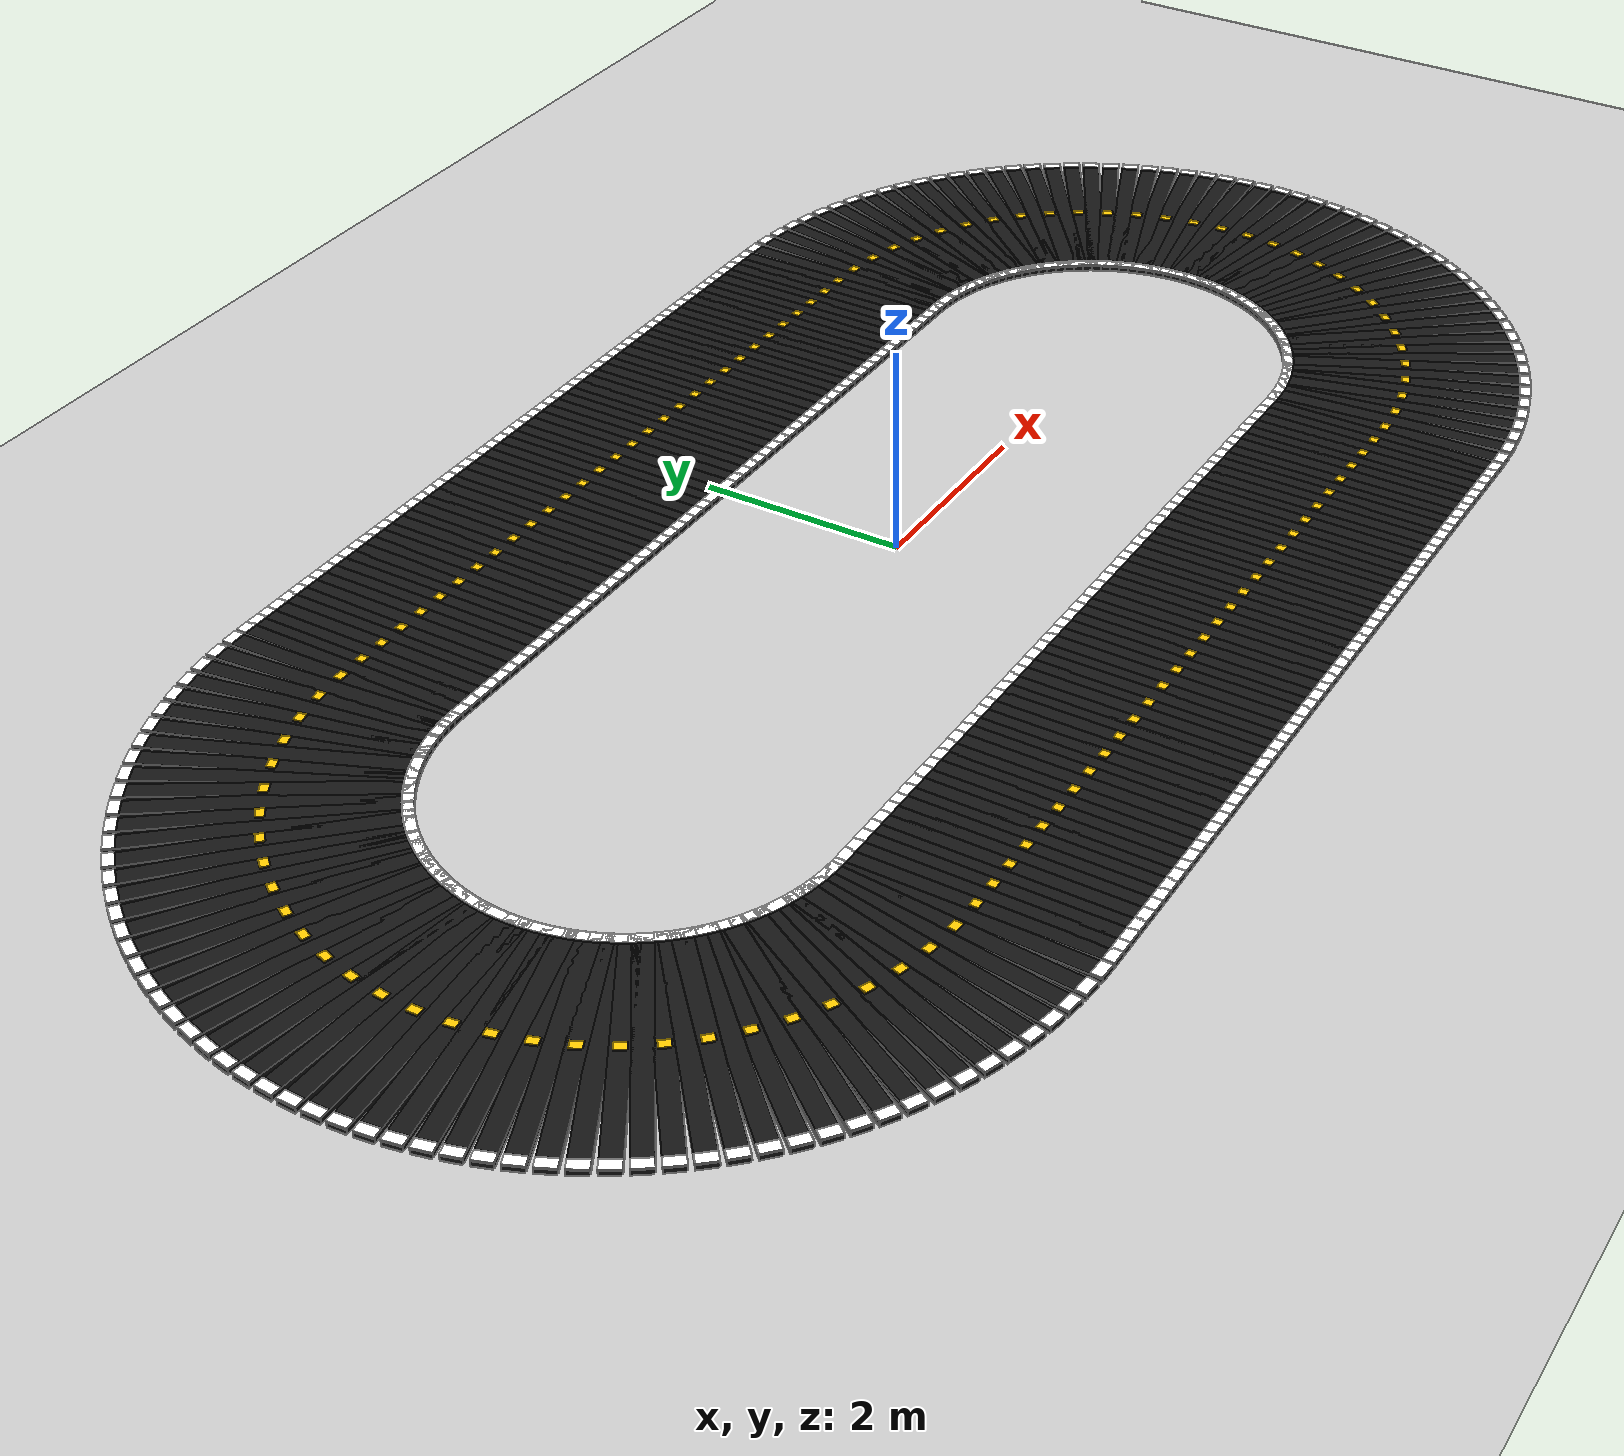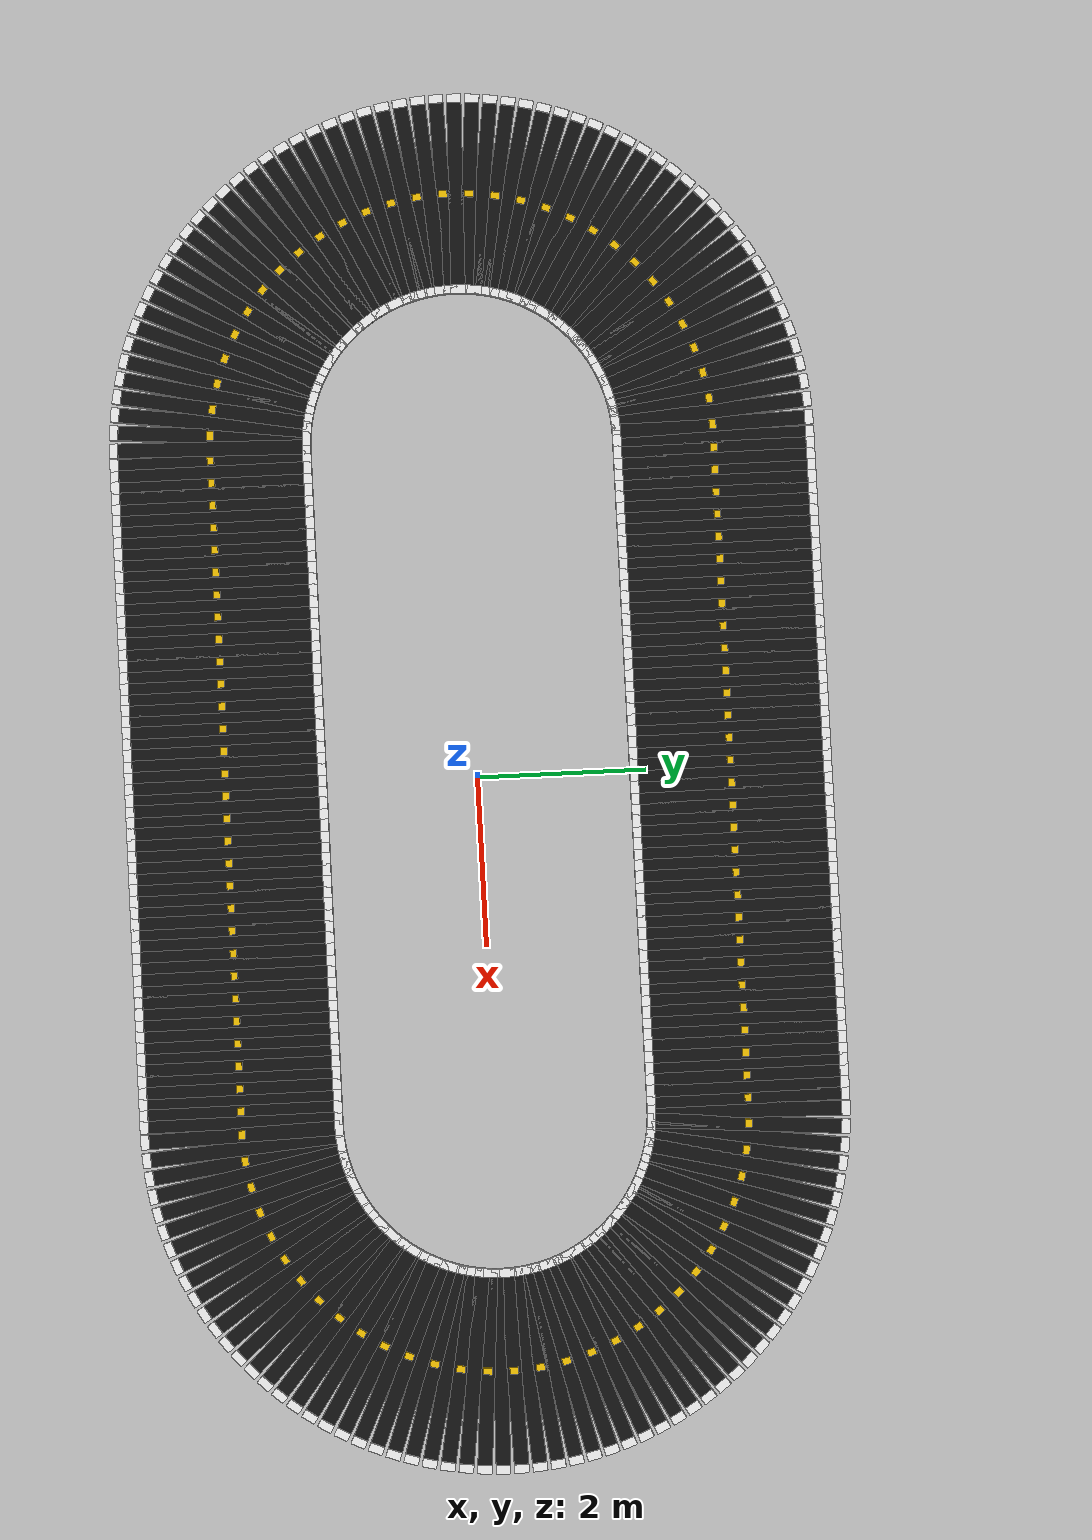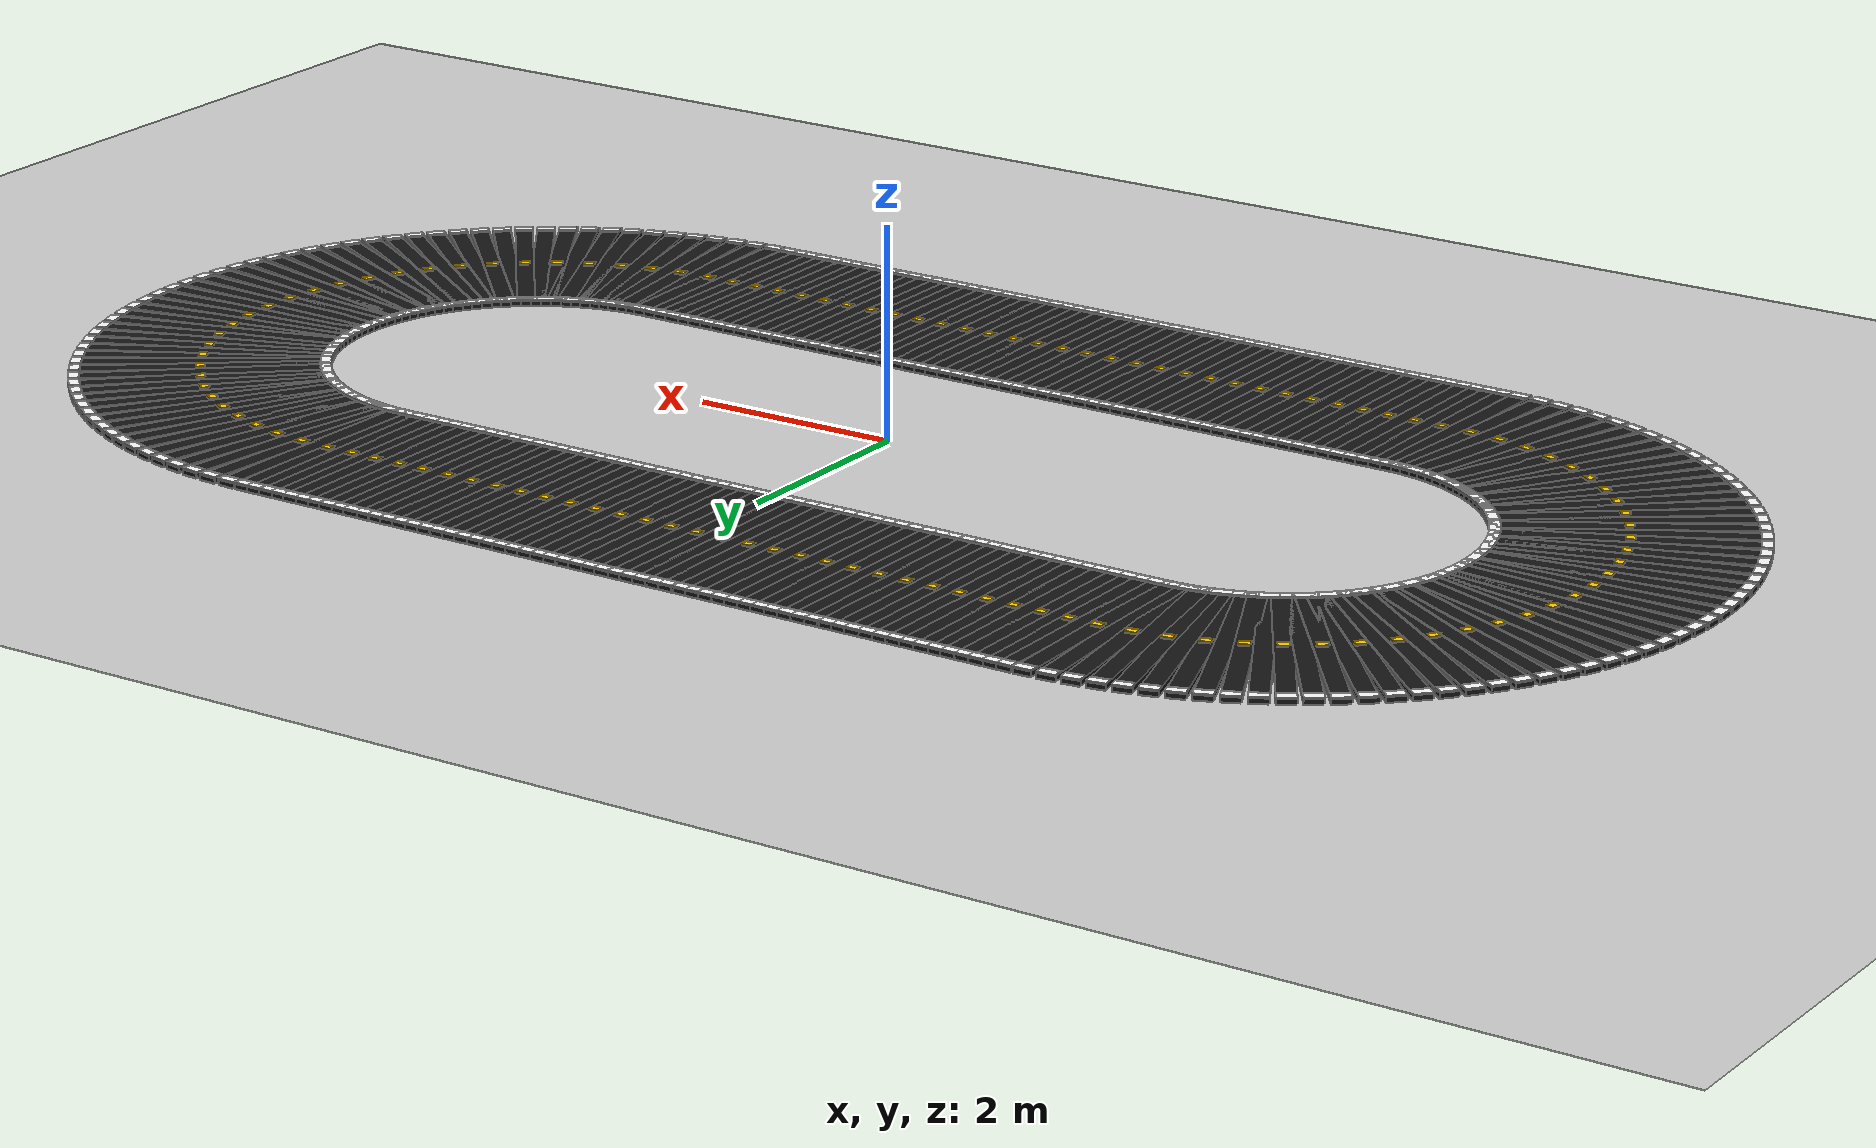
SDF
<?xml version="1.0"?>

<sdf version="1.6">

    <world name="oval_track_world">

        <!-- Gazebo ortamındaki ışık -->
        <include>
            <uri>model://sun</uri>
        </include>

        <!-- Genel zemin -->
        <include>
            <uri>model://ground_plane</uri>
        </include>

        <!-- Oval pistin bütün parçaları -->
        <model name="oval_track">
            <static>true</static>

            <link name="track_link">
                <visual name="road_visual_0">
                    <pose>3.9333 3.0000 0.0250 0 0 3.1416</pose>
                    <geometry>
                        <box>
                            <size>0.1467 2.4000 0.0500</size>
                        </box>
                    </geometry>
                    <material>
                        <ambient>0.08 0.08 0.08 1</ambient>
                        <diffuse>0.08 0.08 0.08 1</diffuse>
                    </material>
                </visual>
                <collision name="road_collision_0">
                    <pose>3.9333 3.0000 0.0250 0 0 3.1416</pose>
                    <geometry>
                        <box>
                            <size>0.1467 2.4000 0.0500</size>
                        </box>
                    </geometry>
                </collision>
                <visual name="left_edge_line_0">
                    <pose>3.9333 1.8500 0.0550 0 0 3.1416</pose>
                    <geometry>
                        <box>
                            <size>0.1467 0.1000 0.0100</size>
                        </box>
                    </geometry>
                    <material>
                        <ambient>1 1 1 1</ambient>
                        <diffuse>1 1 1 1</diffuse>
                    </material>
                </visual>
                <visual name="right_edge_line_0">
                    <pose>3.9333 4.1500 0.0550 0 0 3.1416</pose>
                    <geometry>
                        <box>
                            <size>0.1467 0.1000 0.0100</size>
                        </box>
                    </geometry>
                    <material>
                        <ambient>1 1 1 1</ambient>
                        <diffuse>1 1 1 1</diffuse>
                    </material>
                </visual>
                <visual name="center_line_0">
                    <pose>3.9333 3.0000 0.0560 0 0 3.1416</pose>
                    <geometry>
                        <box>
                            <size>0.0880 0.0800 0.0120</size>
                        </box>
                    </geometry>
                    <material>
                        <ambient>1 0.8 0 1</ambient>
                        <diffuse>1 0.8 0 1</diffuse>
                    </material>
                </visual>
                <visual name="road_visual_1">
                    <pose>3.8000 3.0000 0.0250 0 0 3.1416</pose>
                    <geometry>
                        <box>
                            <size>0.1467 2.4000 0.0500</size>
                        </box>
                    </geometry>
                    <material>
                        <ambient>0.08 0.08 0.08 1</ambient>
                        <diffuse>0.08 0.08 0.08 1</diffuse>
                    </material>
                </visual>
                <collision name="road_collision_1">
                    <pose>3.8000 3.0000 0.0250 0 0 3.1416</pose>
                    <geometry>
                        <box>
                            <size>0.1467 2.4000 0.0500</size>
                        </box>
                    </geometry>
                </collision>
                <visual name="left_edge_line_1">
                    <pose>3.8000 1.8500 0.0550 0 0 3.1416</pose>
                    <geometry>
                        <box>
                            <size>0.1467 0.1000 0.0100</size>
                        </box>
                    </geometry>
                    <material>
                        <ambient>1 1 1 1</ambient>
                        <diffuse>1 1 1 1</diffuse>
                    </material>
                </visual>
                <visual name="right_edge_line_1">
                    <pose>3.8000 4.1500 0.0550 0 0 3.1416</pose>
                    <geometry>
                        <box>
                            <size>0.1467 0.1000 0.0100</size>
                        </box>
                    </geometry>
                    <material>
                        <ambient>1 1 1 1</ambient>
                        <diffuse>1 1 1 1</diffuse>
                    </material>
                </visual>
                <visual name="road_visual_2">
                    <pose>3.6667 3.0000 0.0250 0 0 3.1416</pose>
                    <geometry>
                        <box>
                            <size>0.1467 2.4000 0.0500</size>
                        </box>
                    </geometry>
                    <material>
                        <ambient>0.08 0.08 0.08 1</ambient>
                        <diffuse>0.08 0.08 0.08 1</diffuse>
                    </material>
                </visual>
                <collision name="road_collision_2">
                    <pose>3.6667 3.0000 0.0250 0 0 3.1416</pose>
                    <geometry>
                        <box>
                            <size>0.1467 2.4000 0.0500</size>
                        </box>
                    </geometry>
                </collision>
                <visual name="left_edge_line_2">
                    <pose>3.6667 1.8500 0.0550 0 0 3.1416</pose>
                    <geometry>
                        <box>
                            <size>0.1467 0.1000 0.0100</size>
                        </box>
                    </geometry>
                    <material>
                        <ambient>1 1 1 1</ambient>
                        <diffuse>1 1 1 1</diffuse>
                    </material>
                </visual>
                <visual name="right_edge_line_2">
                    <pose>3.6667 4.1500 0.0550 0 0 3.1416</pose>
                    <geometry>
                        <box>
                            <size>0.1467 0.1000 0.0100</size>
                        </box>
                    </geometry>
                    <material>
                        <ambient>1 1 1 1</ambient>
                        <diffuse>1 1 1 1</diffuse>
                    </material>
                </visual>
                <visual name="center_line_2">
                    <pose>3.6667 3.0000 0.0560 0 0 3.1416</pose>
                    <geometry>
                        <box>
                            <size>0.0880 0.0800 0.0120</size>
                        </box>
                    </geometry>
                    <material>
                        <ambient>1 0.8 0 1</ambient>
                        <diffuse>1 0.8 0 1</diffuse>
                    </material>
                </visual>
                <visual name="road_visual_3">
                    <pose>3.5333 3.0000 0.0250 0 0 3.1416</pose>
                    <geometry>
                        <box>
                            <size>0.1467 2.4000 0.0500</size>
                        </box>
                    </geometry>
                    <material>
                        <ambient>0.08 0.08 0.08 1</ambient>
                        <diffuse>0.08 0.08 0.08 1</diffuse>
                    </material>
                </visual>
                <collision name="road_collision_3">
                    <pose>3.5333 3.0000 0.0250 0 0 3.1416</pose>
                    <geometry>
                        <box>
                            <size>0.1467 2.4000 0.0500</size>
                        </box>
                    </geometry>
                </collision>
                <visual name="left_edge_line_3">
                    <pose>3.5333 1.8500 0.0550 0 0 3.1416</pose>
                    <geometry>
                        <box>
                            <size>0.1467 0.1000 0.0100</size>
                        </box>
                    </geometry>
                    <material>
                        <ambient>1 1 1 1</ambient>
                        <diffuse>1 1 1 1</diffuse>
                    </material>
                </visual>
                <visual name="right_edge_line_3">
                    <pose>3.5333 4.1500 0.0550 0 0 3.1416</pose>
                    <geometry>
                        <box>
                            <size>0.1467 0.1000 0.0100</size>
                        </box>
                    </geometry>
                    <material>
                        <ambient>1 1 1 1</ambient>
                        <diffuse>1 1 1 1</diffuse>
                    </material>
                </visual>
                <visual name="road_visual_4">
                    <pose>3.4000 3.0000 0.0250 0 0 3.1416</pose>
                    <geometry>
                        <box>
                            <size>0.1467 2.4000 0.0500</size>
                        </box>
                    </geometry>
                    <material>
                        <ambient>0.08 0.08 0.08 1</ambient>
                        <diffuse>0.08 0.08 0.08 1</diffuse>
                    </material>
                </visual>
                <collision name="road_collision_4">
                    <pose>3.4000 3.0000 0.0250 0 0 3.1416</pose>
                    <geometry>
                        <box>
                            <size>0.1467 2.4000 0.0500</size>
                        </box>
                    </geometry>
                </collision>
                <visual name="left_edge_line_4">
                    <pose>3.4000 1.8500 0.0550 0 0 3.1416</pose>
                    <geometry>
                        <box>
                            <size>0.1467 0.1000 0.0100</size>
                        </box>
                    </geometry>
                    <material>
                        <ambient>1 1 1 1</ambient>
                        <diffuse>1 1 1 1</diffuse>
                    </material>
                </visual>
                <visual name="right_edge_line_4">
                    <pose>3.4000 4.1500 0.0550 0 0 3.1416</pose>
                    <geometry>
                        <box>
                            <size>0.1467 0.1000 0.0100</size>
                        </box>
                    </geometry>
                    <material>
                        <ambient>1 1 1 1</ambient>
                        <diffuse>1 1 1 1</diffuse>
                    </material>
                </visual>
                <visual name="center_line_4">
                    <pose>3.4000 3.0000 0.0560 0 0 3.1416</pose>
                    <geometry>
                        <box>
                            <size>0.0880 0.0800 0.0120</size>
                        </box>
                    </geometry>
                    <material>
                        <ambient>1 0.8 0 1</ambient>
                        <diffuse>1 0.8 0 1</diffuse>
                    </material>
                </visual>
                <visual name="road_visual_5">
                    <pose>3.2667 3.0000 0.0250 0 0 3.1416</pose>
                    <geometry>
                        <box>
                            <size>0.1467 2.4000 0.0500</size>
                        </box>
                    </geometry>
                    <material>
                        <ambient>0.08 0.08 0.08 1</ambient>
                        <diffuse>0.08 0.08 0.08 1</diffuse>
                    </material>
                </visual>
                <collision name="road_collision_5">
                    <pose>3.2667 3.0000 0.0250 0 0 3.1416</pose>
                    <geometry>
                        <box>
                            <size>0.1467 2.4000 0.0500</size>
                        </box>
                    </geometry>
                </collision>
                <visual name="left_edge_line_5">
                    <pose>3.2667 1.8500 0.0550 0 0 3.1416</pose>
                    <geometry>
                        <box>
                            <size>0.1467 0.1000 0.0100</size>
                        </box>
                    </geometry>
                    <material>
                        <ambient>1 1 1 1</ambient>
                        <diffuse>1 1 1 1</diffuse>
                    </material>
                </visual>
                <visual name="right_edge_line_5">
                    <pose>3.2667 4.1500 0.0550 0 0 3.1416</pose>
                    <geometry>
                        <box>
                            <size>0.1467 0.1000 0.0100</size>
                        </box>
                    </geometry>
                    <material>
                        <ambient>1 1 1 1</ambient>
                        <diffuse>1 1 1 1</diffuse>
                    </material>
                </visual>
                <visual name="road_visual_6">
                    <pose>3.1333 3.0000 0.0250 0 0 3.1416</pose>
                    <geometry>
                        <box>
                            <size>0.1467 2.4000 0.0500</size>
                        </box>
                    </geometry>
                    <material>
                        <ambient>0.08 0.08 0.08 1</ambient>
                        <diffuse>0.08 0.08 0.08 1</diffuse>
                    </material>
                </visual>
                <collision name="road_collision_6">
                    <pose>3.1333 3.0000 0.0250 0 0 3.1416</pose>
                    <geometry>
                        <box>
                            <size>0.1467 2.4000 0.0500</size>
                        </box>
                    </geometry>
                </collision>
                <visual name="left_edge_line_6">
                    <pose>3.1333 1.8500 0.0550 0 0 3.1416</pose>
                    <geometry>
                        <box>
                            <size>0.1467 0.1000 0.0100</size>
                        </box>
                    </geometry>
                    <material>
                        <ambient>1 1 1 1</ambient>
                        <diffuse>1 1 1 1</diffuse>
                    </material>
                </visual>
                <visual name="right_edge_line_6">
                    <pose>3.1333 4.1500 0.0550 0 0 3.1416</pose>
                    <geometry>
                        <box>
                            <size>0.1467 0.1000 0.0100</size>
                        </box>
                    </geometry>
                    <material>
                        <ambient>1 1 1 1</ambient>
                        <diffuse>1 1 1 1</diffuse>
                    </material>
                </visual>
                <visual name="center_line_6">
                    <pose>3.1333 3.0000 0.0560 0 0 3.1416</pose>
                    <geometry>
                        <box>
                            <size>0.0880 0.0800 0.0120</size>
                        </box>
                    </geometry>
                    <material>
                        <ambient>1 0.8 0 1</ambient>
                        <diffuse>1 0.8 0 1</diffuse>
                    </material>
                </visual>
                <visual name="road_visual_7">
                    <pose>3.0000 3.0000 0.0250 0 0 3.1416</pose>
                    <geometry>
                        <box>
                            <size>0.1467 2.4000 0.0500</size>
                        </box>
                    </geometry>
                    <material>
                        <ambient>0.08 0.08 0.08 1</ambient>
                        <diffuse>0.08 0.08 0.08 1</diffuse>
                    </material>
                </visual>
                <collision name="road_collision_7">
                    <pose>3.0000 3.0000 0.0250 0 0 3.1416</pose>
                    <geometry>
                        <box>
                            <size>0.1467 2.4000 0.0500</size>
                        </box>
                    </geometry>
                </collision>
                <visual name="left_edge_line_7">
                    <pose>3.0000 1.8500 0.0550 0 0 3.1416</pose>
                    <geometry>
                        <box>
                            <size>0.1467 0.1000 0.0100</size>
                        </box>
                    </geometry>
                    <material>
                        <ambient>1 1 1 1</ambient>
                        <diffuse>1 1 1 1</diffuse>
                    </material>
                </visual>
                <visual name="right_edge_line_7">
                    <pose>3.0000 4.1500 0.0550 0 0 3.1416</pose>
                    <geometry>
                        <box>
                            <size>0.1467 0.1000 0.0100</size>
                        </box>
                    </geometry>
                    <material>
                        <ambient>1 1 1 1</ambient>
                        <diffuse>1 1 1 1</diffuse>
                    </material>
                </visual>
                <visual name="road_visual_8">
                    <pose>2.8667 3.0000 0.0250 0 0 3.1416</pose>
                    <geometry>
                        <box>
                            <size>0.1467 2.4000 0.0500</size>
                        </box>
                    </geometry>
                    <material>
                        <ambient>0.08 0.08 0.08 1</ambient>
                        <diffuse>0.08 0.08 0.08 1</diffuse>
                    </material>
                </visual>
                <collision name="road_collision_8">
                    <pose>2.8667 3.0000 0.0250 0 0 3.1416</pose>
                    <geometry>
                        <box>
                            <size>0.1467 2.4000 0.0500</size>
                        </box>
                    </geometry>
                </collision>
                <visual name="left_edge_line_8">
                    <pose>2.8667 1.8500 0.0550 0 0 3.1416</pose>
                    <geometry>
                        <box>
                            <size>0.1467 0.1000 0.0100</size>
                        </box>
                    </geometry>
                    <material>
                        <ambient>1 1 1 1</ambient>
                        <diffuse>1 1 1 1</diffuse>
                    </material>
                </visual>
                <visual name="right_edge_line_8">
                    <pose>2.8667 4.1500 0.0550 0 0 3.1416</pose>
                    <geometry>
                        <box>
                            <size>0.1467 0.1000 0.0100</size>
                        </box>
                    </geometry>
                    <material>
                        <ambient>1 1 1 1</ambient>
                        <diffuse>1 1 1 1</diffuse>
                    </material>
                </visual>
                <visual name="center_line_8">
                    <pose>2.8667 3.0000 0.0560 0 0 3.1416</pose>
                    <geometry>
                        <box>
                            <size>0.0880 0.0800 0.0120</size>
                        </box>
                    </geometry>
                    <material>
                        <ambient>1 0.8 0 1</ambient>
                        <diffuse>1 0.8 0 1</diffuse>
                    </material>
                </visual>
                <visual name="road_visual_9">
                    <pose>2.7333 3.0000 0.0250 0 0 3.1416</pose>
                    <geometry>
                        <box>
                            <size>0.1467 2.4000 0.0500</size>
                        </box>
                    </geometry>
                    <material>
                        <ambient>0.08 0.08 0.08 1</ambient>
                        <diffuse>0.08 0.08 0.08 1</diffuse>
                    </material>
                </visual>
                <collision name="road_collision_9">
                    <pose>2.7333 3.0000 0.0250 0 0 3.1416</pose>
                    <geometry>
                        <box>
                            <size>0.1467 2.4000 0.0500</size>
                        </box>
                    </geometry>
                </collision>
                <visual name="left_edge_line_9">
                    <pose>2.7333 1.8500 0.0550 0 0 3.1416</pose>
                    <geometry>
                        <box>
                            <size>0.1467 0.1000 0.0100</size>
                        </box>
                    </geometry>
                    <material>
                        <ambient>1 1 1 1</ambient>
                        <diffuse>1 1 1 1</diffuse>
                    </material>
                </visual>
                <visual name="right_edge_line_9">
                    <pose>2.7333 4.1500 0.0550 0 0 3.1416</pose>
                    <geometry>
                        <box>
                            <size>0.1467 0.1000 0.0100</size>
                        </box>
                    </geometry>
                    <material>
                        <ambient>1 1 1 1</ambient>
                        <diffuse>1 1 1 1</diffuse>
                    </material>
                </visual>
                <visual name="road_visual_10">
                    <pose>2.6000 3.0000 0.0250 0 0 3.1416</pose>
                    <geometry>
                        <box>
                            <size>0.1467 2.4000 0.0500</size>
                        </box>
                    </geometry>
                    <material>
                        <ambient>0.08 0.08 0.08 1</ambient>
                        <diffuse>0.08 0.08 0.08 1</diffuse>
                    </material>
                </visual>
                <collision name="road_collision_10">
                    <pose>2.6000 3.0000 0.0250 0 0 3.1416</pose>
                    <geometry>
                        <box>
                            <size>0.1467 2.4000 0.0500</size>
                        </box>
                    </geometry>
                </collision>
                <visual name="left_edge_line_10">
                    <pose>2.6000 1.8500 0.0550 0 0 3.1416</pose>
                    <geometry>
                        <box>
                            <size>0.1467 0.1000 0.0100</size>
                        </box>
                    </geometry>
                    <material>
                        <ambient>1 1 1 1</ambient>
                        <diffuse>1 1 1 1</diffuse>
                    </material>
                </visual>
                <visual name="right_edge_line_10">
                    <pose>2.6000 4.1500 0.0550 0 0 3.1416</pose>
                    <geometry>
                        <box>
                            <size>0.1467 0.1000 0.0100</size>
                        </box>
                    </geometry>
                    <material>
                        <ambient>1 1 1 1</ambient>
                        <diffuse>1 1 1 1</diffuse>
                    </material>
                </visual>
                <visual name="center_line_10">
                    <pose>2.6000 3.0000 0.0560 0 0 3.1416</pose>
                    <geometry>
                        <box>
                            <size>0.0880 0.0800 0.0120</size>
                        </box>
                    </geometry>
                    <material>
                        <ambient>1 0.8 0 1</ambient>
                        <diffuse>1 0.8 0 1</diffuse>
                    </material>
                </visual>
                <visual name="road_visual_11">
                    <pose>2.4667 3.0000 0.0250 0 0 3.1416</pose>
                    <geometry>
                        <box>
                            <size>0.1467 2.4000 0.0500</size>
                        </box>
                    </geometry>
                    <material>
                        <ambient>0.08 0.08 0.08 1</ambient>
                        <diffuse>0.08 0.08 0.08 1</diffuse>
                    </material>
                </visual>
                <collision name="road_collision_11">
                    <pose>2.4667 3.0000 0.0250 0 0 3.1416</pose>
                    <geometry>
                        <box>
                            <size>0.1467 2.4000 0.0500</size>
                        </box>
                    </geometry>
                </collision>
                <visual name="left_edge_line_11">
                    <pose>2.4667 1.8500 0.0550 0 0 3.1416</pose>
                    <geometry>
                        <box>
                            <size>0.1467 0.1000 0.0100</size>
                        </box>
                    </geometry>
                    <material>
                        <ambient>1 1 1 1</ambient>
                        <diffuse>1 1 1 1</diffuse>
                    </material>
                </visual>
                <visual name="right_edge_line_11">
                    <pose>2.4667 4.1500 0.0550 0 0 3.1416</pose>
                    <geometry>
                        <box>
                            <size>0.1467 0.1000 0.0100</size>
                        </box>
                    </geometry>
                    <material>
                        <ambient>1 1 1 1</ambient>
                        <diffuse>1 1 1 1</diffuse>
                    </material>
                </visual>
                <visual name="road_visual_12">
                    <pose>2.3333 3.0000 0.0250 0 0 3.1416</pose>
                    <geometry>
                        <box>
                            <size>0.1467 2.4000 0.0500</size>
                        </box>
                    </geometry>
                    <material>
                        <ambient>0.08 0.08 0.08 1</ambient>
                        <diffuse>0.08 0.08 0.08 1</diffuse>
                    </material>
                </visual>
                <collision name="road_collision_12">
                    <pose>2.3333 3.0000 0.0250 0 0 3.1416</pose>
                    <geometry>
                        <box>
                            <size>0.1467 2.4000 0.0500</size>
                        </box>
                    </geometry>
                </collision>
                <visual name="left_edge_line_12">
                    <pose>2.3333 1.8500 0.0550 0 0 3.1416</pose>
                    <geometry>
                        <box>
                            <size>0.1467 0.1000 0.0100</size>
                        </box>
                    </geometry>
                    <material>
                        <ambient>1 1 1 1</ambient>
                        <diffuse>1 1 1 1</diffuse>
                    </material>
                </visual>
                <visual name="right_edge_line_12">
                    <pose>2.3333 4.1500 0.0550 0 0 3.1416</pose>
                    <geometry>
                        <box>
                            <size>0.1467 0.1000 0.0100</size>
                        </box>
                    </geometry>
                    <material>
                        <ambient>1 1 1 1</ambient>
                        <diffuse>1 1 1 1</diffuse>
                    </material>
                </visual>
                <visual name="center_line_12">
                    <pose>2.3333 3.0000 0.0560 0 0 3.1416</pose>
                    <geometry>
                        <box>
                            <size>0.0880 0.0800 0.0120</size>
                        </box>
                    </geometry>
                    <material>
                        <ambient>1 0.8 0 1</ambient>
                        <diffuse>1 0.8 0 1</diffuse>
                    </material>
                </visual>
                <visual name="road_visual_13">
                    <pose>2.2000 3.0000 0.0250 0 0 3.1416</pose>
                    <geometry>
                        <box>
                            <size>0.1467 2.4000 0.0500</size>
                        </box>
                    </geometry>
                    <material>
                        <ambient>0.08 0.08 0.08 1</ambient>
                        <diffuse>0.08 0.08 0.08 1</diffuse>
                    </material>
                </visual>
                <collision name="road_collision_13">
                    <pose>2.2000 3.0000 0.0250 0 0 3.1416</pose>
                    <geometry>
                        <box>
                            <size>0.1467 2.4000 0.0500</size>
                        </box>
                    </geometry>
                </collision>
                <visual name="left_edge_line_13">
                    <pose>2.2000 1.8500 0.0550 0 0 3.1416</pose>
                    <geometry>
                        <box>
                            <size>0.1467 0.1000 0.0100</size>
                        </box>
                    </geometry>
                    <material>
                        <ambient>1 1 1 1</ambient>
                        <diffuse>1 1 1 1</diffuse>
                    </material>
                </visual>
                <visual name="right_edge_line_13">
                    <pose>2.2000 4.1500 0.0550 0 0 3.1416</pose>
                    <geometry>
                        <box>
                            <size>0.1467 0.1000 0.0100</size>
                        </box>
                    </geometry>
                    <material>
                        <ambient>1 1 1 1</ambient>
                        <diffuse>1 1 1 1</diffuse>
                    </material>
                </visual>
                <visual name="road_visual_14">
                    <pose>2.0667 3.0000 0.0250 0 0 3.1416</pose>
                    <geometry>
                        <box>
                            <size>0.1467 2.4000 0.0500</size>
                        </box>
                    </geometry>
                    <material>
                        <ambient>0.08 0.08 0.08 1</ambient>
                        <diffuse>0.08 0.08 0.08 1</diffuse>
                    </material>
                </visual>
                <collision name="road_collision_14">
                    <pose>2.0667 3.0000 0.0250 0 0 3.1416</pose>
                    <geometry>
                        <box>
                            <size>0.1467 2.4000 0.0500</size>
                        </box>
                    </geometry>
                </collision>
                <visual name="left_edge_line_14">
                    <pose>2.0667 1.8500 0.0550 0 0 3.1416</pose>
                    <geometry>
                        <box>
                            <size>0.1467 0.1000 0.0100</size>
                        </box>
                    </geometry>
                    <material>
                        <ambient>1 1 1 1</ambient>
                        <diffuse>1 1 1 1</diffuse>
                    </material>
                </visual>
                <visual name="right_edge_line_14">
                    <pose>2.0667 4.1500 0.0550 0 0 3.1416</pose>
                    <geometry>
                        <box>
                            <size>0.1467 0.1000 0.0100</size>
                        </box>
                    </geometry>
                    <material>
                        <ambient>1 1 1 1</ambient>
                        <diffuse>1 1 1 1</diffuse>
                    </material>
                </visual>
                <visual name="center_line_14">
                    <pose>2.0667 3.0000 0.0560 0 0 3.1416</pose>
                    <geometry>
                        <box>
                            <size>0.0880 0.0800 0.0120</size>
                        </box>
                    </geometry>
                    <material>
                        <ambient>1 0.8 0 1</ambient>
                        <diffuse>1 0.8 0 1</diffuse>
                    </material>
                </visual>
                <visual name="road_visual_15">
                    <pose>1.9333 3.0000 0.0250 0 0 3.1416</pose>
                    <geometry>
                        <box>
                            <size>0.1467 2.4000 0.0500</size>
                        </box>
                    </geometry>
                    <material>
                        <ambient>0.08 0.08 0.08 1</ambient>
                        <diffuse>0.08 0.08 0.08 1</diffuse>
                    </material>
                </visual>
                <collision name="road_collision_15">
                    <pose>1.9333 3.0000 0.0250 0 0 3.1416</pose>
                    <geometry>
                        <box>
                            <size>0.1467 2.4000 0.0500</size>
                        </box>
                    </geometry>
                </collision>
                <visual name="left_edge_line_15">
                    <pose>1.9333 1.8500 0.0550 0 0 3.1416</pose>
                    <geometry>
                        <box>
                            <size>0.1467 0.1000 0.0100</size>
                        </box>
                    </geometry>
                    <material>
                        <ambient>1 1 1 1</ambient>
                        <diffuse>1 1 1 1</diffuse>
                    </material>
                </visual>
                <visual name="right_edge_line_15">
                    <pose>1.9333 4.1500 0.0550 0 0 3.1416</pose>
                    <geometry>
                        <box>
                            <size>0.1467 0.1000 0.0100</size>
                        </box>
                    </geometry>
                    <material>
                        <ambient>1 1 1 1</ambient>
                        <diffuse>1 1 1 1</diffuse>
                    </material>
                </visual>
                <visual name="road_visual_16">
                    <pose>1.8000 3.0000 0.0250 0 0 3.1416</pose>
                    <geometry>
                        <box>
                            <size>0.1467 2.4000 0.0500</size>
                        </box>
                    </geometry>
                    <material>
                        <ambient>0.08 0.08 0.08 1</ambient>
                        <diffuse>0.08 0.08 0.08 1</diffuse>
                    </material>
                </visual>
                <collision name="road_collision_16">
                    <pose>1.8000 3.0000 0.0250 0 0 3.1416</pose>
                    <geometry>
                        <box>
                            <size>0.1467 2.4000 0.0500</size>
                        </box>
                    </geometry>
                </collision>
                <visual name="left_edge_line_16">
                    <pose>1.8000 1.8500 0.0550 0 0 3.1416</pose>
                    <geometry>
                        <box>
                            <size>0.1467 0.1000 0.0100</size>
                        </box>
                    </geometry>
                    <material>
                        <ambient>1 1 1 1</ambient>
                        <diffuse>1 1 1 1</diffuse>
                    </material>
                </visual>
                <visual name="right_edge_line_16">
                    <pose>1.8000 4.1500 0.0550 0 0 3.1416</pose>
                    <geometry>
                        <box>
                            <size>0.1467 0.1000 0.0100</size>
                        </box>
                    </geometry>
                    <material>
                        <ambient>1 1 1 1</ambient>
                        <diffuse>1 1 1 1</diffuse>
                    </material>
                </visual>
                <visual name="center_line_16">
                    <pose>1.8000 3.0000 0.0560 0 0 3.1416</pose>
                    <geometry>
                        <box>
                            <size>0.0880 0.0800 0.0120</size>
                        </box>
                    </geometry>
                    <material>
                        <ambient>1 0.8 0 1</ambient>
                        <diffuse>1 0.8 0 1</diffuse>
                    </material>
                </visual>
                <visual name="road_visual_17">
                    <pose>1.6667 3.0000 0.0250 0 0 3.1416</pose>
                    <geometry>
                        <box>
                            <size>0.1467 2.4000 0.0500</size>
                        </box>
                    </geometry>
                    <material>
                        <ambient>0.08 0.08 0.08 1</ambient>
                        <diffuse>0.08 0.08 0.08 1</diffuse>
                    </material>
                </visual>
                <collision name="road_collision_17">
                    <pose>1.6667 3.0000 0.0250 0 0 3.1416</pose>
                    <geometry>
                        <box>
                            <size>0.1467 2.4000 0.0500</size>
                        </box>
                    </geometry>
                </collision>
                <visual name="left_edge_line_17">
                    <pose>1.6667 1.8500 0.0550 0 0 3.1416</pose>
                    <geometry>
                        <box>
                            <size>0.1467 0.1000 0.0100</size>
                        </box>
                    </geometry>
                    <material>
                        <ambient>1 1 1 1</ambient>
                        <diffuse>1 1 1 1</diffuse>
                    </material>
                </visual>
                <visual name="right_edge_line_17">
                    <pose>1.6667 4.1500 0.0550 0 0 3.1416</pose>
                    <geometry>
                        <box>
                            <size>0.1467 0.1000 0.0100</size>
                        </box>
                    </geometry>
                    <material>
                        <ambient>1 1 1 1</ambient>
                        <diffuse>1 1 1 1</diffuse>
                    </material>
                </visual>
                <visual name="road_visual_18">
                    <pose>1.5333 3.0000 0.0250 0 0 3.1416</pose>
                    <geometry>
                        <box>
                            <size>0.1467 2.4000 0.0500</size>
                        </box>
                    </geometry>
                    <material>
                        <ambient>0.08 0.08 0.08 1</ambient>
                        <diffuse>0.08 0.08 0.08 1</diffuse>
                    </material>
                </visual>
                <collision name="road_collision_18">
                    <pose>1.5333 3.0000 0.0250 0 0 3.1416</pose>
                    <geometry>
                        <box>
                            <size>0.1467 2.4000 0.0500</size>
                        </box>
                    </geometry>
                </collision>
                <visual name="left_edge_line_18">
                    <pose>1.5333 1.8500 0.0550 0 0 3.1416</pose>
                    <geometry>
                        <box>
                            <size>0.1467 0.1000 0.0100</size>
                        </box>
                    </geometry>
                    <material>
                        <ambient>1 1 1 1</ambient>
                        <diffuse>1 1 1 1</diffuse>
                    </material>
                </visual>
                <visual name="right_edge_line_18">
                    <pose>1.5333 4.1500 0.0550 0 0 3.1416</pose>
                    <geometry>
                        <box>
                            <size>0.1467 0.1000 0.0100</size>
                        </box>
                    </geometry>
                    <material>
                        <ambient>1 1 1 1</ambient>
                        <diffuse>1 1 1 1</diffuse>
                    </material>
                </visual>
                <visual name="center_line_18">
                    <pose>1.5333 3.0000 0.0560 0 0 3.1416</pose>
                    <geometry>
                        <box>
                            <size>0.0880 0.0800 0.0120</size>
                        </box>
                    </geometry>
                    <material>
                        <ambient>1 0.8 0 1</ambient>
                        <diffuse>1 0.8 0 1</diffuse>
                    </material>
                </visual>
                <visual name="road_visual_19">
                    <pose>1.4000 3.0000 0.0250 0 0 3.1416</pose>
                    <geometry>
                        <box>
                            <size>0.1467 2.4000 0.0500</size>
                        </box>
                    </geometry>
                    <material>
                        <ambient>0.08 0.08 0.08 1</ambient>
                        <diffuse>0.08 0.08 0.08 1</diffuse>
                    </material>
                </visual>
                <collision name="road_collision_19">
                    <pose>1.4000 3.0000 0.0250 0 0 3.1416</pose>
                    <geometry>
                        <box>
                            <size>0.1467 2.4000 0.0500</size>
                        </box>
                    </geometry>
                </collision>
                <visual name="left_edge_line_19">
                    <pose>1.4000 1.8500 0.0550 0 0 3.1416</pose>
                    <geometry>
                        <box>
                            <size>0.1467 0.1000 0.0100</size>
                        </box>
                    </geometry>
                    <material>
                        <ambient>1 1 1 1</ambient>
                        <diffuse>1 1 1 1</diffuse>
                    </material>
                </visual>
                <visual name="right_edge_line_19">
                    <pose>1.4000 4.1500 0.0550 0 0 3.1416</pose>
                    <geometry>
                        <box>
                            <size>0.1467 0.1000 0.0100</size>
                        </box>
                    </geometry>
                    <material>
                        <ambient>1 1 1 1</ambient>
                        <diffuse>1 1 1 1</diffuse>
                    </material>
                </visual>
                <visual name="road_visual_20">
                    <pose>1.2667 3.0000 0.0250 0 0 3.1416</pose>
                    <geometry>
                        <box>
                            <size>0.1467 2.4000 0.0500</size>
                        </box>
                    </geometry>
                    <material>
                        <ambient>0.08 0.08 0.08 1</ambient>
                        <diffuse>0.08 0.08 0.08 1</diffuse>
                    </material>
                </visual>
                <collision name="road_collision_20">
                    <pose>1.2667 3.0000 0.0250 0 0 3.1416</pose>
                    <geometry>
                        <box>
                            <size>0.1467 2.4000 0.0500</size>
                        </box>
                    </geometry>
                </collision>
                <visual name="left_edge_line_20">
                    <pose>1.2667 1.8500 0.0550 0 0 3.1416</pose>
                    <geometry>
                        <box>
                            <size>0.1467 0.1000 0.0100</size>
                        </box>
                    </geometry>
                    <material>
                        <ambient>1 1 1 1</ambient>
                        <diffuse>1 1 1 1</diffuse>
                    </material>
                </visual>
                <visual name="right_edge_line_20">
                    <pose>1.2667 4.1500 0.0550 0 0 3.1416</pose>
                    <geometry>
                        <box>
                            <size>0.1467 0.1000 0.0100</size>
                        </box>
                    </geometry>
                    <material>
                        <ambient>1 1 1 1</ambient>
                        <diffuse>1 1 1 1</diffuse>
                    </material>
                </visual>
                <visual name="center_line_20">
                    <pose>1.2667 3.0000 0.0560 0 0 3.1416</pose>
                    <geometry>
                        <box>
                            <size>0.0880 0.0800 0.0120</size>
                        </box>
                    </geometry>
                    <material>
                        <ambient>1 0.8 0 1</ambient>
                        <diffuse>1 0.8 0 1</diffuse>
                    </material>
                </visual>
                <visual name="road_visual_21">
                    <pose>1.1333 3.0000 0.0250 0 0 3.1416</pose>
                    <geometry>
                        <box>
                            <size>0.1467 2.4000 0.0500</size>
                        </box>
                    </geometry>
                    <material>
                        <ambient>0.08 0.08 0.08 1</ambient>
                        <diffuse>0.08 0.08 0.08 1</diffuse>
                    </material>
                </visual>
                <collision name="road_collision_21">
                    <pose>1.1333 3.0000 0.0250 0 0 3.1416</pose>
                    <geometry>
                        <box>
                            <size>0.1467 2.4000 0.0500</size>
                        </box>
                    </geometry>
                </collision>
                <visual name="left_edge_line_21">
                    <pose>1.1333 1.8500 0.0550 0 0 3.1416</pose>
                    <geometry>
                        <box>
                            <size>0.1467 0.1000 0.0100</size>
                        </box>
                    </geometry>
                    <material>
                        <ambient>1 1 1 1</ambient>
                        <diffuse>1 1 1 1</diffuse>
                    </material>
                </visual>
                <visual name="right_edge_line_21">
                    <pose>1.1333 4.1500 0.0550 0 0 3.1416</pose>
                    <geometry>
                        <box>
                            <size>0.1467 0.1000 0.0100</size>
                        </box>
                    </geometry>
                    <material>
                        <ambient>1 1 1 1</ambient>
                        <diffuse>1 1 1 1</diffuse>
                    </material>
                </visual>
                <visual name="road_visual_22">
                    <pose>1.0000 3.0000 0.0250 0 0 3.1416</pose>
                    <geometry>
                        <box>
                            <size>0.1467 2.4000 0.0500</size>
                        </box>
                    </geometry>
                    <material>
                        <ambient>0.08 0.08 0.08 1</ambient>
                        <diffuse>0.08 0.08 0.08 1</diffuse>
                    </material>
                </visual>
                <collision name="road_collision_22">
                    <pose>1.0000 3.0000 0.0250 0 0 3.1416</pose>
                    <geometry>
                        <box>
                            <size>0.1467 2.4000 0.0500</size>
                        </box>
                    </geometry>
                </collision>
                <visual name="left_edge_line_22">
                    <pose>1.0000 1.8500 0.0550 0 0 3.1416</pose>
                    <geometry>
                        <box>
                            <size>0.1467 0.1000 0.0100</size>
                        </box>
                    </geometry>
                    <material>
                        <ambient>1 1 1 1</ambient>
                        <diffuse>1 1 1 1</diffuse>
                    </material>
                </visual>
                <visual name="right_edge_line_22">
                    <pose>1.0000 4.1500 0.0550 0 0 3.1416</pose>
                    <geometry>
                        <box>
                            <size>0.1467 0.1000 0.0100</size>
                        </box>
                    </geometry>
                    <material>
                        <ambient>1 1 1 1</ambient>
                        <diffuse>1 1 1 1</diffuse>
                    </material>
                </visual>
                <visual name="center_line_22">
                    <pose>1.0000 3.0000 0.0560 0 0 3.1416</pose>
                    <geometry>
                        <box>
                            <size>0.0880 0.0800 0.0120</size>
                        </box>
                    </geometry>
                    <material>
                        <ambient>1 0.8 0 1</ambient>
                        <diffuse>1 0.8 0 1</diffuse>
                    </material>
                </visual>
                <visual name="road_visual_23">
                    <pose>0.8667 3.0000 0.0250 0 0 3.1416</pose>
                    <geometry>
                        <box>
                            <size>0.1467 2.4000 0.0500</size>
                        </box>
                    </geometry>
                    <material>
                        <ambient>0.08 0.08 0.08 1</ambient>
                        <diffuse>0.08 0.08 0.08 1</diffuse>
                    </material>
                </visual>
                <collision name="road_collision_23">
                    <pose>0.8667 3.0000 0.0250 0 0 3.1416</pose>
                    <geometry>
                        <box>
                            <size>0.1467 2.4000 0.0500</size>
                        </box>
                    </geometry>
                </collision>
                <visual name="left_edge_line_23">
                    <pose>0.8667 1.8500 0.0550 0 0 3.1416</pose>
                    <geometry>
                        <box>
                            <size>0.1467 0.1000 0.0100</size>
                        </box>
                    </geometry>
                    <material>
                        <ambient>1 1 1 1</ambient>
                        <diffuse>1 1 1 1</diffuse>
                    </material>
                </visual>
                <visual name="right_edge_line_23">
                    <pose>0.8667 4.1500 0.0550 0 0 3.1416</pose>
                    <geometry>
                        <box>
                            <size>0.1467 0.1000 0.0100</size>
                        </box>
                    </geometry>
                    <material>
                        <ambient>1 1 1 1</ambient>
                        <diffuse>1 1 1 1</diffuse>
                    </material>
                </visual>
                <visual name="road_visual_24">
                    <pose>0.7333 3.0000 0.0250 0 0 3.1416</pose>
                    <geometry>
                        <box>
                            <size>0.1467 2.4000 0.0500</size>
                        </box>
                    </geometry>
                    <material>
                        <ambient>0.08 0.08 0.08 1</ambient>
                        <diffuse>0.08 0.08 0.08 1</diffuse>
                    </material>
                </visual>
                <collision name="road_collision_24">
                    <pose>0.7333 3.0000 0.0250 0 0 3.1416</pose>
                    <geometry>
                        <box>
                            <size>0.1467 2.4000 0.0500</size>
                        </box>
                    </geometry>
                </collision>
                <visual name="left_edge_line_24">
                    <pose>0.7333 1.8500 0.0550 0 0 3.1416</pose>
                    <geometry>
                        <box>
                            <size>0.1467 0.1000 0.0100</size>
                        </box>
                    </geometry>
                    <material>
                        <ambient>1 1 1 1</ambient>
                        <diffuse>1 1 1 1</diffuse>
                    </material>
                </visual>
                <visual name="right_edge_line_24">
                    <pose>0.7333 4.1500 0.0550 0 0 3.1416</pose>
                    <geometry>
                        <box>
                            <size>0.1467 0.1000 0.0100</size>
                        </box>
                    </geometry>
                    <material>
                        <ambient>1 1 1 1</ambient>
                        <diffuse>1 1 1 1</diffuse>
                    </material>
                </visual>
                <visual name="center_line_24">
                    <pose>0.7333 3.0000 0.0560 0 0 3.1416</pose>
                    <geometry>
                        <box>
                            <size>0.0880 0.0800 0.0120</size>
                        </box>
                    </geometry>
                    <material>
                        <ambient>1 0.8 0 1</ambient>
                        <diffuse>1 0.8 0 1</diffuse>
                    </material>
                </visual>
                <visual name="road_visual_25">
                    <pose>0.6000 3.0000 0.0250 0 0 3.1416</pose>
                    <geometry>
                        <box>
                            <size>0.1467 2.4000 0.0500</size>
                        </box>
                    </geometry>
                    <material>
                        <ambient>0.08 0.08 0.08 1</ambient>
                        <diffuse>0.08 0.08 0.08 1</diffuse>
                    </material>
                </visual>
                <collision name="road_collision_25">
                    <pose>0.6000 3.0000 0.0250 0 0 3.1416</pose>
                    <geometry>
                        <box>
                            <size>0.1467 2.4000 0.0500</size>
                        </box>
                    </geometry>
                </collision>
                <visual name="left_edge_line_25">
                    <pose>0.6000 1.8500 0.0550 0 0 3.1416</pose>
                    <geometry>
                        <box>
                            <size>0.1467 0.1000 0.0100</size>
                        </box>
                    </geometry>
                    <material>
                        <ambient>1 1 1 1</ambient>
                        <diffuse>1 1 1 1</diffuse>
                    </material>
                </visual>
                <visual name="right_edge_line_25">
                    <pose>0.6000 4.1500 0.0550 0 0 3.1416</pose>
                    <geometry>
                        <box>
                            <size>0.1467 0.1000 0.0100</size>
                        </box>
                    </geometry>
                    <material>
                        <ambient>1 1 1 1</ambient>
                        <diffuse>1 1 1 1</diffuse>
                    </material>
                </visual>
                <visual name="road_visual_26">
                    <pose>0.4667 3.0000 0.0250 0 0 3.1416</pose>
                    <geometry>
                        <box>
                            <size>0.1467 2.4000 0.0500</size>
                        </box>
                    </geometry>
                    <material>
                        <ambient>0.08 0.08 0.08 1</ambient>
                        <diffuse>0.08 0.08 0.08 1</diffuse>
                    </material>
                </visual>
                <collision name="road_collision_26">
                    <pose>0.4667 3.0000 0.0250 0 0 3.1416</pose>
                    <geometry>
                        <box>
                            <size>0.1467 2.4000 0.0500</size>
                        </box>
                    </geometry>
                </collision>
                <visual name="left_edge_line_26">
                    <pose>0.4667 1.8500 0.0550 0 0 3.1416</pose>
                    <geometry>
                        <box>
                            <size>0.1467 0.1000 0.0100</size>
                        </box>
                    </geometry>
                    <material>
                        <ambient>1 1 1 1</ambient>
                        <diffuse>1 1 1 1</diffuse>
                    </material>
                </visual>
                <visual name="right_edge_line_26">
                    <pose>0.4667 4.1500 0.0550 0 0 3.1416</pose>
                    <geometry>
                        <box>
                            <size>0.1467 0.1000 0.0100</size>
                        </box>
                    </geometry>
                    <material>
                        <ambient>1 1 1 1</ambient>
                        <diffuse>1 1 1 1</diffuse>
                    </material>
                </visual>
                <visual name="center_line_26">
                    <pose>0.4667 3.0000 0.0560 0 0 3.1416</pose>
                    <geometry>
                        <box>
                            <size>0.0880 0.0800 0.0120</size>
                        </box>
                    </geometry>
                    <material>
                        <ambient>1 0.8 0 1</ambient>
                        <diffuse>1 0.8 0 1</diffuse>
                    </material>
                </visual>
                <visual name="road_visual_27">
                    <pose>0.3333 3.0000 0.0250 0 0 3.1416</pose>
                    <geometry>
                        <box>
                            <size>0.1467 2.4000 0.0500</size>
                        </box>
                    </geometry>
                    <material>
                        <ambient>0.08 0.08 0.08 1</ambient>
                        <diffuse>0.08 0.08 0.08 1</diffuse>
                    </material>
                </visual>
                <collision name="road_collision_27">
                    <pose>0.3333 3.0000 0.0250 0 0 3.1416</pose>
                    <geometry>
                        <box>
                            <size>0.1467 2.4000 0.0500</size>
                        </box>
                    </geometry>
                </collision>
                <visual name="left_edge_line_27">
                    <pose>0.3333 1.8500 0.0550 0 0 3.1416</pose>
                    <geometry>
                        <box>
                            <size>0.1467 0.1000 0.0100</size>
                        </box>
                    </geometry>
                    <material>
                        <ambient>1 1 1 1</ambient>
                        <diffuse>1 1 1 1</diffuse>
                    </material>
                </visual>
                <visual name="right_edge_line_27">
                    <pose>0.3333 4.1500 0.0550 0 0 3.1416</pose>
                    <geometry>
                        <box>
                            <size>0.1467 0.1000 0.0100</size>
                        </box>
                    </geometry>
                    <material>
                        <ambient>1 1 1 1</ambient>
                        <diffuse>1 1 1 1</diffuse>
                    </material>
                </visual>
                <visual name="road_visual_28">
                    <pose>0.2000 3.0000 0.0250 0 0 3.1416</pose>
                    <geometry>
                        <box>
                            <size>0.1467 2.4000 0.0500</size>
                        </box>
                    </geometry>
                    <material>
                        <ambient>0.08 0.08 0.08 1</ambient>
                        <diffuse>0.08 0.08 0.08 1</diffuse>
                    </material>
                </visual>
                <collision name="road_collision_28">
                    <pose>0.2000 3.0000 0.0250 0 0 3.1416</pose>
                    <geometry>
                        <box>
                            <size>0.1467 2.4000 0.0500</size>
                        </box>
                    </geometry>
                </collision>
                <visual name="left_edge_line_28">
                    <pose>0.2000 1.8500 0.0550 0 0 3.1416</pose>
                    <geometry>
                        <box>
                            <size>0.1467 0.1000 0.0100</size>
                        </box>
                    </geometry>
                    <material>
                        <ambient>1 1 1 1</ambient>
                        <diffuse>1 1 1 1</diffuse>
                    </material>
                </visual>
                <visual name="right_edge_line_28">
                    <pose>0.2000 4.1500 0.0550 0 0 3.1416</pose>
                    <geometry>
                        <box>
                            <size>0.1467 0.1000 0.0100</size>
                        </box>
                    </geometry>
                    <material>
                        <ambient>1 1 1 1</ambient>
                        <diffuse>1 1 1 1</diffuse>
                    </material>
                </visual>
                <visual name="center_line_28">
                    <pose>0.2000 3.0000 0.0560 0 0 3.1416</pose>
                    <geometry>
                        <box>
                            <size>0.0880 0.0800 0.0120</size>
                        </box>
                    </geometry>
                    <material>
                        <ambient>1 0.8 0 1</ambient>
                        <diffuse>1 0.8 0 1</diffuse>
                    </material>
                </visual>
                <visual name="road_visual_29">
                    <pose>0.0667 3.0000 0.0250 0 0 3.1416</pose>
                    <geometry>
                        <box>
                            <size>0.1467 2.4000 0.0500</size>
                        </box>
                    </geometry>
                    <material>
                        <ambient>0.08 0.08 0.08 1</ambient>
                        <diffuse>0.08 0.08 0.08 1</diffuse>
                    </material>
                </visual>
                <collision name="road_collision_29">
                    <pose>0.0667 3.0000 0.0250 0 0 3.1416</pose>
                    <geometry>
                        <box>
                            <size>0.1467 2.4000 0.0500</size>
                        </box>
                    </geometry>
                </collision>
                <visual name="left_edge_line_29">
                    <pose>0.0667 1.8500 0.0550 0 0 3.1416</pose>
                    <geometry>
                        <box>
                            <size>0.1467 0.1000 0.0100</size>
                        </box>
                    </geometry>
                    <material>
                        <ambient>1 1 1 1</ambient>
                        <diffuse>1 1 1 1</diffuse>
                    </material>
                </visual>
                <visual name="right_edge_line_29">
                    <pose>0.0667 4.1500 0.0550 0 0 3.1416</pose>
                    <geometry>
                        <box>
                            <size>0.1467 0.1000 0.0100</size>
                        </box>
                    </geometry>
                    <material>
                        <ambient>1 1 1 1</ambient>
                        <diffuse>1 1 1 1</diffuse>
                    </material>
                </visual>
                <visual name="road_visual_30">
                    <pose>-0.0667 3.0000 0.0250 0 0 3.1416</pose>
                    <geometry>
                        <box>
                            <size>0.1467 2.4000 0.0500</size>
                        </box>
                    </geometry>
                    <material>
                        <ambient>0.08 0.08 0.08 1</ambient>
                        <diffuse>0.08 0.08 0.08 1</diffuse>
                    </material>
                </visual>
                <collision name="road_collision_30">
                    <pose>-0.0667 3.0000 0.0250 0 0 3.1416</pose>
                    <geometry>
                        <box>
                            <size>0.1467 2.4000 0.0500</size>
                        </box>
                    </geometry>
                </collision>
                <visual name="left_edge_line_30">
                    <pose>-0.0667 1.8500 0.0550 0 0 3.1416</pose>
                    <geometry>
                        <box>
                            <size>0.1467 0.1000 0.0100</size>
                        </box>
                    </geometry>
                    <material>
                        <ambient>1 1 1 1</ambient>
                        <diffuse>1 1 1 1</diffuse>
                    </material>
                </visual>
                <visual name="right_edge_line_30">
                    <pose>-0.0667 4.1500 0.0550 0 0 3.1416</pose>
                    <geometry>
                        <box>
                            <size>0.1467 0.1000 0.0100</size>
                        </box>
                    </geometry>
                    <material>
                        <ambient>1 1 1 1</ambient>
                        <diffuse>1 1 1 1</diffuse>
                    </material>
                </visual>
                <visual name="center_line_30">
                    <pose>-0.0667 3.0000 0.0560 0 0 3.1416</pose>
                    <geometry>
                        <box>
                            <size>0.0880 0.0800 0.0120</size>
                        </box>
                    </geometry>
                    <material>
                        <ambient>1 0.8 0 1</ambient>
                        <diffuse>1 0.8 0 1</diffuse>
                    </material>
                </visual>
                <visual name="road_visual_31">
                    <pose>-0.2000 3.0000 0.0250 0 0 3.1416</pose>
                    <geometry>
                        <box>
                            <size>0.1467 2.4000 0.0500</size>
                        </box>
                    </geometry>
                    <material>
                        <ambient>0.08 0.08 0.08 1</ambient>
                        <diffuse>0.08 0.08 0.08 1</diffuse>
                    </material>
                </visual>
                <collision name="road_collision_31">
                    <pose>-0.2000 3.0000 0.0250 0 0 3.1416</pose>
                    <geometry>
                        <box>
                            <size>0.1467 2.4000 0.0500</size>
                        </box>
                    </geometry>
                </collision>
                <visual name="left_edge_line_31">
                    <pose>-0.2000 1.8500 0.0550 0 0 3.1416</pose>
                    <geometry>
                        <box>
                            <size>0.1467 0.1000 0.0100</size>
                        </box>
                    </geometry>
                    <material>
                        <ambient>1 1 1 1</ambient>
                        <diffuse>1 1 1 1</diffuse>
                    </material>
                </visual>
                <visual name="right_edge_line_31">
                    <pose>-0.2000 4.1500 0.0550 0 0 3.1416</pose>
                    <geometry>
                        <box>
                            <size>0.1467 0.1000 0.0100</size>
                        </box>
                    </geometry>
                    <material>
                        <ambient>1 1 1 1</ambient>
                        <diffuse>1 1 1 1</diffuse>
                    </material>
                </visual>
                <visual name="road_visual_32">
                    <pose>-0.3333 3.0000 0.0250 0 0 3.1416</pose>
                    <geometry>
                        <box>
                            <size>0.1467 2.4000 0.0500</size>
                        </box>
                    </geometry>
                    <material>
                        <ambient>0.08 0.08 0.08 1</ambient>
                        <diffuse>0.08 0.08 0.08 1</diffuse>
                    </material>
                </visual>
                <collision name="road_collision_32">
                    <pose>-0.3333 3.0000 0.0250 0 0 3.1416</pose>
                    <geometry>
                        <box>
                            <size>0.1467 2.4000 0.0500</size>
                        </box>
                    </geometry>
                </collision>
                <visual name="left_edge_line_32">
                    <pose>-0.3333 1.8500 0.0550 0 0 3.1416</pose>
                    <geometry>
                        <box>
                            <size>0.1467 0.1000 0.0100</size>
                        </box>
                    </geometry>
                    <material>
                        <ambient>1 1 1 1</ambient>
                        <diffuse>1 1 1 1</diffuse>
                    </material>
                </visual>
                <visual name="right_edge_line_32">
                    <pose>-0.3333 4.1500 0.0550 0 0 3.1416</pose>
                    <geometry>
                        <box>
                            <size>0.1467 0.1000 0.0100</size>
                        </box>
                    </geometry>
                    <material>
                        <ambient>1 1 1 1</ambient>
                        <diffuse>1 1 1 1</diffuse>
                    </material>
                </visual>
                <visual name="center_line_32">
                    <pose>-0.3333 3.0000 0.0560 0 0 3.1416</pose>
                    <geometry>
                        <box>
                            <size>0.0880 0.0800 0.0120</size>
                        </box>
                    </geometry>
                    <material>
                        <ambient>1 0.8 0 1</ambient>
                        <diffuse>1 0.8 0 1</diffuse>
                    </material>
                </visual>
                <visual name="road_visual_33">
                    <pose>-0.4667 3.0000 0.0250 0 0 3.1416</pose>
                    <geometry>
                        <box>
                            <size>0.1467 2.4000 0.0500</size>
                        </box>
                    </geometry>
                    <material>
                        <ambient>0.08 0.08 0.08 1</ambient>
                        <diffuse>0.08 0.08 0.08 1</diffuse>
                    </material>
                </visual>
                <collision name="road_collision_33">
                    <pose>-0.4667 3.0000 0.0250 0 0 3.1416</pose>
                    <geometry>
                        <box>
                            <size>0.1467 2.4000 0.0500</size>
                        </box>
                    </geometry>
                </collision>
                <visual name="left_edge_line_33">
                    <pose>-0.4667 1.8500 0.0550 0 0 3.1416</pose>
                    <geometry>
                        <box>
                            <size>0.1467 0.1000 0.0100</size>
                        </box>
                    </geometry>
                    <material>
                        <ambient>1 1 1 1</ambient>
                        <diffuse>1 1 1 1</diffuse>
                    </material>
                </visual>
                <visual name="right_edge_line_33">
                    <pose>-0.4667 4.1500 0.0550 0 0 3.1416</pose>
                    <geometry>
                        <box>
                            <size>0.1467 0.1000 0.0100</size>
                        </box>
                    </geometry>
                    <material>
                        <ambient>1 1 1 1</ambient>
                        <diffuse>1 1 1 1</diffuse>
                    </material>
                </visual>
                <visual name="road_visual_34">
                    <pose>-0.6000 3.0000 0.0250 0 0 3.1416</pose>
                    <geometry>
                        <box>
                            <size>0.1467 2.4000 0.0500</size>
                        </box>
                    </geometry>
                    <material>
                        <ambient>0.08 0.08 0.08 1</ambient>
                        <diffuse>0.08 0.08 0.08 1</diffuse>
                    </material>
                </visual>
                <collision name="road_collision_34">
                    <pose>-0.6000 3.0000 0.0250 0 0 3.1416</pose>
                    <geometry>
                        <box>
                            <size>0.1467 2.4000 0.0500</size>
                        </box>
                    </geometry>
                </collision>
                <visual name="left_edge_line_34">
                    <pose>-0.6000 1.8500 0.0550 0 0 3.1416</pose>
                    <geometry>
                        <box>
                            <size>0.1467 0.1000 0.0100</size>
                        </box>
                    </geometry>
                    <material>
                        <ambient>1 1 1 1</ambient>
                        <diffuse>1 1 1 1</diffuse>
                    </material>
                </visual>
                <visual name="right_edge_line_34">
                    <pose>-0.6000 4.1500 0.0550 0 0 3.1416</pose>
                    <geometry>
                        <box>
                            <size>0.1467 0.1000 0.0100</size>
                        </box>
                    </geometry>
                    <material>
                        <ambient>1 1 1 1</ambient>
                        <diffuse>1 1 1 1</diffuse>
                    </material>
                </visual>
                <visual name="center_line_34">
                    <pose>-0.6000 3.0000 0.0560 0 0 3.1416</pose>
                    <geometry>
                        <box>
                            <size>0.0880 0.0800 0.0120</size>
                        </box>
                    </geometry>
                    <material>
                        <ambient>1 0.8 0 1</ambient>
                        <diffuse>1 0.8 0 1</diffuse>
                    </material>
                </visual>
                <visual name="road_visual_35">
                    <pose>-0.7333 3.0000 0.0250 0 0 3.1416</pose>
                    <geometry>
                        <box>
                            <size>0.1467 2.4000 0.0500</size>
                        </box>
                    </geometry>
                    <material>
                        <ambient>0.08 0.08 0.08 1</ambient>
                        <diffuse>0.08 0.08 0.08 1</diffuse>
                    </material>
                </visual>
                <collision name="road_collision_35">
                    <pose>-0.7333 3.0000 0.0250 0 0 3.1416</pose>
                    <geometry>
                        <box>
                            <size>0.1467 2.4000 0.0500</size>
                        </box>
                    </geometry>
                </collision>
                <visual name="left_edge_line_35">
                    <pose>-0.7333 1.8500 0.0550 0 0 3.1416</pose>
                    <geometry>
                        <box>
                            <size>0.1467 0.1000 0.0100</size>
                        </box>
                    </geometry>
                    <material>
                        <ambient>1 1 1 1</ambient>
                        <diffuse>1 1 1 1</diffuse>
                    </material>
                </visual>
                <visual name="right_edge_line_35">
                    <pose>-0.7333 4.1500 0.0550 0 0 3.1416</pose>
                    <geometry>
                        <box>
                            <size>0.1467 0.1000 0.0100</size>
                        </box>
                    </geometry>
                    <material>
                        <ambient>1 1 1 1</ambient>
                        <diffuse>1 1 1 1</diffuse>
                    </material>
                </visual>
                <visual name="road_visual_36">
                    <pose>-0.8667 3.0000 0.0250 0 0 3.1416</pose>
                    <geometry>
                        <box>
                            <size>0.1467 2.4000 0.0500</size>
                        </box>
                    </geometry>
                    <material>
                        <ambient>0.08 0.08 0.08 1</ambient>
                        <diffuse>0.08 0.08 0.08 1</diffuse>
                    </material>
                </visual>
                <collision name="road_collision_36">
                    <pose>-0.8667 3.0000 0.0250 0 0 3.1416</pose>
                    <geometry>
                        <box>
                            <size>0.1467 2.4000 0.0500</size>
                        </box>
                    </geometry>
                </collision>
                <visual name="left_edge_line_36">
                    <pose>-0.8667 1.8500 0.0550 0 0 3.1416</pose>
                    <geometry>
                        <box>
                            <size>0.1467 0.1000 0.0100</size>
                        </box>
                    </geometry>
                    <material>
                        <ambient>1 1 1 1</ambient>
                        <diffuse>1 1 1 1</diffuse>
                    </material>
                </visual>
                <visual name="right_edge_line_36">
                    <pose>-0.8667 4.1500 0.0550 0 0 3.1416</pose>
                    <geometry>
                        <box>
                            <size>0.1467 0.1000 0.0100</size>
                        </box>
                    </geometry>
                    <material>
                        <ambient>1 1 1 1</ambient>
                        <diffuse>1 1 1 1</diffuse>
                    </material>
                </visual>
                <visual name="center_line_36">
                    <pose>-0.8667 3.0000 0.0560 0 0 3.1416</pose>
                    <geometry>
                        <box>
                            <size>0.0880 0.0800 0.0120</size>
                        </box>
                    </geometry>
                    <material>
                        <ambient>1 0.8 0 1</ambient>
                        <diffuse>1 0.8 0 1</diffuse>
                    </material>
                </visual>
                <visual name="road_visual_37">
                    <pose>-1.0000 3.0000 0.0250 0 0 3.1416</pose>
                    <geometry>
                        <box>
                            <size>0.1467 2.4000 0.0500</size>
                        </box>
                    </geometry>
                    <material>
                        <ambient>0.08 0.08 0.08 1</ambient>
                        <diffuse>0.08 0.08 0.08 1</diffuse>
                    </material>
                </visual>
                <collision name="road_collision_37">
                    <pose>-1.0000 3.0000 0.0250 0 0 3.1416</pose>
                    <geometry>
                        <box>
                            <size>0.1467 2.4000 0.0500</size>
                        </box>
                    </geometry>
                </collision>
                <visual name="left_edge_line_37">
                    <pose>-1.0000 1.8500 0.0550 0 0 3.1416</pose>
                    <geometry>
                        <box>
                            <size>0.1467 0.1000 0.0100</size>
                        </box>
                    </geometry>
                    <material>
                        <ambient>1 1 1 1</ambient>
                        <diffuse>1 1 1 1</diffuse>
                    </material>
                </visual>
                <visual name="right_edge_line_37">
                    <pose>-1.0000 4.1500 0.0550 0 0 3.1416</pose>
                    <geometry>
                        <box>
                            <size>0.1467 0.1000 0.0100</size>
                        </box>
                    </geometry>
                    <material>
                        <ambient>1 1 1 1</ambient>
                        <diffuse>1 1 1 1</diffuse>
                    </material>
                </visual>
                <visual name="road_visual_38">
                    <pose>-1.1333 3.0000 0.0250 0 0 3.1416</pose>
                    <geometry>
                        <box>
                            <size>0.1467 2.4000 0.0500</size>
                        </box>
                    </geometry>
                    <material>
                        <ambient>0.08 0.08 0.08 1</ambient>
                        <diffuse>0.08 0.08 0.08 1</diffuse>
                    </material>
                </visual>
                <collision name="road_collision_38">
                    <pose>-1.1333 3.0000 0.0250 0 0 3.1416</pose>
                    <geometry>
                        <box>
                            <size>0.1467 2.4000 0.0500</size>
                        </box>
                    </geometry>
                </collision>
                <visual name="left_edge_line_38">
                    <pose>-1.1333 1.8500 0.0550 0 0 3.1416</pose>
                    <geometry>
                        <box>
                            <size>0.1467 0.1000 0.0100</size>
                        </box>
                    </geometry>
                    <material>
                        <ambient>1 1 1 1</ambient>
                        <diffuse>1 1 1 1</diffuse>
                    </material>
                </visual>
                <visual name="right_edge_line_38">
                    <pose>-1.1333 4.1500 0.0550 0 0 3.1416</pose>
                    <geometry>
                        <box>
                            <size>0.1467 0.1000 0.0100</size>
                        </box>
                    </geometry>
                    <material>
                        <ambient>1 1 1 1</ambient>
                        <diffuse>1 1 1 1</diffuse>
                    </material>
                </visual>
                <visual name="center_line_38">
                    <pose>-1.1333 3.0000 0.0560 0 0 3.1416</pose>
                    <geometry>
                        <box>
                            <size>0.0880 0.0800 0.0120</size>
                        </box>
                    </geometry>
                    <material>
                        <ambient>1 0.8 0 1</ambient>
                        <diffuse>1 0.8 0 1</diffuse>
                    </material>
                </visual>
                <visual name="road_visual_39">
                    <pose>-1.2667 3.0000 0.0250 0 0 3.1416</pose>
                    <geometry>
                        <box>
                            <size>0.1467 2.4000 0.0500</size>
                        </box>
                    </geometry>
                    <material>
                        <ambient>0.08 0.08 0.08 1</ambient>
                        <diffuse>0.08 0.08 0.08 1</diffuse>
                    </material>
                </visual>
                <collision name="road_collision_39">
                    <pose>-1.2667 3.0000 0.0250 0 0 3.1416</pose>
                    <geometry>
                        <box>
                            <size>0.1467 2.4000 0.0500</size>
                        </box>
                    </geometry>
                </collision>
                <visual name="left_edge_line_39">
                    <pose>-1.2667 1.8500 0.0550 0 0 3.1416</pose>
                    <geometry>
                        <box>
                            <size>0.1467 0.1000 0.0100</size>
                        </box>
                    </geometry>
                    <material>
                        <ambient>1 1 1 1</ambient>
                        <diffuse>1 1 1 1</diffuse>
                    </material>
                </visual>
                <visual name="right_edge_line_39">
                    <pose>-1.2667 4.1500 0.0550 0 0 3.1416</pose>
                    <geometry>
                        <box>
                            <size>0.1467 0.1000 0.0100</size>
                        </box>
                    </geometry>
                    <material>
                        <ambient>1 1 1 1</ambient>
                        <diffuse>1 1 1 1</diffuse>
                    </material>
                </visual>
                <visual name="road_visual_40">
                    <pose>-1.4000 3.0000 0.0250 0 0 3.1416</pose>
                    <geometry>
                        <box>
                            <size>0.1467 2.4000 0.0500</size>
                        </box>
                    </geometry>
                    <material>
                        <ambient>0.08 0.08 0.08 1</ambient>
                        <diffuse>0.08 0.08 0.08 1</diffuse>
                    </material>
                </visual>
                <collision name="road_collision_40">
                    <pose>-1.4000 3.0000 0.0250 0 0 3.1416</pose>
                    <geometry>
                        <box>
                            <size>0.1467 2.4000 0.0500</size>
                        </box>
                    </geometry>
                </collision>
                <visual name="left_edge_line_40">
                    <pose>-1.4000 1.8500 0.0550 0 0 3.1416</pose>
                    <geometry>
                        <box>
                            <size>0.1467 0.1000 0.0100</size>
                        </box>
                    </geometry>
                    <material>
                        <ambient>1 1 1 1</ambient>
                        <diffuse>1 1 1 1</diffuse>
                    </material>
                </visual>
                <visual name="right_edge_line_40">
                    <pose>-1.4000 4.1500 0.0550 0 0 3.1416</pose>
                    <geometry>
                        <box>
                            <size>0.1467 0.1000 0.0100</size>
                        </box>
                    </geometry>
                    <material>
                        <ambient>1 1 1 1</ambient>
                        <diffuse>1 1 1 1</diffuse>
                    </material>
                </visual>
                <visual name="center_line_40">
                    <pose>-1.4000 3.0000 0.0560 0 0 3.1416</pose>
                    <geometry>
                        <box>
                            <size>0.0880 0.0800 0.0120</size>
                        </box>
                    </geometry>
                    <material>
                        <ambient>1 0.8 0 1</ambient>
                        <diffuse>1 0.8 0 1</diffuse>
                    </material>
                </visual>
                <visual name="road_visual_41">
                    <pose>-1.5333 3.0000 0.0250 0 0 3.1416</pose>
                    <geometry>
                        <box>
                            <size>0.1467 2.4000 0.0500</size>
                        </box>
                    </geometry>
                    <material>
                        <ambient>0.08 0.08 0.08 1</ambient>
                        <diffuse>0.08 0.08 0.08 1</diffuse>
                    </material>
                </visual>
                <collision name="road_collision_41">
                    <pose>-1.5333 3.0000 0.0250 0 0 3.1416</pose>
                    <geometry>
                        <box>
                            <size>0.1467 2.4000 0.0500</size>
                        </box>
                    </geometry>
                </collision>
                <visual name="left_edge_line_41">
                    <pose>-1.5333 1.8500 0.0550 0 0 3.1416</pose>
                    <geometry>
                        <box>
                            <size>0.1467 0.1000 0.0100</size>
                        </box>
                    </geometry>
                    <material>
                        <ambient>1 1 1 1</ambient>
                        <diffuse>1 1 1 1</diffuse>
                    </material>
                </visual>
                <visual name="right_edge_line_41">
                    <pose>-1.5333 4.1500 0.0550 0 0 3.1416</pose>
                    <geometry>
                        <box>
                            <size>0.1467 0.1000 0.0100</size>
                        </box>
                    </geometry>
                    <material>
                        <ambient>1 1 1 1</ambient>
                        <diffuse>1 1 1 1</diffuse>
                    </material>
                </visual>
                <visual name="road_visual_42">
                    <pose>-1.6667 3.0000 0.0250 0 0 3.1416</pose>
                    <geometry>
                        <box>
                            <size>0.1467 2.4000 0.0500</size>
                        </box>
                    </geometry>
                    <material>
                        <ambient>0.08 0.08 0.08 1</ambient>
                        <diffuse>0.08 0.08 0.08 1</diffuse>
                    </material>
                </visual>
                <collision name="road_collision_42">
                    <pose>-1.6667 3.0000 0.0250 0 0 3.1416</pose>
                    <geometry>
                        <box>
                            <size>0.1467 2.4000 0.0500</size>
                        </box>
                    </geometry>
                </collision>
                <visual name="left_edge_line_42">
                    <pose>-1.6667 1.8500 0.0550 0 0 3.1416</pose>
                    <geometry>
                        <box>
                            <size>0.1467 0.1000 0.0100</size>
                        </box>
                    </geometry>
                    <material>
                        <ambient>1 1 1 1</ambient>
                        <diffuse>1 1 1 1</diffuse>
                    </material>
                </visual>
                <visual name="right_edge_line_42">
                    <pose>-1.6667 4.1500 0.0550 0 0 3.1416</pose>
                    <geometry>
                        <box>
                            <size>0.1467 0.1000 0.0100</size>
                        </box>
                    </geometry>
                    <material>
                        <ambient>1 1 1 1</ambient>
                        <diffuse>1 1 1 1</diffuse>
                    </material>
                </visual>
                <visual name="center_line_42">
                    <pose>-1.6667 3.0000 0.0560 0 0 3.1416</pose>
                    <geometry>
                        <box>
                            <size>0.0880 0.0800 0.0120</size>
                        </box>
                    </geometry>
                    <material>
                        <ambient>1 0.8 0 1</ambient>
                        <diffuse>1 0.8 0 1</diffuse>
                    </material>
                </visual>
                <visual name="road_visual_43">
                    <pose>-1.8000 3.0000 0.0250 0 0 3.1416</pose>
                    <geometry>
                        <box>
                            <size>0.1467 2.4000 0.0500</size>
                        </box>
                    </geometry>
                    <material>
                        <ambient>0.08 0.08 0.08 1</ambient>
                        <diffuse>0.08 0.08 0.08 1</diffuse>
                    </material>
                </visual>
                <collision name="road_collision_43">
                    <pose>-1.8000 3.0000 0.0250 0 0 3.1416</pose>
                    <geometry>
                        <box>
                            <size>0.1467 2.4000 0.0500</size>
                        </box>
                    </geometry>
                </collision>
                <visual name="left_edge_line_43">
                    <pose>-1.8000 1.8500 0.0550 0 0 3.1416</pose>
                    <geometry>
                        <box>
                            <size>0.1467 0.1000 0.0100</size>
                        </box>
                    </geometry>
                    <material>
                        <ambient>1 1 1 1</ambient>
                        <diffuse>1 1 1 1</diffuse>
                    </material>
                </visual>
                <visual name="right_edge_line_43">
                    <pose>-1.8000 4.1500 0.0550 0 0 3.1416</pose>
                    <geometry>
                        <box>
                            <size>0.1467 0.1000 0.0100</size>
                        </box>
                    </geometry>
                    <material>
                        <ambient>1 1 1 1</ambient>
                        <diffuse>1 1 1 1</diffuse>
                    </material>
                </visual>
                <visual name="road_visual_44">
                    <pose>-1.9333 3.0000 0.0250 0 0 3.1416</pose>
                    <geometry>
                        <box>
                            <size>0.1467 2.4000 0.0500</size>
                        </box>
                    </geometry>
                    <material>
                        <ambient>0.08 0.08 0.08 1</ambient>
                        <diffuse>0.08 0.08 0.08 1</diffuse>
                    </material>
                </visual>
                <collision name="road_collision_44">
                    <pose>-1.9333 3.0000 0.0250 0 0 3.1416</pose>
                    <geometry>
                        <box>
                            <size>0.1467 2.4000 0.0500</size>
                        </box>
                    </geometry>
                </collision>
                <visual name="left_edge_line_44">
                    <pose>-1.9333 1.8500 0.0550 0 0 3.1416</pose>
                    <geometry>
                        <box>
                            <size>0.1467 0.1000 0.0100</size>
                        </box>
                    </geometry>
                    <material>
                        <ambient>1 1 1 1</ambient>
                        <diffuse>1 1 1 1</diffuse>
                    </material>
                </visual>
                <visual name="right_edge_line_44">
                    <pose>-1.9333 4.1500 0.0550 0 0 3.1416</pose>
                    <geometry>
                        <box>
                            <size>0.1467 0.1000 0.0100</size>
                        </box>
                    </geometry>
                    <material>
                        <ambient>1 1 1 1</ambient>
                        <diffuse>1 1 1 1</diffuse>
                    </material>
                </visual>
                <visual name="center_line_44">
                    <pose>-1.9333 3.0000 0.0560 0 0 3.1416</pose>
                    <geometry>
                        <box>
                            <size>0.0880 0.0800 0.0120</size>
                        </box>
                    </geometry>
                    <material>
                        <ambient>1 0.8 0 1</ambient>
                        <diffuse>1 0.8 0 1</diffuse>
                    </material>
                </visual>
                <visual name="road_visual_45">
                    <pose>-2.0667 3.0000 0.0250 0 0 3.1416</pose>
                    <geometry>
                        <box>
                            <size>0.1467 2.4000 0.0500</size>
                        </box>
                    </geometry>
                    <material>
                        <ambient>0.08 0.08 0.08 1</ambient>
                        <diffuse>0.08 0.08 0.08 1</diffuse>
                    </material>
                </visual>
                <collision name="road_collision_45">
                    <pose>-2.0667 3.0000 0.0250 0 0 3.1416</pose>
                    <geometry>
                        <box>
                            <size>0.1467 2.4000 0.0500</size>
                        </box>
                    </geometry>
                </collision>
                <visual name="left_edge_line_45">
                    <pose>-2.0667 1.8500 0.0550 0 0 3.1416</pose>
                    <geometry>
                        <box>
                            <size>0.1467 0.1000 0.0100</size>
                        </box>
                    </geometry>
                    <material>
                        <ambient>1 1 1 1</ambient>
                        <diffuse>1 1 1 1</diffuse>
                    </material>
                </visual>
                <visual name="right_edge_line_45">
                    <pose>-2.0667 4.1500 0.0550 0 0 3.1416</pose>
                    <geometry>
                        <box>
                            <size>0.1467 0.1000 0.0100</size>
                        </box>
                    </geometry>
                    <material>
                        <ambient>1 1 1 1</ambient>
                        <diffuse>1 1 1 1</diffuse>
                    </material>
                </visual>
                <visual name="road_visual_46">
                    <pose>-2.2000 3.0000 0.0250 0 0 3.1416</pose>
                    <geometry>
                        <box>
                            <size>0.1467 2.4000 0.0500</size>
                        </box>
                    </geometry>
                    <material>
                        <ambient>0.08 0.08 0.08 1</ambient>
                        <diffuse>0.08 0.08 0.08 1</diffuse>
                    </material>
                </visual>
                <collision name="road_collision_46">
                    <pose>-2.2000 3.0000 0.0250 0 0 3.1416</pose>
                    <geometry>
                        <box>
                            <size>0.1467 2.4000 0.0500</size>
                        </box>
                    </geometry>
                </collision>
                <visual name="left_edge_line_46">
                    <pose>-2.2000 1.8500 0.0550 0 0 3.1416</pose>
                    <geometry>
                        <box>
                            <size>0.1467 0.1000 0.0100</size>
                        </box>
                    </geometry>
                    <material>
                        <ambient>1 1 1 1</ambient>
                        <diffuse>1 1 1 1</diffuse>
                    </material>
                </visual>
                <visual name="right_edge_line_46">
                    <pose>-2.2000 4.1500 0.0550 0 0 3.1416</pose>
                    <geometry>
                        <box>
                            <size>0.1467 0.1000 0.0100</size>
                        </box>
                    </geometry>
                    <material>
                        <ambient>1 1 1 1</ambient>
                        <diffuse>1 1 1 1</diffuse>
                    </material>
                </visual>
                <visual name="center_line_46">
                    <pose>-2.2000 3.0000 0.0560 0 0 3.1416</pose>
                    <geometry>
                        <box>
                            <size>0.0880 0.0800 0.0120</size>
                        </box>
                    </geometry>
                    <material>
                        <ambient>1 0.8 0 1</ambient>
                        <diffuse>1 0.8 0 1</diffuse>
                    </material>
                </visual>
                <visual name="road_visual_47">
                    <pose>-2.3333 3.0000 0.0250 0 0 3.1416</pose>
                    <geometry>
                        <box>
                            <size>0.1467 2.4000 0.0500</size>
                        </box>
                    </geometry>
                    <material>
                        <ambient>0.08 0.08 0.08 1</ambient>
                        <diffuse>0.08 0.08 0.08 1</diffuse>
                    </material>
                </visual>
                <collision name="road_collision_47">
                    <pose>-2.3333 3.0000 0.0250 0 0 3.1416</pose>
                    <geometry>
                        <box>
                            <size>0.1467 2.4000 0.0500</size>
                        </box>
                    </geometry>
                </collision>
                <visual name="left_edge_line_47">
                    <pose>-2.3333 1.8500 0.0550 0 0 3.1416</pose>
                    <geometry>
                        <box>
                            <size>0.1467 0.1000 0.0100</size>
                        </box>
                    </geometry>
                    <material>
                        <ambient>1 1 1 1</ambient>
                        <diffuse>1 1 1 1</diffuse>
                    </material>
                </visual>
                <visual name="right_edge_line_47">
                    <pose>-2.3333 4.1500 0.0550 0 0 3.1416</pose>
                    <geometry>
                        <box>
                            <size>0.1467 0.1000 0.0100</size>
                        </box>
                    </geometry>
                    <material>
                        <ambient>1 1 1 1</ambient>
                        <diffuse>1 1 1 1</diffuse>
                    </material>
                </visual>
                <visual name="road_visual_48">
                    <pose>-2.4667 3.0000 0.0250 0 0 3.1416</pose>
                    <geometry>
                        <box>
                            <size>0.1467 2.4000 0.0500</size>
                        </box>
                    </geometry>
                    <material>
                        <ambient>0.08 0.08 0.08 1</ambient>
                        <diffuse>0.08 0.08 0.08 1</diffuse>
                    </material>
                </visual>
                <collision name="road_collision_48">
                    <pose>-2.4667 3.0000 0.0250 0 0 3.1416</pose>
                    <geometry>
                        <box>
                            <size>0.1467 2.4000 0.0500</size>
                        </box>
                    </geometry>
                </collision>
                <visual name="left_edge_line_48">
                    <pose>-2.4667 1.8500 0.0550 0 0 3.1416</pose>
                    <geometry>
                        <box>
                            <size>0.1467 0.1000 0.0100</size>
                        </box>
                    </geometry>
                    <material>
                        <ambient>1 1 1 1</ambient>
                        <diffuse>1 1 1 1</diffuse>
                    </material>
                </visual>
                <visual name="right_edge_line_48">
                    <pose>-2.4667 4.1500 0.0550 0 0 3.1416</pose>
                    <geometry>
                        <box>
                            <size>0.1467 0.1000 0.0100</size>
                        </box>
                    </geometry>
                    <material>
                        <ambient>1 1 1 1</ambient>
                        <diffuse>1 1 1 1</diffuse>
                    </material>
                </visual>
                <visual name="center_line_48">
                    <pose>-2.4667 3.0000 0.0560 0 0 3.1416</pose>
                    <geometry>
                        <box>
                            <size>0.0880 0.0800 0.0120</size>
                        </box>
                    </geometry>
                    <material>
                        <ambient>1 0.8 0 1</ambient>
                        <diffuse>1 0.8 0 1</diffuse>
                    </material>
                </visual>
                <visual name="road_visual_49">
                    <pose>-2.6000 3.0000 0.0250 0 0 3.1416</pose>
                    <geometry>
                        <box>
                            <size>0.1467 2.4000 0.0500</size>
                        </box>
                    </geometry>
                    <material>
                        <ambient>0.08 0.08 0.08 1</ambient>
                        <diffuse>0.08 0.08 0.08 1</diffuse>
                    </material>
                </visual>
                <collision name="road_collision_49">
                    <pose>-2.6000 3.0000 0.0250 0 0 3.1416</pose>
                    <geometry>
                        <box>
                            <size>0.1467 2.4000 0.0500</size>
                        </box>
                    </geometry>
                </collision>
                <visual name="left_edge_line_49">
                    <pose>-2.6000 1.8500 0.0550 0 0 3.1416</pose>
                    <geometry>
                        <box>
                            <size>0.1467 0.1000 0.0100</size>
                        </box>
                    </geometry>
                    <material>
                        <ambient>1 1 1 1</ambient>
                        <diffuse>1 1 1 1</diffuse>
                    </material>
                </visual>
                <visual name="right_edge_line_49">
                    <pose>-2.6000 4.1500 0.0550 0 0 3.1416</pose>
                    <geometry>
                        <box>
                            <size>0.1467 0.1000 0.0100</size>
                        </box>
                    </geometry>
                    <material>
                        <ambient>1 1 1 1</ambient>
                        <diffuse>1 1 1 1</diffuse>
                    </material>
                </visual>
                <visual name="road_visual_50">
                    <pose>-2.7333 3.0000 0.0250 0 0 3.1416</pose>
                    <geometry>
                        <box>
                            <size>0.1467 2.4000 0.0500</size>
                        </box>
                    </geometry>
                    <material>
                        <ambient>0.08 0.08 0.08 1</ambient>
                        <diffuse>0.08 0.08 0.08 1</diffuse>
                    </material>
                </visual>
                <collision name="road_collision_50">
                    <pose>-2.7333 3.0000 0.0250 0 0 3.1416</pose>
                    <geometry>
                        <box>
                            <size>0.1467 2.4000 0.0500</size>
                        </box>
                    </geometry>
                </collision>
                <visual name="left_edge_line_50">
                    <pose>-2.7333 1.8500 0.0550 0 0 3.1416</pose>
                    <geometry>
                        <box>
                            <size>0.1467 0.1000 0.0100</size>
                        </box>
                    </geometry>
                    <material>
                        <ambient>1 1 1 1</ambient>
                        <diffuse>1 1 1 1</diffuse>
                    </material>
                </visual>
                <visual name="right_edge_line_50">
                    <pose>-2.7333 4.1500 0.0550 0 0 3.1416</pose>
                    <geometry>
                        <box>
                            <size>0.1467 0.1000 0.0100</size>
                        </box>
                    </geometry>
                    <material>
                        <ambient>1 1 1 1</ambient>
                        <diffuse>1 1 1 1</diffuse>
                    </material>
                </visual>
                <visual name="center_line_50">
                    <pose>-2.7333 3.0000 0.0560 0 0 3.1416</pose>
                    <geometry>
                        <box>
                            <size>0.0880 0.0800 0.0120</size>
                        </box>
                    </geometry>
                    <material>
                        <ambient>1 0.8 0 1</ambient>
                        <diffuse>1 0.8 0 1</diffuse>
                    </material>
                </visual>
                <visual name="road_visual_51">
                    <pose>-2.8667 3.0000 0.0250 0 0 3.1416</pose>
                    <geometry>
                        <box>
                            <size>0.1467 2.4000 0.0500</size>
                        </box>
                    </geometry>
                    <material>
                        <ambient>0.08 0.08 0.08 1</ambient>
                        <diffuse>0.08 0.08 0.08 1</diffuse>
                    </material>
                </visual>
                <collision name="road_collision_51">
                    <pose>-2.8667 3.0000 0.0250 0 0 3.1416</pose>
                    <geometry>
                        <box>
                            <size>0.1467 2.4000 0.0500</size>
                        </box>
                    </geometry>
                </collision>
                <visual name="left_edge_line_51">
                    <pose>-2.8667 1.8500 0.0550 0 0 3.1416</pose>
                    <geometry>
                        <box>
                            <size>0.1467 0.1000 0.0100</size>
                        </box>
                    </geometry>
                    <material>
                        <ambient>1 1 1 1</ambient>
                        <diffuse>1 1 1 1</diffuse>
                    </material>
                </visual>
                <visual name="right_edge_line_51">
                    <pose>-2.8667 4.1500 0.0550 0 0 3.1416</pose>
                    <geometry>
                        <box>
                            <size>0.1467 0.1000 0.0100</size>
                        </box>
                    </geometry>
                    <material>
                        <ambient>1 1 1 1</ambient>
                        <diffuse>1 1 1 1</diffuse>
                    </material>
                </visual>
                <visual name="road_visual_52">
                    <pose>-3.0000 3.0000 0.0250 0 0 3.1416</pose>
                    <geometry>
                        <box>
                            <size>0.1467 2.4000 0.0500</size>
                        </box>
                    </geometry>
                    <material>
                        <ambient>0.08 0.08 0.08 1</ambient>
                        <diffuse>0.08 0.08 0.08 1</diffuse>
                    </material>
                </visual>
                <collision name="road_collision_52">
                    <pose>-3.0000 3.0000 0.0250 0 0 3.1416</pose>
                    <geometry>
                        <box>
                            <size>0.1467 2.4000 0.0500</size>
                        </box>
                    </geometry>
                </collision>
                <visual name="left_edge_line_52">
                    <pose>-3.0000 1.8500 0.0550 0 0 3.1416</pose>
                    <geometry>
                        <box>
                            <size>0.1467 0.1000 0.0100</size>
                        </box>
                    </geometry>
                    <material>
                        <ambient>1 1 1 1</ambient>
                        <diffuse>1 1 1 1</diffuse>
                    </material>
                </visual>
                <visual name="right_edge_line_52">
                    <pose>-3.0000 4.1500 0.0550 0 0 3.1416</pose>
                    <geometry>
                        <box>
                            <size>0.1467 0.1000 0.0100</size>
                        </box>
                    </geometry>
                    <material>
                        <ambient>1 1 1 1</ambient>
                        <diffuse>1 1 1 1</diffuse>
                    </material>
                </visual>
                <visual name="center_line_52">
                    <pose>-3.0000 3.0000 0.0560 0 0 3.1416</pose>
                    <geometry>
                        <box>
                            <size>0.0880 0.0800 0.0120</size>
                        </box>
                    </geometry>
                    <material>
                        <ambient>1 0.8 0 1</ambient>
                        <diffuse>1 0.8 0 1</diffuse>
                    </material>
                </visual>
                <visual name="road_visual_53">
                    <pose>-3.1333 3.0000 0.0250 0 0 3.1416</pose>
                    <geometry>
                        <box>
                            <size>0.1467 2.4000 0.0500</size>
                        </box>
                    </geometry>
                    <material>
                        <ambient>0.08 0.08 0.08 1</ambient>
                        <diffuse>0.08 0.08 0.08 1</diffuse>
                    </material>
                </visual>
                <collision name="road_collision_53">
                    <pose>-3.1333 3.0000 0.0250 0 0 3.1416</pose>
                    <geometry>
                        <box>
                            <size>0.1467 2.4000 0.0500</size>
                        </box>
                    </geometry>
                </collision>
                <visual name="left_edge_line_53">
                    <pose>-3.1333 1.8500 0.0550 0 0 3.1416</pose>
                    <geometry>
                        <box>
                            <size>0.1467 0.1000 0.0100</size>
                        </box>
                    </geometry>
                    <material>
                        <ambient>1 1 1 1</ambient>
                        <diffuse>1 1 1 1</diffuse>
                    </material>
                </visual>
                <visual name="right_edge_line_53">
                    <pose>-3.1333 4.1500 0.0550 0 0 3.1416</pose>
                    <geometry>
                        <box>
                            <size>0.1467 0.1000 0.0100</size>
                        </box>
                    </geometry>
                    <material>
                        <ambient>1 1 1 1</ambient>
                        <diffuse>1 1 1 1</diffuse>
                    </material>
                </visual>
                <visual name="road_visual_54">
                    <pose>-3.2667 3.0000 0.0250 0 0 3.1416</pose>
                    <geometry>
                        <box>
                            <size>0.1467 2.4000 0.0500</size>
                        </box>
                    </geometry>
                    <material>
                        <ambient>0.08 0.08 0.08 1</ambient>
                        <diffuse>0.08 0.08 0.08 1</diffuse>
                    </material>
                </visual>
                <collision name="road_collision_54">
                    <pose>-3.2667 3.0000 0.0250 0 0 3.1416</pose>
                    <geometry>
                        <box>
                            <size>0.1467 2.4000 0.0500</size>
                        </box>
                    </geometry>
                </collision>
                <visual name="left_edge_line_54">
                    <pose>-3.2667 1.8500 0.0550 0 0 3.1416</pose>
                    <geometry>
                        <box>
                            <size>0.1467 0.1000 0.0100</size>
                        </box>
                    </geometry>
                    <material>
                        <ambient>1 1 1 1</ambient>
                        <diffuse>1 1 1 1</diffuse>
                    </material>
                </visual>
                <visual name="right_edge_line_54">
                    <pose>-3.2667 4.1500 0.0550 0 0 3.1416</pose>
                    <geometry>
                        <box>
                            <size>0.1467 0.1000 0.0100</size>
                        </box>
                    </geometry>
                    <material>
                        <ambient>1 1 1 1</ambient>
                        <diffuse>1 1 1 1</diffuse>
                    </material>
                </visual>
                <visual name="center_line_54">
                    <pose>-3.2667 3.0000 0.0560 0 0 3.1416</pose>
                    <geometry>
                        <box>
                            <size>0.0880 0.0800 0.0120</size>
                        </box>
                    </geometry>
                    <material>
                        <ambient>1 0.8 0 1</ambient>
                        <diffuse>1 0.8 0 1</diffuse>
                    </material>
                </visual>
                <visual name="road_visual_55">
                    <pose>-3.4000 3.0000 0.0250 0 0 3.1416</pose>
                    <geometry>
                        <box>
                            <size>0.1467 2.4000 0.0500</size>
                        </box>
                    </geometry>
                    <material>
                        <ambient>0.08 0.08 0.08 1</ambient>
                        <diffuse>0.08 0.08 0.08 1</diffuse>
                    </material>
                </visual>
                <collision name="road_collision_55">
                    <pose>-3.4000 3.0000 0.0250 0 0 3.1416</pose>
                    <geometry>
                        <box>
                            <size>0.1467 2.4000 0.0500</size>
                        </box>
                    </geometry>
                </collision>
                <visual name="left_edge_line_55">
                    <pose>-3.4000 1.8500 0.0550 0 0 3.1416</pose>
                    <geometry>
                        <box>
                            <size>0.1467 0.1000 0.0100</size>
                        </box>
                    </geometry>
                    <material>
                        <ambient>1 1 1 1</ambient>
                        <diffuse>1 1 1 1</diffuse>
                    </material>
                </visual>
                <visual name="right_edge_line_55">
                    <pose>-3.4000 4.1500 0.0550 0 0 3.1416</pose>
                    <geometry>
                        <box>
                            <size>0.1467 0.1000 0.0100</size>
                        </box>
                    </geometry>
                    <material>
                        <ambient>1 1 1 1</ambient>
                        <diffuse>1 1 1 1</diffuse>
                    </material>
                </visual>
                <visual name="road_visual_56">
                    <pose>-3.5333 3.0000 0.0250 0 0 3.1416</pose>
                    <geometry>
                        <box>
                            <size>0.1467 2.4000 0.0500</size>
                        </box>
                    </geometry>
                    <material>
                        <ambient>0.08 0.08 0.08 1</ambient>
                        <diffuse>0.08 0.08 0.08 1</diffuse>
                    </material>
                </visual>
                <collision name="road_collision_56">
                    <pose>-3.5333 3.0000 0.0250 0 0 3.1416</pose>
                    <geometry>
                        <box>
                            <size>0.1467 2.4000 0.0500</size>
                        </box>
                    </geometry>
                </collision>
                <visual name="left_edge_line_56">
                    <pose>-3.5333 1.8500 0.0550 0 0 3.1416</pose>
                    <geometry>
                        <box>
                            <size>0.1467 0.1000 0.0100</size>
                        </box>
                    </geometry>
                    <material>
                        <ambient>1 1 1 1</ambient>
                        <diffuse>1 1 1 1</diffuse>
                    </material>
                </visual>
                <visual name="right_edge_line_56">
                    <pose>-3.5333 4.1500 0.0550 0 0 3.1416</pose>
                    <geometry>
                        <box>
                            <size>0.1467 0.1000 0.0100</size>
                        </box>
                    </geometry>
                    <material>
                        <ambient>1 1 1 1</ambient>
                        <diffuse>1 1 1 1</diffuse>
                    </material>
                </visual>
                <visual name="center_line_56">
                    <pose>-3.5333 3.0000 0.0560 0 0 3.1416</pose>
                    <geometry>
                        <box>
                            <size>0.0880 0.0800 0.0120</size>
                        </box>
                    </geometry>
                    <material>
                        <ambient>1 0.8 0 1</ambient>
                        <diffuse>1 0.8 0 1</diffuse>
                    </material>
                </visual>
                <visual name="road_visual_57">
                    <pose>-3.6667 3.0000 0.0250 0 0 3.1416</pose>
                    <geometry>
                        <box>
                            <size>0.1467 2.4000 0.0500</size>
                        </box>
                    </geometry>
                    <material>
                        <ambient>0.08 0.08 0.08 1</ambient>
                        <diffuse>0.08 0.08 0.08 1</diffuse>
                    </material>
                </visual>
                <collision name="road_collision_57">
                    <pose>-3.6667 3.0000 0.0250 0 0 3.1416</pose>
                    <geometry>
                        <box>
                            <size>0.1467 2.4000 0.0500</size>
                        </box>
                    </geometry>
                </collision>
                <visual name="left_edge_line_57">
                    <pose>-3.6667 1.8500 0.0550 0 0 3.1416</pose>
                    <geometry>
                        <box>
                            <size>0.1467 0.1000 0.0100</size>
                        </box>
                    </geometry>
                    <material>
                        <ambient>1 1 1 1</ambient>
                        <diffuse>1 1 1 1</diffuse>
                    </material>
                </visual>
                <visual name="right_edge_line_57">
                    <pose>-3.6667 4.1500 0.0550 0 0 3.1416</pose>
                    <geometry>
                        <box>
                            <size>0.1467 0.1000 0.0100</size>
                        </box>
                    </geometry>
                    <material>
                        <ambient>1 1 1 1</ambient>
                        <diffuse>1 1 1 1</diffuse>
                    </material>
                </visual>
                <visual name="road_visual_58">
                    <pose>-3.8000 3.0000 0.0250 0 0 3.1416</pose>
                    <geometry>
                        <box>
                            <size>0.1467 2.4000 0.0500</size>
                        </box>
                    </geometry>
                    <material>
                        <ambient>0.08 0.08 0.08 1</ambient>
                        <diffuse>0.08 0.08 0.08 1</diffuse>
                    </material>
                </visual>
                <collision name="road_collision_58">
                    <pose>-3.8000 3.0000 0.0250 0 0 3.1416</pose>
                    <geometry>
                        <box>
                            <size>0.1467 2.4000 0.0500</size>
                        </box>
                    </geometry>
                </collision>
                <visual name="left_edge_line_58">
                    <pose>-3.8000 1.8500 0.0550 0 0 3.1416</pose>
                    <geometry>
                        <box>
                            <size>0.1467 0.1000 0.0100</size>
                        </box>
                    </geometry>
                    <material>
                        <ambient>1 1 1 1</ambient>
                        <diffuse>1 1 1 1</diffuse>
                    </material>
                </visual>
                <visual name="right_edge_line_58">
                    <pose>-3.8000 4.1500 0.0550 0 0 3.1416</pose>
                    <geometry>
                        <box>
                            <size>0.1467 0.1000 0.0100</size>
                        </box>
                    </geometry>
                    <material>
                        <ambient>1 1 1 1</ambient>
                        <diffuse>1 1 1 1</diffuse>
                    </material>
                </visual>
                <visual name="center_line_58">
                    <pose>-3.8000 3.0000 0.0560 0 0 3.1416</pose>
                    <geometry>
                        <box>
                            <size>0.0880 0.0800 0.0120</size>
                        </box>
                    </geometry>
                    <material>
                        <ambient>1 0.8 0 1</ambient>
                        <diffuse>1 0.8 0 1</diffuse>
                    </material>
                </visual>
                <visual name="road_visual_59">
                    <pose>-3.9333 3.0000 0.0250 0 0 3.1416</pose>
                    <geometry>
                        <box>
                            <size>0.1467 2.4000 0.0500</size>
                        </box>
                    </geometry>
                    <material>
                        <ambient>0.08 0.08 0.08 1</ambient>
                        <diffuse>0.08 0.08 0.08 1</diffuse>
                    </material>
                </visual>
                <collision name="road_collision_59">
                    <pose>-3.9333 3.0000 0.0250 0 0 3.1416</pose>
                    <geometry>
                        <box>
                            <size>0.1467 2.4000 0.0500</size>
                        </box>
                    </geometry>
                </collision>
                <visual name="left_edge_line_59">
                    <pose>-3.9333 1.8500 0.0550 0 0 3.1416</pose>
                    <geometry>
                        <box>
                            <size>0.1467 0.1000 0.0100</size>
                        </box>
                    </geometry>
                    <material>
                        <ambient>1 1 1 1</ambient>
                        <diffuse>1 1 1 1</diffuse>
                    </material>
                </visual>
                <visual name="right_edge_line_59">
                    <pose>-3.9333 4.1500 0.0550 0 0 3.1416</pose>
                    <geometry>
                        <box>
                            <size>0.1467 0.1000 0.0100</size>
                        </box>
                    </geometry>
                    <material>
                        <ambient>1 1 1 1</ambient>
                        <diffuse>1 1 1 1</diffuse>
                    </material>
                </visual>
                <visual name="road_visual_60">
                    <pose>-4.0785 2.9979 0.0250 0 0 -3.1154</pose>
                    <geometry>
                        <box>
                            <size>0.1728 2.4000 0.0500</size>
                        </box>
                    </geometry>
                    <material>
                        <ambient>0.08 0.08 0.08 1</ambient>
                        <diffuse>0.08 0.08 0.08 1</diffuse>
                    </material>
                </visual>
                <collision name="road_collision_60">
                    <pose>-4.0785 2.9979 0.0250 0 0 -3.1154</pose>
                    <geometry>
                        <box>
                            <size>0.1728 2.4000 0.0500</size>
                        </box>
                    </geometry>
                </collision>
                <visual name="left_edge_line_60">
                    <pose>-4.0484 1.8483 0.0550 0 0 -3.1154</pose>
                    <geometry>
                        <box>
                            <size>0.1728 0.1000 0.0100</size>
                        </box>
                    </geometry>
                    <material>
                        <ambient>1 1 1 1</ambient>
                        <diffuse>1 1 1 1</diffuse>
                    </material>
                </visual>
                <visual name="right_edge_line_60">
                    <pose>-4.1086 4.1476 0.0550 0 0 -3.1154</pose>
                    <geometry>
                        <box>
                            <size>0.1728 0.1000 0.0100</size>
                        </box>
                    </geometry>
                    <material>
                        <ambient>1 1 1 1</ambient>
                        <diffuse>1 1 1 1</diffuse>
                    </material>
                </visual>
                <visual name="center_line_60">
                    <pose>-4.0785 2.9979 0.0560 0 0 -3.1154</pose>
                    <geometry>
                        <box>
                            <size>0.1037 0.0800 0.0120</size>
                        </box>
                    </geometry>
                    <material>
                        <ambient>1 0.8 0 1</ambient>
                        <diffuse>1 0.8 0 1</diffuse>
                    </material>
                </visual>
                <visual name="road_visual_61">
                    <pose>-4.2353 2.9897 0.0250 0 0 -3.0631</pose>
                    <geometry>
                        <box>
                            <size>0.1728 2.4000 0.0500</size>
                        </box>
                    </geometry>
                    <material>
                        <ambient>0.08 0.08 0.08 1</ambient>
                        <diffuse>0.08 0.08 0.08 1</diffuse>
                    </material>
                </visual>
                <collision name="road_collision_61">
                    <pose>-4.2353 2.9897 0.0250 0 0 -3.0631</pose>
                    <geometry>
                        <box>
                            <size>0.1728 2.4000 0.0500</size>
                        </box>
                    </geometry>
                </collision>
                <visual name="left_edge_line_61">
                    <pose>-4.1451 1.8433 0.0550 0 0 -3.0631</pose>
                    <geometry>
                        <box>
                            <size>0.1728 0.1000 0.0100</size>
                        </box>
                    </geometry>
                    <material>
                        <ambient>1 1 1 1</ambient>
                        <diffuse>1 1 1 1</diffuse>
                    </material>
                </visual>
                <visual name="right_edge_line_61">
                    <pose>-4.3255 4.1362 0.0550 0 0 -3.0631</pose>
                    <geometry>
                        <box>
                            <size>0.1728 0.1000 0.0100</size>
                        </box>
                    </geometry>
                    <material>
                        <ambient>1 1 1 1</ambient>
                        <diffuse>1 1 1 1</diffuse>
                    </material>
                </visual>
                <visual name="road_visual_62">
                    <pose>-4.3914 2.9733 0.0250 0 0 -3.0107</pose>
                    <geometry>
                        <box>
                            <size>0.1728 2.4000 0.0500</size>
                        </box>
                    </geometry>
                    <material>
                        <ambient>0.08 0.08 0.08 1</ambient>
                        <diffuse>0.08 0.08 0.08 1</diffuse>
                    </material>
                </visual>
                <collision name="road_collision_62">
                    <pose>-4.3914 2.9733 0.0250 0 0 -3.0107</pose>
                    <geometry>
                        <box>
                            <size>0.1728 2.4000 0.0500</size>
                        </box>
                    </geometry>
                </collision>
                <visual name="left_edge_line_62">
                    <pose>-4.2413 1.8332 0.0550 0 0 -3.0107</pose>
                    <geometry>
                        <box>
                            <size>0.1728 0.1000 0.0100</size>
                        </box>
                    </geometry>
                    <material>
                        <ambient>1 1 1 1</ambient>
                        <diffuse>1 1 1 1</diffuse>
                    </material>
                </visual>
                <visual name="right_edge_line_62">
                    <pose>-4.5415 4.1135 0.0550 0 0 -3.0107</pose>
                    <geometry>
                        <box>
                            <size>0.1728 0.1000 0.0100</size>
                        </box>
                    </geometry>
                    <material>
                        <ambient>1 1 1 1</ambient>
                        <diffuse>1 1 1 1</diffuse>
                    </material>
                </visual>
                <visual name="center_line_62">
                    <pose>-4.3914 2.9733 0.0560 0 0 -3.0107</pose>
                    <geometry>
                        <box>
                            <size>0.1037 0.0800 0.0120</size>
                        </box>
                    </geometry>
                    <material>
                        <ambient>1 0.8 0 1</ambient>
                        <diffuse>1 0.8 0 1</diffuse>
                    </material>
                </visual>
                <visual name="road_visual_63">
                    <pose>-4.5465 2.9488 0.0250 0 0 -2.9583</pose>
                    <geometry>
                        <box>
                            <size>0.1728 2.4000 0.0500</size>
                        </box>
                    </geometry>
                    <material>
                        <ambient>0.08 0.08 0.08 1</ambient>
                        <diffuse>0.08 0.08 0.08 1</diffuse>
                    </material>
                </visual>
                <collision name="road_collision_63">
                    <pose>-4.5465 2.9488 0.0250 0 0 -2.9583</pose>
                    <geometry>
                        <box>
                            <size>0.1728 2.4000 0.0500</size>
                        </box>
                    </geometry>
                </collision>
                <visual name="left_edge_line_63">
                    <pose>-4.3369 1.8180 0.0550 0 0 -2.9583</pose>
                    <geometry>
                        <box>
                            <size>0.1728 0.1000 0.0100</size>
                        </box>
                    </geometry>
                    <material>
                        <ambient>1 1 1 1</ambient>
                        <diffuse>1 1 1 1</diffuse>
                    </material>
                </visual>
                <visual name="right_edge_line_63">
                    <pose>-4.7561 4.0795 0.0550 0 0 -2.9583</pose>
                    <geometry>
                        <box>
                            <size>0.1728 0.1000 0.0100</size>
                        </box>
                    </geometry>
                    <material>
                        <ambient>1 1 1 1</ambient>
                        <diffuse>1 1 1 1</diffuse>
                    </material>
                </visual>
                <visual name="road_visual_64">
                    <pose>-4.7001 2.9161 0.0250 0 0 -2.9060</pose>
                    <geometry>
                        <box>
                            <size>0.1728 2.4000 0.0500</size>
                        </box>
                    </geometry>
                    <material>
                        <ambient>0.08 0.08 0.08 1</ambient>
                        <diffuse>0.08 0.08 0.08 1</diffuse>
                    </material>
                </visual>
                <collision name="road_collision_64">
                    <pose>-4.7001 2.9161 0.0250 0 0 -2.9060</pose>
                    <geometry>
                        <box>
                            <size>0.1728 2.4000 0.0500</size>
                        </box>
                    </geometry>
                </collision>
                <visual name="left_edge_line_64">
                    <pose>-4.4316 1.7979 0.0550 0 0 -2.9060</pose>
                    <geometry>
                        <box>
                            <size>0.1728 0.1000 0.0100</size>
                        </box>
                    </geometry>
                    <material>
                        <ambient>1 1 1 1</ambient>
                        <diffuse>1 1 1 1</diffuse>
                    </material>
                </visual>
                <visual name="right_edge_line_64">
                    <pose>-4.9686 4.0343 0.0550 0 0 -2.9060</pose>
                    <geometry>
                        <box>
                            <size>0.1728 0.1000 0.0100</size>
                        </box>
                    </geometry>
                    <material>
                        <ambient>1 1 1 1</ambient>
                        <diffuse>1 1 1 1</diffuse>
                    </material>
                </visual>
                <visual name="center_line_64">
                    <pose>-4.7001 2.9161 0.0560 0 0 -2.9060</pose>
                    <geometry>
                        <box>
                            <size>0.1037 0.0800 0.0120</size>
                        </box>
                    </geometry>
                    <material>
                        <ambient>1 0.8 0 1</ambient>
                        <diffuse>1 0.8 0 1</diffuse>
                    </material>
                </visual>
                <visual name="road_visual_65">
                    <pose>-4.8518 2.8755 0.0250 0 0 -2.8536</pose>
                    <geometry>
                        <box>
                            <size>0.1728 2.4000 0.0500</size>
                        </box>
                    </geometry>
                    <material>
                        <ambient>0.08 0.08 0.08 1</ambient>
                        <diffuse>0.08 0.08 0.08 1</diffuse>
                    </material>
                </visual>
                <collision name="road_collision_65">
                    <pose>-4.8518 2.8755 0.0250 0 0 -2.8536</pose>
                    <geometry>
                        <box>
                            <size>0.1728 2.4000 0.0500</size>
                        </box>
                    </geometry>
                </collision>
                <visual name="left_edge_line_65">
                    <pose>-4.5251 1.7728 0.0550 0 0 -2.8536</pose>
                    <geometry>
                        <box>
                            <size>0.1728 0.1000 0.0100</size>
                        </box>
                    </geometry>
                    <material>
                        <ambient>1 1 1 1</ambient>
                        <diffuse>1 1 1 1</diffuse>
                    </material>
                </visual>
                <visual name="right_edge_line_65">
                    <pose>-5.1784 3.9781 0.0550 0 0 -2.8536</pose>
                    <geometry>
                        <box>
                            <size>0.1728 0.1000 0.0100</size>
                        </box>
                    </geometry>
                    <material>
                        <ambient>1 1 1 1</ambient>
                        <diffuse>1 1 1 1</diffuse>
                    </material>
                </visual>
                <visual name="road_visual_66">
                    <pose>-5.0011 2.8270 0.0250 0 0 -2.8013</pose>
                    <geometry>
                        <box>
                            <size>0.1728 2.4000 0.0500</size>
                        </box>
                    </geometry>
                    <material>
                        <ambient>0.08 0.08 0.08 1</ambient>
                        <diffuse>0.08 0.08 0.08 1</diffuse>
                    </material>
                </visual>
                <collision name="road_collision_66">
                    <pose>-5.0011 2.8270 0.0250 0 0 -2.8013</pose>
                    <geometry>
                        <box>
                            <size>0.1728 2.4000 0.0500</size>
                        </box>
                    </geometry>
                </collision>
                <visual name="left_edge_line_66">
                    <pose>-4.6172 1.7429 0.0550 0 0 -2.8013</pose>
                    <geometry>
                        <box>
                            <size>0.1728 0.1000 0.0100</size>
                        </box>
                    </geometry>
                    <material>
                        <ambient>1 1 1 1</ambient>
                        <diffuse>1 1 1 1</diffuse>
                    </material>
                </visual>
                <visual name="right_edge_line_66">
                    <pose>-5.3850 3.9110 0.0550 0 0 -2.8013</pose>
                    <geometry>
                        <box>
                            <size>0.1728 0.1000 0.0100</size>
                        </box>
                    </geometry>
                    <material>
                        <ambient>1 1 1 1</ambient>
                        <diffuse>1 1 1 1</diffuse>
                    </material>
                </visual>
                <visual name="center_line_66">
                    <pose>-5.0011 2.8270 0.0560 0 0 -2.8013</pose>
                    <geometry>
                        <box>
                            <size>0.1037 0.0800 0.0120</size>
                        </box>
                    </geometry>
                    <material>
                        <ambient>1 0.8 0 1</ambient>
                        <diffuse>1 0.8 0 1</diffuse>
                    </material>
                </visual>
                <visual name="road_visual_67">
                    <pose>-5.1477 2.7707 0.0250 0 0 -2.7489</pose>
                    <geometry>
                        <box>
                            <size>0.1728 2.4000 0.0500</size>
                        </box>
                    </geometry>
                    <material>
                        <ambient>0.08 0.08 0.08 1</ambient>
                        <diffuse>0.08 0.08 0.08 1</diffuse>
                    </material>
                </visual>
                <collision name="road_collision_67">
                    <pose>-5.1477 2.7707 0.0250 0 0 -2.7489</pose>
                    <geometry>
                        <box>
                            <size>0.1728 2.4000 0.0500</size>
                        </box>
                    </geometry>
                </collision>
                <visual name="left_edge_line_67">
                    <pose>-4.7076 1.7082 0.0550 0 0 -2.7489</pose>
                    <geometry>
                        <box>
                            <size>0.1728 0.1000 0.0100</size>
                        </box>
                    </geometry>
                    <material>
                        <ambient>1 1 1 1</ambient>
                        <diffuse>1 1 1 1</diffuse>
                    </material>
                </visual>
                <visual name="right_edge_line_67">
                    <pose>-5.5877 3.8332 0.0550 0 0 -2.7489</pose>
                    <geometry>
                        <box>
                            <size>0.1728 0.1000 0.0100</size>
                        </box>
                    </geometry>
                    <material>
                        <ambient>1 1 1 1</ambient>
                        <diffuse>1 1 1 1</diffuse>
                    </material>
                </visual>
                <visual name="road_visual_68">
                    <pose>-5.2911 2.7068 0.0250 0 0 -2.6965</pose>
                    <geometry>
                        <box>
                            <size>0.1728 2.4000 0.0500</size>
                        </box>
                    </geometry>
                    <material>
                        <ambient>0.08 0.08 0.08 1</ambient>
                        <diffuse>0.08 0.08 0.08 1</diffuse>
                    </material>
                </visual>
                <collision name="road_collision_68">
                    <pose>-5.2911 2.7068 0.0250 0 0 -2.6965</pose>
                    <geometry>
                        <box>
                            <size>0.1728 2.4000 0.0500</size>
                        </box>
                    </geometry>
                </collision>
                <visual name="left_edge_line_68">
                    <pose>-4.7960 1.6689 0.0550 0 0 -2.6965</pose>
                    <geometry>
                        <box>
                            <size>0.1728 0.1000 0.0100</size>
                        </box>
                    </geometry>
                    <material>
                        <ambient>1 1 1 1</ambient>
                        <diffuse>1 1 1 1</diffuse>
                    </material>
                </visual>
                <visual name="right_edge_line_68">
                    <pose>-5.7862 3.7448 0.0550 0 0 -2.6965</pose>
                    <geometry>
                        <box>
                            <size>0.1728 0.1000 0.0100</size>
                        </box>
                    </geometry>
                    <material>
                        <ambient>1 1 1 1</ambient>
                        <diffuse>1 1 1 1</diffuse>
                    </material>
                </visual>
                <visual name="center_line_68">
                    <pose>-5.2911 2.7068 0.0560 0 0 -2.6965</pose>
                    <geometry>
                        <box>
                            <size>0.1037 0.0800 0.0120</size>
                        </box>
                    </geometry>
                    <material>
                        <ambient>1 0.8 0 1</ambient>
                        <diffuse>1 0.8 0 1</diffuse>
                    </material>
                </visual>
                <visual name="road_visual_69">
                    <pose>-5.4310 2.6355 0.0250 0 0 -2.6442</pose>
                    <geometry>
                        <box>
                            <size>0.1728 2.4000 0.0500</size>
                        </box>
                    </geometry>
                    <material>
                        <ambient>0.08 0.08 0.08 1</ambient>
                        <diffuse>0.08 0.08 0.08 1</diffuse>
                    </material>
                </visual>
                <collision name="road_collision_69">
                    <pose>-5.4310 2.6355 0.0250 0 0 -2.6442</pose>
                    <geometry>
                        <box>
                            <size>0.1728 2.4000 0.0500</size>
                        </box>
                    </geometry>
                </collision>
                <visual name="left_edge_line_69">
                    <pose>-4.8823 1.6249 0.0550 0 0 -2.6442</pose>
                    <geometry>
                        <box>
                            <size>0.1728 0.1000 0.0100</size>
                        </box>
                    </geometry>
                    <material>
                        <ambient>1 1 1 1</ambient>
                        <diffuse>1 1 1 1</diffuse>
                    </material>
                </visual>
                <visual name="right_edge_line_69">
                    <pose>-5.9797 3.6462 0.0550 0 0 -2.6442</pose>
                    <geometry>
                        <box>
                            <size>0.1728 0.1000 0.0100</size>
                        </box>
                    </geometry>
                    <material>
                        <ambient>1 1 1 1</ambient>
                        <diffuse>1 1 1 1</diffuse>
                    </material>
                </visual>
                <visual name="road_visual_70">
                    <pose>-5.5670 2.5570 0.0250 0 0 -2.5918</pose>
                    <geometry>
                        <box>
                            <size>0.1728 2.4000 0.0500</size>
                        </box>
                    </geometry>
                    <material>
                        <ambient>0.08 0.08 0.08 1</ambient>
                        <diffuse>0.08 0.08 0.08 1</diffuse>
                    </material>
                </visual>
                <collision name="road_collision_70">
                    <pose>-5.5670 2.5570 0.0250 0 0 -2.5918</pose>
                    <geometry>
                        <box>
                            <size>0.1728 2.4000 0.0500</size>
                        </box>
                    </geometry>
                </collision>
                <visual name="left_edge_line_70">
                    <pose>-4.9661 1.5765 0.0550 0 0 -2.5918</pose>
                    <geometry>
                        <box>
                            <size>0.1728 0.1000 0.0100</size>
                        </box>
                    </geometry>
                    <material>
                        <ambient>1 1 1 1</ambient>
                        <diffuse>1 1 1 1</diffuse>
                    </material>
                </visual>
                <visual name="right_edge_line_70">
                    <pose>-6.1678 3.5376 0.0550 0 0 -2.5918</pose>
                    <geometry>
                        <box>
                            <size>0.1728 0.1000 0.0100</size>
                        </box>
                    </geometry>
                    <material>
                        <ambient>1 1 1 1</ambient>
                        <diffuse>1 1 1 1</diffuse>
                    </material>
                </visual>
                <visual name="center_line_70">
                    <pose>-5.5670 2.5570 0.0560 0 0 -2.5918</pose>
                    <geometry>
                        <box>
                            <size>0.1037 0.0800 0.0120</size>
                        </box>
                    </geometry>
                    <material>
                        <ambient>1 0.8 0 1</ambient>
                        <diffuse>1 0.8 0 1</diffuse>
                    </material>
                </visual>
                <visual name="road_visual_71">
                    <pose>-5.6986 2.4715 0.0250 0 0 -2.5395</pose>
                    <geometry>
                        <box>
                            <size>0.1728 2.4000 0.0500</size>
                        </box>
                    </geometry>
                    <material>
                        <ambient>0.08 0.08 0.08 1</ambient>
                        <diffuse>0.08 0.08 0.08 1</diffuse>
                    </material>
                </visual>
                <collision name="road_collision_71">
                    <pose>-5.6986 2.4715 0.0250 0 0 -2.5395</pose>
                    <geometry>
                        <box>
                            <size>0.1728 2.4000 0.0500</size>
                        </box>
                    </geometry>
                </collision>
                <visual name="left_edge_line_71">
                    <pose>-5.0473 1.5238 0.0550 0 0 -2.5395</pose>
                    <geometry>
                        <box>
                            <size>0.1728 0.1000 0.0100</size>
                        </box>
                    </geometry>
                    <material>
                        <ambient>1 1 1 1</ambient>
                        <diffuse>1 1 1 1</diffuse>
                    </material>
                </visual>
                <visual name="right_edge_line_71">
                    <pose>-6.3500 3.4193 0.0550 0 0 -2.5395</pose>
                    <geometry>
                        <box>
                            <size>0.1728 0.1000 0.0100</size>
                        </box>
                    </geometry>
                    <material>
                        <ambient>1 1 1 1</ambient>
                        <diffuse>1 1 1 1</diffuse>
                    </material>
                </visual>
                <visual name="road_visual_72">
                    <pose>-5.8257 2.3792 0.0250 0 0 -2.4871</pose>
                    <geometry>
                        <box>
                            <size>0.1728 2.4000 0.0500</size>
                        </box>
                    </geometry>
                    <material>
                        <ambient>0.08 0.08 0.08 1</ambient>
                        <diffuse>0.08 0.08 0.08 1</diffuse>
                    </material>
                </visual>
                <collision name="road_collision_72">
                    <pose>-5.8257 2.3792 0.0250 0 0 -2.4871</pose>
                    <geometry>
                        <box>
                            <size>0.1728 2.4000 0.0500</size>
                        </box>
                    </geometry>
                </collision>
                <visual name="left_edge_line_72">
                    <pose>-5.1256 1.4669 0.0550 0 0 -2.4871</pose>
                    <geometry>
                        <box>
                            <size>0.1728 0.1000 0.0100</size>
                        </box>
                    </geometry>
                    <material>
                        <ambient>1 1 1 1</ambient>
                        <diffuse>1 1 1 1</diffuse>
                    </material>
                </visual>
                <visual name="right_edge_line_72">
                    <pose>-6.5257 3.2916 0.0550 0 0 -2.4871</pose>
                    <geometry>
                        <box>
                            <size>0.1728 0.1000 0.0100</size>
                        </box>
                    </geometry>
                    <material>
                        <ambient>1 1 1 1</ambient>
                        <diffuse>1 1 1 1</diffuse>
                    </material>
                </visual>
                <visual name="center_line_72">
                    <pose>-5.8257 2.3792 0.0560 0 0 -2.4871</pose>
                    <geometry>
                        <box>
                            <size>0.1037 0.0800 0.0120</size>
                        </box>
                    </geometry>
                    <material>
                        <ambient>1 0.8 0 1</ambient>
                        <diffuse>1 0.8 0 1</diffuse>
                    </material>
                </visual>
                <visual name="road_visual_73">
                    <pose>-5.9477 2.2804 0.0250 0 0 -2.4347</pose>
                    <geometry>
                        <box>
                            <size>0.1728 2.4000 0.0500</size>
                        </box>
                    </geometry>
                    <material>
                        <ambient>0.08 0.08 0.08 1</ambient>
                        <diffuse>0.08 0.08 0.08 1</diffuse>
                    </material>
                </visual>
                <collision name="road_collision_73">
                    <pose>-5.9477 2.2804 0.0250 0 0 -2.4347</pose>
                    <geometry>
                        <box>
                            <size>0.1728 2.4000 0.0500</size>
                        </box>
                    </geometry>
                </collision>
                <visual name="left_edge_line_73">
                    <pose>-5.2008 1.4060 0.0550 0 0 -2.4347</pose>
                    <geometry>
                        <box>
                            <size>0.1728 0.1000 0.0100</size>
                        </box>
                    </geometry>
                    <material>
                        <ambient>1 1 1 1</ambient>
                        <diffuse>1 1 1 1</diffuse>
                    </material>
                </visual>
                <visual name="right_edge_line_73">
                    <pose>-6.6945 3.1549 0.0550 0 0 -2.4347</pose>
                    <geometry>
                        <box>
                            <size>0.1728 0.1000 0.0100</size>
                        </box>
                    </geometry>
                    <material>
                        <ambient>1 1 1 1</ambient>
                        <diffuse>1 1 1 1</diffuse>
                    </material>
                </visual>
                <visual name="road_visual_74">
                    <pose>-6.0644 2.1754 0.0250 0 0 -2.3824</pose>
                    <geometry>
                        <box>
                            <size>0.1728 2.4000 0.0500</size>
                        </box>
                    </geometry>
                    <material>
                        <ambient>0.08 0.08 0.08 1</ambient>
                        <diffuse>0.08 0.08 0.08 1</diffuse>
                    </material>
                </visual>
                <collision name="road_collision_74">
                    <pose>-6.0644 2.1754 0.0250 0 0 -2.3824</pose>
                    <geometry>
                        <box>
                            <size>0.1728 2.4000 0.0500</size>
                        </box>
                    </geometry>
                </collision>
                <visual name="left_edge_line_74">
                    <pose>-5.2727 1.3412 0.0550 0 0 -2.3824</pose>
                    <geometry>
                        <box>
                            <size>0.1728 0.1000 0.0100</size>
                        </box>
                    </geometry>
                    <material>
                        <ambient>1 1 1 1</ambient>
                        <diffuse>1 1 1 1</diffuse>
                    </material>
                </visual>
                <visual name="right_edge_line_74">
                    <pose>-6.8560 3.0096 0.0550 0 0 -2.3824</pose>
                    <geometry>
                        <box>
                            <size>0.1728 0.1000 0.0100</size>
                        </box>
                    </geometry>
                    <material>
                        <ambient>1 1 1 1</ambient>
                        <diffuse>1 1 1 1</diffuse>
                    </material>
                </visual>
                <visual name="center_line_74">
                    <pose>-6.0644 2.1754 0.0560 0 0 -2.3824</pose>
                    <geometry>
                        <box>
                            <size>0.1037 0.0800 0.0120</size>
                        </box>
                    </geometry>
                    <material>
                        <ambient>1 0.8 0 1</ambient>
                        <diffuse>1 0.8 0 1</diffuse>
                    </material>
                </visual>
                <visual name="road_visual_75">
                    <pose>-6.1754 2.0644 0.0250 0 0 -2.3300</pose>
                    <geometry>
                        <box>
                            <size>0.1728 2.4000 0.0500</size>
                        </box>
                    </geometry>
                    <material>
                        <ambient>0.08 0.08 0.08 1</ambient>
                        <diffuse>0.08 0.08 0.08 1</diffuse>
                    </material>
                </visual>
                <collision name="road_collision_75">
                    <pose>-6.1754 2.0644 0.0250 0 0 -2.3300</pose>
                    <geometry>
                        <box>
                            <size>0.1728 2.4000 0.0500</size>
                        </box>
                    </geometry>
                </collision>
                <visual name="left_edge_line_75">
                    <pose>-5.3412 1.2727 0.0550 0 0 -2.3300</pose>
                    <geometry>
                        <box>
                            <size>0.1728 0.1000 0.0100</size>
                        </box>
                    </geometry>
                    <material>
                        <ambient>1 1 1 1</ambient>
                        <diffuse>1 1 1 1</diffuse>
                    </material>
                </visual>
                <visual name="right_edge_line_75">
                    <pose>-7.0096 2.8560 0.0550 0 0 -2.3300</pose>
                    <geometry>
                        <box>
                            <size>0.1728 0.1000 0.0100</size>
                        </box>
                    </geometry>
                    <material>
                        <ambient>1 1 1 1</ambient>
                        <diffuse>1 1 1 1</diffuse>
                    </material>
                </visual>
                <visual name="road_visual_76">
                    <pose>-6.2804 1.9477 0.0250 0 0 -2.2777</pose>
                    <geometry>
                        <box>
                            <size>0.1728 2.4000 0.0500</size>
                        </box>
                    </geometry>
                    <material>
                        <ambient>0.08 0.08 0.08 1</ambient>
                        <diffuse>0.08 0.08 0.08 1</diffuse>
                    </material>
                </visual>
                <collision name="road_collision_76">
                    <pose>-6.2804 1.9477 0.0250 0 0 -2.2777</pose>
                    <geometry>
                        <box>
                            <size>0.1728 2.4000 0.0500</size>
                        </box>
                    </geometry>
                </collision>
                <visual name="left_edge_line_76">
                    <pose>-5.4060 1.2008 0.0550 0 0 -2.2777</pose>
                    <geometry>
                        <box>
                            <size>0.1728 0.1000 0.0100</size>
                        </box>
                    </geometry>
                    <material>
                        <ambient>1 1 1 1</ambient>
                        <diffuse>1 1 1 1</diffuse>
                    </material>
                </visual>
                <visual name="right_edge_line_76">
                    <pose>-7.1549 2.6945 0.0550 0 0 -2.2777</pose>
                    <geometry>
                        <box>
                            <size>0.1728 0.1000 0.0100</size>
                        </box>
                    </geometry>
                    <material>
                        <ambient>1 1 1 1</ambient>
                        <diffuse>1 1 1 1</diffuse>
                    </material>
                </visual>
                <visual name="center_line_76">
                    <pose>-6.2804 1.9477 0.0560 0 0 -2.2777</pose>
                    <geometry>
                        <box>
                            <size>0.1037 0.0800 0.0120</size>
                        </box>
                    </geometry>
                    <material>
                        <ambient>1 0.8 0 1</ambient>
                        <diffuse>1 0.8 0 1</diffuse>
                    </material>
                </visual>
                <visual name="road_visual_77">
                    <pose>-6.3792 1.8257 0.0250 0 0 -2.2253</pose>
                    <geometry>
                        <box>
                            <size>0.1728 2.4000 0.0500</size>
                        </box>
                    </geometry>
                    <material>
                        <ambient>0.08 0.08 0.08 1</ambient>
                        <diffuse>0.08 0.08 0.08 1</diffuse>
                    </material>
                </visual>
                <collision name="road_collision_77">
                    <pose>-6.3792 1.8257 0.0250 0 0 -2.2253</pose>
                    <geometry>
                        <box>
                            <size>0.1728 2.4000 0.0500</size>
                        </box>
                    </geometry>
                </collision>
                <visual name="left_edge_line_77">
                    <pose>-5.4669 1.1256 0.0550 0 0 -2.2253</pose>
                    <geometry>
                        <box>
                            <size>0.1728 0.1000 0.0100</size>
                        </box>
                    </geometry>
                    <material>
                        <ambient>1 1 1 1</ambient>
                        <diffuse>1 1 1 1</diffuse>
                    </material>
                </visual>
                <visual name="right_edge_line_77">
                    <pose>-7.2916 2.5257 0.0550 0 0 -2.2253</pose>
                    <geometry>
                        <box>
                            <size>0.1728 0.1000 0.0100</size>
                        </box>
                    </geometry>
                    <material>
                        <ambient>1 1 1 1</ambient>
                        <diffuse>1 1 1 1</diffuse>
                    </material>
                </visual>
                <visual name="road_visual_78">
                    <pose>-6.4715 1.6986 0.0250 0 0 -2.1729</pose>
                    <geometry>
                        <box>
                            <size>0.1728 2.4000 0.0500</size>
                        </box>
                    </geometry>
                    <material>
                        <ambient>0.08 0.08 0.08 1</ambient>
                        <diffuse>0.08 0.08 0.08 1</diffuse>
                    </material>
                </visual>
                <collision name="road_collision_78">
                    <pose>-6.4715 1.6986 0.0250 0 0 -2.1729</pose>
                    <geometry>
                        <box>
                            <size>0.1728 2.4000 0.0500</size>
                        </box>
                    </geometry>
                </collision>
                <visual name="left_edge_line_78">
                    <pose>-5.5238 1.0473 0.0550 0 0 -2.1729</pose>
                    <geometry>
                        <box>
                            <size>0.1728 0.1000 0.0100</size>
                        </box>
                    </geometry>
                    <material>
                        <ambient>1 1 1 1</ambient>
                        <diffuse>1 1 1 1</diffuse>
                    </material>
                </visual>
                <visual name="right_edge_line_78">
                    <pose>-7.4193 2.3500 0.0550 0 0 -2.1729</pose>
                    <geometry>
                        <box>
                            <size>0.1728 0.1000 0.0100</size>
                        </box>
                    </geometry>
                    <material>
                        <ambient>1 1 1 1</ambient>
                        <diffuse>1 1 1 1</diffuse>
                    </material>
                </visual>
                <visual name="center_line_78">
                    <pose>-6.4715 1.6986 0.0560 0 0 -2.1729</pose>
                    <geometry>
                        <box>
                            <size>0.1037 0.0800 0.0120</size>
                        </box>
                    </geometry>
                    <material>
                        <ambient>1 0.8 0 1</ambient>
                        <diffuse>1 0.8 0 1</diffuse>
                    </material>
                </visual>
                <visual name="road_visual_79">
                    <pose>-6.5570 1.5670 0.0250 0 0 -2.1206</pose>
                    <geometry>
                        <box>
                            <size>0.1728 2.4000 0.0500</size>
                        </box>
                    </geometry>
                    <material>
                        <ambient>0.08 0.08 0.08 1</ambient>
                        <diffuse>0.08 0.08 0.08 1</diffuse>
                    </material>
                </visual>
                <collision name="road_collision_79">
                    <pose>-6.5570 1.5670 0.0250 0 0 -2.1206</pose>
                    <geometry>
                        <box>
                            <size>0.1728 2.4000 0.0500</size>
                        </box>
                    </geometry>
                </collision>
                <visual name="left_edge_line_79">
                    <pose>-5.5765 0.9661 0.0550 0 0 -2.1206</pose>
                    <geometry>
                        <box>
                            <size>0.1728 0.1000 0.0100</size>
                        </box>
                    </geometry>
                    <material>
                        <ambient>1 1 1 1</ambient>
                        <diffuse>1 1 1 1</diffuse>
                    </material>
                </visual>
                <visual name="right_edge_line_79">
                    <pose>-7.5376 2.1678 0.0550 0 0 -2.1206</pose>
                    <geometry>
                        <box>
                            <size>0.1728 0.1000 0.0100</size>
                        </box>
                    </geometry>
                    <material>
                        <ambient>1 1 1 1</ambient>
                        <diffuse>1 1 1 1</diffuse>
                    </material>
                </visual>
                <visual name="road_visual_80">
                    <pose>-6.6355 1.4310 0.0250 0 0 -2.0682</pose>
                    <geometry>
                        <box>
                            <size>0.1728 2.4000 0.0500</size>
                        </box>
                    </geometry>
                    <material>
                        <ambient>0.08 0.08 0.08 1</ambient>
                        <diffuse>0.08 0.08 0.08 1</diffuse>
                    </material>
                </visual>
                <collision name="road_collision_80">
                    <pose>-6.6355 1.4310 0.0250 0 0 -2.0682</pose>
                    <geometry>
                        <box>
                            <size>0.1728 2.4000 0.0500</size>
                        </box>
                    </geometry>
                </collision>
                <visual name="left_edge_line_80">
                    <pose>-5.6249 0.8823 0.0550 0 0 -2.0682</pose>
                    <geometry>
                        <box>
                            <size>0.1728 0.1000 0.0100</size>
                        </box>
                    </geometry>
                    <material>
                        <ambient>1 1 1 1</ambient>
                        <diffuse>1 1 1 1</diffuse>
                    </material>
                </visual>
                <visual name="right_edge_line_80">
                    <pose>-7.6462 1.9797 0.0550 0 0 -2.0682</pose>
                    <geometry>
                        <box>
                            <size>0.1728 0.1000 0.0100</size>
                        </box>
                    </geometry>
                    <material>
                        <ambient>1 1 1 1</ambient>
                        <diffuse>1 1 1 1</diffuse>
                    </material>
                </visual>
                <visual name="center_line_80">
                    <pose>-6.6355 1.4310 0.0560 0 0 -2.0682</pose>
                    <geometry>
                        <box>
                            <size>0.1037 0.0800 0.0120</size>
                        </box>
                    </geometry>
                    <material>
                        <ambient>1 0.8 0 1</ambient>
                        <diffuse>1 0.8 0 1</diffuse>
                    </material>
                </visual>
                <visual name="road_visual_81">
                    <pose>-6.7068 1.2911 0.0250 0 0 -2.0159</pose>
                    <geometry>
                        <box>
                            <size>0.1728 2.4000 0.0500</size>
                        </box>
                    </geometry>
                    <material>
                        <ambient>0.08 0.08 0.08 1</ambient>
                        <diffuse>0.08 0.08 0.08 1</diffuse>
                    </material>
                </visual>
                <collision name="road_collision_81">
                    <pose>-6.7068 1.2911 0.0250 0 0 -2.0159</pose>
                    <geometry>
                        <box>
                            <size>0.1728 2.4000 0.0500</size>
                        </box>
                    </geometry>
                </collision>
                <visual name="left_edge_line_81">
                    <pose>-5.6689 0.7960 0.0550 0 0 -2.0159</pose>
                    <geometry>
                        <box>
                            <size>0.1728 0.1000 0.0100</size>
                        </box>
                    </geometry>
                    <material>
                        <ambient>1 1 1 1</ambient>
                        <diffuse>1 1 1 1</diffuse>
                    </material>
                </visual>
                <visual name="right_edge_line_81">
                    <pose>-7.7448 1.7862 0.0550 0 0 -2.0159</pose>
                    <geometry>
                        <box>
                            <size>0.1728 0.1000 0.0100</size>
                        </box>
                    </geometry>
                    <material>
                        <ambient>1 1 1 1</ambient>
                        <diffuse>1 1 1 1</diffuse>
                    </material>
                </visual>
                <visual name="road_visual_82">
                    <pose>-6.7707 1.1477 0.0250 0 0 -1.9635</pose>
                    <geometry>
                        <box>
                            <size>0.1728 2.4000 0.0500</size>
                        </box>
                    </geometry>
                    <material>
                        <ambient>0.08 0.08 0.08 1</ambient>
                        <diffuse>0.08 0.08 0.08 1</diffuse>
                    </material>
                </visual>
                <collision name="road_collision_82">
                    <pose>-6.7707 1.1477 0.0250 0 0 -1.9635</pose>
                    <geometry>
                        <box>
                            <size>0.1728 2.4000 0.0500</size>
                        </box>
                    </geometry>
                </collision>
                <visual name="left_edge_line_82">
                    <pose>-5.7082 0.7076 0.0550 0 0 -1.9635</pose>
                    <geometry>
                        <box>
                            <size>0.1728 0.1000 0.0100</size>
                        </box>
                    </geometry>
                    <material>
                        <ambient>1 1 1 1</ambient>
                        <diffuse>1 1 1 1</diffuse>
                    </material>
                </visual>
                <visual name="right_edge_line_82">
                    <pose>-7.8332 1.5877 0.0550 0 0 -1.9635</pose>
                    <geometry>
                        <box>
                            <size>0.1728 0.1000 0.0100</size>
                        </box>
                    </geometry>
                    <material>
                        <ambient>1 1 1 1</ambient>
                        <diffuse>1 1 1 1</diffuse>
                    </material>
                </visual>
                <visual name="center_line_82">
                    <pose>-6.7707 1.1477 0.0560 0 0 -1.9635</pose>
                    <geometry>
                        <box>
                            <size>0.1037 0.0800 0.0120</size>
                        </box>
                    </geometry>
                    <material>
                        <ambient>1 0.8 0 1</ambient>
                        <diffuse>1 0.8 0 1</diffuse>
                    </material>
                </visual>
                <visual name="road_visual_83">
                    <pose>-6.8270 1.0011 0.0250 0 0 -1.9111</pose>
                    <geometry>
                        <box>
                            <size>0.1728 2.4000 0.0500</size>
                        </box>
                    </geometry>
                    <material>
                        <ambient>0.08 0.08 0.08 1</ambient>
                        <diffuse>0.08 0.08 0.08 1</diffuse>
                    </material>
                </visual>
                <collision name="road_collision_83">
                    <pose>-6.8270 1.0011 0.0250 0 0 -1.9111</pose>
                    <geometry>
                        <box>
                            <size>0.1728 2.4000 0.0500</size>
                        </box>
                    </geometry>
                </collision>
                <visual name="left_edge_line_83">
                    <pose>-5.7429 0.6172 0.0550 0 0 -1.9111</pose>
                    <geometry>
                        <box>
                            <size>0.1728 0.1000 0.0100</size>
                        </box>
                    </geometry>
                    <material>
                        <ambient>1 1 1 1</ambient>
                        <diffuse>1 1 1 1</diffuse>
                    </material>
                </visual>
                <visual name="right_edge_line_83">
                    <pose>-7.9110 1.3850 0.0550 0 0 -1.9111</pose>
                    <geometry>
                        <box>
                            <size>0.1728 0.1000 0.0100</size>
                        </box>
                    </geometry>
                    <material>
                        <ambient>1 1 1 1</ambient>
                        <diffuse>1 1 1 1</diffuse>
                    </material>
                </visual>
                <visual name="road_visual_84">
                    <pose>-6.8755 0.8518 0.0250 0 0 -1.8588</pose>
                    <geometry>
                        <box>
                            <size>0.1728 2.4000 0.0500</size>
                        </box>
                    </geometry>
                    <material>
                        <ambient>0.08 0.08 0.08 1</ambient>
                        <diffuse>0.08 0.08 0.08 1</diffuse>
                    </material>
                </visual>
                <collision name="road_collision_84">
                    <pose>-6.8755 0.8518 0.0250 0 0 -1.8588</pose>
                    <geometry>
                        <box>
                            <size>0.1728 2.4000 0.0500</size>
                        </box>
                    </geometry>
                </collision>
                <visual name="left_edge_line_84">
                    <pose>-5.7728 0.5251 0.0550 0 0 -1.8588</pose>
                    <geometry>
                        <box>
                            <size>0.1728 0.1000 0.0100</size>
                        </box>
                    </geometry>
                    <material>
                        <ambient>1 1 1 1</ambient>
                        <diffuse>1 1 1 1</diffuse>
                    </material>
                </visual>
                <visual name="right_edge_line_84">
                    <pose>-7.9781 1.1784 0.0550 0 0 -1.8588</pose>
                    <geometry>
                        <box>
                            <size>0.1728 0.1000 0.0100</size>
                        </box>
                    </geometry>
                    <material>
                        <ambient>1 1 1 1</ambient>
                        <diffuse>1 1 1 1</diffuse>
                    </material>
                </visual>
                <visual name="center_line_84">
                    <pose>-6.8755 0.8518 0.0560 0 0 -1.8588</pose>
                    <geometry>
                        <box>
                            <size>0.1037 0.0800 0.0120</size>
                        </box>
                    </geometry>
                    <material>
                        <ambient>1 0.8 0 1</ambient>
                        <diffuse>1 0.8 0 1</diffuse>
                    </material>
                </visual>
                <visual name="road_visual_85">
                    <pose>-6.9161 0.7001 0.0250 0 0 -1.8064</pose>
                    <geometry>
                        <box>
                            <size>0.1728 2.4000 0.0500</size>
                        </box>
                    </geometry>
                    <material>
                        <ambient>0.08 0.08 0.08 1</ambient>
                        <diffuse>0.08 0.08 0.08 1</diffuse>
                    </material>
                </visual>
                <collision name="road_collision_85">
                    <pose>-6.9161 0.7001 0.0250 0 0 -1.8064</pose>
                    <geometry>
                        <box>
                            <size>0.1728 2.4000 0.0500</size>
                        </box>
                    </geometry>
                </collision>
                <visual name="left_edge_line_85">
                    <pose>-5.7979 0.4316 0.0550 0 0 -1.8064</pose>
                    <geometry>
                        <box>
                            <size>0.1728 0.1000 0.0100</size>
                        </box>
                    </geometry>
                    <material>
                        <ambient>1 1 1 1</ambient>
                        <diffuse>1 1 1 1</diffuse>
                    </material>
                </visual>
                <visual name="right_edge_line_85">
                    <pose>-8.0343 0.9686 0.0550 0 0 -1.8064</pose>
                    <geometry>
                        <box>
                            <size>0.1728 0.1000 0.0100</size>
                        </box>
                    </geometry>
                    <material>
                        <ambient>1 1 1 1</ambient>
                        <diffuse>1 1 1 1</diffuse>
                    </material>
                </visual>
                <visual name="road_visual_86">
                    <pose>-6.9488 0.5465 0.0250 0 0 -1.7541</pose>
                    <geometry>
                        <box>
                            <size>0.1728 2.4000 0.0500</size>
                        </box>
                    </geometry>
                    <material>
                        <ambient>0.08 0.08 0.08 1</ambient>
                        <diffuse>0.08 0.08 0.08 1</diffuse>
                    </material>
                </visual>
                <collision name="road_collision_86">
                    <pose>-6.9488 0.5465 0.0250 0 0 -1.7541</pose>
                    <geometry>
                        <box>
                            <size>0.1728 2.4000 0.0500</size>
                        </box>
                    </geometry>
                </collision>
                <visual name="left_edge_line_86">
                    <pose>-5.8180 0.3369 0.0550 0 0 -1.7541</pose>
                    <geometry>
                        <box>
                            <size>0.1728 0.1000 0.0100</size>
                        </box>
                    </geometry>
                    <material>
                        <ambient>1 1 1 1</ambient>
                        <diffuse>1 1 1 1</diffuse>
                    </material>
                </visual>
                <visual name="right_edge_line_86">
                    <pose>-8.0795 0.7561 0.0550 0 0 -1.7541</pose>
                    <geometry>
                        <box>
                            <size>0.1728 0.1000 0.0100</size>
                        </box>
                    </geometry>
                    <material>
                        <ambient>1 1 1 1</ambient>
                        <diffuse>1 1 1 1</diffuse>
                    </material>
                </visual>
                <visual name="center_line_86">
                    <pose>-6.9488 0.5465 0.0560 0 0 -1.7541</pose>
                    <geometry>
                        <box>
                            <size>0.1037 0.0800 0.0120</size>
                        </box>
                    </geometry>
                    <material>
                        <ambient>1 0.8 0 1</ambient>
                        <diffuse>1 0.8 0 1</diffuse>
                    </material>
                </visual>
                <visual name="road_visual_87">
                    <pose>-6.9733 0.3914 0.0250 0 0 -1.7017</pose>
                    <geometry>
                        <box>
                            <size>0.1728 2.4000 0.0500</size>
                        </box>
                    </geometry>
                    <material>
                        <ambient>0.08 0.08 0.08 1</ambient>
                        <diffuse>0.08 0.08 0.08 1</diffuse>
                    </material>
                </visual>
                <collision name="road_collision_87">
                    <pose>-6.9733 0.3914 0.0250 0 0 -1.7017</pose>
                    <geometry>
                        <box>
                            <size>0.1728 2.4000 0.0500</size>
                        </box>
                    </geometry>
                </collision>
                <visual name="left_edge_line_87">
                    <pose>-5.8332 0.2413 0.0550 0 0 -1.7017</pose>
                    <geometry>
                        <box>
                            <size>0.1728 0.1000 0.0100</size>
                        </box>
                    </geometry>
                    <material>
                        <ambient>1 1 1 1</ambient>
                        <diffuse>1 1 1 1</diffuse>
                    </material>
                </visual>
                <visual name="right_edge_line_87">
                    <pose>-8.1135 0.5415 0.0550 0 0 -1.7017</pose>
                    <geometry>
                        <box>
                            <size>0.1728 0.1000 0.0100</size>
                        </box>
                    </geometry>
                    <material>
                        <ambient>1 1 1 1</ambient>
                        <diffuse>1 1 1 1</diffuse>
                    </material>
                </visual>
                <visual name="road_visual_88">
                    <pose>-6.9897 0.2353 0.0250 0 0 -1.6493</pose>
                    <geometry>
                        <box>
                            <size>0.1728 2.4000 0.0500</size>
                        </box>
                    </geometry>
                    <material>
                        <ambient>0.08 0.08 0.08 1</ambient>
                        <diffuse>0.08 0.08 0.08 1</diffuse>
                    </material>
                </visual>
                <collision name="road_collision_88">
                    <pose>-6.9897 0.2353 0.0250 0 0 -1.6493</pose>
                    <geometry>
                        <box>
                            <size>0.1728 2.4000 0.0500</size>
                        </box>
                    </geometry>
                </collision>
                <visual name="left_edge_line_88">
                    <pose>-5.8433 0.1451 0.0550 0 0 -1.6493</pose>
                    <geometry>
                        <box>
                            <size>0.1728 0.1000 0.0100</size>
                        </box>
                    </geometry>
                    <material>
                        <ambient>1 1 1 1</ambient>
                        <diffuse>1 1 1 1</diffuse>
                    </material>
                </visual>
                <visual name="right_edge_line_88">
                    <pose>-8.1362 0.3255 0.0550 0 0 -1.6493</pose>
                    <geometry>
                        <box>
                            <size>0.1728 0.1000 0.0100</size>
                        </box>
                    </geometry>
                    <material>
                        <ambient>1 1 1 1</ambient>
                        <diffuse>1 1 1 1</diffuse>
                    </material>
                </visual>
                <visual name="center_line_88">
                    <pose>-6.9897 0.2353 0.0560 0 0 -1.6493</pose>
                    <geometry>
                        <box>
                            <size>0.1037 0.0800 0.0120</size>
                        </box>
                    </geometry>
                    <material>
                        <ambient>1 0.8 0 1</ambient>
                        <diffuse>1 0.8 0 1</diffuse>
                    </material>
                </visual>
                <visual name="road_visual_89">
                    <pose>-6.9979 0.0785 0.0250 0 0 -1.5970</pose>
                    <geometry>
                        <box>
                            <size>0.1728 2.4000 0.0500</size>
                        </box>
                    </geometry>
                    <material>
                        <ambient>0.08 0.08 0.08 1</ambient>
                        <diffuse>0.08 0.08 0.08 1</diffuse>
                    </material>
                </visual>
                <collision name="road_collision_89">
                    <pose>-6.9979 0.0785 0.0250 0 0 -1.5970</pose>
                    <geometry>
                        <box>
                            <size>0.1728 2.4000 0.0500</size>
                        </box>
                    </geometry>
                </collision>
                <visual name="left_edge_line_89">
                    <pose>-5.8483 0.0484 0.0550 0 0 -1.5970</pose>
                    <geometry>
                        <box>
                            <size>0.1728 0.1000 0.0100</size>
                        </box>
                    </geometry>
                    <material>
                        <ambient>1 1 1 1</ambient>
                        <diffuse>1 1 1 1</diffuse>
                    </material>
                </visual>
                <visual name="right_edge_line_89">
                    <pose>-8.1476 0.1086 0.0550 0 0 -1.5970</pose>
                    <geometry>
                        <box>
                            <size>0.1728 0.1000 0.0100</size>
                        </box>
                    </geometry>
                    <material>
                        <ambient>1 1 1 1</ambient>
                        <diffuse>1 1 1 1</diffuse>
                    </material>
                </visual>
                <visual name="road_visual_90">
                    <pose>-6.9979 -0.0785 0.0250 0 0 -1.5446</pose>
                    <geometry>
                        <box>
                            <size>0.1728 2.4000 0.0500</size>
                        </box>
                    </geometry>
                    <material>
                        <ambient>0.08 0.08 0.08 1</ambient>
                        <diffuse>0.08 0.08 0.08 1</diffuse>
                    </material>
                </visual>
                <collision name="road_collision_90">
                    <pose>-6.9979 -0.0785 0.0250 0 0 -1.5446</pose>
                    <geometry>
                        <box>
                            <size>0.1728 2.4000 0.0500</size>
                        </box>
                    </geometry>
                </collision>
                <visual name="left_edge_line_90">
                    <pose>-5.8483 -0.0484 0.0550 0 0 -1.5446</pose>
                    <geometry>
                        <box>
                            <size>0.1728 0.1000 0.0100</size>
                        </box>
                    </geometry>
                    <material>
                        <ambient>1 1 1 1</ambient>
                        <diffuse>1 1 1 1</diffuse>
                    </material>
                </visual>
                <visual name="right_edge_line_90">
                    <pose>-8.1476 -0.1086 0.0550 0 0 -1.5446</pose>
                    <geometry>
                        <box>
                            <size>0.1728 0.1000 0.0100</size>
                        </box>
                    </geometry>
                    <material>
                        <ambient>1 1 1 1</ambient>
                        <diffuse>1 1 1 1</diffuse>
                    </material>
                </visual>
                <visual name="center_line_90">
                    <pose>-6.9979 -0.0785 0.0560 0 0 -1.5446</pose>
                    <geometry>
                        <box>
                            <size>0.1037 0.0800 0.0120</size>
                        </box>
                    </geometry>
                    <material>
                        <ambient>1 0.8 0 1</ambient>
                        <diffuse>1 0.8 0 1</diffuse>
                    </material>
                </visual>
                <visual name="road_visual_91">
                    <pose>-6.9897 -0.2353 0.0250 0 0 -1.4923</pose>
                    <geometry>
                        <box>
                            <size>0.1728 2.4000 0.0500</size>
                        </box>
                    </geometry>
                    <material>
                        <ambient>0.08 0.08 0.08 1</ambient>
                        <diffuse>0.08 0.08 0.08 1</diffuse>
                    </material>
                </visual>
                <collision name="road_collision_91">
                    <pose>-6.9897 -0.2353 0.0250 0 0 -1.4923</pose>
                    <geometry>
                        <box>
                            <size>0.1728 2.4000 0.0500</size>
                        </box>
                    </geometry>
                </collision>
                <visual name="left_edge_line_91">
                    <pose>-5.8433 -0.1451 0.0550 0 0 -1.4923</pose>
                    <geometry>
                        <box>
                            <size>0.1728 0.1000 0.0100</size>
                        </box>
                    </geometry>
                    <material>
                        <ambient>1 1 1 1</ambient>
                        <diffuse>1 1 1 1</diffuse>
                    </material>
                </visual>
                <visual name="right_edge_line_91">
                    <pose>-8.1362 -0.3255 0.0550 0 0 -1.4923</pose>
                    <geometry>
                        <box>
                            <size>0.1728 0.1000 0.0100</size>
                        </box>
                    </geometry>
                    <material>
                        <ambient>1 1 1 1</ambient>
                        <diffuse>1 1 1 1</diffuse>
                    </material>
                </visual>
                <visual name="road_visual_92">
                    <pose>-6.9733 -0.3914 0.0250 0 0 -1.4399</pose>
                    <geometry>
                        <box>
                            <size>0.1728 2.4000 0.0500</size>
                        </box>
                    </geometry>
                    <material>
                        <ambient>0.08 0.08 0.08 1</ambient>
                        <diffuse>0.08 0.08 0.08 1</diffuse>
                    </material>
                </visual>
                <collision name="road_collision_92">
                    <pose>-6.9733 -0.3914 0.0250 0 0 -1.4399</pose>
                    <geometry>
                        <box>
                            <size>0.1728 2.4000 0.0500</size>
                        </box>
                    </geometry>
                </collision>
                <visual name="left_edge_line_92">
                    <pose>-5.8332 -0.2413 0.0550 0 0 -1.4399</pose>
                    <geometry>
                        <box>
                            <size>0.1728 0.1000 0.0100</size>
                        </box>
                    </geometry>
                    <material>
                        <ambient>1 1 1 1</ambient>
                        <diffuse>1 1 1 1</diffuse>
                    </material>
                </visual>
                <visual name="right_edge_line_92">
                    <pose>-8.1135 -0.5415 0.0550 0 0 -1.4399</pose>
                    <geometry>
                        <box>
                            <size>0.1728 0.1000 0.0100</size>
                        </box>
                    </geometry>
                    <material>
                        <ambient>1 1 1 1</ambient>
                        <diffuse>1 1 1 1</diffuse>
                    </material>
                </visual>
                <visual name="center_line_92">
                    <pose>-6.9733 -0.3914 0.0560 0 0 -1.4399</pose>
                    <geometry>
                        <box>
                            <size>0.1037 0.0800 0.0120</size>
                        </box>
                    </geometry>
                    <material>
                        <ambient>1 0.8 0 1</ambient>
                        <diffuse>1 0.8 0 1</diffuse>
                    </material>
                </visual>
                <visual name="road_visual_93">
                    <pose>-6.9488 -0.5465 0.0250 0 0 -1.3875</pose>
                    <geometry>
                        <box>
                            <size>0.1728 2.4000 0.0500</size>
                        </box>
                    </geometry>
                    <material>
                        <ambient>0.08 0.08 0.08 1</ambient>
                        <diffuse>0.08 0.08 0.08 1</diffuse>
                    </material>
                </visual>
                <collision name="road_collision_93">
                    <pose>-6.9488 -0.5465 0.0250 0 0 -1.3875</pose>
                    <geometry>
                        <box>
                            <size>0.1728 2.4000 0.0500</size>
                        </box>
                    </geometry>
                </collision>
                <visual name="left_edge_line_93">
                    <pose>-5.8180 -0.3369 0.0550 0 0 -1.3875</pose>
                    <geometry>
                        <box>
                            <size>0.1728 0.1000 0.0100</size>
                        </box>
                    </geometry>
                    <material>
                        <ambient>1 1 1 1</ambient>
                        <diffuse>1 1 1 1</diffuse>
                    </material>
                </visual>
                <visual name="right_edge_line_93">
                    <pose>-8.0795 -0.7561 0.0550 0 0 -1.3875</pose>
                    <geometry>
                        <box>
                            <size>0.1728 0.1000 0.0100</size>
                        </box>
                    </geometry>
                    <material>
                        <ambient>1 1 1 1</ambient>
                        <diffuse>1 1 1 1</diffuse>
                    </material>
                </visual>
                <visual name="road_visual_94">
                    <pose>-6.9161 -0.7001 0.0250 0 0 -1.3352</pose>
                    <geometry>
                        <box>
                            <size>0.1728 2.4000 0.0500</size>
                        </box>
                    </geometry>
                    <material>
                        <ambient>0.08 0.08 0.08 1</ambient>
                        <diffuse>0.08 0.08 0.08 1</diffuse>
                    </material>
                </visual>
                <collision name="road_collision_94">
                    <pose>-6.9161 -0.7001 0.0250 0 0 -1.3352</pose>
                    <geometry>
                        <box>
                            <size>0.1728 2.4000 0.0500</size>
                        </box>
                    </geometry>
                </collision>
                <visual name="left_edge_line_94">
                    <pose>-5.7979 -0.4316 0.0550 0 0 -1.3352</pose>
                    <geometry>
                        <box>
                            <size>0.1728 0.1000 0.0100</size>
                        </box>
                    </geometry>
                    <material>
                        <ambient>1 1 1 1</ambient>
                        <diffuse>1 1 1 1</diffuse>
                    </material>
                </visual>
                <visual name="right_edge_line_94">
                    <pose>-8.0343 -0.9686 0.0550 0 0 -1.3352</pose>
                    <geometry>
                        <box>
                            <size>0.1728 0.1000 0.0100</size>
                        </box>
                    </geometry>
                    <material>
                        <ambient>1 1 1 1</ambient>
                        <diffuse>1 1 1 1</diffuse>
                    </material>
                </visual>
                <visual name="center_line_94">
                    <pose>-6.9161 -0.7001 0.0560 0 0 -1.3352</pose>
                    <geometry>
                        <box>
                            <size>0.1037 0.0800 0.0120</size>
                        </box>
                    </geometry>
                    <material>
                        <ambient>1 0.8 0 1</ambient>
                        <diffuse>1 0.8 0 1</diffuse>
                    </material>
                </visual>
                <visual name="road_visual_95">
                    <pose>-6.8755 -0.8518 0.0250 0 0 -1.2828</pose>
                    <geometry>
                        <box>
                            <size>0.1728 2.4000 0.0500</size>
                        </box>
                    </geometry>
                    <material>
                        <ambient>0.08 0.08 0.08 1</ambient>
                        <diffuse>0.08 0.08 0.08 1</diffuse>
                    </material>
                </visual>
                <collision name="road_collision_95">
                    <pose>-6.8755 -0.8518 0.0250 0 0 -1.2828</pose>
                    <geometry>
                        <box>
                            <size>0.1728 2.4000 0.0500</size>
                        </box>
                    </geometry>
                </collision>
                <visual name="left_edge_line_95">
                    <pose>-5.7728 -0.5251 0.0550 0 0 -1.2828</pose>
                    <geometry>
                        <box>
                            <size>0.1728 0.1000 0.0100</size>
                        </box>
                    </geometry>
                    <material>
                        <ambient>1 1 1 1</ambient>
                        <diffuse>1 1 1 1</diffuse>
                    </material>
                </visual>
                <visual name="right_edge_line_95">
                    <pose>-7.9781 -1.1784 0.0550 0 0 -1.2828</pose>
                    <geometry>
                        <box>
                            <size>0.1728 0.1000 0.0100</size>
                        </box>
                    </geometry>
                    <material>
                        <ambient>1 1 1 1</ambient>
                        <diffuse>1 1 1 1</diffuse>
                    </material>
                </visual>
                <visual name="road_visual_96">
                    <pose>-6.8270 -1.0011 0.0250 0 0 -1.2305</pose>
                    <geometry>
                        <box>
                            <size>0.1728 2.4000 0.0500</size>
                        </box>
                    </geometry>
                    <material>
                        <ambient>0.08 0.08 0.08 1</ambient>
                        <diffuse>0.08 0.08 0.08 1</diffuse>
                    </material>
                </visual>
                <collision name="road_collision_96">
                    <pose>-6.8270 -1.0011 0.0250 0 0 -1.2305</pose>
                    <geometry>
                        <box>
                            <size>0.1728 2.4000 0.0500</size>
                        </box>
                    </geometry>
                </collision>
                <visual name="left_edge_line_96">
                    <pose>-5.7429 -0.6172 0.0550 0 0 -1.2305</pose>
                    <geometry>
                        <box>
                            <size>0.1728 0.1000 0.0100</size>
                        </box>
                    </geometry>
                    <material>
                        <ambient>1 1 1 1</ambient>
                        <diffuse>1 1 1 1</diffuse>
                    </material>
                </visual>
                <visual name="right_edge_line_96">
                    <pose>-7.9110 -1.3850 0.0550 0 0 -1.2305</pose>
                    <geometry>
                        <box>
                            <size>0.1728 0.1000 0.0100</size>
                        </box>
                    </geometry>
                    <material>
                        <ambient>1 1 1 1</ambient>
                        <diffuse>1 1 1 1</diffuse>
                    </material>
                </visual>
                <visual name="center_line_96">
                    <pose>-6.8270 -1.0011 0.0560 0 0 -1.2305</pose>
                    <geometry>
                        <box>
                            <size>0.1037 0.0800 0.0120</size>
                        </box>
                    </geometry>
                    <material>
                        <ambient>1 0.8 0 1</ambient>
                        <diffuse>1 0.8 0 1</diffuse>
                    </material>
                </visual>
                <visual name="road_visual_97">
                    <pose>-6.7707 -1.1477 0.0250 0 0 -1.1781</pose>
                    <geometry>
                        <box>
                            <size>0.1728 2.4000 0.0500</size>
                        </box>
                    </geometry>
                    <material>
                        <ambient>0.08 0.08 0.08 1</ambient>
                        <diffuse>0.08 0.08 0.08 1</diffuse>
                    </material>
                </visual>
                <collision name="road_collision_97">
                    <pose>-6.7707 -1.1477 0.0250 0 0 -1.1781</pose>
                    <geometry>
                        <box>
                            <size>0.1728 2.4000 0.0500</size>
                        </box>
                    </geometry>
                </collision>
                <visual name="left_edge_line_97">
                    <pose>-5.7082 -0.7076 0.0550 0 0 -1.1781</pose>
                    <geometry>
                        <box>
                            <size>0.1728 0.1000 0.0100</size>
                        </box>
                    </geometry>
                    <material>
                        <ambient>1 1 1 1</ambient>
                        <diffuse>1 1 1 1</diffuse>
                    </material>
                </visual>
                <visual name="right_edge_line_97">
                    <pose>-7.8332 -1.5877 0.0550 0 0 -1.1781</pose>
                    <geometry>
                        <box>
                            <size>0.1728 0.1000 0.0100</size>
                        </box>
                    </geometry>
                    <material>
                        <ambient>1 1 1 1</ambient>
                        <diffuse>1 1 1 1</diffuse>
                    </material>
                </visual>
                <visual name="road_visual_98">
                    <pose>-6.7068 -1.2911 0.0250 0 0 -1.1257</pose>
                    <geometry>
                        <box>
                            <size>0.1728 2.4000 0.0500</size>
                        </box>
                    </geometry>
                    <material>
                        <ambient>0.08 0.08 0.08 1</ambient>
                        <diffuse>0.08 0.08 0.08 1</diffuse>
                    </material>
                </visual>
                <collision name="road_collision_98">
                    <pose>-6.7068 -1.2911 0.0250 0 0 -1.1257</pose>
                    <geometry>
                        <box>
                            <size>0.1728 2.4000 0.0500</size>
                        </box>
                    </geometry>
                </collision>
                <visual name="left_edge_line_98">
                    <pose>-5.6689 -0.7960 0.0550 0 0 -1.1257</pose>
                    <geometry>
                        <box>
                            <size>0.1728 0.1000 0.0100</size>
                        </box>
                    </geometry>
                    <material>
                        <ambient>1 1 1 1</ambient>
                        <diffuse>1 1 1 1</diffuse>
                    </material>
                </visual>
                <visual name="right_edge_line_98">
                    <pose>-7.7448 -1.7862 0.0550 0 0 -1.1257</pose>
                    <geometry>
                        <box>
                            <size>0.1728 0.1000 0.0100</size>
                        </box>
                    </geometry>
                    <material>
                        <ambient>1 1 1 1</ambient>
                        <diffuse>1 1 1 1</diffuse>
                    </material>
                </visual>
                <visual name="center_line_98">
                    <pose>-6.7068 -1.2911 0.0560 0 0 -1.1257</pose>
                    <geometry>
                        <box>
                            <size>0.1037 0.0800 0.0120</size>
                        </box>
                    </geometry>
                    <material>
                        <ambient>1 0.8 0 1</ambient>
                        <diffuse>1 0.8 0 1</diffuse>
                    </material>
                </visual>
                <visual name="road_visual_99">
                    <pose>-6.6355 -1.4310 0.0250 0 0 -1.0734</pose>
                    <geometry>
                        <box>
                            <size>0.1728 2.4000 0.0500</size>
                        </box>
                    </geometry>
                    <material>
                        <ambient>0.08 0.08 0.08 1</ambient>
                        <diffuse>0.08 0.08 0.08 1</diffuse>
                    </material>
                </visual>
                <collision name="road_collision_99">
                    <pose>-6.6355 -1.4310 0.0250 0 0 -1.0734</pose>
                    <geometry>
                        <box>
                            <size>0.1728 2.4000 0.0500</size>
                        </box>
                    </geometry>
                </collision>
                <visual name="left_edge_line_99">
                    <pose>-5.6249 -0.8823 0.0550 0 0 -1.0734</pose>
                    <geometry>
                        <box>
                            <size>0.1728 0.1000 0.0100</size>
                        </box>
                    </geometry>
                    <material>
                        <ambient>1 1 1 1</ambient>
                        <diffuse>1 1 1 1</diffuse>
                    </material>
                </visual>
                <visual name="right_edge_line_99">
                    <pose>-7.6462 -1.9797 0.0550 0 0 -1.0734</pose>
                    <geometry>
                        <box>
                            <size>0.1728 0.1000 0.0100</size>
                        </box>
                    </geometry>
                    <material>
                        <ambient>1 1 1 1</ambient>
                        <diffuse>1 1 1 1</diffuse>
                    </material>
                </visual>
                <visual name="road_visual_100">
                    <pose>-6.5570 -1.5670 0.0250 0 0 -1.0210</pose>
                    <geometry>
                        <box>
                            <size>0.1728 2.4000 0.0500</size>
                        </box>
                    </geometry>
                    <material>
                        <ambient>0.08 0.08 0.08 1</ambient>
                        <diffuse>0.08 0.08 0.08 1</diffuse>
                    </material>
                </visual>
                <collision name="road_collision_100">
                    <pose>-6.5570 -1.5670 0.0250 0 0 -1.0210</pose>
                    <geometry>
                        <box>
                            <size>0.1728 2.4000 0.0500</size>
                        </box>
                    </geometry>
                </collision>
                <visual name="left_edge_line_100">
                    <pose>-5.5765 -0.9661 0.0550 0 0 -1.0210</pose>
                    <geometry>
                        <box>
                            <size>0.1728 0.1000 0.0100</size>
                        </box>
                    </geometry>
                    <material>
                        <ambient>1 1 1 1</ambient>
                        <diffuse>1 1 1 1</diffuse>
                    </material>
                </visual>
                <visual name="right_edge_line_100">
                    <pose>-7.5376 -2.1678 0.0550 0 0 -1.0210</pose>
                    <geometry>
                        <box>
                            <size>0.1728 0.1000 0.0100</size>
                        </box>
                    </geometry>
                    <material>
                        <ambient>1 1 1 1</ambient>
                        <diffuse>1 1 1 1</diffuse>
                    </material>
                </visual>
                <visual name="center_line_100">
                    <pose>-6.5570 -1.5670 0.0560 0 0 -1.0210</pose>
                    <geometry>
                        <box>
                            <size>0.1037 0.0800 0.0120</size>
                        </box>
                    </geometry>
                    <material>
                        <ambient>1 0.8 0 1</ambient>
                        <diffuse>1 0.8 0 1</diffuse>
                    </material>
                </visual>
                <visual name="road_visual_101">
                    <pose>-6.4715 -1.6986 0.0250 0 0 -0.9687</pose>
                    <geometry>
                        <box>
                            <size>0.1728 2.4000 0.0500</size>
                        </box>
                    </geometry>
                    <material>
                        <ambient>0.08 0.08 0.08 1</ambient>
                        <diffuse>0.08 0.08 0.08 1</diffuse>
                    </material>
                </visual>
                <collision name="road_collision_101">
                    <pose>-6.4715 -1.6986 0.0250 0 0 -0.9687</pose>
                    <geometry>
                        <box>
                            <size>0.1728 2.4000 0.0500</size>
                        </box>
                    </geometry>
                </collision>
                <visual name="left_edge_line_101">
                    <pose>-5.5238 -1.0473 0.0550 0 0 -0.9687</pose>
                    <geometry>
                        <box>
                            <size>0.1728 0.1000 0.0100</size>
                        </box>
                    </geometry>
                    <material>
                        <ambient>1 1 1 1</ambient>
                        <diffuse>1 1 1 1</diffuse>
                    </material>
                </visual>
                <visual name="right_edge_line_101">
                    <pose>-7.4193 -2.3500 0.0550 0 0 -0.9687</pose>
                    <geometry>
                        <box>
                            <size>0.1728 0.1000 0.0100</size>
                        </box>
                    </geometry>
                    <material>
                        <ambient>1 1 1 1</ambient>
                        <diffuse>1 1 1 1</diffuse>
                    </material>
                </visual>
                <visual name="road_visual_102">
                    <pose>-6.3792 -1.8257 0.0250 0 0 -0.9163</pose>
                    <geometry>
                        <box>
                            <size>0.1728 2.4000 0.0500</size>
                        </box>
                    </geometry>
                    <material>
                        <ambient>0.08 0.08 0.08 1</ambient>
                        <diffuse>0.08 0.08 0.08 1</diffuse>
                    </material>
                </visual>
                <collision name="road_collision_102">
                    <pose>-6.3792 -1.8257 0.0250 0 0 -0.9163</pose>
                    <geometry>
                        <box>
                            <size>0.1728 2.4000 0.0500</size>
                        </box>
                    </geometry>
                </collision>
                <visual name="left_edge_line_102">
                    <pose>-5.4669 -1.1256 0.0550 0 0 -0.9163</pose>
                    <geometry>
                        <box>
                            <size>0.1728 0.1000 0.0100</size>
                        </box>
                    </geometry>
                    <material>
                        <ambient>1 1 1 1</ambient>
                        <diffuse>1 1 1 1</diffuse>
                    </material>
                </visual>
                <visual name="right_edge_line_102">
                    <pose>-7.2916 -2.5257 0.0550 0 0 -0.9163</pose>
                    <geometry>
                        <box>
                            <size>0.1728 0.1000 0.0100</size>
                        </box>
                    </geometry>
                    <material>
                        <ambient>1 1 1 1</ambient>
                        <diffuse>1 1 1 1</diffuse>
                    </material>
                </visual>
                <visual name="center_line_102">
                    <pose>-6.3792 -1.8257 0.0560 0 0 -0.9163</pose>
                    <geometry>
                        <box>
                            <size>0.1037 0.0800 0.0120</size>
                        </box>
                    </geometry>
                    <material>
                        <ambient>1 0.8 0 1</ambient>
                        <diffuse>1 0.8 0 1</diffuse>
                    </material>
                </visual>
                <visual name="road_visual_103">
                    <pose>-6.2804 -1.9477 0.0250 0 0 -0.8639</pose>
                    <geometry>
                        <box>
                            <size>0.1728 2.4000 0.0500</size>
                        </box>
                    </geometry>
                    <material>
                        <ambient>0.08 0.08 0.08 1</ambient>
                        <diffuse>0.08 0.08 0.08 1</diffuse>
                    </material>
                </visual>
                <collision name="road_collision_103">
                    <pose>-6.2804 -1.9477 0.0250 0 0 -0.8639</pose>
                    <geometry>
                        <box>
                            <size>0.1728 2.4000 0.0500</size>
                        </box>
                    </geometry>
                </collision>
                <visual name="left_edge_line_103">
                    <pose>-5.4060 -1.2008 0.0550 0 0 -0.8639</pose>
                    <geometry>
                        <box>
                            <size>0.1728 0.1000 0.0100</size>
                        </box>
                    </geometry>
                    <material>
                        <ambient>1 1 1 1</ambient>
                        <diffuse>1 1 1 1</diffuse>
                    </material>
                </visual>
                <visual name="right_edge_line_103">
                    <pose>-7.1549 -2.6945 0.0550 0 0 -0.8639</pose>
                    <geometry>
                        <box>
                            <size>0.1728 0.1000 0.0100</size>
                        </box>
                    </geometry>
                    <material>
                        <ambient>1 1 1 1</ambient>
                        <diffuse>1 1 1 1</diffuse>
                    </material>
                </visual>
                <visual name="road_visual_104">
                    <pose>-6.1754 -2.0644 0.0250 0 0 -0.8116</pose>
                    <geometry>
                        <box>
                            <size>0.1728 2.4000 0.0500</size>
                        </box>
                    </geometry>
                    <material>
                        <ambient>0.08 0.08 0.08 1</ambient>
                        <diffuse>0.08 0.08 0.08 1</diffuse>
                    </material>
                </visual>
                <collision name="road_collision_104">
                    <pose>-6.1754 -2.0644 0.0250 0 0 -0.8116</pose>
                    <geometry>
                        <box>
                            <size>0.1728 2.4000 0.0500</size>
                        </box>
                    </geometry>
                </collision>
                <visual name="left_edge_line_104">
                    <pose>-5.3412 -1.2727 0.0550 0 0 -0.8116</pose>
                    <geometry>
                        <box>
                            <size>0.1728 0.1000 0.0100</size>
                        </box>
                    </geometry>
                    <material>
                        <ambient>1 1 1 1</ambient>
                        <diffuse>1 1 1 1</diffuse>
                    </material>
                </visual>
                <visual name="right_edge_line_104">
                    <pose>-7.0096 -2.8560 0.0550 0 0 -0.8116</pose>
                    <geometry>
                        <box>
                            <size>0.1728 0.1000 0.0100</size>
                        </box>
                    </geometry>
                    <material>
                        <ambient>1 1 1 1</ambient>
                        <diffuse>1 1 1 1</diffuse>
                    </material>
                </visual>
                <visual name="center_line_104">
                    <pose>-6.1754 -2.0644 0.0560 0 0 -0.8116</pose>
                    <geometry>
                        <box>
                            <size>0.1037 0.0800 0.0120</size>
                        </box>
                    </geometry>
                    <material>
                        <ambient>1 0.8 0 1</ambient>
                        <diffuse>1 0.8 0 1</diffuse>
                    </material>
                </visual>
                <visual name="road_visual_105">
                    <pose>-6.0644 -2.1754 0.0250 0 0 -0.7592</pose>
                    <geometry>
                        <box>
                            <size>0.1728 2.4000 0.0500</size>
                        </box>
                    </geometry>
                    <material>
                        <ambient>0.08 0.08 0.08 1</ambient>
                        <diffuse>0.08 0.08 0.08 1</diffuse>
                    </material>
                </visual>
                <collision name="road_collision_105">
                    <pose>-6.0644 -2.1754 0.0250 0 0 -0.7592</pose>
                    <geometry>
                        <box>
                            <size>0.1728 2.4000 0.0500</size>
                        </box>
                    </geometry>
                </collision>
                <visual name="left_edge_line_105">
                    <pose>-5.2727 -1.3412 0.0550 0 0 -0.7592</pose>
                    <geometry>
                        <box>
                            <size>0.1728 0.1000 0.0100</size>
                        </box>
                    </geometry>
                    <material>
                        <ambient>1 1 1 1</ambient>
                        <diffuse>1 1 1 1</diffuse>
                    </material>
                </visual>
                <visual name="right_edge_line_105">
                    <pose>-6.8560 -3.0096 0.0550 0 0 -0.7592</pose>
                    <geometry>
                        <box>
                            <size>0.1728 0.1000 0.0100</size>
                        </box>
                    </geometry>
                    <material>
                        <ambient>1 1 1 1</ambient>
                        <diffuse>1 1 1 1</diffuse>
                    </material>
                </visual>
                <visual name="road_visual_106">
                    <pose>-5.9477 -2.2804 0.0250 0 0 -0.7069</pose>
                    <geometry>
                        <box>
                            <size>0.1728 2.4000 0.0500</size>
                        </box>
                    </geometry>
                    <material>
                        <ambient>0.08 0.08 0.08 1</ambient>
                        <diffuse>0.08 0.08 0.08 1</diffuse>
                    </material>
                </visual>
                <collision name="road_collision_106">
                    <pose>-5.9477 -2.2804 0.0250 0 0 -0.7069</pose>
                    <geometry>
                        <box>
                            <size>0.1728 2.4000 0.0500</size>
                        </box>
                    </geometry>
                </collision>
                <visual name="left_edge_line_106">
                    <pose>-5.2008 -1.4060 0.0550 0 0 -0.7069</pose>
                    <geometry>
                        <box>
                            <size>0.1728 0.1000 0.0100</size>
                        </box>
                    </geometry>
                    <material>
                        <ambient>1 1 1 1</ambient>
                        <diffuse>1 1 1 1</diffuse>
                    </material>
                </visual>
                <visual name="right_edge_line_106">
                    <pose>-6.6945 -3.1549 0.0550 0 0 -0.7069</pose>
                    <geometry>
                        <box>
                            <size>0.1728 0.1000 0.0100</size>
                        </box>
                    </geometry>
                    <material>
                        <ambient>1 1 1 1</ambient>
                        <diffuse>1 1 1 1</diffuse>
                    </material>
                </visual>
                <visual name="center_line_106">
                    <pose>-5.9477 -2.2804 0.0560 0 0 -0.7069</pose>
                    <geometry>
                        <box>
                            <size>0.1037 0.0800 0.0120</size>
                        </box>
                    </geometry>
                    <material>
                        <ambient>1 0.8 0 1</ambient>
                        <diffuse>1 0.8 0 1</diffuse>
                    </material>
                </visual>
                <visual name="road_visual_107">
                    <pose>-5.8257 -2.3792 0.0250 0 0 -0.6545</pose>
                    <geometry>
                        <box>
                            <size>0.1728 2.4000 0.0500</size>
                        </box>
                    </geometry>
                    <material>
                        <ambient>0.08 0.08 0.08 1</ambient>
                        <diffuse>0.08 0.08 0.08 1</diffuse>
                    </material>
                </visual>
                <collision name="road_collision_107">
                    <pose>-5.8257 -2.3792 0.0250 0 0 -0.6545</pose>
                    <geometry>
                        <box>
                            <size>0.1728 2.4000 0.0500</size>
                        </box>
                    </geometry>
                </collision>
                <visual name="left_edge_line_107">
                    <pose>-5.1256 -1.4669 0.0550 0 0 -0.6545</pose>
                    <geometry>
                        <box>
                            <size>0.1728 0.1000 0.0100</size>
                        </box>
                    </geometry>
                    <material>
                        <ambient>1 1 1 1</ambient>
                        <diffuse>1 1 1 1</diffuse>
                    </material>
                </visual>
                <visual name="right_edge_line_107">
                    <pose>-6.5257 -3.2916 0.0550 0 0 -0.6545</pose>
                    <geometry>
                        <box>
                            <size>0.1728 0.1000 0.0100</size>
                        </box>
                    </geometry>
                    <material>
                        <ambient>1 1 1 1</ambient>
                        <diffuse>1 1 1 1</diffuse>
                    </material>
                </visual>
                <visual name="road_visual_108">
                    <pose>-5.6986 -2.4715 0.0250 0 0 -0.6021</pose>
                    <geometry>
                        <box>
                            <size>0.1728 2.4000 0.0500</size>
                        </box>
                    </geometry>
                    <material>
                        <ambient>0.08 0.08 0.08 1</ambient>
                        <diffuse>0.08 0.08 0.08 1</diffuse>
                    </material>
                </visual>
                <collision name="road_collision_108">
                    <pose>-5.6986 -2.4715 0.0250 0 0 -0.6021</pose>
                    <geometry>
                        <box>
                            <size>0.1728 2.4000 0.0500</size>
                        </box>
                    </geometry>
                </collision>
                <visual name="left_edge_line_108">
                    <pose>-5.0473 -1.5238 0.0550 0 0 -0.6021</pose>
                    <geometry>
                        <box>
                            <size>0.1728 0.1000 0.0100</size>
                        </box>
                    </geometry>
                    <material>
                        <ambient>1 1 1 1</ambient>
                        <diffuse>1 1 1 1</diffuse>
                    </material>
                </visual>
                <visual name="right_edge_line_108">
                    <pose>-6.3500 -3.4193 0.0550 0 0 -0.6021</pose>
                    <geometry>
                        <box>
                            <size>0.1728 0.1000 0.0100</size>
                        </box>
                    </geometry>
                    <material>
                        <ambient>1 1 1 1</ambient>
                        <diffuse>1 1 1 1</diffuse>
                    </material>
                </visual>
                <visual name="center_line_108">
                    <pose>-5.6986 -2.4715 0.0560 0 0 -0.6021</pose>
                    <geometry>
                        <box>
                            <size>0.1037 0.0800 0.0120</size>
                        </box>
                    </geometry>
                    <material>
                        <ambient>1 0.8 0 1</ambient>
                        <diffuse>1 0.8 0 1</diffuse>
                    </material>
                </visual>
                <visual name="road_visual_109">
                    <pose>-5.5670 -2.5570 0.0250 0 0 -0.5498</pose>
                    <geometry>
                        <box>
                            <size>0.1728 2.4000 0.0500</size>
                        </box>
                    </geometry>
                    <material>
                        <ambient>0.08 0.08 0.08 1</ambient>
                        <diffuse>0.08 0.08 0.08 1</diffuse>
                    </material>
                </visual>
                <collision name="road_collision_109">
                    <pose>-5.5670 -2.5570 0.0250 0 0 -0.5498</pose>
                    <geometry>
                        <box>
                            <size>0.1728 2.4000 0.0500</size>
                        </box>
                    </geometry>
                </collision>
                <visual name="left_edge_line_109">
                    <pose>-4.9661 -1.5765 0.0550 0 0 -0.5498</pose>
                    <geometry>
                        <box>
                            <size>0.1728 0.1000 0.0100</size>
                        </box>
                    </geometry>
                    <material>
                        <ambient>1 1 1 1</ambient>
                        <diffuse>1 1 1 1</diffuse>
                    </material>
                </visual>
                <visual name="right_edge_line_109">
                    <pose>-6.1678 -3.5376 0.0550 0 0 -0.5498</pose>
                    <geometry>
                        <box>
                            <size>0.1728 0.1000 0.0100</size>
                        </box>
                    </geometry>
                    <material>
                        <ambient>1 1 1 1</ambient>
                        <diffuse>1 1 1 1</diffuse>
                    </material>
                </visual>
                <visual name="road_visual_110">
                    <pose>-5.4310 -2.6355 0.0250 0 0 -0.4974</pose>
                    <geometry>
                        <box>
                            <size>0.1728 2.4000 0.0500</size>
                        </box>
                    </geometry>
                    <material>
                        <ambient>0.08 0.08 0.08 1</ambient>
                        <diffuse>0.08 0.08 0.08 1</diffuse>
                    </material>
                </visual>
                <collision name="road_collision_110">
                    <pose>-5.4310 -2.6355 0.0250 0 0 -0.4974</pose>
                    <geometry>
                        <box>
                            <size>0.1728 2.4000 0.0500</size>
                        </box>
                    </geometry>
                </collision>
                <visual name="left_edge_line_110">
                    <pose>-4.8823 -1.6249 0.0550 0 0 -0.4974</pose>
                    <geometry>
                        <box>
                            <size>0.1728 0.1000 0.0100</size>
                        </box>
                    </geometry>
                    <material>
                        <ambient>1 1 1 1</ambient>
                        <diffuse>1 1 1 1</diffuse>
                    </material>
                </visual>
                <visual name="right_edge_line_110">
                    <pose>-5.9797 -3.6462 0.0550 0 0 -0.4974</pose>
                    <geometry>
                        <box>
                            <size>0.1728 0.1000 0.0100</size>
                        </box>
                    </geometry>
                    <material>
                        <ambient>1 1 1 1</ambient>
                        <diffuse>1 1 1 1</diffuse>
                    </material>
                </visual>
                <visual name="center_line_110">
                    <pose>-5.4310 -2.6355 0.0560 0 0 -0.4974</pose>
                    <geometry>
                        <box>
                            <size>0.1037 0.0800 0.0120</size>
                        </box>
                    </geometry>
                    <material>
                        <ambient>1 0.8 0 1</ambient>
                        <diffuse>1 0.8 0 1</diffuse>
                    </material>
                </visual>
                <visual name="road_visual_111">
                    <pose>-5.2911 -2.7068 0.0250 0 0 -0.4451</pose>
                    <geometry>
                        <box>
                            <size>0.1728 2.4000 0.0500</size>
                        </box>
                    </geometry>
                    <material>
                        <ambient>0.08 0.08 0.08 1</ambient>
                        <diffuse>0.08 0.08 0.08 1</diffuse>
                    </material>
                </visual>
                <collision name="road_collision_111">
                    <pose>-5.2911 -2.7068 0.0250 0 0 -0.4451</pose>
                    <geometry>
                        <box>
                            <size>0.1728 2.4000 0.0500</size>
                        </box>
                    </geometry>
                </collision>
                <visual name="left_edge_line_111">
                    <pose>-4.7960 -1.6689 0.0550 0 0 -0.4451</pose>
                    <geometry>
                        <box>
                            <size>0.1728 0.1000 0.0100</size>
                        </box>
                    </geometry>
                    <material>
                        <ambient>1 1 1 1</ambient>
                        <diffuse>1 1 1 1</diffuse>
                    </material>
                </visual>
                <visual name="right_edge_line_111">
                    <pose>-5.7862 -3.7448 0.0550 0 0 -0.4451</pose>
                    <geometry>
                        <box>
                            <size>0.1728 0.1000 0.0100</size>
                        </box>
                    </geometry>
                    <material>
                        <ambient>1 1 1 1</ambient>
                        <diffuse>1 1 1 1</diffuse>
                    </material>
                </visual>
                <visual name="road_visual_112">
                    <pose>-5.1477 -2.7707 0.0250 0 0 -0.3927</pose>
                    <geometry>
                        <box>
                            <size>0.1728 2.4000 0.0500</size>
                        </box>
                    </geometry>
                    <material>
                        <ambient>0.08 0.08 0.08 1</ambient>
                        <diffuse>0.08 0.08 0.08 1</diffuse>
                    </material>
                </visual>
                <collision name="road_collision_112">
                    <pose>-5.1477 -2.7707 0.0250 0 0 -0.3927</pose>
                    <geometry>
                        <box>
                            <size>0.1728 2.4000 0.0500</size>
                        </box>
                    </geometry>
                </collision>
                <visual name="left_edge_line_112">
                    <pose>-4.7076 -1.7082 0.0550 0 0 -0.3927</pose>
                    <geometry>
                        <box>
                            <size>0.1728 0.1000 0.0100</size>
                        </box>
                    </geometry>
                    <material>
                        <ambient>1 1 1 1</ambient>
                        <diffuse>1 1 1 1</diffuse>
                    </material>
                </visual>
                <visual name="right_edge_line_112">
                    <pose>-5.5877 -3.8332 0.0550 0 0 -0.3927</pose>
                    <geometry>
                        <box>
                            <size>0.1728 0.1000 0.0100</size>
                        </box>
                    </geometry>
                    <material>
                        <ambient>1 1 1 1</ambient>
                        <diffuse>1 1 1 1</diffuse>
                    </material>
                </visual>
                <visual name="center_line_112">
                    <pose>-5.1477 -2.7707 0.0560 0 0 -0.3927</pose>
                    <geometry>
                        <box>
                            <size>0.1037 0.0800 0.0120</size>
                        </box>
                    </geometry>
                    <material>
                        <ambient>1 0.8 0 1</ambient>
                        <diffuse>1 0.8 0 1</diffuse>
                    </material>
                </visual>
                <visual name="road_visual_113">
                    <pose>-5.0011 -2.8270 0.0250 0 0 -0.3403</pose>
                    <geometry>
                        <box>
                            <size>0.1728 2.4000 0.0500</size>
                        </box>
                    </geometry>
                    <material>
                        <ambient>0.08 0.08 0.08 1</ambient>
                        <diffuse>0.08 0.08 0.08 1</diffuse>
                    </material>
                </visual>
                <collision name="road_collision_113">
                    <pose>-5.0011 -2.8270 0.0250 0 0 -0.3403</pose>
                    <geometry>
                        <box>
                            <size>0.1728 2.4000 0.0500</size>
                        </box>
                    </geometry>
                </collision>
                <visual name="left_edge_line_113">
                    <pose>-4.6172 -1.7429 0.0550 0 0 -0.3403</pose>
                    <geometry>
                        <box>
                            <size>0.1728 0.1000 0.0100</size>
                        </box>
                    </geometry>
                    <material>
                        <ambient>1 1 1 1</ambient>
                        <diffuse>1 1 1 1</diffuse>
                    </material>
                </visual>
                <visual name="right_edge_line_113">
                    <pose>-5.3850 -3.9110 0.0550 0 0 -0.3403</pose>
                    <geometry>
                        <box>
                            <size>0.1728 0.1000 0.0100</size>
                        </box>
                    </geometry>
                    <material>
                        <ambient>1 1 1 1</ambient>
                        <diffuse>1 1 1 1</diffuse>
                    </material>
                </visual>
                <visual name="road_visual_114">
                    <pose>-4.8518 -2.8755 0.0250 0 0 -0.2880</pose>
                    <geometry>
                        <box>
                            <size>0.1728 2.4000 0.0500</size>
                        </box>
                    </geometry>
                    <material>
                        <ambient>0.08 0.08 0.08 1</ambient>
                        <diffuse>0.08 0.08 0.08 1</diffuse>
                    </material>
                </visual>
                <collision name="road_collision_114">
                    <pose>-4.8518 -2.8755 0.0250 0 0 -0.2880</pose>
                    <geometry>
                        <box>
                            <size>0.1728 2.4000 0.0500</size>
                        </box>
                    </geometry>
                </collision>
                <visual name="left_edge_line_114">
                    <pose>-4.5251 -1.7728 0.0550 0 0 -0.2880</pose>
                    <geometry>
                        <box>
                            <size>0.1728 0.1000 0.0100</size>
                        </box>
                    </geometry>
                    <material>
                        <ambient>1 1 1 1</ambient>
                        <diffuse>1 1 1 1</diffuse>
                    </material>
                </visual>
                <visual name="right_edge_line_114">
                    <pose>-5.1784 -3.9781 0.0550 0 0 -0.2880</pose>
                    <geometry>
                        <box>
                            <size>0.1728 0.1000 0.0100</size>
                        </box>
                    </geometry>
                    <material>
                        <ambient>1 1 1 1</ambient>
                        <diffuse>1 1 1 1</diffuse>
                    </material>
                </visual>
                <visual name="center_line_114">
                    <pose>-4.8518 -2.8755 0.0560 0 0 -0.2880</pose>
                    <geometry>
                        <box>
                            <size>0.1037 0.0800 0.0120</size>
                        </box>
                    </geometry>
                    <material>
                        <ambient>1 0.8 0 1</ambient>
                        <diffuse>1 0.8 0 1</diffuse>
                    </material>
                </visual>
                <visual name="road_visual_115">
                    <pose>-4.7001 -2.9161 0.0250 0 0 -0.2356</pose>
                    <geometry>
                        <box>
                            <size>0.1728 2.4000 0.0500</size>
                        </box>
                    </geometry>
                    <material>
                        <ambient>0.08 0.08 0.08 1</ambient>
                        <diffuse>0.08 0.08 0.08 1</diffuse>
                    </material>
                </visual>
                <collision name="road_collision_115">
                    <pose>-4.7001 -2.9161 0.0250 0 0 -0.2356</pose>
                    <geometry>
                        <box>
                            <size>0.1728 2.4000 0.0500</size>
                        </box>
                    </geometry>
                </collision>
                <visual name="left_edge_line_115">
                    <pose>-4.4316 -1.7979 0.0550 0 0 -0.2356</pose>
                    <geometry>
                        <box>
                            <size>0.1728 0.1000 0.0100</size>
                        </box>
                    </geometry>
                    <material>
                        <ambient>1 1 1 1</ambient>
                        <diffuse>1 1 1 1</diffuse>
                    </material>
                </visual>
                <visual name="right_edge_line_115">
                    <pose>-4.9686 -4.0343 0.0550 0 0 -0.2356</pose>
                    <geometry>
                        <box>
                            <size>0.1728 0.1000 0.0100</size>
                        </box>
                    </geometry>
                    <material>
                        <ambient>1 1 1 1</ambient>
                        <diffuse>1 1 1 1</diffuse>
                    </material>
                </visual>
                <visual name="road_visual_116">
                    <pose>-4.5465 -2.9488 0.0250 0 0 -0.1833</pose>
                    <geometry>
                        <box>
                            <size>0.1728 2.4000 0.0500</size>
                        </box>
                    </geometry>
                    <material>
                        <ambient>0.08 0.08 0.08 1</ambient>
                        <diffuse>0.08 0.08 0.08 1</diffuse>
                    </material>
                </visual>
                <collision name="road_collision_116">
                    <pose>-4.5465 -2.9488 0.0250 0 0 -0.1833</pose>
                    <geometry>
                        <box>
                            <size>0.1728 2.4000 0.0500</size>
                        </box>
                    </geometry>
                </collision>
                <visual name="left_edge_line_116">
                    <pose>-4.3369 -1.8180 0.0550 0 0 -0.1833</pose>
                    <geometry>
                        <box>
                            <size>0.1728 0.1000 0.0100</size>
                        </box>
                    </geometry>
                    <material>
                        <ambient>1 1 1 1</ambient>
                        <diffuse>1 1 1 1</diffuse>
                    </material>
                </visual>
                <visual name="right_edge_line_116">
                    <pose>-4.7561 -4.0795 0.0550 0 0 -0.1833</pose>
                    <geometry>
                        <box>
                            <size>0.1728 0.1000 0.0100</size>
                        </box>
                    </geometry>
                    <material>
                        <ambient>1 1 1 1</ambient>
                        <diffuse>1 1 1 1</diffuse>
                    </material>
                </visual>
                <visual name="center_line_116">
                    <pose>-4.5465 -2.9488 0.0560 0 0 -0.1833</pose>
                    <geometry>
                        <box>
                            <size>0.1037 0.0800 0.0120</size>
                        </box>
                    </geometry>
                    <material>
                        <ambient>1 0.8 0 1</ambient>
                        <diffuse>1 0.8 0 1</diffuse>
                    </material>
                </visual>
                <visual name="road_visual_117">
                    <pose>-4.3914 -2.9733 0.0250 0 0 -0.1309</pose>
                    <geometry>
                        <box>
                            <size>0.1728 2.4000 0.0500</size>
                        </box>
                    </geometry>
                    <material>
                        <ambient>0.08 0.08 0.08 1</ambient>
                        <diffuse>0.08 0.08 0.08 1</diffuse>
                    </material>
                </visual>
                <collision name="road_collision_117">
                    <pose>-4.3914 -2.9733 0.0250 0 0 -0.1309</pose>
                    <geometry>
                        <box>
                            <size>0.1728 2.4000 0.0500</size>
                        </box>
                    </geometry>
                </collision>
                <visual name="left_edge_line_117">
                    <pose>-4.2413 -1.8332 0.0550 0 0 -0.1309</pose>
                    <geometry>
                        <box>
                            <size>0.1728 0.1000 0.0100</size>
                        </box>
                    </geometry>
                    <material>
                        <ambient>1 1 1 1</ambient>
                        <diffuse>1 1 1 1</diffuse>
                    </material>
                </visual>
                <visual name="right_edge_line_117">
                    <pose>-4.5415 -4.1135 0.0550 0 0 -0.1309</pose>
                    <geometry>
                        <box>
                            <size>0.1728 0.1000 0.0100</size>
                        </box>
                    </geometry>
                    <material>
                        <ambient>1 1 1 1</ambient>
                        <diffuse>1 1 1 1</diffuse>
                    </material>
                </visual>
                <visual name="road_visual_118">
                    <pose>-4.2353 -2.9897 0.0250 0 0 -0.0785</pose>
                    <geometry>
                        <box>
                            <size>0.1728 2.4000 0.0500</size>
                        </box>
                    </geometry>
                    <material>
                        <ambient>0.08 0.08 0.08 1</ambient>
                        <diffuse>0.08 0.08 0.08 1</diffuse>
                    </material>
                </visual>
                <collision name="road_collision_118">
                    <pose>-4.2353 -2.9897 0.0250 0 0 -0.0785</pose>
                    <geometry>
                        <box>
                            <size>0.1728 2.4000 0.0500</size>
                        </box>
                    </geometry>
                </collision>
                <visual name="left_edge_line_118">
                    <pose>-4.1451 -1.8433 0.0550 0 0 -0.0785</pose>
                    <geometry>
                        <box>
                            <size>0.1728 0.1000 0.0100</size>
                        </box>
                    </geometry>
                    <material>
                        <ambient>1 1 1 1</ambient>
                        <diffuse>1 1 1 1</diffuse>
                    </material>
                </visual>
                <visual name="right_edge_line_118">
                    <pose>-4.3255 -4.1362 0.0550 0 0 -0.0785</pose>
                    <geometry>
                        <box>
                            <size>0.1728 0.1000 0.0100</size>
                        </box>
                    </geometry>
                    <material>
                        <ambient>1 1 1 1</ambient>
                        <diffuse>1 1 1 1</diffuse>
                    </material>
                </visual>
                <visual name="center_line_118">
                    <pose>-4.2353 -2.9897 0.0560 0 0 -0.0785</pose>
                    <geometry>
                        <box>
                            <size>0.1037 0.0800 0.0120</size>
                        </box>
                    </geometry>
                    <material>
                        <ambient>1 0.8 0 1</ambient>
                        <diffuse>1 0.8 0 1</diffuse>
                    </material>
                </visual>
                <visual name="road_visual_119">
                    <pose>-4.0785 -2.9979 0.0250 0 0 -0.0262</pose>
                    <geometry>
                        <box>
                            <size>0.1728 2.4000 0.0500</size>
                        </box>
                    </geometry>
                    <material>
                        <ambient>0.08 0.08 0.08 1</ambient>
                        <diffuse>0.08 0.08 0.08 1</diffuse>
                    </material>
                </visual>
                <collision name="road_collision_119">
                    <pose>-4.0785 -2.9979 0.0250 0 0 -0.0262</pose>
                    <geometry>
                        <box>
                            <size>0.1728 2.4000 0.0500</size>
                        </box>
                    </geometry>
                </collision>
                <visual name="left_edge_line_119">
                    <pose>-4.0484 -1.8483 0.0550 0 0 -0.0262</pose>
                    <geometry>
                        <box>
                            <size>0.1728 0.1000 0.0100</size>
                        </box>
                    </geometry>
                    <material>
                        <ambient>1 1 1 1</ambient>
                        <diffuse>1 1 1 1</diffuse>
                    </material>
                </visual>
                <visual name="right_edge_line_119">
                    <pose>-4.1086 -4.1476 0.0550 0 0 -0.0262</pose>
                    <geometry>
                        <box>
                            <size>0.1728 0.1000 0.0100</size>
                        </box>
                    </geometry>
                    <material>
                        <ambient>1 1 1 1</ambient>
                        <diffuse>1 1 1 1</diffuse>
                    </material>
                </visual>
                <visual name="road_visual_120">
                    <pose>-3.9333 -3.0000 0.0250 0 0 0.0000</pose>
                    <geometry>
                        <box>
                            <size>0.1467 2.4000 0.0500</size>
                        </box>
                    </geometry>
                    <material>
                        <ambient>0.08 0.08 0.08 1</ambient>
                        <diffuse>0.08 0.08 0.08 1</diffuse>
                    </material>
                </visual>
                <collision name="road_collision_120">
                    <pose>-3.9333 -3.0000 0.0250 0 0 0.0000</pose>
                    <geometry>
                        <box>
                            <size>0.1467 2.4000 0.0500</size>
                        </box>
                    </geometry>
                </collision>
                <visual name="left_edge_line_120">
                    <pose>-3.9333 -1.8500 0.0550 0 0 0.0000</pose>
                    <geometry>
                        <box>
                            <size>0.1467 0.1000 0.0100</size>
                        </box>
                    </geometry>
                    <material>
                        <ambient>1 1 1 1</ambient>
                        <diffuse>1 1 1 1</diffuse>
                    </material>
                </visual>
                <visual name="right_edge_line_120">
                    <pose>-3.9333 -4.1500 0.0550 0 0 0.0000</pose>
                    <geometry>
                        <box>
                            <size>0.1467 0.1000 0.0100</size>
                        </box>
                    </geometry>
                    <material>
                        <ambient>1 1 1 1</ambient>
                        <diffuse>1 1 1 1</diffuse>
                    </material>
                </visual>
                <visual name="center_line_120">
                    <pose>-3.9333 -3.0000 0.0560 0 0 0.0000</pose>
                    <geometry>
                        <box>
                            <size>0.0880 0.0800 0.0120</size>
                        </box>
                    </geometry>
                    <material>
                        <ambient>1 0.8 0 1</ambient>
                        <diffuse>1 0.8 0 1</diffuse>
                    </material>
                </visual>
                <visual name="road_visual_121">
                    <pose>-3.8000 -3.0000 0.0250 0 0 0.0000</pose>
                    <geometry>
                        <box>
                            <size>0.1467 2.4000 0.0500</size>
                        </box>
                    </geometry>
                    <material>
                        <ambient>0.08 0.08 0.08 1</ambient>
                        <diffuse>0.08 0.08 0.08 1</diffuse>
                    </material>
                </visual>
                <collision name="road_collision_121">
                    <pose>-3.8000 -3.0000 0.0250 0 0 0.0000</pose>
                    <geometry>
                        <box>
                            <size>0.1467 2.4000 0.0500</size>
                        </box>
                    </geometry>
                </collision>
                <visual name="left_edge_line_121">
                    <pose>-3.8000 -1.8500 0.0550 0 0 0.0000</pose>
                    <geometry>
                        <box>
                            <size>0.1467 0.1000 0.0100</size>
                        </box>
                    </geometry>
                    <material>
                        <ambient>1 1 1 1</ambient>
                        <diffuse>1 1 1 1</diffuse>
                    </material>
                </visual>
                <visual name="right_edge_line_121">
                    <pose>-3.8000 -4.1500 0.0550 0 0 0.0000</pose>
                    <geometry>
                        <box>
                            <size>0.1467 0.1000 0.0100</size>
                        </box>
                    </geometry>
                    <material>
                        <ambient>1 1 1 1</ambient>
                        <diffuse>1 1 1 1</diffuse>
                    </material>
                </visual>
                <visual name="road_visual_122">
                    <pose>-3.6667 -3.0000 0.0250 0 0 0.0000</pose>
                    <geometry>
                        <box>
                            <size>0.1467 2.4000 0.0500</size>
                        </box>
                    </geometry>
                    <material>
                        <ambient>0.08 0.08 0.08 1</ambient>
                        <diffuse>0.08 0.08 0.08 1</diffuse>
                    </material>
                </visual>
                <collision name="road_collision_122">
                    <pose>-3.6667 -3.0000 0.0250 0 0 0.0000</pose>
                    <geometry>
                        <box>
                            <size>0.1467 2.4000 0.0500</size>
                        </box>
                    </geometry>
                </collision>
                <visual name="left_edge_line_122">
                    <pose>-3.6667 -1.8500 0.0550 0 0 0.0000</pose>
                    <geometry>
                        <box>
                            <size>0.1467 0.1000 0.0100</size>
                        </box>
                    </geometry>
                    <material>
                        <ambient>1 1 1 1</ambient>
                        <diffuse>1 1 1 1</diffuse>
                    </material>
                </visual>
                <visual name="right_edge_line_122">
                    <pose>-3.6667 -4.1500 0.0550 0 0 0.0000</pose>
                    <geometry>
                        <box>
                            <size>0.1467 0.1000 0.0100</size>
                        </box>
                    </geometry>
                    <material>
                        <ambient>1 1 1 1</ambient>
                        <diffuse>1 1 1 1</diffuse>
                    </material>
                </visual>
                <visual name="center_line_122">
                    <pose>-3.6667 -3.0000 0.0560 0 0 0.0000</pose>
                    <geometry>
                        <box>
                            <size>0.0880 0.0800 0.0120</size>
                        </box>
                    </geometry>
                    <material>
                        <ambient>1 0.8 0 1</ambient>
                        <diffuse>1 0.8 0 1</diffuse>
                    </material>
                </visual>
                <visual name="road_visual_123">
                    <pose>-3.5333 -3.0000 0.0250 0 0 0.0000</pose>
                    <geometry>
                        <box>
                            <size>0.1467 2.4000 0.0500</size>
                        </box>
                    </geometry>
                    <material>
                        <ambient>0.08 0.08 0.08 1</ambient>
                        <diffuse>0.08 0.08 0.08 1</diffuse>
                    </material>
                </visual>
                <collision name="road_collision_123">
                    <pose>-3.5333 -3.0000 0.0250 0 0 0.0000</pose>
                    <geometry>
                        <box>
                            <size>0.1467 2.4000 0.0500</size>
                        </box>
                    </geometry>
                </collision>
                <visual name="left_edge_line_123">
                    <pose>-3.5333 -1.8500 0.0550 0 0 0.0000</pose>
                    <geometry>
                        <box>
                            <size>0.1467 0.1000 0.0100</size>
                        </box>
                    </geometry>
                    <material>
                        <ambient>1 1 1 1</ambient>
                        <diffuse>1 1 1 1</diffuse>
                    </material>
                </visual>
                <visual name="right_edge_line_123">
                    <pose>-3.5333 -4.1500 0.0550 0 0 0.0000</pose>
                    <geometry>
                        <box>
                            <size>0.1467 0.1000 0.0100</size>
                        </box>
                    </geometry>
                    <material>
                        <ambient>1 1 1 1</ambient>
                        <diffuse>1 1 1 1</diffuse>
                    </material>
                </visual>
                <visual name="road_visual_124">
                    <pose>-3.4000 -3.0000 0.0250 0 0 0.0000</pose>
                    <geometry>
                        <box>
                            <size>0.1467 2.4000 0.0500</size>
                        </box>
                    </geometry>
                    <material>
                        <ambient>0.08 0.08 0.08 1</ambient>
                        <diffuse>0.08 0.08 0.08 1</diffuse>
                    </material>
                </visual>
                <collision name="road_collision_124">
                    <pose>-3.4000 -3.0000 0.0250 0 0 0.0000</pose>
                    <geometry>
                        <box>
                            <size>0.1467 2.4000 0.0500</size>
                        </box>
                    </geometry>
                </collision>
                <visual name="left_edge_line_124">
                    <pose>-3.4000 -1.8500 0.0550 0 0 0.0000</pose>
                    <geometry>
                        <box>
                            <size>0.1467 0.1000 0.0100</size>
                        </box>
                    </geometry>
                    <material>
                        <ambient>1 1 1 1</ambient>
                        <diffuse>1 1 1 1</diffuse>
                    </material>
                </visual>
                <visual name="right_edge_line_124">
                    <pose>-3.4000 -4.1500 0.0550 0 0 0.0000</pose>
                    <geometry>
                        <box>
                            <size>0.1467 0.1000 0.0100</size>
                        </box>
                    </geometry>
                    <material>
                        <ambient>1 1 1 1</ambient>
                        <diffuse>1 1 1 1</diffuse>
                    </material>
                </visual>
                <visual name="center_line_124">
                    <pose>-3.4000 -3.0000 0.0560 0 0 0.0000</pose>
                    <geometry>
                        <box>
                            <size>0.0880 0.0800 0.0120</size>
                        </box>
                    </geometry>
                    <material>
                        <ambient>1 0.8 0 1</ambient>
                        <diffuse>1 0.8 0 1</diffuse>
                    </material>
                </visual>
                <visual name="road_visual_125">
                    <pose>-3.2667 -3.0000 0.0250 0 0 0.0000</pose>
                    <geometry>
                        <box>
                            <size>0.1467 2.4000 0.0500</size>
                        </box>
                    </geometry>
                    <material>
                        <ambient>0.08 0.08 0.08 1</ambient>
                        <diffuse>0.08 0.08 0.08 1</diffuse>
                    </material>
                </visual>
                <collision name="road_collision_125">
                    <pose>-3.2667 -3.0000 0.0250 0 0 0.0000</pose>
                    <geometry>
                        <box>
                            <size>0.1467 2.4000 0.0500</size>
                        </box>
                    </geometry>
                </collision>
                <visual name="left_edge_line_125">
                    <pose>-3.2667 -1.8500 0.0550 0 0 0.0000</pose>
                    <geometry>
                        <box>
                            <size>0.1467 0.1000 0.0100</size>
                        </box>
                    </geometry>
                    <material>
                        <ambient>1 1 1 1</ambient>
                        <diffuse>1 1 1 1</diffuse>
                    </material>
                </visual>
                <visual name="right_edge_line_125">
                    <pose>-3.2667 -4.1500 0.0550 0 0 0.0000</pose>
                    <geometry>
                        <box>
                            <size>0.1467 0.1000 0.0100</size>
                        </box>
                    </geometry>
                    <material>
                        <ambient>1 1 1 1</ambient>
                        <diffuse>1 1 1 1</diffuse>
                    </material>
                </visual>
                <visual name="road_visual_126">
                    <pose>-3.1333 -3.0000 0.0250 0 0 0.0000</pose>
                    <geometry>
                        <box>
                            <size>0.1467 2.4000 0.0500</size>
                        </box>
                    </geometry>
                    <material>
                        <ambient>0.08 0.08 0.08 1</ambient>
                        <diffuse>0.08 0.08 0.08 1</diffuse>
                    </material>
                </visual>
                <collision name="road_collision_126">
                    <pose>-3.1333 -3.0000 0.0250 0 0 0.0000</pose>
                    <geometry>
                        <box>
                            <size>0.1467 2.4000 0.0500</size>
                        </box>
                    </geometry>
                </collision>
                <visual name="left_edge_line_126">
                    <pose>-3.1333 -1.8500 0.0550 0 0 0.0000</pose>
                    <geometry>
                        <box>
                            <size>0.1467 0.1000 0.0100</size>
                        </box>
                    </geometry>
                    <material>
                        <ambient>1 1 1 1</ambient>
                        <diffuse>1 1 1 1</diffuse>
                    </material>
                </visual>
                <visual name="right_edge_line_126">
                    <pose>-3.1333 -4.1500 0.0550 0 0 0.0000</pose>
                    <geometry>
                        <box>
                            <size>0.1467 0.1000 0.0100</size>
                        </box>
                    </geometry>
                    <material>
                        <ambient>1 1 1 1</ambient>
                        <diffuse>1 1 1 1</diffuse>
                    </material>
                </visual>
                <visual name="center_line_126">
                    <pose>-3.1333 -3.0000 0.0560 0 0 0.0000</pose>
                    <geometry>
                        <box>
                            <size>0.0880 0.0800 0.0120</size>
                        </box>
                    </geometry>
                    <material>
                        <ambient>1 0.8 0 1</ambient>
                        <diffuse>1 0.8 0 1</diffuse>
                    </material>
                </visual>
                <visual name="road_visual_127">
                    <pose>-3.0000 -3.0000 0.0250 0 0 0.0000</pose>
                    <geometry>
                        <box>
                            <size>0.1467 2.4000 0.0500</size>
                        </box>
                    </geometry>
                    <material>
                        <ambient>0.08 0.08 0.08 1</ambient>
                        <diffuse>0.08 0.08 0.08 1</diffuse>
                    </material>
                </visual>
                <collision name="road_collision_127">
                    <pose>-3.0000 -3.0000 0.0250 0 0 0.0000</pose>
                    <geometry>
                        <box>
                            <size>0.1467 2.4000 0.0500</size>
                        </box>
                    </geometry>
                </collision>
                <visual name="left_edge_line_127">
                    <pose>-3.0000 -1.8500 0.0550 0 0 0.0000</pose>
                    <geometry>
                        <box>
                            <size>0.1467 0.1000 0.0100</size>
                        </box>
                    </geometry>
                    <material>
                        <ambient>1 1 1 1</ambient>
                        <diffuse>1 1 1 1</diffuse>
                    </material>
                </visual>
                <visual name="right_edge_line_127">
                    <pose>-3.0000 -4.1500 0.0550 0 0 0.0000</pose>
                    <geometry>
                        <box>
                            <size>0.1467 0.1000 0.0100</size>
                        </box>
                    </geometry>
                    <material>
                        <ambient>1 1 1 1</ambient>
                        <diffuse>1 1 1 1</diffuse>
                    </material>
                </visual>
                <visual name="road_visual_128">
                    <pose>-2.8667 -3.0000 0.0250 0 0 0.0000</pose>
                    <geometry>
                        <box>
                            <size>0.1467 2.4000 0.0500</size>
                        </box>
                    </geometry>
                    <material>
                        <ambient>0.08 0.08 0.08 1</ambient>
                        <diffuse>0.08 0.08 0.08 1</diffuse>
                    </material>
                </visual>
                <collision name="road_collision_128">
                    <pose>-2.8667 -3.0000 0.0250 0 0 0.0000</pose>
                    <geometry>
                        <box>
                            <size>0.1467 2.4000 0.0500</size>
                        </box>
                    </geometry>
                </collision>
                <visual name="left_edge_line_128">
                    <pose>-2.8667 -1.8500 0.0550 0 0 0.0000</pose>
                    <geometry>
                        <box>
                            <size>0.1467 0.1000 0.0100</size>
                        </box>
                    </geometry>
                    <material>
                        <ambient>1 1 1 1</ambient>
                        <diffuse>1 1 1 1</diffuse>
                    </material>
                </visual>
                <visual name="right_edge_line_128">
                    <pose>-2.8667 -4.1500 0.0550 0 0 0.0000</pose>
                    <geometry>
                        <box>
                            <size>0.1467 0.1000 0.0100</size>
                        </box>
                    </geometry>
                    <material>
                        <ambient>1 1 1 1</ambient>
                        <diffuse>1 1 1 1</diffuse>
                    </material>
                </visual>
                <visual name="center_line_128">
                    <pose>-2.8667 -3.0000 0.0560 0 0 0.0000</pose>
                    <geometry>
                        <box>
                            <size>0.0880 0.0800 0.0120</size>
                        </box>
                    </geometry>
                    <material>
                        <ambient>1 0.8 0 1</ambient>
                        <diffuse>1 0.8 0 1</diffuse>
                    </material>
                </visual>
                <visual name="road_visual_129">
                    <pose>-2.7333 -3.0000 0.0250 0 0 0.0000</pose>
                    <geometry>
                        <box>
                            <size>0.1467 2.4000 0.0500</size>
                        </box>
                    </geometry>
                    <material>
                        <ambient>0.08 0.08 0.08 1</ambient>
                        <diffuse>0.08 0.08 0.08 1</diffuse>
                    </material>
                </visual>
                <collision name="road_collision_129">
                    <pose>-2.7333 -3.0000 0.0250 0 0 0.0000</pose>
                    <geometry>
                        <box>
                            <size>0.1467 2.4000 0.0500</size>
                        </box>
                    </geometry>
                </collision>
                <visual name="left_edge_line_129">
                    <pose>-2.7333 -1.8500 0.0550 0 0 0.0000</pose>
                    <geometry>
                        <box>
                            <size>0.1467 0.1000 0.0100</size>
                        </box>
                    </geometry>
                    <material>
                        <ambient>1 1 1 1</ambient>
                        <diffuse>1 1 1 1</diffuse>
                    </material>
                </visual>
                <visual name="right_edge_line_129">
                    <pose>-2.7333 -4.1500 0.0550 0 0 0.0000</pose>
                    <geometry>
                        <box>
                            <size>0.1467 0.1000 0.0100</size>
                        </box>
                    </geometry>
                    <material>
                        <ambient>1 1 1 1</ambient>
                        <diffuse>1 1 1 1</diffuse>
                    </material>
                </visual>
                <visual name="road_visual_130">
                    <pose>-2.6000 -3.0000 0.0250 0 0 0.0000</pose>
                    <geometry>
                        <box>
                            <size>0.1467 2.4000 0.0500</size>
                        </box>
                    </geometry>
                    <material>
                        <ambient>0.08 0.08 0.08 1</ambient>
                        <diffuse>0.08 0.08 0.08 1</diffuse>
                    </material>
                </visual>
                <collision name="road_collision_130">
                    <pose>-2.6000 -3.0000 0.0250 0 0 0.0000</pose>
                    <geometry>
                        <box>
                            <size>0.1467 2.4000 0.0500</size>
                        </box>
                    </geometry>
                </collision>
                <visual name="left_edge_line_130">
                    <pose>-2.6000 -1.8500 0.0550 0 0 0.0000</pose>
                    <geometry>
                        <box>
                            <size>0.1467 0.1000 0.0100</size>
                        </box>
                    </geometry>
                    <material>
                        <ambient>1 1 1 1</ambient>
                        <diffuse>1 1 1 1</diffuse>
                    </material>
                </visual>
                <visual name="right_edge_line_130">
                    <pose>-2.6000 -4.1500 0.0550 0 0 0.0000</pose>
                    <geometry>
                        <box>
                            <size>0.1467 0.1000 0.0100</size>
                        </box>
                    </geometry>
                    <material>
                        <ambient>1 1 1 1</ambient>
                        <diffuse>1 1 1 1</diffuse>
                    </material>
                </visual>
                <visual name="center_line_130">
                    <pose>-2.6000 -3.0000 0.0560 0 0 0.0000</pose>
                    <geometry>
                        <box>
                            <size>0.0880 0.0800 0.0120</size>
                        </box>
                    </geometry>
                    <material>
                        <ambient>1 0.8 0 1</ambient>
                        <diffuse>1 0.8 0 1</diffuse>
                    </material>
                </visual>
                <visual name="road_visual_131">
                    <pose>-2.4667 -3.0000 0.0250 0 0 0.0000</pose>
                    <geometry>
                        <box>
                            <size>0.1467 2.4000 0.0500</size>
                        </box>
                    </geometry>
                    <material>
                        <ambient>0.08 0.08 0.08 1</ambient>
                        <diffuse>0.08 0.08 0.08 1</diffuse>
                    </material>
                </visual>
                <collision name="road_collision_131">
                    <pose>-2.4667 -3.0000 0.0250 0 0 0.0000</pose>
                    <geometry>
                        <box>
                            <size>0.1467 2.4000 0.0500</size>
                        </box>
                    </geometry>
                </collision>
                <visual name="left_edge_line_131">
                    <pose>-2.4667 -1.8500 0.0550 0 0 0.0000</pose>
                    <geometry>
                        <box>
                            <size>0.1467 0.1000 0.0100</size>
                        </box>
                    </geometry>
                    <material>
                        <ambient>1 1 1 1</ambient>
                        <diffuse>1 1 1 1</diffuse>
                    </material>
                </visual>
                <visual name="right_edge_line_131">
                    <pose>-2.4667 -4.1500 0.0550 0 0 0.0000</pose>
                    <geometry>
                        <box>
                            <size>0.1467 0.1000 0.0100</size>
                        </box>
                    </geometry>
                    <material>
                        <ambient>1 1 1 1</ambient>
                        <diffuse>1 1 1 1</diffuse>
                    </material>
                </visual>
                <visual name="road_visual_132">
                    <pose>-2.3333 -3.0000 0.0250 0 0 0.0000</pose>
                    <geometry>
                        <box>
                            <size>0.1467 2.4000 0.0500</size>
                        </box>
                    </geometry>
                    <material>
                        <ambient>0.08 0.08 0.08 1</ambient>
                        <diffuse>0.08 0.08 0.08 1</diffuse>
                    </material>
                </visual>
                <collision name="road_collision_132">
                    <pose>-2.3333 -3.0000 0.0250 0 0 0.0000</pose>
                    <geometry>
                        <box>
                            <size>0.1467 2.4000 0.0500</size>
                        </box>
                    </geometry>
                </collision>
                <visual name="left_edge_line_132">
                    <pose>-2.3333 -1.8500 0.0550 0 0 0.0000</pose>
                    <geometry>
                        <box>
                            <size>0.1467 0.1000 0.0100</size>
                        </box>
                    </geometry>
                    <material>
                        <ambient>1 1 1 1</ambient>
                        <diffuse>1 1 1 1</diffuse>
                    </material>
                </visual>
                <visual name="right_edge_line_132">
                    <pose>-2.3333 -4.1500 0.0550 0 0 0.0000</pose>
                    <geometry>
                        <box>
                            <size>0.1467 0.1000 0.0100</size>
                        </box>
                    </geometry>
                    <material>
                        <ambient>1 1 1 1</ambient>
                        <diffuse>1 1 1 1</diffuse>
                    </material>
                </visual>
                <visual name="center_line_132">
                    <pose>-2.3333 -3.0000 0.0560 0 0 0.0000</pose>
                    <geometry>
                        <box>
                            <size>0.0880 0.0800 0.0120</size>
                        </box>
                    </geometry>
                    <material>
                        <ambient>1 0.8 0 1</ambient>
                        <diffuse>1 0.8 0 1</diffuse>
                    </material>
                </visual>
                <visual name="road_visual_133">
                    <pose>-2.2000 -3.0000 0.0250 0 0 0.0000</pose>
                    <geometry>
                        <box>
                            <size>0.1467 2.4000 0.0500</size>
                        </box>
                    </geometry>
                    <material>
                        <ambient>0.08 0.08 0.08 1</ambient>
                        <diffuse>0.08 0.08 0.08 1</diffuse>
                    </material>
                </visual>
                <collision name="road_collision_133">
                    <pose>-2.2000 -3.0000 0.0250 0 0 0.0000</pose>
                    <geometry>
                        <box>
                            <size>0.1467 2.4000 0.0500</size>
                        </box>
                    </geometry>
                </collision>
                <visual name="left_edge_line_133">
                    <pose>-2.2000 -1.8500 0.0550 0 0 0.0000</pose>
                    <geometry>
                        <box>
                            <size>0.1467 0.1000 0.0100</size>
                        </box>
                    </geometry>
                    <material>
                        <ambient>1 1 1 1</ambient>
                        <diffuse>1 1 1 1</diffuse>
                    </material>
                </visual>
                <visual name="right_edge_line_133">
                    <pose>-2.2000 -4.1500 0.0550 0 0 0.0000</pose>
                    <geometry>
                        <box>
                            <size>0.1467 0.1000 0.0100</size>
                        </box>
                    </geometry>
                    <material>
                        <ambient>1 1 1 1</ambient>
                        <diffuse>1 1 1 1</diffuse>
                    </material>
                </visual>
                <visual name="road_visual_134">
                    <pose>-2.0667 -3.0000 0.0250 0 0 0.0000</pose>
                    <geometry>
                        <box>
                            <size>0.1467 2.4000 0.0500</size>
                        </box>
                    </geometry>
                    <material>
                        <ambient>0.08 0.08 0.08 1</ambient>
                        <diffuse>0.08 0.08 0.08 1</diffuse>
                    </material>
                </visual>
                <collision name="road_collision_134">
                    <pose>-2.0667 -3.0000 0.0250 0 0 0.0000</pose>
                    <geometry>
                        <box>
                            <size>0.1467 2.4000 0.0500</size>
                        </box>
                    </geometry>
                </collision>
                <visual name="left_edge_line_134">
                    <pose>-2.0667 -1.8500 0.0550 0 0 0.0000</pose>
                    <geometry>
                        <box>
                            <size>0.1467 0.1000 0.0100</size>
                        </box>
                    </geometry>
                    <material>
                        <ambient>1 1 1 1</ambient>
                        <diffuse>1 1 1 1</diffuse>
                    </material>
                </visual>
                <visual name="right_edge_line_134">
                    <pose>-2.0667 -4.1500 0.0550 0 0 0.0000</pose>
                    <geometry>
                        <box>
                            <size>0.1467 0.1000 0.0100</size>
                        </box>
                    </geometry>
                    <material>
                        <ambient>1 1 1 1</ambient>
                        <diffuse>1 1 1 1</diffuse>
                    </material>
                </visual>
                <visual name="center_line_134">
                    <pose>-2.0667 -3.0000 0.0560 0 0 0.0000</pose>
                    <geometry>
                        <box>
                            <size>0.0880 0.0800 0.0120</size>
                        </box>
                    </geometry>
                    <material>
                        <ambient>1 0.8 0 1</ambient>
                        <diffuse>1 0.8 0 1</diffuse>
                    </material>
                </visual>
                <visual name="road_visual_135">
                    <pose>-1.9333 -3.0000 0.0250 0 0 0.0000</pose>
                    <geometry>
                        <box>
                            <size>0.1467 2.4000 0.0500</size>
                        </box>
                    </geometry>
                    <material>
                        <ambient>0.08 0.08 0.08 1</ambient>
                        <diffuse>0.08 0.08 0.08 1</diffuse>
                    </material>
                </visual>
                <collision name="road_collision_135">
                    <pose>-1.9333 -3.0000 0.0250 0 0 0.0000</pose>
                    <geometry>
                        <box>
                            <size>0.1467 2.4000 0.0500</size>
                        </box>
                    </geometry>
                </collision>
                <visual name="left_edge_line_135">
                    <pose>-1.9333 -1.8500 0.0550 0 0 0.0000</pose>
                    <geometry>
                        <box>
                            <size>0.1467 0.1000 0.0100</size>
                        </box>
                    </geometry>
                    <material>
                        <ambient>1 1 1 1</ambient>
                        <diffuse>1 1 1 1</diffuse>
                    </material>
                </visual>
                <visual name="right_edge_line_135">
                    <pose>-1.9333 -4.1500 0.0550 0 0 0.0000</pose>
                    <geometry>
                        <box>
                            <size>0.1467 0.1000 0.0100</size>
                        </box>
                    </geometry>
                    <material>
                        <ambient>1 1 1 1</ambient>
                        <diffuse>1 1 1 1</diffuse>
                    </material>
                </visual>
                <visual name="road_visual_136">
                    <pose>-1.8000 -3.0000 0.0250 0 0 0.0000</pose>
                    <geometry>
                        <box>
                            <size>0.1467 2.4000 0.0500</size>
                        </box>
                    </geometry>
                    <material>
                        <ambient>0.08 0.08 0.08 1</ambient>
                        <diffuse>0.08 0.08 0.08 1</diffuse>
                    </material>
                </visual>
                <collision name="road_collision_136">
                    <pose>-1.8000 -3.0000 0.0250 0 0 0.0000</pose>
                    <geometry>
                        <box>
                            <size>0.1467 2.4000 0.0500</size>
                        </box>
                    </geometry>
                </collision>
                <visual name="left_edge_line_136">
                    <pose>-1.8000 -1.8500 0.0550 0 0 0.0000</pose>
                    <geometry>
                        <box>
                            <size>0.1467 0.1000 0.0100</size>
                        </box>
                    </geometry>
                    <material>
                        <ambient>1 1 1 1</ambient>
                        <diffuse>1 1 1 1</diffuse>
                    </material>
                </visual>
                <visual name="right_edge_line_136">
                    <pose>-1.8000 -4.1500 0.0550 0 0 0.0000</pose>
                    <geometry>
                        <box>
                            <size>0.1467 0.1000 0.0100</size>
                        </box>
                    </geometry>
                    <material>
                        <ambient>1 1 1 1</ambient>
                        <diffuse>1 1 1 1</diffuse>
                    </material>
                </visual>
                <visual name="center_line_136">
                    <pose>-1.8000 -3.0000 0.0560 0 0 0.0000</pose>
                    <geometry>
                        <box>
                            <size>0.0880 0.0800 0.0120</size>
                        </box>
                    </geometry>
                    <material>
                        <ambient>1 0.8 0 1</ambient>
                        <diffuse>1 0.8 0 1</diffuse>
                    </material>
                </visual>
                <visual name="road_visual_137">
                    <pose>-1.6667 -3.0000 0.0250 0 0 0.0000</pose>
                    <geometry>
                        <box>
                            <size>0.1467 2.4000 0.0500</size>
                        </box>
                    </geometry>
                    <material>
                        <ambient>0.08 0.08 0.08 1</ambient>
                        <diffuse>0.08 0.08 0.08 1</diffuse>
                    </material>
                </visual>
                <collision name="road_collision_137">
                    <pose>-1.6667 -3.0000 0.0250 0 0 0.0000</pose>
                    <geometry>
                        <box>
                            <size>0.1467 2.4000 0.0500</size>
                        </box>
                    </geometry>
                </collision>
                <visual name="left_edge_line_137">
                    <pose>-1.6667 -1.8500 0.0550 0 0 0.0000</pose>
                    <geometry>
                        <box>
                            <size>0.1467 0.1000 0.0100</size>
                        </box>
                    </geometry>
                    <material>
                        <ambient>1 1 1 1</ambient>
                        <diffuse>1 1 1 1</diffuse>
                    </material>
                </visual>
                <visual name="right_edge_line_137">
                    <pose>-1.6667 -4.1500 0.0550 0 0 0.0000</pose>
                    <geometry>
                        <box>
                            <size>0.1467 0.1000 0.0100</size>
                        </box>
                    </geometry>
                    <material>
                        <ambient>1 1 1 1</ambient>
                        <diffuse>1 1 1 1</diffuse>
                    </material>
                </visual>
                <visual name="road_visual_138">
                    <pose>-1.5333 -3.0000 0.0250 0 0 0.0000</pose>
                    <geometry>
                        <box>
                            <size>0.1467 2.4000 0.0500</size>
                        </box>
                    </geometry>
                    <material>
                        <ambient>0.08 0.08 0.08 1</ambient>
                        <diffuse>0.08 0.08 0.08 1</diffuse>
                    </material>
                </visual>
                <collision name="road_collision_138">
                    <pose>-1.5333 -3.0000 0.0250 0 0 0.0000</pose>
                    <geometry>
                        <box>
                            <size>0.1467 2.4000 0.0500</size>
                        </box>
                    </geometry>
                </collision>
                <visual name="left_edge_line_138">
                    <pose>-1.5333 -1.8500 0.0550 0 0 0.0000</pose>
                    <geometry>
                        <box>
                            <size>0.1467 0.1000 0.0100</size>
                        </box>
                    </geometry>
                    <material>
                        <ambient>1 1 1 1</ambient>
                        <diffuse>1 1 1 1</diffuse>
                    </material>
                </visual>
                <visual name="right_edge_line_138">
                    <pose>-1.5333 -4.1500 0.0550 0 0 0.0000</pose>
                    <geometry>
                        <box>
                            <size>0.1467 0.1000 0.0100</size>
                        </box>
                    </geometry>
                    <material>
                        <ambient>1 1 1 1</ambient>
                        <diffuse>1 1 1 1</diffuse>
                    </material>
                </visual>
                <visual name="center_line_138">
                    <pose>-1.5333 -3.0000 0.0560 0 0 0.0000</pose>
                    <geometry>
                        <box>
                            <size>0.0880 0.0800 0.0120</size>
                        </box>
                    </geometry>
                    <material>
                        <ambient>1 0.8 0 1</ambient>
                        <diffuse>1 0.8 0 1</diffuse>
                    </material>
                </visual>
                <visual name="road_visual_139">
                    <pose>-1.4000 -3.0000 0.0250 0 0 0.0000</pose>
                    <geometry>
                        <box>
                            <size>0.1467 2.4000 0.0500</size>
                        </box>
                    </geometry>
                    <material>
                        <ambient>0.08 0.08 0.08 1</ambient>
                        <diffuse>0.08 0.08 0.08 1</diffuse>
                    </material>
                </visual>
                <collision name="road_collision_139">
                    <pose>-1.4000 -3.0000 0.0250 0 0 0.0000</pose>
                    <geometry>
                        <box>
                            <size>0.1467 2.4000 0.0500</size>
                        </box>
                    </geometry>
                </collision>
                <visual name="left_edge_line_139">
                    <pose>-1.4000 -1.8500 0.0550 0 0 0.0000</pose>
                    <geometry>
                        <box>
                            <size>0.1467 0.1000 0.0100</size>
                        </box>
                    </geometry>
                    <material>
                        <ambient>1 1 1 1</ambient>
                        <diffuse>1 1 1 1</diffuse>
                    </material>
                </visual>
                <visual name="right_edge_line_139">
                    <pose>-1.4000 -4.1500 0.0550 0 0 0.0000</pose>
                    <geometry>
                        <box>
                            <size>0.1467 0.1000 0.0100</size>
                        </box>
                    </geometry>
                    <material>
                        <ambient>1 1 1 1</ambient>
                        <diffuse>1 1 1 1</diffuse>
                    </material>
                </visual>
                <visual name="road_visual_140">
                    <pose>-1.2667 -3.0000 0.0250 0 0 0.0000</pose>
                    <geometry>
                        <box>
                            <size>0.1467 2.4000 0.0500</size>
                        </box>
                    </geometry>
                    <material>
                        <ambient>0.08 0.08 0.08 1</ambient>
                        <diffuse>0.08 0.08 0.08 1</diffuse>
                    </material>
                </visual>
                <collision name="road_collision_140">
                    <pose>-1.2667 -3.0000 0.0250 0 0 0.0000</pose>
                    <geometry>
                        <box>
                            <size>0.1467 2.4000 0.0500</size>
                        </box>
                    </geometry>
                </collision>
                <visual name="left_edge_line_140">
                    <pose>-1.2667 -1.8500 0.0550 0 0 0.0000</pose>
                    <geometry>
                        <box>
                            <size>0.1467 0.1000 0.0100</size>
                        </box>
                    </geometry>
                    <material>
                        <ambient>1 1 1 1</ambient>
                        <diffuse>1 1 1 1</diffuse>
                    </material>
                </visual>
                <visual name="right_edge_line_140">
                    <pose>-1.2667 -4.1500 0.0550 0 0 0.0000</pose>
                    <geometry>
                        <box>
                            <size>0.1467 0.1000 0.0100</size>
                        </box>
                    </geometry>
                    <material>
                        <ambient>1 1 1 1</ambient>
                        <diffuse>1 1 1 1</diffuse>
                    </material>
                </visual>
                <visual name="center_line_140">
                    <pose>-1.2667 -3.0000 0.0560 0 0 0.0000</pose>
                    <geometry>
                        <box>
                            <size>0.0880 0.0800 0.0120</size>
                        </box>
                    </geometry>
                    <material>
                        <ambient>1 0.8 0 1</ambient>
                        <diffuse>1 0.8 0 1</diffuse>
                    </material>
                </visual>
                <visual name="road_visual_141">
                    <pose>-1.1333 -3.0000 0.0250 0 0 0.0000</pose>
                    <geometry>
                        <box>
                            <size>0.1467 2.4000 0.0500</size>
                        </box>
                    </geometry>
                    <material>
                        <ambient>0.08 0.08 0.08 1</ambient>
                        <diffuse>0.08 0.08 0.08 1</diffuse>
                    </material>
                </visual>
                <collision name="road_collision_141">
                    <pose>-1.1333 -3.0000 0.0250 0 0 0.0000</pose>
                    <geometry>
                        <box>
                            <size>0.1467 2.4000 0.0500</size>
                        </box>
                    </geometry>
                </collision>
                <visual name="left_edge_line_141">
                    <pose>-1.1333 -1.8500 0.0550 0 0 0.0000</pose>
                    <geometry>
                        <box>
                            <size>0.1467 0.1000 0.0100</size>
                        </box>
                    </geometry>
                    <material>
                        <ambient>1 1 1 1</ambient>
                        <diffuse>1 1 1 1</diffuse>
                    </material>
                </visual>
                <visual name="right_edge_line_141">
                    <pose>-1.1333 -4.1500 0.0550 0 0 0.0000</pose>
                    <geometry>
                        <box>
                            <size>0.1467 0.1000 0.0100</size>
                        </box>
                    </geometry>
                    <material>
                        <ambient>1 1 1 1</ambient>
                        <diffuse>1 1 1 1</diffuse>
                    </material>
                </visual>
                <visual name="road_visual_142">
                    <pose>-1.0000 -3.0000 0.0250 0 0 0.0000</pose>
                    <geometry>
                        <box>
                            <size>0.1467 2.4000 0.0500</size>
                        </box>
                    </geometry>
                    <material>
                        <ambient>0.08 0.08 0.08 1</ambient>
                        <diffuse>0.08 0.08 0.08 1</diffuse>
                    </material>
                </visual>
                <collision name="road_collision_142">
                    <pose>-1.0000 -3.0000 0.0250 0 0 0.0000</pose>
                    <geometry>
                        <box>
                            <size>0.1467 2.4000 0.0500</size>
                        </box>
                    </geometry>
                </collision>
                <visual name="left_edge_line_142">
                    <pose>-1.0000 -1.8500 0.0550 0 0 0.0000</pose>
                    <geometry>
                        <box>
                            <size>0.1467 0.1000 0.0100</size>
                        </box>
                    </geometry>
                    <material>
                        <ambient>1 1 1 1</ambient>
                        <diffuse>1 1 1 1</diffuse>
                    </material>
                </visual>
                <visual name="right_edge_line_142">
                    <pose>-1.0000 -4.1500 0.0550 0 0 0.0000</pose>
                    <geometry>
                        <box>
                            <size>0.1467 0.1000 0.0100</size>
                        </box>
                    </geometry>
                    <material>
                        <ambient>1 1 1 1</ambient>
                        <diffuse>1 1 1 1</diffuse>
                    </material>
                </visual>
                <visual name="center_line_142">
                    <pose>-1.0000 -3.0000 0.0560 0 0 0.0000</pose>
                    <geometry>
                        <box>
                            <size>0.0880 0.0800 0.0120</size>
                        </box>
                    </geometry>
                    <material>
                        <ambient>1 0.8 0 1</ambient>
                        <diffuse>1 0.8 0 1</diffuse>
                    </material>
                </visual>
                <visual name="road_visual_143">
                    <pose>-0.8667 -3.0000 0.0250 0 0 0.0000</pose>
                    <geometry>
                        <box>
                            <size>0.1467 2.4000 0.0500</size>
                        </box>
                    </geometry>
                    <material>
                        <ambient>0.08 0.08 0.08 1</ambient>
                        <diffuse>0.08 0.08 0.08 1</diffuse>
                    </material>
                </visual>
                <collision name="road_collision_143">
                    <pose>-0.8667 -3.0000 0.0250 0 0 0.0000</pose>
                    <geometry>
                        <box>
                            <size>0.1467 2.4000 0.0500</size>
                        </box>
                    </geometry>
                </collision>
                <visual name="left_edge_line_143">
                    <pose>-0.8667 -1.8500 0.0550 0 0 0.0000</pose>
                    <geometry>
                        <box>
                            <size>0.1467 0.1000 0.0100</size>
                        </box>
                    </geometry>
                    <material>
                        <ambient>1 1 1 1</ambient>
                        <diffuse>1 1 1 1</diffuse>
                    </material>
                </visual>
                <visual name="right_edge_line_143">
                    <pose>-0.8667 -4.1500 0.0550 0 0 0.0000</pose>
                    <geometry>
                        <box>
                            <size>0.1467 0.1000 0.0100</size>
                        </box>
                    </geometry>
                    <material>
                        <ambient>1 1 1 1</ambient>
                        <diffuse>1 1 1 1</diffuse>
                    </material>
                </visual>
                <visual name="road_visual_144">
                    <pose>-0.7333 -3.0000 0.0250 0 0 0.0000</pose>
                    <geometry>
                        <box>
                            <size>0.1467 2.4000 0.0500</size>
                        </box>
                    </geometry>
                    <material>
                        <ambient>0.08 0.08 0.08 1</ambient>
                        <diffuse>0.08 0.08 0.08 1</diffuse>
                    </material>
                </visual>
                <collision name="road_collision_144">
                    <pose>-0.7333 -3.0000 0.0250 0 0 0.0000</pose>
                    <geometry>
                        <box>
                            <size>0.1467 2.4000 0.0500</size>
                        </box>
                    </geometry>
                </collision>
                <visual name="left_edge_line_144">
                    <pose>-0.7333 -1.8500 0.0550 0 0 0.0000</pose>
                    <geometry>
                        <box>
                            <size>0.1467 0.1000 0.0100</size>
                        </box>
                    </geometry>
                    <material>
                        <ambient>1 1 1 1</ambient>
                        <diffuse>1 1 1 1</diffuse>
                    </material>
                </visual>
                <visual name="right_edge_line_144">
                    <pose>-0.7333 -4.1500 0.0550 0 0 0.0000</pose>
                    <geometry>
                        <box>
                            <size>0.1467 0.1000 0.0100</size>
                        </box>
                    </geometry>
                    <material>
                        <ambient>1 1 1 1</ambient>
                        <diffuse>1 1 1 1</diffuse>
                    </material>
                </visual>
                <visual name="center_line_144">
                    <pose>-0.7333 -3.0000 0.0560 0 0 0.0000</pose>
                    <geometry>
                        <box>
                            <size>0.0880 0.0800 0.0120</size>
                        </box>
                    </geometry>
                    <material>
                        <ambient>1 0.8 0 1</ambient>
                        <diffuse>1 0.8 0 1</diffuse>
                    </material>
                </visual>
                <visual name="road_visual_145">
                    <pose>-0.6000 -3.0000 0.0250 0 0 0.0000</pose>
                    <geometry>
                        <box>
                            <size>0.1467 2.4000 0.0500</size>
                        </box>
                    </geometry>
                    <material>
                        <ambient>0.08 0.08 0.08 1</ambient>
                        <diffuse>0.08 0.08 0.08 1</diffuse>
                    </material>
                </visual>
                <collision name="road_collision_145">
                    <pose>-0.6000 -3.0000 0.0250 0 0 0.0000</pose>
                    <geometry>
                        <box>
                            <size>0.1467 2.4000 0.0500</size>
                        </box>
                    </geometry>
                </collision>
                <visual name="left_edge_line_145">
                    <pose>-0.6000 -1.8500 0.0550 0 0 0.0000</pose>
                    <geometry>
                        <box>
                            <size>0.1467 0.1000 0.0100</size>
                        </box>
                    </geometry>
                    <material>
                        <ambient>1 1 1 1</ambient>
                        <diffuse>1 1 1 1</diffuse>
                    </material>
                </visual>
                <visual name="right_edge_line_145">
                    <pose>-0.6000 -4.1500 0.0550 0 0 0.0000</pose>
                    <geometry>
                        <box>
                            <size>0.1467 0.1000 0.0100</size>
                        </box>
                    </geometry>
                    <material>
                        <ambient>1 1 1 1</ambient>
                        <diffuse>1 1 1 1</diffuse>
                    </material>
                </visual>
                <visual name="road_visual_146">
                    <pose>-0.4667 -3.0000 0.0250 0 0 0.0000</pose>
                    <geometry>
                        <box>
                            <size>0.1467 2.4000 0.0500</size>
                        </box>
                    </geometry>
                    <material>
                        <ambient>0.08 0.08 0.08 1</ambient>
                        <diffuse>0.08 0.08 0.08 1</diffuse>
                    </material>
                </visual>
                <collision name="road_collision_146">
                    <pose>-0.4667 -3.0000 0.0250 0 0 0.0000</pose>
                    <geometry>
                        <box>
                            <size>0.1467 2.4000 0.0500</size>
                        </box>
                    </geometry>
                </collision>
                <visual name="left_edge_line_146">
                    <pose>-0.4667 -1.8500 0.0550 0 0 0.0000</pose>
                    <geometry>
                        <box>
                            <size>0.1467 0.1000 0.0100</size>
                        </box>
                    </geometry>
                    <material>
                        <ambient>1 1 1 1</ambient>
                        <diffuse>1 1 1 1</diffuse>
                    </material>
                </visual>
                <visual name="right_edge_line_146">
                    <pose>-0.4667 -4.1500 0.0550 0 0 0.0000</pose>
                    <geometry>
                        <box>
                            <size>0.1467 0.1000 0.0100</size>
                        </box>
                    </geometry>
                    <material>
                        <ambient>1 1 1 1</ambient>
                        <diffuse>1 1 1 1</diffuse>
                    </material>
                </visual>
                <visual name="center_line_146">
                    <pose>-0.4667 -3.0000 0.0560 0 0 0.0000</pose>
                    <geometry>
                        <box>
                            <size>0.0880 0.0800 0.0120</size>
                        </box>
                    </geometry>
                    <material>
                        <ambient>1 0.8 0 1</ambient>
                        <diffuse>1 0.8 0 1</diffuse>
                    </material>
                </visual>
                <visual name="road_visual_147">
                    <pose>-0.3333 -3.0000 0.0250 0 0 0.0000</pose>
                    <geometry>
                        <box>
                            <size>0.1467 2.4000 0.0500</size>
                        </box>
                    </geometry>
                    <material>
                        <ambient>0.08 0.08 0.08 1</ambient>
                        <diffuse>0.08 0.08 0.08 1</diffuse>
                    </material>
                </visual>
                <collision name="road_collision_147">
                    <pose>-0.3333 -3.0000 0.0250 0 0 0.0000</pose>
                    <geometry>
                        <box>
                            <size>0.1467 2.4000 0.0500</size>
                        </box>
                    </geometry>
                </collision>
                <visual name="left_edge_line_147">
                    <pose>-0.3333 -1.8500 0.0550 0 0 0.0000</pose>
                    <geometry>
                        <box>
                            <size>0.1467 0.1000 0.0100</size>
                        </box>
                    </geometry>
                    <material>
                        <ambient>1 1 1 1</ambient>
                        <diffuse>1 1 1 1</diffuse>
                    </material>
                </visual>
                <visual name="right_edge_line_147">
                    <pose>-0.3333 -4.1500 0.0550 0 0 0.0000</pose>
                    <geometry>
                        <box>
                            <size>0.1467 0.1000 0.0100</size>
                        </box>
                    </geometry>
                    <material>
                        <ambient>1 1 1 1</ambient>
                        <diffuse>1 1 1 1</diffuse>
                    </material>
                </visual>
                <visual name="road_visual_148">
                    <pose>-0.2000 -3.0000 0.0250 0 0 0.0000</pose>
                    <geometry>
                        <box>
                            <size>0.1467 2.4000 0.0500</size>
                        </box>
                    </geometry>
                    <material>
                        <ambient>0.08 0.08 0.08 1</ambient>
                        <diffuse>0.08 0.08 0.08 1</diffuse>
                    </material>
                </visual>
                <collision name="road_collision_148">
                    <pose>-0.2000 -3.0000 0.0250 0 0 0.0000</pose>
                    <geometry>
                        <box>
                            <size>0.1467 2.4000 0.0500</size>
                        </box>
                    </geometry>
                </collision>
                <visual name="left_edge_line_148">
                    <pose>-0.2000 -1.8500 0.0550 0 0 0.0000</pose>
                    <geometry>
                        <box>
                            <size>0.1467 0.1000 0.0100</size>
                        </box>
                    </geometry>
                    <material>
                        <ambient>1 1 1 1</ambient>
                        <diffuse>1 1 1 1</diffuse>
                    </material>
                </visual>
                <visual name="right_edge_line_148">
                    <pose>-0.2000 -4.1500 0.0550 0 0 0.0000</pose>
                    <geometry>
                        <box>
                            <size>0.1467 0.1000 0.0100</size>
                        </box>
                    </geometry>
                    <material>
                        <ambient>1 1 1 1</ambient>
                        <diffuse>1 1 1 1</diffuse>
                    </material>
                </visual>
                <visual name="center_line_148">
                    <pose>-0.2000 -3.0000 0.0560 0 0 0.0000</pose>
                    <geometry>
                        <box>
                            <size>0.0880 0.0800 0.0120</size>
                        </box>
                    </geometry>
                    <material>
                        <ambient>1 0.8 0 1</ambient>
                        <diffuse>1 0.8 0 1</diffuse>
                    </material>
                </visual>
                <visual name="road_visual_149">
                    <pose>-0.0667 -3.0000 0.0250 0 0 0.0000</pose>
                    <geometry>
                        <box>
                            <size>0.1467 2.4000 0.0500</size>
                        </box>
                    </geometry>
                    <material>
                        <ambient>0.08 0.08 0.08 1</ambient>
                        <diffuse>0.08 0.08 0.08 1</diffuse>
                    </material>
                </visual>
                <collision name="road_collision_149">
                    <pose>-0.0667 -3.0000 0.0250 0 0 0.0000</pose>
                    <geometry>
                        <box>
                            <size>0.1467 2.4000 0.0500</size>
                        </box>
                    </geometry>
                </collision>
                <visual name="left_edge_line_149">
                    <pose>-0.0667 -1.8500 0.0550 0 0 0.0000</pose>
                    <geometry>
                        <box>
                            <size>0.1467 0.1000 0.0100</size>
                        </box>
                    </geometry>
                    <material>
                        <ambient>1 1 1 1</ambient>
                        <diffuse>1 1 1 1</diffuse>
                    </material>
                </visual>
                <visual name="right_edge_line_149">
                    <pose>-0.0667 -4.1500 0.0550 0 0 0.0000</pose>
                    <geometry>
                        <box>
                            <size>0.1467 0.1000 0.0100</size>
                        </box>
                    </geometry>
                    <material>
                        <ambient>1 1 1 1</ambient>
                        <diffuse>1 1 1 1</diffuse>
                    </material>
                </visual>
                <visual name="road_visual_150">
                    <pose>0.0667 -3.0000 0.0250 0 0 0.0000</pose>
                    <geometry>
                        <box>
                            <size>0.1467 2.4000 0.0500</size>
                        </box>
                    </geometry>
                    <material>
                        <ambient>0.08 0.08 0.08 1</ambient>
                        <diffuse>0.08 0.08 0.08 1</diffuse>
                    </material>
                </visual>
                <collision name="road_collision_150">
                    <pose>0.0667 -3.0000 0.0250 0 0 0.0000</pose>
                    <geometry>
                        <box>
                            <size>0.1467 2.4000 0.0500</size>
                        </box>
                    </geometry>
                </collision>
                <visual name="left_edge_line_150">
                    <pose>0.0667 -1.8500 0.0550 0 0 0.0000</pose>
                    <geometry>
                        <box>
                            <size>0.1467 0.1000 0.0100</size>
                        </box>
                    </geometry>
                    <material>
                        <ambient>1 1 1 1</ambient>
                        <diffuse>1 1 1 1</diffuse>
                    </material>
                </visual>
                <visual name="right_edge_line_150">
                    <pose>0.0667 -4.1500 0.0550 0 0 0.0000</pose>
                    <geometry>
                        <box>
                            <size>0.1467 0.1000 0.0100</size>
                        </box>
                    </geometry>
                    <material>
                        <ambient>1 1 1 1</ambient>
                        <diffuse>1 1 1 1</diffuse>
                    </material>
                </visual>
                <visual name="center_line_150">
                    <pose>0.0667 -3.0000 0.0560 0 0 0.0000</pose>
                    <geometry>
                        <box>
                            <size>0.0880 0.0800 0.0120</size>
                        </box>
                    </geometry>
                    <material>
                        <ambient>1 0.8 0 1</ambient>
                        <diffuse>1 0.8 0 1</diffuse>
                    </material>
                </visual>
                <visual name="road_visual_151">
                    <pose>0.2000 -3.0000 0.0250 0 0 0.0000</pose>
                    <geometry>
                        <box>
                            <size>0.1467 2.4000 0.0500</size>
                        </box>
                    </geometry>
                    <material>
                        <ambient>0.08 0.08 0.08 1</ambient>
                        <diffuse>0.08 0.08 0.08 1</diffuse>
                    </material>
                </visual>
                <collision name="road_collision_151">
                    <pose>0.2000 -3.0000 0.0250 0 0 0.0000</pose>
                    <geometry>
                        <box>
                            <size>0.1467 2.4000 0.0500</size>
                        </box>
                    </geometry>
                </collision>
                <visual name="left_edge_line_151">
                    <pose>0.2000 -1.8500 0.0550 0 0 0.0000</pose>
                    <geometry>
                        <box>
                            <size>0.1467 0.1000 0.0100</size>
                        </box>
                    </geometry>
                    <material>
                        <ambient>1 1 1 1</ambient>
                        <diffuse>1 1 1 1</diffuse>
                    </material>
                </visual>
                <visual name="right_edge_line_151">
                    <pose>0.2000 -4.1500 0.0550 0 0 0.0000</pose>
                    <geometry>
                        <box>
                            <size>0.1467 0.1000 0.0100</size>
                        </box>
                    </geometry>
                    <material>
                        <ambient>1 1 1 1</ambient>
                        <diffuse>1 1 1 1</diffuse>
                    </material>
                </visual>
                <visual name="road_visual_152">
                    <pose>0.3333 -3.0000 0.0250 0 0 0.0000</pose>
                    <geometry>
                        <box>
                            <size>0.1467 2.4000 0.0500</size>
                        </box>
                    </geometry>
                    <material>
                        <ambient>0.08 0.08 0.08 1</ambient>
                        <diffuse>0.08 0.08 0.08 1</diffuse>
                    </material>
                </visual>
                <collision name="road_collision_152">
                    <pose>0.3333 -3.0000 0.0250 0 0 0.0000</pose>
                    <geometry>
                        <box>
                            <size>0.1467 2.4000 0.0500</size>
                        </box>
                    </geometry>
                </collision>
                <visual name="left_edge_line_152">
                    <pose>0.3333 -1.8500 0.0550 0 0 0.0000</pose>
                    <geometry>
                        <box>
                            <size>0.1467 0.1000 0.0100</size>
                        </box>
                    </geometry>
                    <material>
                        <ambient>1 1 1 1</ambient>
                        <diffuse>1 1 1 1</diffuse>
                    </material>
                </visual>
                <visual name="right_edge_line_152">
                    <pose>0.3333 -4.1500 0.0550 0 0 0.0000</pose>
                    <geometry>
                        <box>
                            <size>0.1467 0.1000 0.0100</size>
                        </box>
                    </geometry>
                    <material>
                        <ambient>1 1 1 1</ambient>
                        <diffuse>1 1 1 1</diffuse>
                    </material>
                </visual>
                <visual name="center_line_152">
                    <pose>0.3333 -3.0000 0.0560 0 0 0.0000</pose>
                    <geometry>
                        <box>
                            <size>0.0880 0.0800 0.0120</size>
                        </box>
                    </geometry>
                    <material>
                        <ambient>1 0.8 0 1</ambient>
                        <diffuse>1 0.8 0 1</diffuse>
                    </material>
                </visual>
                <visual name="road_visual_153">
                    <pose>0.4667 -3.0000 0.0250 0 0 0.0000</pose>
                    <geometry>
                        <box>
                            <size>0.1467 2.4000 0.0500</size>
                        </box>
                    </geometry>
                    <material>
                        <ambient>0.08 0.08 0.08 1</ambient>
                        <diffuse>0.08 0.08 0.08 1</diffuse>
                    </material>
                </visual>
                <collision name="road_collision_153">
                    <pose>0.4667 -3.0000 0.0250 0 0 0.0000</pose>
                    <geometry>
                        <box>
                            <size>0.1467 2.4000 0.0500</size>
                        </box>
                    </geometry>
                </collision>
                <visual name="left_edge_line_153">
                    <pose>0.4667 -1.8500 0.0550 0 0 0.0000</pose>
                    <geometry>
                        <box>
                            <size>0.1467 0.1000 0.0100</size>
                        </box>
                    </geometry>
                    <material>
                        <ambient>1 1 1 1</ambient>
                        <diffuse>1 1 1 1</diffuse>
                    </material>
                </visual>
                <visual name="right_edge_line_153">
                    <pose>0.4667 -4.1500 0.0550 0 0 0.0000</pose>
                    <geometry>
                        <box>
                            <size>0.1467 0.1000 0.0100</size>
                        </box>
                    </geometry>
                    <material>
                        <ambient>1 1 1 1</ambient>
                        <diffuse>1 1 1 1</diffuse>
                    </material>
                </visual>
                <visual name="road_visual_154">
                    <pose>0.6000 -3.0000 0.0250 0 0 0.0000</pose>
                    <geometry>
                        <box>
                            <size>0.1467 2.4000 0.0500</size>
                        </box>
                    </geometry>
                    <material>
                        <ambient>0.08 0.08 0.08 1</ambient>
                        <diffuse>0.08 0.08 0.08 1</diffuse>
                    </material>
                </visual>
                <collision name="road_collision_154">
                    <pose>0.6000 -3.0000 0.0250 0 0 0.0000</pose>
                    <geometry>
                        <box>
                            <size>0.1467 2.4000 0.0500</size>
                        </box>
                    </geometry>
                </collision>
                <visual name="left_edge_line_154">
                    <pose>0.6000 -1.8500 0.0550 0 0 0.0000</pose>
                    <geometry>
                        <box>
                            <size>0.1467 0.1000 0.0100</size>
                        </box>
                    </geometry>
                    <material>
                        <ambient>1 1 1 1</ambient>
                        <diffuse>1 1 1 1</diffuse>
                    </material>
                </visual>
                <visual name="right_edge_line_154">
                    <pose>0.6000 -4.1500 0.0550 0 0 0.0000</pose>
                    <geometry>
                        <box>
                            <size>0.1467 0.1000 0.0100</size>
                        </box>
                    </geometry>
                    <material>
                        <ambient>1 1 1 1</ambient>
                        <diffuse>1 1 1 1</diffuse>
                    </material>
                </visual>
                <visual name="center_line_154">
                    <pose>0.6000 -3.0000 0.0560 0 0 0.0000</pose>
                    <geometry>
                        <box>
                            <size>0.0880 0.0800 0.0120</size>
                        </box>
                    </geometry>
                    <material>
                        <ambient>1 0.8 0 1</ambient>
                        <diffuse>1 0.8 0 1</diffuse>
                    </material>
                </visual>
                <visual name="road_visual_155">
                    <pose>0.7333 -3.0000 0.0250 0 0 0.0000</pose>
                    <geometry>
                        <box>
                            <size>0.1467 2.4000 0.0500</size>
                        </box>
                    </geometry>
                    <material>
                        <ambient>0.08 0.08 0.08 1</ambient>
                        <diffuse>0.08 0.08 0.08 1</diffuse>
                    </material>
                </visual>
                <collision name="road_collision_155">
                    <pose>0.7333 -3.0000 0.0250 0 0 0.0000</pose>
                    <geometry>
                        <box>
                            <size>0.1467 2.4000 0.0500</size>
                        </box>
                    </geometry>
                </collision>
                <visual name="left_edge_line_155">
                    <pose>0.7333 -1.8500 0.0550 0 0 0.0000</pose>
                    <geometry>
                        <box>
                            <size>0.1467 0.1000 0.0100</size>
                        </box>
                    </geometry>
                    <material>
                        <ambient>1 1 1 1</ambient>
                        <diffuse>1 1 1 1</diffuse>
                    </material>
                </visual>
                <visual name="right_edge_line_155">
                    <pose>0.7333 -4.1500 0.0550 0 0 0.0000</pose>
                    <geometry>
                        <box>
                            <size>0.1467 0.1000 0.0100</size>
                        </box>
                    </geometry>
                    <material>
                        <ambient>1 1 1 1</ambient>
                        <diffuse>1 1 1 1</diffuse>
                    </material>
                </visual>
                <visual name="road_visual_156">
                    <pose>0.8667 -3.0000 0.0250 0 0 0.0000</pose>
                    <geometry>
                        <box>
                            <size>0.1467 2.4000 0.0500</size>
                        </box>
                    </geometry>
                    <material>
                        <ambient>0.08 0.08 0.08 1</ambient>
                        <diffuse>0.08 0.08 0.08 1</diffuse>
                    </material>
                </visual>
                <collision name="road_collision_156">
                    <pose>0.8667 -3.0000 0.0250 0 0 0.0000</pose>
                    <geometry>
                        <box>
                            <size>0.1467 2.4000 0.0500</size>
                        </box>
                    </geometry>
                </collision>
                <visual name="left_edge_line_156">
                    <pose>0.8667 -1.8500 0.0550 0 0 0.0000</pose>
                    <geometry>
                        <box>
                            <size>0.1467 0.1000 0.0100</size>
                        </box>
                    </geometry>
                    <material>
                        <ambient>1 1 1 1</ambient>
                        <diffuse>1 1 1 1</diffuse>
                    </material>
                </visual>
                <visual name="right_edge_line_156">
                    <pose>0.8667 -4.1500 0.0550 0 0 0.0000</pose>
                    <geometry>
                        <box>
                            <size>0.1467 0.1000 0.0100</size>
                        </box>
                    </geometry>
                    <material>
                        <ambient>1 1 1 1</ambient>
                        <diffuse>1 1 1 1</diffuse>
                    </material>
                </visual>
                <visual name="center_line_156">
                    <pose>0.8667 -3.0000 0.0560 0 0 0.0000</pose>
                    <geometry>
                        <box>
                            <size>0.0880 0.0800 0.0120</size>
                        </box>
                    </geometry>
                    <material>
                        <ambient>1 0.8 0 1</ambient>
                        <diffuse>1 0.8 0 1</diffuse>
                    </material>
                </visual>
                <visual name="road_visual_157">
                    <pose>1.0000 -3.0000 0.0250 0 0 0.0000</pose>
                    <geometry>
                        <box>
                            <size>0.1467 2.4000 0.0500</size>
                        </box>
                    </geometry>
                    <material>
                        <ambient>0.08 0.08 0.08 1</ambient>
                        <diffuse>0.08 0.08 0.08 1</diffuse>
                    </material>
                </visual>
                <collision name="road_collision_157">
                    <pose>1.0000 -3.0000 0.0250 0 0 0.0000</pose>
                    <geometry>
                        <box>
                            <size>0.1467 2.4000 0.0500</size>
                        </box>
                    </geometry>
                </collision>
                <visual name="left_edge_line_157">
                    <pose>1.0000 -1.8500 0.0550 0 0 0.0000</pose>
                    <geometry>
                        <box>
                            <size>0.1467 0.1000 0.0100</size>
                        </box>
                    </geometry>
                    <material>
                        <ambient>1 1 1 1</ambient>
                        <diffuse>1 1 1 1</diffuse>
                    </material>
                </visual>
                <visual name="right_edge_line_157">
                    <pose>1.0000 -4.1500 0.0550 0 0 0.0000</pose>
                    <geometry>
                        <box>
                            <size>0.1467 0.1000 0.0100</size>
                        </box>
                    </geometry>
                    <material>
                        <ambient>1 1 1 1</ambient>
                        <diffuse>1 1 1 1</diffuse>
                    </material>
                </visual>
                <visual name="road_visual_158">
                    <pose>1.1333 -3.0000 0.0250 0 0 0.0000</pose>
                    <geometry>
                        <box>
                            <size>0.1467 2.4000 0.0500</size>
                        </box>
                    </geometry>
                    <material>
                        <ambient>0.08 0.08 0.08 1</ambient>
                        <diffuse>0.08 0.08 0.08 1</diffuse>
                    </material>
                </visual>
                <collision name="road_collision_158">
                    <pose>1.1333 -3.0000 0.0250 0 0 0.0000</pose>
                    <geometry>
                        <box>
                            <size>0.1467 2.4000 0.0500</size>
                        </box>
                    </geometry>
                </collision>
                <visual name="left_edge_line_158">
                    <pose>1.1333 -1.8500 0.0550 0 0 0.0000</pose>
                    <geometry>
                        <box>
                            <size>0.1467 0.1000 0.0100</size>
                        </box>
                    </geometry>
                    <material>
                        <ambient>1 1 1 1</ambient>
                        <diffuse>1 1 1 1</diffuse>
                    </material>
                </visual>
                <visual name="right_edge_line_158">
                    <pose>1.1333 -4.1500 0.0550 0 0 0.0000</pose>
                    <geometry>
                        <box>
                            <size>0.1467 0.1000 0.0100</size>
                        </box>
                    </geometry>
                    <material>
                        <ambient>1 1 1 1</ambient>
                        <diffuse>1 1 1 1</diffuse>
                    </material>
                </visual>
                <visual name="center_line_158">
                    <pose>1.1333 -3.0000 0.0560 0 0 0.0000</pose>
                    <geometry>
                        <box>
                            <size>0.0880 0.0800 0.0120</size>
                        </box>
                    </geometry>
                    <material>
                        <ambient>1 0.8 0 1</ambient>
                        <diffuse>1 0.8 0 1</diffuse>
                    </material>
                </visual>
                <visual name="road_visual_159">
                    <pose>1.2667 -3.0000 0.0250 0 0 0.0000</pose>
                    <geometry>
                        <box>
                            <size>0.1467 2.4000 0.0500</size>
                        </box>
                    </geometry>
                    <material>
                        <ambient>0.08 0.08 0.08 1</ambient>
                        <diffuse>0.08 0.08 0.08 1</diffuse>
                    </material>
                </visual>
                <collision name="road_collision_159">
                    <pose>1.2667 -3.0000 0.0250 0 0 0.0000</pose>
                    <geometry>
                        <box>
                            <size>0.1467 2.4000 0.0500</size>
                        </box>
                    </geometry>
                </collision>
                <visual name="left_edge_line_159">
                    <pose>1.2667 -1.8500 0.0550 0 0 0.0000</pose>
                    <geometry>
                        <box>
                            <size>0.1467 0.1000 0.0100</size>
                        </box>
                    </geometry>
                    <material>
                        <ambient>1 1 1 1</ambient>
                        <diffuse>1 1 1 1</diffuse>
                    </material>
                </visual>
                <visual name="right_edge_line_159">
                    <pose>1.2667 -4.1500 0.0550 0 0 0.0000</pose>
                    <geometry>
                        <box>
                            <size>0.1467 0.1000 0.0100</size>
                        </box>
                    </geometry>
                    <material>
                        <ambient>1 1 1 1</ambient>
                        <diffuse>1 1 1 1</diffuse>
                    </material>
                </visual>
                <visual name="road_visual_160">
                    <pose>1.4000 -3.0000 0.0250 0 0 0.0000</pose>
                    <geometry>
                        <box>
                            <size>0.1467 2.4000 0.0500</size>
                        </box>
                    </geometry>
                    <material>
                        <ambient>0.08 0.08 0.08 1</ambient>
                        <diffuse>0.08 0.08 0.08 1</diffuse>
                    </material>
                </visual>
                <collision name="road_collision_160">
                    <pose>1.4000 -3.0000 0.0250 0 0 0.0000</pose>
                    <geometry>
                        <box>
                            <size>0.1467 2.4000 0.0500</size>
                        </box>
                    </geometry>
                </collision>
                <visual name="left_edge_line_160">
                    <pose>1.4000 -1.8500 0.0550 0 0 0.0000</pose>
                    <geometry>
                        <box>
                            <size>0.1467 0.1000 0.0100</size>
                        </box>
                    </geometry>
                    <material>
                        <ambient>1 1 1 1</ambient>
                        <diffuse>1 1 1 1</diffuse>
                    </material>
                </visual>
                <visual name="right_edge_line_160">
                    <pose>1.4000 -4.1500 0.0550 0 0 0.0000</pose>
                    <geometry>
                        <box>
                            <size>0.1467 0.1000 0.0100</size>
                        </box>
                    </geometry>
                    <material>
                        <ambient>1 1 1 1</ambient>
                        <diffuse>1 1 1 1</diffuse>
                    </material>
                </visual>
                <visual name="center_line_160">
                    <pose>1.4000 -3.0000 0.0560 0 0 0.0000</pose>
                    <geometry>
                        <box>
                            <size>0.0880 0.0800 0.0120</size>
                        </box>
                    </geometry>
                    <material>
                        <ambient>1 0.8 0 1</ambient>
                        <diffuse>1 0.8 0 1</diffuse>
                    </material>
                </visual>
                <visual name="road_visual_161">
                    <pose>1.5333 -3.0000 0.0250 0 0 0.0000</pose>
                    <geometry>
                        <box>
                            <size>0.1467 2.4000 0.0500</size>
                        </box>
                    </geometry>
                    <material>
                        <ambient>0.08 0.08 0.08 1</ambient>
                        <diffuse>0.08 0.08 0.08 1</diffuse>
                    </material>
                </visual>
                <collision name="road_collision_161">
                    <pose>1.5333 -3.0000 0.0250 0 0 0.0000</pose>
                    <geometry>
                        <box>
                            <size>0.1467 2.4000 0.0500</size>
                        </box>
                    </geometry>
                </collision>
                <visual name="left_edge_line_161">
                    <pose>1.5333 -1.8500 0.0550 0 0 0.0000</pose>
                    <geometry>
                        <box>
                            <size>0.1467 0.1000 0.0100</size>
                        </box>
                    </geometry>
                    <material>
                        <ambient>1 1 1 1</ambient>
                        <diffuse>1 1 1 1</diffuse>
                    </material>
                </visual>
                <visual name="right_edge_line_161">
                    <pose>1.5333 -4.1500 0.0550 0 0 0.0000</pose>
                    <geometry>
                        <box>
                            <size>0.1467 0.1000 0.0100</size>
                        </box>
                    </geometry>
                    <material>
                        <ambient>1 1 1 1</ambient>
                        <diffuse>1 1 1 1</diffuse>
                    </material>
                </visual>
                <visual name="road_visual_162">
                    <pose>1.6667 -3.0000 0.0250 0 0 0.0000</pose>
                    <geometry>
                        <box>
                            <size>0.1467 2.4000 0.0500</size>
                        </box>
                    </geometry>
                    <material>
                        <ambient>0.08 0.08 0.08 1</ambient>
                        <diffuse>0.08 0.08 0.08 1</diffuse>
                    </material>
                </visual>
                <collision name="road_collision_162">
                    <pose>1.6667 -3.0000 0.0250 0 0 0.0000</pose>
                    <geometry>
                        <box>
                            <size>0.1467 2.4000 0.0500</size>
                        </box>
                    </geometry>
                </collision>
                <visual name="left_edge_line_162">
                    <pose>1.6667 -1.8500 0.0550 0 0 0.0000</pose>
                    <geometry>
                        <box>
                            <size>0.1467 0.1000 0.0100</size>
                        </box>
                    </geometry>
                    <material>
                        <ambient>1 1 1 1</ambient>
                        <diffuse>1 1 1 1</diffuse>
                    </material>
                </visual>
                <visual name="right_edge_line_162">
                    <pose>1.6667 -4.1500 0.0550 0 0 0.0000</pose>
                    <geometry>
                        <box>
                            <size>0.1467 0.1000 0.0100</size>
                        </box>
                    </geometry>
                    <material>
                        <ambient>1 1 1 1</ambient>
                        <diffuse>1 1 1 1</diffuse>
                    </material>
                </visual>
                <visual name="center_line_162">
                    <pose>1.6667 -3.0000 0.0560 0 0 0.0000</pose>
                    <geometry>
                        <box>
                            <size>0.0880 0.0800 0.0120</size>
                        </box>
                    </geometry>
                    <material>
                        <ambient>1 0.8 0 1</ambient>
                        <diffuse>1 0.8 0 1</diffuse>
                    </material>
                </visual>
                <visual name="road_visual_163">
                    <pose>1.8000 -3.0000 0.0250 0 0 0.0000</pose>
                    <geometry>
                        <box>
                            <size>0.1467 2.4000 0.0500</size>
                        </box>
                    </geometry>
                    <material>
                        <ambient>0.08 0.08 0.08 1</ambient>
                        <diffuse>0.08 0.08 0.08 1</diffuse>
                    </material>
                </visual>
                <collision name="road_collision_163">
                    <pose>1.8000 -3.0000 0.0250 0 0 0.0000</pose>
                    <geometry>
                        <box>
                            <size>0.1467 2.4000 0.0500</size>
                        </box>
                    </geometry>
                </collision>
                <visual name="left_edge_line_163">
                    <pose>1.8000 -1.8500 0.0550 0 0 0.0000</pose>
                    <geometry>
                        <box>
                            <size>0.1467 0.1000 0.0100</size>
                        </box>
                    </geometry>
                    <material>
                        <ambient>1 1 1 1</ambient>
                        <diffuse>1 1 1 1</diffuse>
                    </material>
                </visual>
                <visual name="right_edge_line_163">
                    <pose>1.8000 -4.1500 0.0550 0 0 0.0000</pose>
                    <geometry>
                        <box>
                            <size>0.1467 0.1000 0.0100</size>
                        </box>
                    </geometry>
                    <material>
                        <ambient>1 1 1 1</ambient>
                        <diffuse>1 1 1 1</diffuse>
                    </material>
                </visual>
                <visual name="road_visual_164">
                    <pose>1.9333 -3.0000 0.0250 0 0 0.0000</pose>
                    <geometry>
                        <box>
                            <size>0.1467 2.4000 0.0500</size>
                        </box>
                    </geometry>
                    <material>
                        <ambient>0.08 0.08 0.08 1</ambient>
                        <diffuse>0.08 0.08 0.08 1</diffuse>
                    </material>
                </visual>
                <collision name="road_collision_164">
                    <pose>1.9333 -3.0000 0.0250 0 0 0.0000</pose>
                    <geometry>
                        <box>
                            <size>0.1467 2.4000 0.0500</size>
                        </box>
                    </geometry>
                </collision>
                <visual name="left_edge_line_164">
                    <pose>1.9333 -1.8500 0.0550 0 0 0.0000</pose>
                    <geometry>
                        <box>
                            <size>0.1467 0.1000 0.0100</size>
                        </box>
                    </geometry>
                    <material>
                        <ambient>1 1 1 1</ambient>
                        <diffuse>1 1 1 1</diffuse>
                    </material>
                </visual>
                <visual name="right_edge_line_164">
                    <pose>1.9333 -4.1500 0.0550 0 0 0.0000</pose>
                    <geometry>
                        <box>
                            <size>0.1467 0.1000 0.0100</size>
                        </box>
                    </geometry>
                    <material>
                        <ambient>1 1 1 1</ambient>
                        <diffuse>1 1 1 1</diffuse>
                    </material>
                </visual>
                <visual name="center_line_164">
                    <pose>1.9333 -3.0000 0.0560 0 0 0.0000</pose>
                    <geometry>
                        <box>
                            <size>0.0880 0.0800 0.0120</size>
                        </box>
                    </geometry>
                    <material>
                        <ambient>1 0.8 0 1</ambient>
                        <diffuse>1 0.8 0 1</diffuse>
                    </material>
                </visual>
                <visual name="road_visual_165">
                    <pose>2.0667 -3.0000 0.0250 0 0 0.0000</pose>
                    <geometry>
                        <box>
                            <size>0.1467 2.4000 0.0500</size>
                        </box>
                    </geometry>
                    <material>
                        <ambient>0.08 0.08 0.08 1</ambient>
                        <diffuse>0.08 0.08 0.08 1</diffuse>
                    </material>
                </visual>
                <collision name="road_collision_165">
                    <pose>2.0667 -3.0000 0.0250 0 0 0.0000</pose>
                    <geometry>
                        <box>
                            <size>0.1467 2.4000 0.0500</size>
                        </box>
                    </geometry>
                </collision>
                <visual name="left_edge_line_165">
                    <pose>2.0667 -1.8500 0.0550 0 0 0.0000</pose>
                    <geometry>
                        <box>
                            <size>0.1467 0.1000 0.0100</size>
                        </box>
                    </geometry>
                    <material>
                        <ambient>1 1 1 1</ambient>
                        <diffuse>1 1 1 1</diffuse>
                    </material>
                </visual>
                <visual name="right_edge_line_165">
                    <pose>2.0667 -4.1500 0.0550 0 0 0.0000</pose>
                    <geometry>
                        <box>
                            <size>0.1467 0.1000 0.0100</size>
                        </box>
                    </geometry>
                    <material>
                        <ambient>1 1 1 1</ambient>
                        <diffuse>1 1 1 1</diffuse>
                    </material>
                </visual>
                <visual name="road_visual_166">
                    <pose>2.2000 -3.0000 0.0250 0 0 0.0000</pose>
                    <geometry>
                        <box>
                            <size>0.1467 2.4000 0.0500</size>
                        </box>
                    </geometry>
                    <material>
                        <ambient>0.08 0.08 0.08 1</ambient>
                        <diffuse>0.08 0.08 0.08 1</diffuse>
                    </material>
                </visual>
                <collision name="road_collision_166">
                    <pose>2.2000 -3.0000 0.0250 0 0 0.0000</pose>
                    <geometry>
                        <box>
                            <size>0.1467 2.4000 0.0500</size>
                        </box>
                    </geometry>
                </collision>
                <visual name="left_edge_line_166">
                    <pose>2.2000 -1.8500 0.0550 0 0 0.0000</pose>
                    <geometry>
                        <box>
                            <size>0.1467 0.1000 0.0100</size>
                        </box>
                    </geometry>
                    <material>
                        <ambient>1 1 1 1</ambient>
                        <diffuse>1 1 1 1</diffuse>
                    </material>
                </visual>
                <visual name="right_edge_line_166">
                    <pose>2.2000 -4.1500 0.0550 0 0 0.0000</pose>
                    <geometry>
                        <box>
                            <size>0.1467 0.1000 0.0100</size>
                        </box>
                    </geometry>
                    <material>
                        <ambient>1 1 1 1</ambient>
                        <diffuse>1 1 1 1</diffuse>
                    </material>
                </visual>
                <visual name="center_line_166">
                    <pose>2.2000 -3.0000 0.0560 0 0 0.0000</pose>
                    <geometry>
                        <box>
                            <size>0.0880 0.0800 0.0120</size>
                        </box>
                    </geometry>
                    <material>
                        <ambient>1 0.8 0 1</ambient>
                        <diffuse>1 0.8 0 1</diffuse>
                    </material>
                </visual>
                <visual name="road_visual_167">
                    <pose>2.3333 -3.0000 0.0250 0 0 0.0000</pose>
                    <geometry>
                        <box>
                            <size>0.1467 2.4000 0.0500</size>
                        </box>
                    </geometry>
                    <material>
                        <ambient>0.08 0.08 0.08 1</ambient>
                        <diffuse>0.08 0.08 0.08 1</diffuse>
                    </material>
                </visual>
                <collision name="road_collision_167">
                    <pose>2.3333 -3.0000 0.0250 0 0 0.0000</pose>
                    <geometry>
                        <box>
                            <size>0.1467 2.4000 0.0500</size>
                        </box>
                    </geometry>
                </collision>
                <visual name="left_edge_line_167">
                    <pose>2.3333 -1.8500 0.0550 0 0 0.0000</pose>
                    <geometry>
                        <box>
                            <size>0.1467 0.1000 0.0100</size>
                        </box>
                    </geometry>
                    <material>
                        <ambient>1 1 1 1</ambient>
                        <diffuse>1 1 1 1</diffuse>
                    </material>
                </visual>
                <visual name="right_edge_line_167">
                    <pose>2.3333 -4.1500 0.0550 0 0 0.0000</pose>
                    <geometry>
                        <box>
                            <size>0.1467 0.1000 0.0100</size>
                        </box>
                    </geometry>
                    <material>
                        <ambient>1 1 1 1</ambient>
                        <diffuse>1 1 1 1</diffuse>
                    </material>
                </visual>
                <visual name="road_visual_168">
                    <pose>2.4667 -3.0000 0.0250 0 0 0.0000</pose>
                    <geometry>
                        <box>
                            <size>0.1467 2.4000 0.0500</size>
                        </box>
                    </geometry>
                    <material>
                        <ambient>0.08 0.08 0.08 1</ambient>
                        <diffuse>0.08 0.08 0.08 1</diffuse>
                    </material>
                </visual>
                <collision name="road_collision_168">
                    <pose>2.4667 -3.0000 0.0250 0 0 0.0000</pose>
                    <geometry>
                        <box>
                            <size>0.1467 2.4000 0.0500</size>
                        </box>
                    </geometry>
                </collision>
                <visual name="left_edge_line_168">
                    <pose>2.4667 -1.8500 0.0550 0 0 0.0000</pose>
                    <geometry>
                        <box>
                            <size>0.1467 0.1000 0.0100</size>
                        </box>
                    </geometry>
                    <material>
                        <ambient>1 1 1 1</ambient>
                        <diffuse>1 1 1 1</diffuse>
                    </material>
                </visual>
                <visual name="right_edge_line_168">
                    <pose>2.4667 -4.1500 0.0550 0 0 0.0000</pose>
                    <geometry>
                        <box>
                            <size>0.1467 0.1000 0.0100</size>
                        </box>
                    </geometry>
                    <material>
                        <ambient>1 1 1 1</ambient>
                        <diffuse>1 1 1 1</diffuse>
                    </material>
                </visual>
                <visual name="center_line_168">
                    <pose>2.4667 -3.0000 0.0560 0 0 0.0000</pose>
                    <geometry>
                        <box>
                            <size>0.0880 0.0800 0.0120</size>
                        </box>
                    </geometry>
                    <material>
                        <ambient>1 0.8 0 1</ambient>
                        <diffuse>1 0.8 0 1</diffuse>
                    </material>
                </visual>
                <visual name="road_visual_169">
                    <pose>2.6000 -3.0000 0.0250 0 0 0.0000</pose>
                    <geometry>
                        <box>
                            <size>0.1467 2.4000 0.0500</size>
                        </box>
                    </geometry>
                    <material>
                        <ambient>0.08 0.08 0.08 1</ambient>
                        <diffuse>0.08 0.08 0.08 1</diffuse>
                    </material>
                </visual>
                <collision name="road_collision_169">
                    <pose>2.6000 -3.0000 0.0250 0 0 0.0000</pose>
                    <geometry>
                        <box>
                            <size>0.1467 2.4000 0.0500</size>
                        </box>
                    </geometry>
                </collision>
                <visual name="left_edge_line_169">
                    <pose>2.6000 -1.8500 0.0550 0 0 0.0000</pose>
                    <geometry>
                        <box>
                            <size>0.1467 0.1000 0.0100</size>
                        </box>
                    </geometry>
                    <material>
                        <ambient>1 1 1 1</ambient>
                        <diffuse>1 1 1 1</diffuse>
                    </material>
                </visual>
                <visual name="right_edge_line_169">
                    <pose>2.6000 -4.1500 0.0550 0 0 0.0000</pose>
                    <geometry>
                        <box>
                            <size>0.1467 0.1000 0.0100</size>
                        </box>
                    </geometry>
                    <material>
                        <ambient>1 1 1 1</ambient>
                        <diffuse>1 1 1 1</diffuse>
                    </material>
                </visual>
                <visual name="road_visual_170">
                    <pose>2.7333 -3.0000 0.0250 0 0 0.0000</pose>
                    <geometry>
                        <box>
                            <size>0.1467 2.4000 0.0500</size>
                        </box>
                    </geometry>
                    <material>
                        <ambient>0.08 0.08 0.08 1</ambient>
                        <diffuse>0.08 0.08 0.08 1</diffuse>
                    </material>
                </visual>
                <collision name="road_collision_170">
                    <pose>2.7333 -3.0000 0.0250 0 0 0.0000</pose>
                    <geometry>
                        <box>
                            <size>0.1467 2.4000 0.0500</size>
                        </box>
                    </geometry>
                </collision>
                <visual name="left_edge_line_170">
                    <pose>2.7333 -1.8500 0.0550 0 0 0.0000</pose>
                    <geometry>
                        <box>
                            <size>0.1467 0.1000 0.0100</size>
                        </box>
                    </geometry>
                    <material>
                        <ambient>1 1 1 1</ambient>
                        <diffuse>1 1 1 1</diffuse>
                    </material>
                </visual>
                <visual name="right_edge_line_170">
                    <pose>2.7333 -4.1500 0.0550 0 0 0.0000</pose>
                    <geometry>
                        <box>
                            <size>0.1467 0.1000 0.0100</size>
                        </box>
                    </geometry>
                    <material>
                        <ambient>1 1 1 1</ambient>
                        <diffuse>1 1 1 1</diffuse>
                    </material>
                </visual>
                <visual name="center_line_170">
                    <pose>2.7333 -3.0000 0.0560 0 0 0.0000</pose>
                    <geometry>
                        <box>
                            <size>0.0880 0.0800 0.0120</size>
                        </box>
                    </geometry>
                    <material>
                        <ambient>1 0.8 0 1</ambient>
                        <diffuse>1 0.8 0 1</diffuse>
                    </material>
                </visual>
                <visual name="road_visual_171">
                    <pose>2.8667 -3.0000 0.0250 0 0 0.0000</pose>
                    <geometry>
                        <box>
                            <size>0.1467 2.4000 0.0500</size>
                        </box>
                    </geometry>
                    <material>
                        <ambient>0.08 0.08 0.08 1</ambient>
                        <diffuse>0.08 0.08 0.08 1</diffuse>
                    </material>
                </visual>
                <collision name="road_collision_171">
                    <pose>2.8667 -3.0000 0.0250 0 0 0.0000</pose>
                    <geometry>
                        <box>
                            <size>0.1467 2.4000 0.0500</size>
                        </box>
                    </geometry>
                </collision>
                <visual name="left_edge_line_171">
                    <pose>2.8667 -1.8500 0.0550 0 0 0.0000</pose>
                    <geometry>
                        <box>
                            <size>0.1467 0.1000 0.0100</size>
                        </box>
                    </geometry>
                    <material>
                        <ambient>1 1 1 1</ambient>
                        <diffuse>1 1 1 1</diffuse>
                    </material>
                </visual>
                <visual name="right_edge_line_171">
                    <pose>2.8667 -4.1500 0.0550 0 0 0.0000</pose>
                    <geometry>
                        <box>
                            <size>0.1467 0.1000 0.0100</size>
                        </box>
                    </geometry>
                    <material>
                        <ambient>1 1 1 1</ambient>
                        <diffuse>1 1 1 1</diffuse>
                    </material>
                </visual>
                <visual name="road_visual_172">
                    <pose>3.0000 -3.0000 0.0250 0 0 0.0000</pose>
                    <geometry>
                        <box>
                            <size>0.1467 2.4000 0.0500</size>
                        </box>
                    </geometry>
                    <material>
                        <ambient>0.08 0.08 0.08 1</ambient>
                        <diffuse>0.08 0.08 0.08 1</diffuse>
                    </material>
                </visual>
                <collision name="road_collision_172">
                    <pose>3.0000 -3.0000 0.0250 0 0 0.0000</pose>
                    <geometry>
                        <box>
                            <size>0.1467 2.4000 0.0500</size>
                        </box>
                    </geometry>
                </collision>
                <visual name="left_edge_line_172">
                    <pose>3.0000 -1.8500 0.0550 0 0 0.0000</pose>
                    <geometry>
                        <box>
                            <size>0.1467 0.1000 0.0100</size>
                        </box>
                    </geometry>
                    <material>
                        <ambient>1 1 1 1</ambient>
                        <diffuse>1 1 1 1</diffuse>
                    </material>
                </visual>
                <visual name="right_edge_line_172">
                    <pose>3.0000 -4.1500 0.0550 0 0 0.0000</pose>
                    <geometry>
                        <box>
                            <size>0.1467 0.1000 0.0100</size>
                        </box>
                    </geometry>
                    <material>
                        <ambient>1 1 1 1</ambient>
                        <diffuse>1 1 1 1</diffuse>
                    </material>
                </visual>
                <visual name="center_line_172">
                    <pose>3.0000 -3.0000 0.0560 0 0 0.0000</pose>
                    <geometry>
                        <box>
                            <size>0.0880 0.0800 0.0120</size>
                        </box>
                    </geometry>
                    <material>
                        <ambient>1 0.8 0 1</ambient>
                        <diffuse>1 0.8 0 1</diffuse>
                    </material>
                </visual>
                <visual name="road_visual_173">
                    <pose>3.1333 -3.0000 0.0250 0 0 0.0000</pose>
                    <geometry>
                        <box>
                            <size>0.1467 2.4000 0.0500</size>
                        </box>
                    </geometry>
                    <material>
                        <ambient>0.08 0.08 0.08 1</ambient>
                        <diffuse>0.08 0.08 0.08 1</diffuse>
                    </material>
                </visual>
                <collision name="road_collision_173">
                    <pose>3.1333 -3.0000 0.0250 0 0 0.0000</pose>
                    <geometry>
                        <box>
                            <size>0.1467 2.4000 0.0500</size>
                        </box>
                    </geometry>
                </collision>
                <visual name="left_edge_line_173">
                    <pose>3.1333 -1.8500 0.0550 0 0 0.0000</pose>
                    <geometry>
                        <box>
                            <size>0.1467 0.1000 0.0100</size>
                        </box>
                    </geometry>
                    <material>
                        <ambient>1 1 1 1</ambient>
                        <diffuse>1 1 1 1</diffuse>
                    </material>
                </visual>
                <visual name="right_edge_line_173">
                    <pose>3.1333 -4.1500 0.0550 0 0 0.0000</pose>
                    <geometry>
                        <box>
                            <size>0.1467 0.1000 0.0100</size>
                        </box>
                    </geometry>
                    <material>
                        <ambient>1 1 1 1</ambient>
                        <diffuse>1 1 1 1</diffuse>
                    </material>
                </visual>
                <visual name="road_visual_174">
                    <pose>3.2667 -3.0000 0.0250 0 0 0.0000</pose>
                    <geometry>
                        <box>
                            <size>0.1467 2.4000 0.0500</size>
                        </box>
                    </geometry>
                    <material>
                        <ambient>0.08 0.08 0.08 1</ambient>
                        <diffuse>0.08 0.08 0.08 1</diffuse>
                    </material>
                </visual>
                <collision name="road_collision_174">
                    <pose>3.2667 -3.0000 0.0250 0 0 0.0000</pose>
                    <geometry>
                        <box>
                            <size>0.1467 2.4000 0.0500</size>
                        </box>
                    </geometry>
                </collision>
                <visual name="left_edge_line_174">
                    <pose>3.2667 -1.8500 0.0550 0 0 0.0000</pose>
                    <geometry>
                        <box>
                            <size>0.1467 0.1000 0.0100</size>
                        </box>
                    </geometry>
                    <material>
                        <ambient>1 1 1 1</ambient>
                        <diffuse>1 1 1 1</diffuse>
                    </material>
                </visual>
                <visual name="right_edge_line_174">
                    <pose>3.2667 -4.1500 0.0550 0 0 0.0000</pose>
                    <geometry>
                        <box>
                            <size>0.1467 0.1000 0.0100</size>
                        </box>
                    </geometry>
                    <material>
                        <ambient>1 1 1 1</ambient>
                        <diffuse>1 1 1 1</diffuse>
                    </material>
                </visual>
                <visual name="center_line_174">
                    <pose>3.2667 -3.0000 0.0560 0 0 0.0000</pose>
                    <geometry>
                        <box>
                            <size>0.0880 0.0800 0.0120</size>
                        </box>
                    </geometry>
                    <material>
                        <ambient>1 0.8 0 1</ambient>
                        <diffuse>1 0.8 0 1</diffuse>
                    </material>
                </visual>
                <visual name="road_visual_175">
                    <pose>3.4000 -3.0000 0.0250 0 0 0.0000</pose>
                    <geometry>
                        <box>
                            <size>0.1467 2.4000 0.0500</size>
                        </box>
                    </geometry>
                    <material>
                        <ambient>0.08 0.08 0.08 1</ambient>
                        <diffuse>0.08 0.08 0.08 1</diffuse>
                    </material>
                </visual>
                <collision name="road_collision_175">
                    <pose>3.4000 -3.0000 0.0250 0 0 0.0000</pose>
                    <geometry>
                        <box>
                            <size>0.1467 2.4000 0.0500</size>
                        </box>
                    </geometry>
                </collision>
                <visual name="left_edge_line_175">
                    <pose>3.4000 -1.8500 0.0550 0 0 0.0000</pose>
                    <geometry>
                        <box>
                            <size>0.1467 0.1000 0.0100</size>
                        </box>
                    </geometry>
                    <material>
                        <ambient>1 1 1 1</ambient>
                        <diffuse>1 1 1 1</diffuse>
                    </material>
                </visual>
                <visual name="right_edge_line_175">
                    <pose>3.4000 -4.1500 0.0550 0 0 0.0000</pose>
                    <geometry>
                        <box>
                            <size>0.1467 0.1000 0.0100</size>
                        </box>
                    </geometry>
                    <material>
                        <ambient>1 1 1 1</ambient>
                        <diffuse>1 1 1 1</diffuse>
                    </material>
                </visual>
                <visual name="road_visual_176">
                    <pose>3.5333 -3.0000 0.0250 0 0 0.0000</pose>
                    <geometry>
                        <box>
                            <size>0.1467 2.4000 0.0500</size>
                        </box>
                    </geometry>
                    <material>
                        <ambient>0.08 0.08 0.08 1</ambient>
                        <diffuse>0.08 0.08 0.08 1</diffuse>
                    </material>
                </visual>
                <collision name="road_collision_176">
                    <pose>3.5333 -3.0000 0.0250 0 0 0.0000</pose>
                    <geometry>
                        <box>
                            <size>0.1467 2.4000 0.0500</size>
                        </box>
                    </geometry>
                </collision>
                <visual name="left_edge_line_176">
                    <pose>3.5333 -1.8500 0.0550 0 0 0.0000</pose>
                    <geometry>
                        <box>
                            <size>0.1467 0.1000 0.0100</size>
                        </box>
                    </geometry>
                    <material>
                        <ambient>1 1 1 1</ambient>
                        <diffuse>1 1 1 1</diffuse>
                    </material>
                </visual>
                <visual name="right_edge_line_176">
                    <pose>3.5333 -4.1500 0.0550 0 0 0.0000</pose>
                    <geometry>
                        <box>
                            <size>0.1467 0.1000 0.0100</size>
                        </box>
                    </geometry>
                    <material>
                        <ambient>1 1 1 1</ambient>
                        <diffuse>1 1 1 1</diffuse>
                    </material>
                </visual>
                <visual name="center_line_176">
                    <pose>3.5333 -3.0000 0.0560 0 0 0.0000</pose>
                    <geometry>
                        <box>
                            <size>0.0880 0.0800 0.0120</size>
                        </box>
                    </geometry>
                    <material>
                        <ambient>1 0.8 0 1</ambient>
                        <diffuse>1 0.8 0 1</diffuse>
                    </material>
                </visual>
                <visual name="road_visual_177">
                    <pose>3.6667 -3.0000 0.0250 0 0 0.0000</pose>
                    <geometry>
                        <box>
                            <size>0.1467 2.4000 0.0500</size>
                        </box>
                    </geometry>
                    <material>
                        <ambient>0.08 0.08 0.08 1</ambient>
                        <diffuse>0.08 0.08 0.08 1</diffuse>
                    </material>
                </visual>
                <collision name="road_collision_177">
                    <pose>3.6667 -3.0000 0.0250 0 0 0.0000</pose>
                    <geometry>
                        <box>
                            <size>0.1467 2.4000 0.0500</size>
                        </box>
                    </geometry>
                </collision>
                <visual name="left_edge_line_177">
                    <pose>3.6667 -1.8500 0.0550 0 0 0.0000</pose>
                    <geometry>
                        <box>
                            <size>0.1467 0.1000 0.0100</size>
                        </box>
                    </geometry>
                    <material>
                        <ambient>1 1 1 1</ambient>
                        <diffuse>1 1 1 1</diffuse>
                    </material>
                </visual>
                <visual name="right_edge_line_177">
                    <pose>3.6667 -4.1500 0.0550 0 0 0.0000</pose>
                    <geometry>
                        <box>
                            <size>0.1467 0.1000 0.0100</size>
                        </box>
                    </geometry>
                    <material>
                        <ambient>1 1 1 1</ambient>
                        <diffuse>1 1 1 1</diffuse>
                    </material>
                </visual>
                <visual name="road_visual_178">
                    <pose>3.8000 -3.0000 0.0250 0 0 0.0000</pose>
                    <geometry>
                        <box>
                            <size>0.1467 2.4000 0.0500</size>
                        </box>
                    </geometry>
                    <material>
                        <ambient>0.08 0.08 0.08 1</ambient>
                        <diffuse>0.08 0.08 0.08 1</diffuse>
                    </material>
                </visual>
                <collision name="road_collision_178">
                    <pose>3.8000 -3.0000 0.0250 0 0 0.0000</pose>
                    <geometry>
                        <box>
                            <size>0.1467 2.4000 0.0500</size>
                        </box>
                    </geometry>
                </collision>
                <visual name="left_edge_line_178">
                    <pose>3.8000 -1.8500 0.0550 0 0 0.0000</pose>
                    <geometry>
                        <box>
                            <size>0.1467 0.1000 0.0100</size>
                        </box>
                    </geometry>
                    <material>
                        <ambient>1 1 1 1</ambient>
                        <diffuse>1 1 1 1</diffuse>
                    </material>
                </visual>
                <visual name="right_edge_line_178">
                    <pose>3.8000 -4.1500 0.0550 0 0 0.0000</pose>
                    <geometry>
                        <box>
                            <size>0.1467 0.1000 0.0100</size>
                        </box>
                    </geometry>
                    <material>
                        <ambient>1 1 1 1</ambient>
                        <diffuse>1 1 1 1</diffuse>
                    </material>
                </visual>
                <visual name="center_line_178">
                    <pose>3.8000 -3.0000 0.0560 0 0 0.0000</pose>
                    <geometry>
                        <box>
                            <size>0.0880 0.0800 0.0120</size>
                        </box>
                    </geometry>
                    <material>
                        <ambient>1 0.8 0 1</ambient>
                        <diffuse>1 0.8 0 1</diffuse>
                    </material>
                </visual>
                <visual name="road_visual_179">
                    <pose>3.9333 -3.0000 0.0250 0 0 0.0000</pose>
                    <geometry>
                        <box>
                            <size>0.1467 2.4000 0.0500</size>
                        </box>
                    </geometry>
                    <material>
                        <ambient>0.08 0.08 0.08 1</ambient>
                        <diffuse>0.08 0.08 0.08 1</diffuse>
                    </material>
                </visual>
                <collision name="road_collision_179">
                    <pose>3.9333 -3.0000 0.0250 0 0 0.0000</pose>
                    <geometry>
                        <box>
                            <size>0.1467 2.4000 0.0500</size>
                        </box>
                    </geometry>
                </collision>
                <visual name="left_edge_line_179">
                    <pose>3.9333 -1.8500 0.0550 0 0 0.0000</pose>
                    <geometry>
                        <box>
                            <size>0.1467 0.1000 0.0100</size>
                        </box>
                    </geometry>
                    <material>
                        <ambient>1 1 1 1</ambient>
                        <diffuse>1 1 1 1</diffuse>
                    </material>
                </visual>
                <visual name="right_edge_line_179">
                    <pose>3.9333 -4.1500 0.0550 0 0 0.0000</pose>
                    <geometry>
                        <box>
                            <size>0.1467 0.1000 0.0100</size>
                        </box>
                    </geometry>
                    <material>
                        <ambient>1 1 1 1</ambient>
                        <diffuse>1 1 1 1</diffuse>
                    </material>
                </visual>
                <visual name="road_visual_180">
                    <pose>4.0785 -2.9979 0.0250 0 0 0.0262</pose>
                    <geometry>
                        <box>
                            <size>0.1728 2.4000 0.0500</size>
                        </box>
                    </geometry>
                    <material>
                        <ambient>0.08 0.08 0.08 1</ambient>
                        <diffuse>0.08 0.08 0.08 1</diffuse>
                    </material>
                </visual>
                <collision name="road_collision_180">
                    <pose>4.0785 -2.9979 0.0250 0 0 0.0262</pose>
                    <geometry>
                        <box>
                            <size>0.1728 2.4000 0.0500</size>
                        </box>
                    </geometry>
                </collision>
                <visual name="left_edge_line_180">
                    <pose>4.0484 -1.8483 0.0550 0 0 0.0262</pose>
                    <geometry>
                        <box>
                            <size>0.1728 0.1000 0.0100</size>
                        </box>
                    </geometry>
                    <material>
                        <ambient>1 1 1 1</ambient>
                        <diffuse>1 1 1 1</diffuse>
                    </material>
                </visual>
                <visual name="right_edge_line_180">
                    <pose>4.1086 -4.1476 0.0550 0 0 0.0262</pose>
                    <geometry>
                        <box>
                            <size>0.1728 0.1000 0.0100</size>
                        </box>
                    </geometry>
                    <material>
                        <ambient>1 1 1 1</ambient>
                        <diffuse>1 1 1 1</diffuse>
                    </material>
                </visual>
                <visual name="center_line_180">
                    <pose>4.0785 -2.9979 0.0560 0 0 0.0262</pose>
                    <geometry>
                        <box>
                            <size>0.1037 0.0800 0.0120</size>
                        </box>
                    </geometry>
                    <material>
                        <ambient>1 0.8 0 1</ambient>
                        <diffuse>1 0.8 0 1</diffuse>
                    </material>
                </visual>
                <visual name="road_visual_181">
                    <pose>4.2353 -2.9897 0.0250 0 0 0.0785</pose>
                    <geometry>
                        <box>
                            <size>0.1728 2.4000 0.0500</size>
                        </box>
                    </geometry>
                    <material>
                        <ambient>0.08 0.08 0.08 1</ambient>
                        <diffuse>0.08 0.08 0.08 1</diffuse>
                    </material>
                </visual>
                <collision name="road_collision_181">
                    <pose>4.2353 -2.9897 0.0250 0 0 0.0785</pose>
                    <geometry>
                        <box>
                            <size>0.1728 2.4000 0.0500</size>
                        </box>
                    </geometry>
                </collision>
                <visual name="left_edge_line_181">
                    <pose>4.1451 -1.8433 0.0550 0 0 0.0785</pose>
                    <geometry>
                        <box>
                            <size>0.1728 0.1000 0.0100</size>
                        </box>
                    </geometry>
                    <material>
                        <ambient>1 1 1 1</ambient>
                        <diffuse>1 1 1 1</diffuse>
                    </material>
                </visual>
                <visual name="right_edge_line_181">
                    <pose>4.3255 -4.1362 0.0550 0 0 0.0785</pose>
                    <geometry>
                        <box>
                            <size>0.1728 0.1000 0.0100</size>
                        </box>
                    </geometry>
                    <material>
                        <ambient>1 1 1 1</ambient>
                        <diffuse>1 1 1 1</diffuse>
                    </material>
                </visual>
                <visual name="road_visual_182">
                    <pose>4.3914 -2.9733 0.0250 0 0 0.1309</pose>
                    <geometry>
                        <box>
                            <size>0.1728 2.4000 0.0500</size>
                        </box>
                    </geometry>
                    <material>
                        <ambient>0.08 0.08 0.08 1</ambient>
                        <diffuse>0.08 0.08 0.08 1</diffuse>
                    </material>
                </visual>
                <collision name="road_collision_182">
                    <pose>4.3914 -2.9733 0.0250 0 0 0.1309</pose>
                    <geometry>
                        <box>
                            <size>0.1728 2.4000 0.0500</size>
                        </box>
                    </geometry>
                </collision>
                <visual name="left_edge_line_182">
                    <pose>4.2413 -1.8332 0.0550 0 0 0.1309</pose>
                    <geometry>
                        <box>
                            <size>0.1728 0.1000 0.0100</size>
                        </box>
                    </geometry>
                    <material>
                        <ambient>1 1 1 1</ambient>
                        <diffuse>1 1 1 1</diffuse>
                    </material>
                </visual>
                <visual name="right_edge_line_182">
                    <pose>4.5415 -4.1135 0.0550 0 0 0.1309</pose>
                    <geometry>
                        <box>
                            <size>0.1728 0.1000 0.0100</size>
                        </box>
                    </geometry>
                    <material>
                        <ambient>1 1 1 1</ambient>
                        <diffuse>1 1 1 1</diffuse>
                    </material>
                </visual>
                <visual name="center_line_182">
                    <pose>4.3914 -2.9733 0.0560 0 0 0.1309</pose>
                    <geometry>
                        <box>
                            <size>0.1037 0.0800 0.0120</size>
                        </box>
                    </geometry>
                    <material>
                        <ambient>1 0.8 0 1</ambient>
                        <diffuse>1 0.8 0 1</diffuse>
                    </material>
                </visual>
                <visual name="road_visual_183">
                    <pose>4.5465 -2.9488 0.0250 0 0 0.1833</pose>
                    <geometry>
                        <box>
                            <size>0.1728 2.4000 0.0500</size>
                        </box>
                    </geometry>
                    <material>
                        <ambient>0.08 0.08 0.08 1</ambient>
                        <diffuse>0.08 0.08 0.08 1</diffuse>
                    </material>
                </visual>
                <collision name="road_collision_183">
                    <pose>4.5465 -2.9488 0.0250 0 0 0.1833</pose>
                    <geometry>
                        <box>
                            <size>0.1728 2.4000 0.0500</size>
                        </box>
                    </geometry>
                </collision>
                <visual name="left_edge_line_183">
                    <pose>4.3369 -1.8180 0.0550 0 0 0.1833</pose>
                    <geometry>
                        <box>
                            <size>0.1728 0.1000 0.0100</size>
                        </box>
                    </geometry>
                    <material>
                        <ambient>1 1 1 1</ambient>
                        <diffuse>1 1 1 1</diffuse>
                    </material>
                </visual>
                <visual name="right_edge_line_183">
                    <pose>4.7561 -4.0795 0.0550 0 0 0.1833</pose>
                    <geometry>
                        <box>
                            <size>0.1728 0.1000 0.0100</size>
                        </box>
                    </geometry>
                    <material>
                        <ambient>1 1 1 1</ambient>
                        <diffuse>1 1 1 1</diffuse>
                    </material>
                </visual>
                <visual name="road_visual_184">
                    <pose>4.7001 -2.9161 0.0250 0 0 0.2356</pose>
                    <geometry>
                        <box>
                            <size>0.1728 2.4000 0.0500</size>
                        </box>
                    </geometry>
                    <material>
                        <ambient>0.08 0.08 0.08 1</ambient>
                        <diffuse>0.08 0.08 0.08 1</diffuse>
                    </material>
                </visual>
                <collision name="road_collision_184">
                    <pose>4.7001 -2.9161 0.0250 0 0 0.2356</pose>
                    <geometry>
                        <box>
                            <size>0.1728 2.4000 0.0500</size>
                        </box>
                    </geometry>
                </collision>
                <visual name="left_edge_line_184">
                    <pose>4.4316 -1.7979 0.0550 0 0 0.2356</pose>
                    <geometry>
                        <box>
                            <size>0.1728 0.1000 0.0100</size>
                        </box>
                    </geometry>
                    <material>
                        <ambient>1 1 1 1</ambient>
                        <diffuse>1 1 1 1</diffuse>
                    </material>
                </visual>
                <visual name="right_edge_line_184">
                    <pose>4.9686 -4.0343 0.0550 0 0 0.2356</pose>
                    <geometry>
                        <box>
                            <size>0.1728 0.1000 0.0100</size>
                        </box>
                    </geometry>
                    <material>
                        <ambient>1 1 1 1</ambient>
                        <diffuse>1 1 1 1</diffuse>
                    </material>
                </visual>
                <visual name="center_line_184">
                    <pose>4.7001 -2.9161 0.0560 0 0 0.2356</pose>
                    <geometry>
                        <box>
                            <size>0.1037 0.0800 0.0120</size>
                        </box>
                    </geometry>
                    <material>
                        <ambient>1 0.8 0 1</ambient>
                        <diffuse>1 0.8 0 1</diffuse>
                    </material>
                </visual>
                <visual name="road_visual_185">
                    <pose>4.8518 -2.8755 0.0250 0 0 0.2880</pose>
                    <geometry>
                        <box>
                            <size>0.1728 2.4000 0.0500</size>
                        </box>
                    </geometry>
                    <material>
                        <ambient>0.08 0.08 0.08 1</ambient>
                        <diffuse>0.08 0.08 0.08 1</diffuse>
                    </material>
                </visual>
                <collision name="road_collision_185">
                    <pose>4.8518 -2.8755 0.0250 0 0 0.2880</pose>
                    <geometry>
                        <box>
                            <size>0.1728 2.4000 0.0500</size>
                        </box>
                    </geometry>
                </collision>
                <visual name="left_edge_line_185">
                    <pose>4.5251 -1.7728 0.0550 0 0 0.2880</pose>
                    <geometry>
                        <box>
                            <size>0.1728 0.1000 0.0100</size>
                        </box>
                    </geometry>
                    <material>
                        <ambient>1 1 1 1</ambient>
                        <diffuse>1 1 1 1</diffuse>
                    </material>
                </visual>
                <visual name="right_edge_line_185">
                    <pose>5.1784 -3.9781 0.0550 0 0 0.2880</pose>
                    <geometry>
                        <box>
                            <size>0.1728 0.1000 0.0100</size>
                        </box>
                    </geometry>
                    <material>
                        <ambient>1 1 1 1</ambient>
                        <diffuse>1 1 1 1</diffuse>
                    </material>
                </visual>
                <visual name="road_visual_186">
                    <pose>5.0011 -2.8270 0.0250 0 0 0.3403</pose>
                    <geometry>
                        <box>
                            <size>0.1728 2.4000 0.0500</size>
                        </box>
                    </geometry>
                    <material>
                        <ambient>0.08 0.08 0.08 1</ambient>
                        <diffuse>0.08 0.08 0.08 1</diffuse>
                    </material>
                </visual>
                <collision name="road_collision_186">
                    <pose>5.0011 -2.8270 0.0250 0 0 0.3403</pose>
                    <geometry>
                        <box>
                            <size>0.1728 2.4000 0.0500</size>
                        </box>
                    </geometry>
                </collision>
                <visual name="left_edge_line_186">
                    <pose>4.6172 -1.7429 0.0550 0 0 0.3403</pose>
                    <geometry>
                        <box>
                            <size>0.1728 0.1000 0.0100</size>
                        </box>
                    </geometry>
                    <material>
                        <ambient>1 1 1 1</ambient>
                        <diffuse>1 1 1 1</diffuse>
                    </material>
                </visual>
                <visual name="right_edge_line_186">
                    <pose>5.3850 -3.9110 0.0550 0 0 0.3403</pose>
                    <geometry>
                        <box>
                            <size>0.1728 0.1000 0.0100</size>
                        </box>
                    </geometry>
                    <material>
                        <ambient>1 1 1 1</ambient>
                        <diffuse>1 1 1 1</diffuse>
                    </material>
                </visual>
                <visual name="center_line_186">
                    <pose>5.0011 -2.8270 0.0560 0 0 0.3403</pose>
                    <geometry>
                        <box>
                            <size>0.1037 0.0800 0.0120</size>
                        </box>
                    </geometry>
                    <material>
                        <ambient>1 0.8 0 1</ambient>
                        <diffuse>1 0.8 0 1</diffuse>
                    </material>
                </visual>
                <visual name="road_visual_187">
                    <pose>5.1477 -2.7707 0.0250 0 0 0.3927</pose>
                    <geometry>
                        <box>
                            <size>0.1728 2.4000 0.0500</size>
                        </box>
                    </geometry>
                    <material>
                        <ambient>0.08 0.08 0.08 1</ambient>
                        <diffuse>0.08 0.08 0.08 1</diffuse>
                    </material>
                </visual>
                <collision name="road_collision_187">
                    <pose>5.1477 -2.7707 0.0250 0 0 0.3927</pose>
                    <geometry>
                        <box>
                            <size>0.1728 2.4000 0.0500</size>
                        </box>
                    </geometry>
                </collision>
                <visual name="left_edge_line_187">
                    <pose>4.7076 -1.7082 0.0550 0 0 0.3927</pose>
                    <geometry>
                        <box>
                            <size>0.1728 0.1000 0.0100</size>
                        </box>
                    </geometry>
                    <material>
                        <ambient>1 1 1 1</ambient>
                        <diffuse>1 1 1 1</diffuse>
                    </material>
                </visual>
                <visual name="right_edge_line_187">
                    <pose>5.5877 -3.8332 0.0550 0 0 0.3927</pose>
                    <geometry>
                        <box>
                            <size>0.1728 0.1000 0.0100</size>
                        </box>
                    </geometry>
                    <material>
                        <ambient>1 1 1 1</ambient>
                        <diffuse>1 1 1 1</diffuse>
                    </material>
                </visual>
                <visual name="road_visual_188">
                    <pose>5.2911 -2.7068 0.0250 0 0 0.4451</pose>
                    <geometry>
                        <box>
                            <size>0.1728 2.4000 0.0500</size>
                        </box>
                    </geometry>
                    <material>
                        <ambient>0.08 0.08 0.08 1</ambient>
                        <diffuse>0.08 0.08 0.08 1</diffuse>
                    </material>
                </visual>
                <collision name="road_collision_188">
                    <pose>5.2911 -2.7068 0.0250 0 0 0.4451</pose>
                    <geometry>
                        <box>
                            <size>0.1728 2.4000 0.0500</size>
                        </box>
                    </geometry>
                </collision>
                <visual name="left_edge_line_188">
                    <pose>4.7960 -1.6689 0.0550 0 0 0.4451</pose>
                    <geometry>
                        <box>
                            <size>0.1728 0.1000 0.0100</size>
                        </box>
                    </geometry>
                    <material>
                        <ambient>1 1 1 1</ambient>
                        <diffuse>1 1 1 1</diffuse>
                    </material>
                </visual>
                <visual name="right_edge_line_188">
                    <pose>5.7862 -3.7448 0.0550 0 0 0.4451</pose>
                    <geometry>
                        <box>
                            <size>0.1728 0.1000 0.0100</size>
                        </box>
                    </geometry>
                    <material>
                        <ambient>1 1 1 1</ambient>
                        <diffuse>1 1 1 1</diffuse>
                    </material>
                </visual>
                <visual name="center_line_188">
                    <pose>5.2911 -2.7068 0.0560 0 0 0.4451</pose>
                    <geometry>
                        <box>
                            <size>0.1037 0.0800 0.0120</size>
                        </box>
                    </geometry>
                    <material>
                        <ambient>1 0.8 0 1</ambient>
                        <diffuse>1 0.8 0 1</diffuse>
                    </material>
                </visual>
                <visual name="road_visual_189">
                    <pose>5.4310 -2.6355 0.0250 0 0 0.4974</pose>
                    <geometry>
                        <box>
                            <size>0.1728 2.4000 0.0500</size>
                        </box>
                    </geometry>
                    <material>
                        <ambient>0.08 0.08 0.08 1</ambient>
                        <diffuse>0.08 0.08 0.08 1</diffuse>
                    </material>
                </visual>
                <collision name="road_collision_189">
                    <pose>5.4310 -2.6355 0.0250 0 0 0.4974</pose>
                    <geometry>
                        <box>
                            <size>0.1728 2.4000 0.0500</size>
                        </box>
                    </geometry>
                </collision>
                <visual name="left_edge_line_189">
                    <pose>4.8823 -1.6249 0.0550 0 0 0.4974</pose>
                    <geometry>
                        <box>
                            <size>0.1728 0.1000 0.0100</size>
                        </box>
                    </geometry>
                    <material>
                        <ambient>1 1 1 1</ambient>
                        <diffuse>1 1 1 1</diffuse>
                    </material>
                </visual>
                <visual name="right_edge_line_189">
                    <pose>5.9797 -3.6462 0.0550 0 0 0.4974</pose>
                    <geometry>
                        <box>
                            <size>0.1728 0.1000 0.0100</size>
                        </box>
                    </geometry>
                    <material>
                        <ambient>1 1 1 1</ambient>
                        <diffuse>1 1 1 1</diffuse>
                    </material>
                </visual>
                <visual name="road_visual_190">
                    <pose>5.5670 -2.5570 0.0250 0 0 0.5498</pose>
                    <geometry>
                        <box>
                            <size>0.1728 2.4000 0.0500</size>
                        </box>
                    </geometry>
                    <material>
                        <ambient>0.08 0.08 0.08 1</ambient>
                        <diffuse>0.08 0.08 0.08 1</diffuse>
                    </material>
                </visual>
                <collision name="road_collision_190">
                    <pose>5.5670 -2.5570 0.0250 0 0 0.5498</pose>
                    <geometry>
                        <box>
                            <size>0.1728 2.4000 0.0500</size>
                        </box>
                    </geometry>
                </collision>
                <visual name="left_edge_line_190">
                    <pose>4.9661 -1.5765 0.0550 0 0 0.5498</pose>
                    <geometry>
                        <box>
                            <size>0.1728 0.1000 0.0100</size>
                        </box>
                    </geometry>
                    <material>
                        <ambient>1 1 1 1</ambient>
                        <diffuse>1 1 1 1</diffuse>
                    </material>
                </visual>
                <visual name="right_edge_line_190">
                    <pose>6.1678 -3.5376 0.0550 0 0 0.5498</pose>
                    <geometry>
                        <box>
                            <size>0.1728 0.1000 0.0100</size>
                        </box>
                    </geometry>
                    <material>
                        <ambient>1 1 1 1</ambient>
                        <diffuse>1 1 1 1</diffuse>
                    </material>
                </visual>
                <visual name="center_line_190">
                    <pose>5.5670 -2.5570 0.0560 0 0 0.5498</pose>
                    <geometry>
                        <box>
                            <size>0.1037 0.0800 0.0120</size>
                        </box>
                    </geometry>
                    <material>
                        <ambient>1 0.8 0 1</ambient>
                        <diffuse>1 0.8 0 1</diffuse>
                    </material>
                </visual>
                <visual name="road_visual_191">
                    <pose>5.6986 -2.4715 0.0250 0 0 0.6021</pose>
                    <geometry>
                        <box>
                            <size>0.1728 2.4000 0.0500</size>
                        </box>
                    </geometry>
                    <material>
                        <ambient>0.08 0.08 0.08 1</ambient>
                        <diffuse>0.08 0.08 0.08 1</diffuse>
                    </material>
                </visual>
                <collision name="road_collision_191">
                    <pose>5.6986 -2.4715 0.0250 0 0 0.6021</pose>
                    <geometry>
                        <box>
                            <size>0.1728 2.4000 0.0500</size>
                        </box>
                    </geometry>
                </collision>
                <visual name="left_edge_line_191">
                    <pose>5.0473 -1.5238 0.0550 0 0 0.6021</pose>
                    <geometry>
                        <box>
                            <size>0.1728 0.1000 0.0100</size>
                        </box>
                    </geometry>
                    <material>
                        <ambient>1 1 1 1</ambient>
                        <diffuse>1 1 1 1</diffuse>
                    </material>
                </visual>
                <visual name="right_edge_line_191">
                    <pose>6.3500 -3.4193 0.0550 0 0 0.6021</pose>
                    <geometry>
                        <box>
                            <size>0.1728 0.1000 0.0100</size>
                        </box>
                    </geometry>
                    <material>
                        <ambient>1 1 1 1</ambient>
                        <diffuse>1 1 1 1</diffuse>
                    </material>
                </visual>
                <visual name="road_visual_192">
                    <pose>5.8257 -2.3792 0.0250 0 0 0.6545</pose>
                    <geometry>
                        <box>
                            <size>0.1728 2.4000 0.0500</size>
                        </box>
                    </geometry>
                    <material>
                        <ambient>0.08 0.08 0.08 1</ambient>
                        <diffuse>0.08 0.08 0.08 1</diffuse>
                    </material>
                </visual>
                <collision name="road_collision_192">
                    <pose>5.8257 -2.3792 0.0250 0 0 0.6545</pose>
                    <geometry>
                        <box>
                            <size>0.1728 2.4000 0.0500</size>
                        </box>
                    </geometry>
                </collision>
                <visual name="left_edge_line_192">
                    <pose>5.1256 -1.4669 0.0550 0 0 0.6545</pose>
                    <geometry>
                        <box>
                            <size>0.1728 0.1000 0.0100</size>
                        </box>
                    </geometry>
                    <material>
                        <ambient>1 1 1 1</ambient>
                        <diffuse>1 1 1 1</diffuse>
                    </material>
                </visual>
                <visual name="right_edge_line_192">
                    <pose>6.5257 -3.2916 0.0550 0 0 0.6545</pose>
                    <geometry>
                        <box>
                            <size>0.1728 0.1000 0.0100</size>
                        </box>
                    </geometry>
                    <material>
                        <ambient>1 1 1 1</ambient>
                        <diffuse>1 1 1 1</diffuse>
                    </material>
                </visual>
                <visual name="center_line_192">
                    <pose>5.8257 -2.3792 0.0560 0 0 0.6545</pose>
                    <geometry>
                        <box>
                            <size>0.1037 0.0800 0.0120</size>
                        </box>
                    </geometry>
                    <material>
                        <ambient>1 0.8 0 1</ambient>
                        <diffuse>1 0.8 0 1</diffuse>
                    </material>
                </visual>
                <visual name="road_visual_193">
                    <pose>5.9477 -2.2804 0.0250 0 0 0.7069</pose>
                    <geometry>
                        <box>
                            <size>0.1728 2.4000 0.0500</size>
                        </box>
                    </geometry>
                    <material>
                        <ambient>0.08 0.08 0.08 1</ambient>
                        <diffuse>0.08 0.08 0.08 1</diffuse>
                    </material>
                </visual>
                <collision name="road_collision_193">
                    <pose>5.9477 -2.2804 0.0250 0 0 0.7069</pose>
                    <geometry>
                        <box>
                            <size>0.1728 2.4000 0.0500</size>
                        </box>
                    </geometry>
                </collision>
                <visual name="left_edge_line_193">
                    <pose>5.2008 -1.4060 0.0550 0 0 0.7069</pose>
                    <geometry>
                        <box>
                            <size>0.1728 0.1000 0.0100</size>
                        </box>
                    </geometry>
                    <material>
                        <ambient>1 1 1 1</ambient>
                        <diffuse>1 1 1 1</diffuse>
                    </material>
                </visual>
                <visual name="right_edge_line_193">
                    <pose>6.6945 -3.1549 0.0550 0 0 0.7069</pose>
                    <geometry>
                        <box>
                            <size>0.1728 0.1000 0.0100</size>
                        </box>
                    </geometry>
                    <material>
                        <ambient>1 1 1 1</ambient>
                        <diffuse>1 1 1 1</diffuse>
                    </material>
                </visual>
                <visual name="road_visual_194">
                    <pose>6.0644 -2.1754 0.0250 0 0 0.7592</pose>
                    <geometry>
                        <box>
                            <size>0.1728 2.4000 0.0500</size>
                        </box>
                    </geometry>
                    <material>
                        <ambient>0.08 0.08 0.08 1</ambient>
                        <diffuse>0.08 0.08 0.08 1</diffuse>
                    </material>
                </visual>
                <collision name="road_collision_194">
                    <pose>6.0644 -2.1754 0.0250 0 0 0.7592</pose>
                    <geometry>
                        <box>
                            <size>0.1728 2.4000 0.0500</size>
                        </box>
                    </geometry>
                </collision>
                <visual name="left_edge_line_194">
                    <pose>5.2727 -1.3412 0.0550 0 0 0.7592</pose>
                    <geometry>
                        <box>
                            <size>0.1728 0.1000 0.0100</size>
                        </box>
                    </geometry>
                    <material>
                        <ambient>1 1 1 1</ambient>
                        <diffuse>1 1 1 1</diffuse>
                    </material>
                </visual>
                <visual name="right_edge_line_194">
                    <pose>6.8560 -3.0096 0.0550 0 0 0.7592</pose>
                    <geometry>
                        <box>
                            <size>0.1728 0.1000 0.0100</size>
                        </box>
                    </geometry>
                    <material>
                        <ambient>1 1 1 1</ambient>
                        <diffuse>1 1 1 1</diffuse>
                    </material>
                </visual>
                <visual name="center_line_194">
                    <pose>6.0644 -2.1754 0.0560 0 0 0.7592</pose>
                    <geometry>
                        <box>
                            <size>0.1037 0.0800 0.0120</size>
                        </box>
                    </geometry>
                    <material>
                        <ambient>1 0.8 0 1</ambient>
                        <diffuse>1 0.8 0 1</diffuse>
                    </material>
                </visual>
                <visual name="road_visual_195">
                    <pose>6.1754 -2.0644 0.0250 0 0 0.8116</pose>
                    <geometry>
                        <box>
                            <size>0.1728 2.4000 0.0500</size>
                        </box>
                    </geometry>
                    <material>
                        <ambient>0.08 0.08 0.08 1</ambient>
                        <diffuse>0.08 0.08 0.08 1</diffuse>
                    </material>
                </visual>
                <collision name="road_collision_195">
                    <pose>6.1754 -2.0644 0.0250 0 0 0.8116</pose>
                    <geometry>
                        <box>
                            <size>0.1728 2.4000 0.0500</size>
                        </box>
                    </geometry>
                </collision>
                <visual name="left_edge_line_195">
                    <pose>5.3412 -1.2727 0.0550 0 0 0.8116</pose>
                    <geometry>
                        <box>
                            <size>0.1728 0.1000 0.0100</size>
                        </box>
                    </geometry>
                    <material>
                        <ambient>1 1 1 1</ambient>
                        <diffuse>1 1 1 1</diffuse>
                    </material>
                </visual>
                <visual name="right_edge_line_195">
                    <pose>7.0096 -2.8560 0.0550 0 0 0.8116</pose>
                    <geometry>
                        <box>
                            <size>0.1728 0.1000 0.0100</size>
                        </box>
                    </geometry>
                    <material>
                        <ambient>1 1 1 1</ambient>
                        <diffuse>1 1 1 1</diffuse>
                    </material>
                </visual>
                <visual name="road_visual_196">
                    <pose>6.2804 -1.9477 0.0250 0 0 0.8639</pose>
                    <geometry>
                        <box>
                            <size>0.1728 2.4000 0.0500</size>
                        </box>
                    </geometry>
                    <material>
                        <ambient>0.08 0.08 0.08 1</ambient>
                        <diffuse>0.08 0.08 0.08 1</diffuse>
                    </material>
                </visual>
                <collision name="road_collision_196">
                    <pose>6.2804 -1.9477 0.0250 0 0 0.8639</pose>
                    <geometry>
                        <box>
                            <size>0.1728 2.4000 0.0500</size>
                        </box>
                    </geometry>
                </collision>
                <visual name="left_edge_line_196">
                    <pose>5.4060 -1.2008 0.0550 0 0 0.8639</pose>
                    <geometry>
                        <box>
                            <size>0.1728 0.1000 0.0100</size>
                        </box>
                    </geometry>
                    <material>
                        <ambient>1 1 1 1</ambient>
                        <diffuse>1 1 1 1</diffuse>
                    </material>
                </visual>
                <visual name="right_edge_line_196">
                    <pose>7.1549 -2.6945 0.0550 0 0 0.8639</pose>
                    <geometry>
                        <box>
                            <size>0.1728 0.1000 0.0100</size>
                        </box>
                    </geometry>
                    <material>
                        <ambient>1 1 1 1</ambient>
                        <diffuse>1 1 1 1</diffuse>
                    </material>
                </visual>
                <visual name="center_line_196">
                    <pose>6.2804 -1.9477 0.0560 0 0 0.8639</pose>
                    <geometry>
                        <box>
                            <size>0.1037 0.0800 0.0120</size>
                        </box>
                    </geometry>
                    <material>
                        <ambient>1 0.8 0 1</ambient>
                        <diffuse>1 0.8 0 1</diffuse>
                    </material>
                </visual>
                <visual name="road_visual_197">
                    <pose>6.3792 -1.8257 0.0250 0 0 0.9163</pose>
                    <geometry>
                        <box>
                            <size>0.1728 2.4000 0.0500</size>
                        </box>
                    </geometry>
                    <material>
                        <ambient>0.08 0.08 0.08 1</ambient>
                        <diffuse>0.08 0.08 0.08 1</diffuse>
                    </material>
                </visual>
                <collision name="road_collision_197">
                    <pose>6.3792 -1.8257 0.0250 0 0 0.9163</pose>
                    <geometry>
                        <box>
                            <size>0.1728 2.4000 0.0500</size>
                        </box>
                    </geometry>
                </collision>
                <visual name="left_edge_line_197">
                    <pose>5.4669 -1.1256 0.0550 0 0 0.9163</pose>
                    <geometry>
                        <box>
                            <size>0.1728 0.1000 0.0100</size>
                        </box>
                    </geometry>
                    <material>
                        <ambient>1 1 1 1</ambient>
                        <diffuse>1 1 1 1</diffuse>
                    </material>
                </visual>
                <visual name="right_edge_line_197">
                    <pose>7.2916 -2.5257 0.0550 0 0 0.9163</pose>
                    <geometry>
                        <box>
                            <size>0.1728 0.1000 0.0100</size>
                        </box>
                    </geometry>
                    <material>
                        <ambient>1 1 1 1</ambient>
                        <diffuse>1 1 1 1</diffuse>
                    </material>
                </visual>
                <visual name="road_visual_198">
                    <pose>6.4715 -1.6986 0.0250 0 0 0.9687</pose>
                    <geometry>
                        <box>
                            <size>0.1728 2.4000 0.0500</size>
                        </box>
                    </geometry>
                    <material>
                        <ambient>0.08 0.08 0.08 1</ambient>
                        <diffuse>0.08 0.08 0.08 1</diffuse>
                    </material>
                </visual>
                <collision name="road_collision_198">
                    <pose>6.4715 -1.6986 0.0250 0 0 0.9687</pose>
                    <geometry>
                        <box>
                            <size>0.1728 2.4000 0.0500</size>
                        </box>
                    </geometry>
                </collision>
                <visual name="left_edge_line_198">
                    <pose>5.5238 -1.0473 0.0550 0 0 0.9687</pose>
                    <geometry>
                        <box>
                            <size>0.1728 0.1000 0.0100</size>
                        </box>
                    </geometry>
                    <material>
                        <ambient>1 1 1 1</ambient>
                        <diffuse>1 1 1 1</diffuse>
                    </material>
                </visual>
                <visual name="right_edge_line_198">
                    <pose>7.4193 -2.3500 0.0550 0 0 0.9687</pose>
                    <geometry>
                        <box>
                            <size>0.1728 0.1000 0.0100</size>
                        </box>
                    </geometry>
                    <material>
                        <ambient>1 1 1 1</ambient>
                        <diffuse>1 1 1 1</diffuse>
                    </material>
                </visual>
                <visual name="center_line_198">
                    <pose>6.4715 -1.6986 0.0560 0 0 0.9687</pose>
                    <geometry>
                        <box>
                            <size>0.1037 0.0800 0.0120</size>
                        </box>
                    </geometry>
                    <material>
                        <ambient>1 0.8 0 1</ambient>
                        <diffuse>1 0.8 0 1</diffuse>
                    </material>
                </visual>
                <visual name="road_visual_199">
                    <pose>6.5570 -1.5670 0.0250 0 0 1.0210</pose>
                    <geometry>
                        <box>
                            <size>0.1728 2.4000 0.0500</size>
                        </box>
                    </geometry>
                    <material>
                        <ambient>0.08 0.08 0.08 1</ambient>
                        <diffuse>0.08 0.08 0.08 1</diffuse>
                    </material>
                </visual>
                <collision name="road_collision_199">
                    <pose>6.5570 -1.5670 0.0250 0 0 1.0210</pose>
                    <geometry>
                        <box>
                            <size>0.1728 2.4000 0.0500</size>
                        </box>
                    </geometry>
                </collision>
                <visual name="left_edge_line_199">
                    <pose>5.5765 -0.9661 0.0550 0 0 1.0210</pose>
                    <geometry>
                        <box>
                            <size>0.1728 0.1000 0.0100</size>
                        </box>
                    </geometry>
                    <material>
                        <ambient>1 1 1 1</ambient>
                        <diffuse>1 1 1 1</diffuse>
                    </material>
                </visual>
                <visual name="right_edge_line_199">
                    <pose>7.5376 -2.1678 0.0550 0 0 1.0210</pose>
                    <geometry>
                        <box>
                            <size>0.1728 0.1000 0.0100</size>
                        </box>
                    </geometry>
                    <material>
                        <ambient>1 1 1 1</ambient>
                        <diffuse>1 1 1 1</diffuse>
                    </material>
                </visual>
                <visual name="road_visual_200">
                    <pose>6.6355 -1.4310 0.0250 0 0 1.0734</pose>
                    <geometry>
                        <box>
                            <size>0.1728 2.4000 0.0500</size>
                        </box>
                    </geometry>
                    <material>
                        <ambient>0.08 0.08 0.08 1</ambient>
                        <diffuse>0.08 0.08 0.08 1</diffuse>
                    </material>
                </visual>
                <collision name="road_collision_200">
                    <pose>6.6355 -1.4310 0.0250 0 0 1.0734</pose>
                    <geometry>
                        <box>
                            <size>0.1728 2.4000 0.0500</size>
                        </box>
                    </geometry>
                </collision>
                <visual name="left_edge_line_200">
                    <pose>5.6249 -0.8823 0.0550 0 0 1.0734</pose>
                    <geometry>
                        <box>
                            <size>0.1728 0.1000 0.0100</size>
                        </box>
                    </geometry>
                    <material>
                        <ambient>1 1 1 1</ambient>
                        <diffuse>1 1 1 1</diffuse>
                    </material>
                </visual>
                <visual name="right_edge_line_200">
                    <pose>7.6462 -1.9797 0.0550 0 0 1.0734</pose>
                    <geometry>
                        <box>
                            <size>0.1728 0.1000 0.0100</size>
                        </box>
                    </geometry>
                    <material>
                        <ambient>1 1 1 1</ambient>
                        <diffuse>1 1 1 1</diffuse>
                    </material>
                </visual>
                <visual name="center_line_200">
                    <pose>6.6355 -1.4310 0.0560 0 0 1.0734</pose>
                    <geometry>
                        <box>
                            <size>0.1037 0.0800 0.0120</size>
                        </box>
                    </geometry>
                    <material>
                        <ambient>1 0.8 0 1</ambient>
                        <diffuse>1 0.8 0 1</diffuse>
                    </material>
                </visual>
                <visual name="road_visual_201">
                    <pose>6.7068 -1.2911 0.0250 0 0 1.1257</pose>
                    <geometry>
                        <box>
                            <size>0.1728 2.4000 0.0500</size>
                        </box>
                    </geometry>
                    <material>
                        <ambient>0.08 0.08 0.08 1</ambient>
                        <diffuse>0.08 0.08 0.08 1</diffuse>
                    </material>
                </visual>
                <collision name="road_collision_201">
                    <pose>6.7068 -1.2911 0.0250 0 0 1.1257</pose>
                    <geometry>
                        <box>
                            <size>0.1728 2.4000 0.0500</size>
                        </box>
                    </geometry>
                </collision>
                <visual name="left_edge_line_201">
                    <pose>5.6689 -0.7960 0.0550 0 0 1.1257</pose>
                    <geometry>
                        <box>
                            <size>0.1728 0.1000 0.0100</size>
                        </box>
                    </geometry>
                    <material>
                        <ambient>1 1 1 1</ambient>
                        <diffuse>1 1 1 1</diffuse>
                    </material>
                </visual>
                <visual name="right_edge_line_201">
                    <pose>7.7448 -1.7862 0.0550 0 0 1.1257</pose>
                    <geometry>
                        <box>
                            <size>0.1728 0.1000 0.0100</size>
                        </box>
                    </geometry>
                    <material>
                        <ambient>1 1 1 1</ambient>
                        <diffuse>1 1 1 1</diffuse>
                    </material>
                </visual>
                <visual name="road_visual_202">
                    <pose>6.7707 -1.1477 0.0250 0 0 1.1781</pose>
                    <geometry>
                        <box>
                            <size>0.1728 2.4000 0.0500</size>
                        </box>
                    </geometry>
                    <material>
                        <ambient>0.08 0.08 0.08 1</ambient>
                        <diffuse>0.08 0.08 0.08 1</diffuse>
                    </material>
                </visual>
                <collision name="road_collision_202">
                    <pose>6.7707 -1.1477 0.0250 0 0 1.1781</pose>
                    <geometry>
                        <box>
                            <size>0.1728 2.4000 0.0500</size>
                        </box>
                    </geometry>
                </collision>
                <visual name="left_edge_line_202">
                    <pose>5.7082 -0.7076 0.0550 0 0 1.1781</pose>
                    <geometry>
                        <box>
                            <size>0.1728 0.1000 0.0100</size>
                        </box>
                    </geometry>
                    <material>
                        <ambient>1 1 1 1</ambient>
                        <diffuse>1 1 1 1</diffuse>
                    </material>
                </visual>
                <visual name="right_edge_line_202">
                    <pose>7.8332 -1.5877 0.0550 0 0 1.1781</pose>
                    <geometry>
                        <box>
                            <size>0.1728 0.1000 0.0100</size>
                        </box>
                    </geometry>
                    <material>
                        <ambient>1 1 1 1</ambient>
                        <diffuse>1 1 1 1</diffuse>
                    </material>
                </visual>
                <visual name="center_line_202">
                    <pose>6.7707 -1.1477 0.0560 0 0 1.1781</pose>
                    <geometry>
                        <box>
                            <size>0.1037 0.0800 0.0120</size>
                        </box>
                    </geometry>
                    <material>
                        <ambient>1 0.8 0 1</ambient>
                        <diffuse>1 0.8 0 1</diffuse>
                    </material>
                </visual>
                <visual name="road_visual_203">
                    <pose>6.8270 -1.0011 0.0250 0 0 1.2305</pose>
                    <geometry>
                        <box>
                            <size>0.1728 2.4000 0.0500</size>
                        </box>
                    </geometry>
                    <material>
                        <ambient>0.08 0.08 0.08 1</ambient>
                        <diffuse>0.08 0.08 0.08 1</diffuse>
                    </material>
                </visual>
                <collision name="road_collision_203">
                    <pose>6.8270 -1.0011 0.0250 0 0 1.2305</pose>
                    <geometry>
                        <box>
                            <size>0.1728 2.4000 0.0500</size>
                        </box>
                    </geometry>
                </collision>
                <visual name="left_edge_line_203">
                    <pose>5.7429 -0.6172 0.0550 0 0 1.2305</pose>
                    <geometry>
                        <box>
                            <size>0.1728 0.1000 0.0100</size>
                        </box>
                    </geometry>
                    <material>
                        <ambient>1 1 1 1</ambient>
                        <diffuse>1 1 1 1</diffuse>
                    </material>
                </visual>
                <visual name="right_edge_line_203">
                    <pose>7.9110 -1.3850 0.0550 0 0 1.2305</pose>
                    <geometry>
                        <box>
                            <size>0.1728 0.1000 0.0100</size>
                        </box>
                    </geometry>
                    <material>
                        <ambient>1 1 1 1</ambient>
                        <diffuse>1 1 1 1</diffuse>
                    </material>
                </visual>
                <visual name="road_visual_204">
                    <pose>6.8755 -0.8518 0.0250 0 0 1.2828</pose>
                    <geometry>
                        <box>
                            <size>0.1728 2.4000 0.0500</size>
                        </box>
                    </geometry>
                    <material>
                        <ambient>0.08 0.08 0.08 1</ambient>
                        <diffuse>0.08 0.08 0.08 1</diffuse>
                    </material>
                </visual>
                <collision name="road_collision_204">
                    <pose>6.8755 -0.8518 0.0250 0 0 1.2828</pose>
                    <geometry>
                        <box>
                            <size>0.1728 2.4000 0.0500</size>
                        </box>
                    </geometry>
                </collision>
                <visual name="left_edge_line_204">
                    <pose>5.7728 -0.5251 0.0550 0 0 1.2828</pose>
                    <geometry>
                        <box>
                            <size>0.1728 0.1000 0.0100</size>
                        </box>
                    </geometry>
                    <material>
                        <ambient>1 1 1 1</ambient>
                        <diffuse>1 1 1 1</diffuse>
                    </material>
                </visual>
                <visual name="right_edge_line_204">
                    <pose>7.9781 -1.1784 0.0550 0 0 1.2828</pose>
                    <geometry>
                        <box>
                            <size>0.1728 0.1000 0.0100</size>
                        </box>
                    </geometry>
                    <material>
                        <ambient>1 1 1 1</ambient>
                        <diffuse>1 1 1 1</diffuse>
                    </material>
                </visual>
                <visual name="center_line_204">
                    <pose>6.8755 -0.8518 0.0560 0 0 1.2828</pose>
                    <geometry>
                        <box>
                            <size>0.1037 0.0800 0.0120</size>
                        </box>
                    </geometry>
                    <material>
                        <ambient>1 0.8 0 1</ambient>
                        <diffuse>1 0.8 0 1</diffuse>
                    </material>
                </visual>
                <visual name="road_visual_205">
                    <pose>6.9161 -0.7001 0.0250 0 0 1.3352</pose>
                    <geometry>
                        <box>
                            <size>0.1728 2.4000 0.0500</size>
                        </box>
                    </geometry>
                    <material>
                        <ambient>0.08 0.08 0.08 1</ambient>
                        <diffuse>0.08 0.08 0.08 1</diffuse>
                    </material>
                </visual>
                <collision name="road_collision_205">
                    <pose>6.9161 -0.7001 0.0250 0 0 1.3352</pose>
                    <geometry>
                        <box>
                            <size>0.1728 2.4000 0.0500</size>
                        </box>
                    </geometry>
                </collision>
                <visual name="left_edge_line_205">
                    <pose>5.7979 -0.4316 0.0550 0 0 1.3352</pose>
                    <geometry>
                        <box>
                            <size>0.1728 0.1000 0.0100</size>
                        </box>
                    </geometry>
                    <material>
                        <ambient>1 1 1 1</ambient>
                        <diffuse>1 1 1 1</diffuse>
                    </material>
                </visual>
                <visual name="right_edge_line_205">
                    <pose>8.0343 -0.9686 0.0550 0 0 1.3352</pose>
                    <geometry>
                        <box>
                            <size>0.1728 0.1000 0.0100</size>
                        </box>
                    </geometry>
                    <material>
                        <ambient>1 1 1 1</ambient>
                        <diffuse>1 1 1 1</diffuse>
                    </material>
                </visual>
                <visual name="road_visual_206">
                    <pose>6.9488 -0.5465 0.0250 0 0 1.3875</pose>
                    <geometry>
                        <box>
                            <size>0.1728 2.4000 0.0500</size>
                        </box>
                    </geometry>
                    <material>
                        <ambient>0.08 0.08 0.08 1</ambient>
                        <diffuse>0.08 0.08 0.08 1</diffuse>
                    </material>
                </visual>
                <collision name="road_collision_206">
                    <pose>6.9488 -0.5465 0.0250 0 0 1.3875</pose>
                    <geometry>
                        <box>
                            <size>0.1728 2.4000 0.0500</size>
                        </box>
                    </geometry>
                </collision>
                <visual name="left_edge_line_206">
                    <pose>5.8180 -0.3369 0.0550 0 0 1.3875</pose>
                    <geometry>
                        <box>
                            <size>0.1728 0.1000 0.0100</size>
                        </box>
                    </geometry>
                    <material>
                        <ambient>1 1 1 1</ambient>
                        <diffuse>1 1 1 1</diffuse>
                    </material>
                </visual>
                <visual name="right_edge_line_206">
                    <pose>8.0795 -0.7561 0.0550 0 0 1.3875</pose>
                    <geometry>
                        <box>
                            <size>0.1728 0.1000 0.0100</size>
                        </box>
                    </geometry>
                    <material>
                        <ambient>1 1 1 1</ambient>
                        <diffuse>1 1 1 1</diffuse>
                    </material>
                </visual>
                <visual name="center_line_206">
                    <pose>6.9488 -0.5465 0.0560 0 0 1.3875</pose>
                    <geometry>
                        <box>
                            <size>0.1037 0.0800 0.0120</size>
                        </box>
                    </geometry>
                    <material>
                        <ambient>1 0.8 0 1</ambient>
                        <diffuse>1 0.8 0 1</diffuse>
                    </material>
                </visual>
                <visual name="road_visual_207">
                    <pose>6.9733 -0.3914 0.0250 0 0 1.4399</pose>
                    <geometry>
                        <box>
                            <size>0.1728 2.4000 0.0500</size>
                        </box>
                    </geometry>
                    <material>
                        <ambient>0.08 0.08 0.08 1</ambient>
                        <diffuse>0.08 0.08 0.08 1</diffuse>
                    </material>
                </visual>
                <collision name="road_collision_207">
                    <pose>6.9733 -0.3914 0.0250 0 0 1.4399</pose>
                    <geometry>
                        <box>
                            <size>0.1728 2.4000 0.0500</size>
                        </box>
                    </geometry>
                </collision>
                <visual name="left_edge_line_207">
                    <pose>5.8332 -0.2413 0.0550 0 0 1.4399</pose>
                    <geometry>
                        <box>
                            <size>0.1728 0.1000 0.0100</size>
                        </box>
                    </geometry>
                    <material>
                        <ambient>1 1 1 1</ambient>
                        <diffuse>1 1 1 1</diffuse>
                    </material>
                </visual>
                <visual name="right_edge_line_207">
                    <pose>8.1135 -0.5415 0.0550 0 0 1.4399</pose>
                    <geometry>
                        <box>
                            <size>0.1728 0.1000 0.0100</size>
                        </box>
                    </geometry>
                    <material>
                        <ambient>1 1 1 1</ambient>
                        <diffuse>1 1 1 1</diffuse>
                    </material>
                </visual>
                <visual name="road_visual_208">
                    <pose>6.9897 -0.2353 0.0250 0 0 1.4923</pose>
                    <geometry>
                        <box>
                            <size>0.1728 2.4000 0.0500</size>
                        </box>
                    </geometry>
                    <material>
                        <ambient>0.08 0.08 0.08 1</ambient>
                        <diffuse>0.08 0.08 0.08 1</diffuse>
                    </material>
                </visual>
                <collision name="road_collision_208">
                    <pose>6.9897 -0.2353 0.0250 0 0 1.4923</pose>
                    <geometry>
                        <box>
                            <size>0.1728 2.4000 0.0500</size>
                        </box>
                    </geometry>
                </collision>
                <visual name="left_edge_line_208">
                    <pose>5.8433 -0.1451 0.0550 0 0 1.4923</pose>
                    <geometry>
                        <box>
                            <size>0.1728 0.1000 0.0100</size>
                        </box>
                    </geometry>
                    <material>
                        <ambient>1 1 1 1</ambient>
                        <diffuse>1 1 1 1</diffuse>
                    </material>
                </visual>
                <visual name="right_edge_line_208">
                    <pose>8.1362 -0.3255 0.0550 0 0 1.4923</pose>
                    <geometry>
                        <box>
                            <size>0.1728 0.1000 0.0100</size>
                        </box>
                    </geometry>
                    <material>
                        <ambient>1 1 1 1</ambient>
                        <diffuse>1 1 1 1</diffuse>
                    </material>
                </visual>
                <visual name="center_line_208">
                    <pose>6.9897 -0.2353 0.0560 0 0 1.4923</pose>
                    <geometry>
                        <box>
                            <size>0.1037 0.0800 0.0120</size>
                        </box>
                    </geometry>
                    <material>
                        <ambient>1 0.8 0 1</ambient>
                        <diffuse>1 0.8 0 1</diffuse>
                    </material>
                </visual>
                <visual name="road_visual_209">
                    <pose>6.9979 -0.0785 0.0250 0 0 1.5446</pose>
                    <geometry>
                        <box>
                            <size>0.1728 2.4000 0.0500</size>
                        </box>
                    </geometry>
                    <material>
                        <ambient>0.08 0.08 0.08 1</ambient>
                        <diffuse>0.08 0.08 0.08 1</diffuse>
                    </material>
                </visual>
                <collision name="road_collision_209">
                    <pose>6.9979 -0.0785 0.0250 0 0 1.5446</pose>
                    <geometry>
                        <box>
                            <size>0.1728 2.4000 0.0500</size>
                        </box>
                    </geometry>
                </collision>
                <visual name="left_edge_line_209">
                    <pose>5.8483 -0.0484 0.0550 0 0 1.5446</pose>
                    <geometry>
                        <box>
                            <size>0.1728 0.1000 0.0100</size>
                        </box>
                    </geometry>
                    <material>
                        <ambient>1 1 1 1</ambient>
                        <diffuse>1 1 1 1</diffuse>
                    </material>
                </visual>
                <visual name="right_edge_line_209">
                    <pose>8.1476 -0.1086 0.0550 0 0 1.5446</pose>
                    <geometry>
                        <box>
                            <size>0.1728 0.1000 0.0100</size>
                        </box>
                    </geometry>
                    <material>
                        <ambient>1 1 1 1</ambient>
                        <diffuse>1 1 1 1</diffuse>
                    </material>
                </visual>
                <visual name="road_visual_210">
                    <pose>6.9979 0.0785 0.0250 0 0 1.5970</pose>
                    <geometry>
                        <box>
                            <size>0.1728 2.4000 0.0500</size>
                        </box>
                    </geometry>
                    <material>
                        <ambient>0.08 0.08 0.08 1</ambient>
                        <diffuse>0.08 0.08 0.08 1</diffuse>
                    </material>
                </visual>
                <collision name="road_collision_210">
                    <pose>6.9979 0.0785 0.0250 0 0 1.5970</pose>
                    <geometry>
                        <box>
                            <size>0.1728 2.4000 0.0500</size>
                        </box>
                    </geometry>
                </collision>
                <visual name="left_edge_line_210">
                    <pose>5.8483 0.0484 0.0550 0 0 1.5970</pose>
                    <geometry>
                        <box>
                            <size>0.1728 0.1000 0.0100</size>
                        </box>
                    </geometry>
                    <material>
                        <ambient>1 1 1 1</ambient>
                        <diffuse>1 1 1 1</diffuse>
                    </material>
                </visual>
                <visual name="right_edge_line_210">
                    <pose>8.1476 0.1086 0.0550 0 0 1.5970</pose>
                    <geometry>
                        <box>
                            <size>0.1728 0.1000 0.0100</size>
                        </box>
                    </geometry>
                    <material>
                        <ambient>1 1 1 1</ambient>
                        <diffuse>1 1 1 1</diffuse>
                    </material>
                </visual>
                <visual name="center_line_210">
                    <pose>6.9979 0.0785 0.0560 0 0 1.5970</pose>
                    <geometry>
                        <box>
                            <size>0.1037 0.0800 0.0120</size>
                        </box>
                    </geometry>
                    <material>
                        <ambient>1 0.8 0 1</ambient>
                        <diffuse>1 0.8 0 1</diffuse>
                    </material>
                </visual>
                <visual name="road_visual_211">
                    <pose>6.9897 0.2353 0.0250 0 0 1.6493</pose>
                    <geometry>
                        <box>
                            <size>0.1728 2.4000 0.0500</size>
                        </box>
                    </geometry>
                    <material>
                        <ambient>0.08 0.08 0.08 1</ambient>
                        <diffuse>0.08 0.08 0.08 1</diffuse>
                    </material>
                </visual>
                <collision name="road_collision_211">
                    <pose>6.9897 0.2353 0.0250 0 0 1.6493</pose>
                    <geometry>
                        <box>
                            <size>0.1728 2.4000 0.0500</size>
                        </box>
                    </geometry>
                </collision>
                <visual name="left_edge_line_211">
                    <pose>5.8433 0.1451 0.0550 0 0 1.6493</pose>
                    <geometry>
                        <box>
                            <size>0.1728 0.1000 0.0100</size>
                        </box>
                    </geometry>
                    <material>
                        <ambient>1 1 1 1</ambient>
                        <diffuse>1 1 1 1</diffuse>
                    </material>
                </visual>
                <visual name="right_edge_line_211">
                    <pose>8.1362 0.3255 0.0550 0 0 1.6493</pose>
                    <geometry>
                        <box>
                            <size>0.1728 0.1000 0.0100</size>
                        </box>
                    </geometry>
                    <material>
                        <ambient>1 1 1 1</ambient>
                        <diffuse>1 1 1 1</diffuse>
                    </material>
                </visual>
                <visual name="road_visual_212">
                    <pose>6.9733 0.3914 0.0250 0 0 1.7017</pose>
                    <geometry>
                        <box>
                            <size>0.1728 2.4000 0.0500</size>
                        </box>
                    </geometry>
                    <material>
                        <ambient>0.08 0.08 0.08 1</ambient>
                        <diffuse>0.08 0.08 0.08 1</diffuse>
                    </material>
                </visual>
                <collision name="road_collision_212">
                    <pose>6.9733 0.3914 0.0250 0 0 1.7017</pose>
                    <geometry>
                        <box>
                            <size>0.1728 2.4000 0.0500</size>
                        </box>
                    </geometry>
                </collision>
                <visual name="left_edge_line_212">
                    <pose>5.8332 0.2413 0.0550 0 0 1.7017</pose>
                    <geometry>
                        <box>
                            <size>0.1728 0.1000 0.0100</size>
                        </box>
                    </geometry>
                    <material>
                        <ambient>1 1 1 1</ambient>
                        <diffuse>1 1 1 1</diffuse>
                    </material>
                </visual>
                <visual name="right_edge_line_212">
                    <pose>8.1135 0.5415 0.0550 0 0 1.7017</pose>
                    <geometry>
                        <box>
                            <size>0.1728 0.1000 0.0100</size>
                        </box>
                    </geometry>
                    <material>
                        <ambient>1 1 1 1</ambient>
                        <diffuse>1 1 1 1</diffuse>
                    </material>
                </visual>
                <visual name="center_line_212">
                    <pose>6.9733 0.3914 0.0560 0 0 1.7017</pose>
                    <geometry>
                        <box>
                            <size>0.1037 0.0800 0.0120</size>
                        </box>
                    </geometry>
                    <material>
                        <ambient>1 0.8 0 1</ambient>
                        <diffuse>1 0.8 0 1</diffuse>
                    </material>
                </visual>
                <visual name="road_visual_213">
                    <pose>6.9488 0.5465 0.0250 0 0 1.7541</pose>
                    <geometry>
                        <box>
                            <size>0.1728 2.4000 0.0500</size>
                        </box>
                    </geometry>
                    <material>
                        <ambient>0.08 0.08 0.08 1</ambient>
                        <diffuse>0.08 0.08 0.08 1</diffuse>
                    </material>
                </visual>
                <collision name="road_collision_213">
                    <pose>6.9488 0.5465 0.0250 0 0 1.7541</pose>
                    <geometry>
                        <box>
                            <size>0.1728 2.4000 0.0500</size>
                        </box>
                    </geometry>
                </collision>
                <visual name="left_edge_line_213">
                    <pose>5.8180 0.3369 0.0550 0 0 1.7541</pose>
                    <geometry>
                        <box>
                            <size>0.1728 0.1000 0.0100</size>
                        </box>
                    </geometry>
                    <material>
                        <ambient>1 1 1 1</ambient>
                        <diffuse>1 1 1 1</diffuse>
                    </material>
                </visual>
                <visual name="right_edge_line_213">
                    <pose>8.0795 0.7561 0.0550 0 0 1.7541</pose>
                    <geometry>
                        <box>
                            <size>0.1728 0.1000 0.0100</size>
                        </box>
                    </geometry>
                    <material>
                        <ambient>1 1 1 1</ambient>
                        <diffuse>1 1 1 1</diffuse>
                    </material>
                </visual>
                <visual name="road_visual_214">
                    <pose>6.9161 0.7001 0.0250 0 0 1.8064</pose>
                    <geometry>
                        <box>
                            <size>0.1728 2.4000 0.0500</size>
                        </box>
                    </geometry>
                    <material>
                        <ambient>0.08 0.08 0.08 1</ambient>
                        <diffuse>0.08 0.08 0.08 1</diffuse>
                    </material>
                </visual>
                <collision name="road_collision_214">
                    <pose>6.9161 0.7001 0.0250 0 0 1.8064</pose>
                    <geometry>
                        <box>
                            <size>0.1728 2.4000 0.0500</size>
                        </box>
                    </geometry>
                </collision>
                <visual name="left_edge_line_214">
                    <pose>5.7979 0.4316 0.0550 0 0 1.8064</pose>
                    <geometry>
                        <box>
                            <size>0.1728 0.1000 0.0100</size>
                        </box>
                    </geometry>
                    <material>
                        <ambient>1 1 1 1</ambient>
                        <diffuse>1 1 1 1</diffuse>
                    </material>
                </visual>
                <visual name="right_edge_line_214">
                    <pose>8.0343 0.9686 0.0550 0 0 1.8064</pose>
                    <geometry>
                        <box>
                            <size>0.1728 0.1000 0.0100</size>
                        </box>
                    </geometry>
                    <material>
                        <ambient>1 1 1 1</ambient>
                        <diffuse>1 1 1 1</diffuse>
                    </material>
                </visual>
                <visual name="center_line_214">
                    <pose>6.9161 0.7001 0.0560 0 0 1.8064</pose>
                    <geometry>
                        <box>
                            <size>0.1037 0.0800 0.0120</size>
                        </box>
                    </geometry>
                    <material>
                        <ambient>1 0.8 0 1</ambient>
                        <diffuse>1 0.8 0 1</diffuse>
                    </material>
                </visual>
                <visual name="road_visual_215">
                    <pose>6.8755 0.8518 0.0250 0 0 1.8588</pose>
                    <geometry>
                        <box>
                            <size>0.1728 2.4000 0.0500</size>
                        </box>
                    </geometry>
                    <material>
                        <ambient>0.08 0.08 0.08 1</ambient>
                        <diffuse>0.08 0.08 0.08 1</diffuse>
                    </material>
                </visual>
                <collision name="road_collision_215">
                    <pose>6.8755 0.8518 0.0250 0 0 1.8588</pose>
                    <geometry>
                        <box>
                            <size>0.1728 2.4000 0.0500</size>
                        </box>
                    </geometry>
                </collision>
                <visual name="left_edge_line_215">
                    <pose>5.7728 0.5251 0.0550 0 0 1.8588</pose>
                    <geometry>
                        <box>
                            <size>0.1728 0.1000 0.0100</size>
                        </box>
                    </geometry>
                    <material>
                        <ambient>1 1 1 1</ambient>
                        <diffuse>1 1 1 1</diffuse>
                    </material>
                </visual>
                <visual name="right_edge_line_215">
                    <pose>7.9781 1.1784 0.0550 0 0 1.8588</pose>
                    <geometry>
                        <box>
                            <size>0.1728 0.1000 0.0100</size>
                        </box>
                    </geometry>
                    <material>
                        <ambient>1 1 1 1</ambient>
                        <diffuse>1 1 1 1</diffuse>
                    </material>
                </visual>
                <visual name="road_visual_216">
                    <pose>6.8270 1.0011 0.0250 0 0 1.9111</pose>
                    <geometry>
                        <box>
                            <size>0.1728 2.4000 0.0500</size>
                        </box>
                    </geometry>
                    <material>
                        <ambient>0.08 0.08 0.08 1</ambient>
                        <diffuse>0.08 0.08 0.08 1</diffuse>
                    </material>
                </visual>
                <collision name="road_collision_216">
                    <pose>6.8270 1.0011 0.0250 0 0 1.9111</pose>
                    <geometry>
                        <box>
                            <size>0.1728 2.4000 0.0500</size>
                        </box>
                    </geometry>
                </collision>
                <visual name="left_edge_line_216">
                    <pose>5.7429 0.6172 0.0550 0 0 1.9111</pose>
                    <geometry>
                        <box>
                            <size>0.1728 0.1000 0.0100</size>
                        </box>
                    </geometry>
                    <material>
                        <ambient>1 1 1 1</ambient>
                        <diffuse>1 1 1 1</diffuse>
                    </material>
                </visual>
                <visual name="right_edge_line_216">
                    <pose>7.9110 1.3850 0.0550 0 0 1.9111</pose>
                    <geometry>
                        <box>
                            <size>0.1728 0.1000 0.0100</size>
                        </box>
                    </geometry>
                    <material>
                        <ambient>1 1 1 1</ambient>
                        <diffuse>1 1 1 1</diffuse>
                    </material>
                </visual>
                <visual name="center_line_216">
                    <pose>6.8270 1.0011 0.0560 0 0 1.9111</pose>
                    <geometry>
                        <box>
                            <size>0.1037 0.0800 0.0120</size>
                        </box>
                    </geometry>
                    <material>
                        <ambient>1 0.8 0 1</ambient>
                        <diffuse>1 0.8 0 1</diffuse>
                    </material>
                </visual>
                <visual name="road_visual_217">
                    <pose>6.7707 1.1477 0.0250 0 0 1.9635</pose>
                    <geometry>
                        <box>
                            <size>0.1728 2.4000 0.0500</size>
                        </box>
                    </geometry>
                    <material>
                        <ambient>0.08 0.08 0.08 1</ambient>
                        <diffuse>0.08 0.08 0.08 1</diffuse>
                    </material>
                </visual>
                <collision name="road_collision_217">
                    <pose>6.7707 1.1477 0.0250 0 0 1.9635</pose>
                    <geometry>
                        <box>
                            <size>0.1728 2.4000 0.0500</size>
                        </box>
                    </geometry>
                </collision>
                <visual name="left_edge_line_217">
                    <pose>5.7082 0.7076 0.0550 0 0 1.9635</pose>
                    <geometry>
                        <box>
                            <size>0.1728 0.1000 0.0100</size>
                        </box>
                    </geometry>
                    <material>
                        <ambient>1 1 1 1</ambient>
                        <diffuse>1 1 1 1</diffuse>
                    </material>
                </visual>
                <visual name="right_edge_line_217">
                    <pose>7.8332 1.5877 0.0550 0 0 1.9635</pose>
                    <geometry>
                        <box>
                            <size>0.1728 0.1000 0.0100</size>
                        </box>
                    </geometry>
                    <material>
                        <ambient>1 1 1 1</ambient>
                        <diffuse>1 1 1 1</diffuse>
                    </material>
                </visual>
                <visual name="road_visual_218">
                    <pose>6.7068 1.2911 0.0250 0 0 2.0159</pose>
                    <geometry>
                        <box>
                            <size>0.1728 2.4000 0.0500</size>
                        </box>
                    </geometry>
                    <material>
                        <ambient>0.08 0.08 0.08 1</ambient>
                        <diffuse>0.08 0.08 0.08 1</diffuse>
                    </material>
                </visual>
                <collision name="road_collision_218">
                    <pose>6.7068 1.2911 0.0250 0 0 2.0159</pose>
                    <geometry>
                        <box>
                            <size>0.1728 2.4000 0.0500</size>
                        </box>
                    </geometry>
                </collision>
                <visual name="left_edge_line_218">
                    <pose>5.6689 0.7960 0.0550 0 0 2.0159</pose>
                    <geometry>
                        <box>
                            <size>0.1728 0.1000 0.0100</size>
                        </box>
                    </geometry>
                    <material>
                        <ambient>1 1 1 1</ambient>
                        <diffuse>1 1 1 1</diffuse>
                    </material>
                </visual>
                <visual name="right_edge_line_218">
                    <pose>7.7448 1.7862 0.0550 0 0 2.0159</pose>
                    <geometry>
                        <box>
                            <size>0.1728 0.1000 0.0100</size>
                        </box>
                    </geometry>
                    <material>
                        <ambient>1 1 1 1</ambient>
                        <diffuse>1 1 1 1</diffuse>
                    </material>
                </visual>
                <visual name="center_line_218">
                    <pose>6.7068 1.2911 0.0560 0 0 2.0159</pose>
                    <geometry>
                        <box>
                            <size>0.1037 0.0800 0.0120</size>
                        </box>
                    </geometry>
                    <material>
                        <ambient>1 0.8 0 1</ambient>
                        <diffuse>1 0.8 0 1</diffuse>
                    </material>
                </visual>
                <visual name="road_visual_219">
                    <pose>6.6355 1.4310 0.0250 0 0 2.0682</pose>
                    <geometry>
                        <box>
                            <size>0.1728 2.4000 0.0500</size>
                        </box>
                    </geometry>
                    <material>
                        <ambient>0.08 0.08 0.08 1</ambient>
                        <diffuse>0.08 0.08 0.08 1</diffuse>
                    </material>
                </visual>
                <collision name="road_collision_219">
                    <pose>6.6355 1.4310 0.0250 0 0 2.0682</pose>
                    <geometry>
                        <box>
                            <size>0.1728 2.4000 0.0500</size>
                        </box>
                    </geometry>
                </collision>
                <visual name="left_edge_line_219">
                    <pose>5.6249 0.8823 0.0550 0 0 2.0682</pose>
                    <geometry>
                        <box>
                            <size>0.1728 0.1000 0.0100</size>
                        </box>
                    </geometry>
                    <material>
                        <ambient>1 1 1 1</ambient>
                        <diffuse>1 1 1 1</diffuse>
                    </material>
                </visual>
                <visual name="right_edge_line_219">
                    <pose>7.6462 1.9797 0.0550 0 0 2.0682</pose>
                    <geometry>
                        <box>
                            <size>0.1728 0.1000 0.0100</size>
                        </box>
                    </geometry>
                    <material>
                        <ambient>1 1 1 1</ambient>
                        <diffuse>1 1 1 1</diffuse>
                    </material>
                </visual>
                <visual name="road_visual_220">
                    <pose>6.5570 1.5670 0.0250 0 0 2.1206</pose>
                    <geometry>
                        <box>
                            <size>0.1728 2.4000 0.0500</size>
                        </box>
                    </geometry>
                    <material>
                        <ambient>0.08 0.08 0.08 1</ambient>
                        <diffuse>0.08 0.08 0.08 1</diffuse>
                    </material>
                </visual>
                <collision name="road_collision_220">
                    <pose>6.5570 1.5670 0.0250 0 0 2.1206</pose>
                    <geometry>
                        <box>
                            <size>0.1728 2.4000 0.0500</size>
                        </box>
                    </geometry>
                </collision>
                <visual name="left_edge_line_220">
                    <pose>5.5765 0.9661 0.0550 0 0 2.1206</pose>
                    <geometry>
                        <box>
                            <size>0.1728 0.1000 0.0100</size>
                        </box>
                    </geometry>
                    <material>
                        <ambient>1 1 1 1</ambient>
                        <diffuse>1 1 1 1</diffuse>
                    </material>
                </visual>
                <visual name="right_edge_line_220">
                    <pose>7.5376 2.1678 0.0550 0 0 2.1206</pose>
                    <geometry>
                        <box>
                            <size>0.1728 0.1000 0.0100</size>
                        </box>
                    </geometry>
                    <material>
                        <ambient>1 1 1 1</ambient>
                        <diffuse>1 1 1 1</diffuse>
                    </material>
                </visual>
                <visual name="center_line_220">
                    <pose>6.5570 1.5670 0.0560 0 0 2.1206</pose>
                    <geometry>
                        <box>
                            <size>0.1037 0.0800 0.0120</size>
                        </box>
                    </geometry>
                    <material>
                        <ambient>1 0.8 0 1</ambient>
                        <diffuse>1 0.8 0 1</diffuse>
                    </material>
                </visual>
                <visual name="road_visual_221">
                    <pose>6.4715 1.6986 0.0250 0 0 2.1729</pose>
                    <geometry>
                        <box>
                            <size>0.1728 2.4000 0.0500</size>
                        </box>
                    </geometry>
                    <material>
                        <ambient>0.08 0.08 0.08 1</ambient>
                        <diffuse>0.08 0.08 0.08 1</diffuse>
                    </material>
                </visual>
                <collision name="road_collision_221">
                    <pose>6.4715 1.6986 0.0250 0 0 2.1729</pose>
                    <geometry>
                        <box>
                            <size>0.1728 2.4000 0.0500</size>
                        </box>
                    </geometry>
                </collision>
                <visual name="left_edge_line_221">
                    <pose>5.5238 1.0473 0.0550 0 0 2.1729</pose>
                    <geometry>
                        <box>
                            <size>0.1728 0.1000 0.0100</size>
                        </box>
                    </geometry>
                    <material>
                        <ambient>1 1 1 1</ambient>
                        <diffuse>1 1 1 1</diffuse>
                    </material>
                </visual>
                <visual name="right_edge_line_221">
                    <pose>7.4193 2.3500 0.0550 0 0 2.1729</pose>
                    <geometry>
                        <box>
                            <size>0.1728 0.1000 0.0100</size>
                        </box>
                    </geometry>
                    <material>
                        <ambient>1 1 1 1</ambient>
                        <diffuse>1 1 1 1</diffuse>
                    </material>
                </visual>
                <visual name="road_visual_222">
                    <pose>6.3792 1.8257 0.0250 0 0 2.2253</pose>
                    <geometry>
                        <box>
                            <size>0.1728 2.4000 0.0500</size>
                        </box>
                    </geometry>
                    <material>
                        <ambient>0.08 0.08 0.08 1</ambient>
                        <diffuse>0.08 0.08 0.08 1</diffuse>
                    </material>
                </visual>
                <collision name="road_collision_222">
                    <pose>6.3792 1.8257 0.0250 0 0 2.2253</pose>
                    <geometry>
                        <box>
                            <size>0.1728 2.4000 0.0500</size>
                        </box>
                    </geometry>
                </collision>
                <visual name="left_edge_line_222">
                    <pose>5.4669 1.1256 0.0550 0 0 2.2253</pose>
                    <geometry>
                        <box>
                            <size>0.1728 0.1000 0.0100</size>
                        </box>
                    </geometry>
                    <material>
                        <ambient>1 1 1 1</ambient>
                        <diffuse>1 1 1 1</diffuse>
                    </material>
                </visual>
                <visual name="right_edge_line_222">
                    <pose>7.2916 2.5257 0.0550 0 0 2.2253</pose>
                    <geometry>
                        <box>
                            <size>0.1728 0.1000 0.0100</size>
                        </box>
                    </geometry>
                    <material>
                        <ambient>1 1 1 1</ambient>
                        <diffuse>1 1 1 1</diffuse>
                    </material>
                </visual>
                <visual name="center_line_222">
                    <pose>6.3792 1.8257 0.0560 0 0 2.2253</pose>
                    <geometry>
                        <box>
                            <size>0.1037 0.0800 0.0120</size>
                        </box>
                    </geometry>
                    <material>
                        <ambient>1 0.8 0 1</ambient>
                        <diffuse>1 0.8 0 1</diffuse>
                    </material>
                </visual>
                <visual name="road_visual_223">
                    <pose>6.2804 1.9477 0.0250 0 0 2.2777</pose>
                    <geometry>
                        <box>
                            <size>0.1728 2.4000 0.0500</size>
                        </box>
                    </geometry>
                    <material>
                        <ambient>0.08 0.08 0.08 1</ambient>
                        <diffuse>0.08 0.08 0.08 1</diffuse>
                    </material>
                </visual>
                <collision name="road_collision_223">
                    <pose>6.2804 1.9477 0.0250 0 0 2.2777</pose>
                    <geometry>
                        <box>
                            <size>0.1728 2.4000 0.0500</size>
                        </box>
                    </geometry>
                </collision>
                <visual name="left_edge_line_223">
                    <pose>5.4060 1.2008 0.0550 0 0 2.2777</pose>
                    <geometry>
                        <box>
                            <size>0.1728 0.1000 0.0100</size>
                        </box>
                    </geometry>
                    <material>
                        <ambient>1 1 1 1</ambient>
                        <diffuse>1 1 1 1</diffuse>
                    </material>
                </visual>
                <visual name="right_edge_line_223">
                    <pose>7.1549 2.6945 0.0550 0 0 2.2777</pose>
                    <geometry>
                        <box>
                            <size>0.1728 0.1000 0.0100</size>
                        </box>
                    </geometry>
                    <material>
                        <ambient>1 1 1 1</ambient>
                        <diffuse>1 1 1 1</diffuse>
                    </material>
                </visual>
                <visual name="road_visual_224">
                    <pose>6.1754 2.0644 0.0250 0 0 2.3300</pose>
                    <geometry>
                        <box>
                            <size>0.1728 2.4000 0.0500</size>
                        </box>
                    </geometry>
                    <material>
                        <ambient>0.08 0.08 0.08 1</ambient>
                        <diffuse>0.08 0.08 0.08 1</diffuse>
                    </material>
                </visual>
                <collision name="road_collision_224">
                    <pose>6.1754 2.0644 0.0250 0 0 2.3300</pose>
                    <geometry>
                        <box>
                            <size>0.1728 2.4000 0.0500</size>
                        </box>
                    </geometry>
                </collision>
                <visual name="left_edge_line_224">
                    <pose>5.3412 1.2727 0.0550 0 0 2.3300</pose>
                    <geometry>
                        <box>
                            <size>0.1728 0.1000 0.0100</size>
                        </box>
                    </geometry>
                    <material>
                        <ambient>1 1 1 1</ambient>
                        <diffuse>1 1 1 1</diffuse>
                    </material>
                </visual>
                <visual name="right_edge_line_224">
                    <pose>7.0096 2.8560 0.0550 0 0 2.3300</pose>
                    <geometry>
                        <box>
                            <size>0.1728 0.1000 0.0100</size>
                        </box>
                    </geometry>
                    <material>
                        <ambient>1 1 1 1</ambient>
                        <diffuse>1 1 1 1</diffuse>
                    </material>
                </visual>
                <visual name="center_line_224">
                    <pose>6.1754 2.0644 0.0560 0 0 2.3300</pose>
                    <geometry>
                        <box>
                            <size>0.1037 0.0800 0.0120</size>
                        </box>
                    </geometry>
                    <material>
                        <ambient>1 0.8 0 1</ambient>
                        <diffuse>1 0.8 0 1</diffuse>
                    </material>
                </visual>
                <visual name="road_visual_225">
                    <pose>6.0644 2.1754 0.0250 0 0 2.3824</pose>
                    <geometry>
                        <box>
                            <size>0.1728 2.4000 0.0500</size>
                        </box>
                    </geometry>
                    <material>
                        <ambient>0.08 0.08 0.08 1</ambient>
                        <diffuse>0.08 0.08 0.08 1</diffuse>
                    </material>
                </visual>
                <collision name="road_collision_225">
                    <pose>6.0644 2.1754 0.0250 0 0 2.3824</pose>
                    <geometry>
                        <box>
                            <size>0.1728 2.4000 0.0500</size>
                        </box>
                    </geometry>
                </collision>
                <visual name="left_edge_line_225">
                    <pose>5.2727 1.3412 0.0550 0 0 2.3824</pose>
                    <geometry>
                        <box>
                            <size>0.1728 0.1000 0.0100</size>
                        </box>
                    </geometry>
                    <material>
                        <ambient>1 1 1 1</ambient>
                        <diffuse>1 1 1 1</diffuse>
                    </material>
                </visual>
                <visual name="right_edge_line_225">
                    <pose>6.8560 3.0096 0.0550 0 0 2.3824</pose>
                    <geometry>
                        <box>
                            <size>0.1728 0.1000 0.0100</size>
                        </box>
                    </geometry>
                    <material>
                        <ambient>1 1 1 1</ambient>
                        <diffuse>1 1 1 1</diffuse>
                    </material>
                </visual>
                <visual name="road_visual_226">
                    <pose>5.9477 2.2804 0.0250 0 0 2.4347</pose>
                    <geometry>
                        <box>
                            <size>0.1728 2.4000 0.0500</size>
                        </box>
                    </geometry>
                    <material>
                        <ambient>0.08 0.08 0.08 1</ambient>
                        <diffuse>0.08 0.08 0.08 1</diffuse>
                    </material>
                </visual>
                <collision name="road_collision_226">
                    <pose>5.9477 2.2804 0.0250 0 0 2.4347</pose>
                    <geometry>
                        <box>
                            <size>0.1728 2.4000 0.0500</size>
                        </box>
                    </geometry>
                </collision>
                <visual name="left_edge_line_226">
                    <pose>5.2008 1.4060 0.0550 0 0 2.4347</pose>
                    <geometry>
                        <box>
                            <size>0.1728 0.1000 0.0100</size>
                        </box>
                    </geometry>
                    <material>
                        <ambient>1 1 1 1</ambient>
                        <diffuse>1 1 1 1</diffuse>
                    </material>
                </visual>
                <visual name="right_edge_line_226">
                    <pose>6.6945 3.1549 0.0550 0 0 2.4347</pose>
                    <geometry>
                        <box>
                            <size>0.1728 0.1000 0.0100</size>
                        </box>
                    </geometry>
                    <material>
                        <ambient>1 1 1 1</ambient>
                        <diffuse>1 1 1 1</diffuse>
                    </material>
                </visual>
                <visual name="center_line_226">
                    <pose>5.9477 2.2804 0.0560 0 0 2.4347</pose>
                    <geometry>
                        <box>
                            <size>0.1037 0.0800 0.0120</size>
                        </box>
                    </geometry>
                    <material>
                        <ambient>1 0.8 0 1</ambient>
                        <diffuse>1 0.8 0 1</diffuse>
                    </material>
                </visual>
                <visual name="road_visual_227">
                    <pose>5.8257 2.3792 0.0250 0 0 2.4871</pose>
                    <geometry>
                        <box>
                            <size>0.1728 2.4000 0.0500</size>
                        </box>
                    </geometry>
                    <material>
                        <ambient>0.08 0.08 0.08 1</ambient>
                        <diffuse>0.08 0.08 0.08 1</diffuse>
                    </material>
                </visual>
                <collision name="road_collision_227">
                    <pose>5.8257 2.3792 0.0250 0 0 2.4871</pose>
                    <geometry>
                        <box>
                            <size>0.1728 2.4000 0.0500</size>
                        </box>
                    </geometry>
                </collision>
                <visual name="left_edge_line_227">
                    <pose>5.1256 1.4669 0.0550 0 0 2.4871</pose>
                    <geometry>
                        <box>
                            <size>0.1728 0.1000 0.0100</size>
                        </box>
                    </geometry>
                    <material>
                        <ambient>1 1 1 1</ambient>
                        <diffuse>1 1 1 1</diffuse>
                    </material>
                </visual>
                <visual name="right_edge_line_227">
                    <pose>6.5257 3.2916 0.0550 0 0 2.4871</pose>
                    <geometry>
                        <box>
                            <size>0.1728 0.1000 0.0100</size>
                        </box>
                    </geometry>
                    <material>
                        <ambient>1 1 1 1</ambient>
                        <diffuse>1 1 1 1</diffuse>
                    </material>
                </visual>
                <visual name="road_visual_228">
                    <pose>5.6986 2.4715 0.0250 0 0 2.5395</pose>
                    <geometry>
                        <box>
                            <size>0.1728 2.4000 0.0500</size>
                        </box>
                    </geometry>
                    <material>
                        <ambient>0.08 0.08 0.08 1</ambient>
                        <diffuse>0.08 0.08 0.08 1</diffuse>
                    </material>
                </visual>
                <collision name="road_collision_228">
                    <pose>5.6986 2.4715 0.0250 0 0 2.5395</pose>
                    <geometry>
                        <box>
                            <size>0.1728 2.4000 0.0500</size>
                        </box>
                    </geometry>
                </collision>
                <visual name="left_edge_line_228">
                    <pose>5.0473 1.5238 0.0550 0 0 2.5395</pose>
                    <geometry>
                        <box>
                            <size>0.1728 0.1000 0.0100</size>
                        </box>
                    </geometry>
                    <material>
                        <ambient>1 1 1 1</ambient>
                        <diffuse>1 1 1 1</diffuse>
                    </material>
                </visual>
                <visual name="right_edge_line_228">
                    <pose>6.3500 3.4193 0.0550 0 0 2.5395</pose>
                    <geometry>
                        <box>
                            <size>0.1728 0.1000 0.0100</size>
                        </box>
                    </geometry>
                    <material>
                        <ambient>1 1 1 1</ambient>
                        <diffuse>1 1 1 1</diffuse>
                    </material>
                </visual>
                <visual name="center_line_228">
                    <pose>5.6986 2.4715 0.0560 0 0 2.5395</pose>
                    <geometry>
                        <box>
                            <size>0.1037 0.0800 0.0120</size>
                        </box>
                    </geometry>
                    <material>
                        <ambient>1 0.8 0 1</ambient>
                        <diffuse>1 0.8 0 1</diffuse>
                    </material>
                </visual>
                <visual name="road_visual_229">
                    <pose>5.5670 2.5570 0.0250 0 0 2.5918</pose>
                    <geometry>
                        <box>
                            <size>0.1728 2.4000 0.0500</size>
                        </box>
                    </geometry>
                    <material>
                        <ambient>0.08 0.08 0.08 1</ambient>
                        <diffuse>0.08 0.08 0.08 1</diffuse>
                    </material>
                </visual>
                <collision name="road_collision_229">
                    <pose>5.5670 2.5570 0.0250 0 0 2.5918</pose>
                    <geometry>
                        <box>
                            <size>0.1728 2.4000 0.0500</size>
                        </box>
                    </geometry>
                </collision>
                <visual name="left_edge_line_229">
                    <pose>4.9661 1.5765 0.0550 0 0 2.5918</pose>
                    <geometry>
                        <box>
                            <size>0.1728 0.1000 0.0100</size>
                        </box>
                    </geometry>
                    <material>
                        <ambient>1 1 1 1</ambient>
                        <diffuse>1 1 1 1</diffuse>
                    </material>
                </visual>
                <visual name="right_edge_line_229">
                    <pose>6.1678 3.5376 0.0550 0 0 2.5918</pose>
                    <geometry>
                        <box>
                            <size>0.1728 0.1000 0.0100</size>
                        </box>
                    </geometry>
                    <material>
                        <ambient>1 1 1 1</ambient>
                        <diffuse>1 1 1 1</diffuse>
                    </material>
                </visual>
                <visual name="road_visual_230">
                    <pose>5.4310 2.6355 0.0250 0 0 2.6442</pose>
                    <geometry>
                        <box>
                            <size>0.1728 2.4000 0.0500</size>
                        </box>
                    </geometry>
                    <material>
                        <ambient>0.08 0.08 0.08 1</ambient>
                        <diffuse>0.08 0.08 0.08 1</diffuse>
                    </material>
                </visual>
                <collision name="road_collision_230">
                    <pose>5.4310 2.6355 0.0250 0 0 2.6442</pose>
                    <geometry>
                        <box>
                            <size>0.1728 2.4000 0.0500</size>
                        </box>
                    </geometry>
                </collision>
                <visual name="left_edge_line_230">
                    <pose>4.8823 1.6249 0.0550 0 0 2.6442</pose>
                    <geometry>
                        <box>
                            <size>0.1728 0.1000 0.0100</size>
                        </box>
                    </geometry>
                    <material>
                        <ambient>1 1 1 1</ambient>
                        <diffuse>1 1 1 1</diffuse>
                    </material>
                </visual>
                <visual name="right_edge_line_230">
                    <pose>5.9797 3.6462 0.0550 0 0 2.6442</pose>
                    <geometry>
                        <box>
                            <size>0.1728 0.1000 0.0100</size>
                        </box>
                    </geometry>
                    <material>
                        <ambient>1 1 1 1</ambient>
                        <diffuse>1 1 1 1</diffuse>
                    </material>
                </visual>
                <visual name="center_line_230">
                    <pose>5.4310 2.6355 0.0560 0 0 2.6442</pose>
                    <geometry>
                        <box>
                            <size>0.1037 0.0800 0.0120</size>
                        </box>
                    </geometry>
                    <material>
                        <ambient>1 0.8 0 1</ambient>
                        <diffuse>1 0.8 0 1</diffuse>
                    </material>
                </visual>
                <visual name="road_visual_231">
                    <pose>5.2911 2.7068 0.0250 0 0 2.6965</pose>
                    <geometry>
                        <box>
                            <size>0.1728 2.4000 0.0500</size>
                        </box>
                    </geometry>
                    <material>
                        <ambient>0.08 0.08 0.08 1</ambient>
                        <diffuse>0.08 0.08 0.08 1</diffuse>
                    </material>
                </visual>
                <collision name="road_collision_231">
                    <pose>5.2911 2.7068 0.0250 0 0 2.6965</pose>
                    <geometry>
                        <box>
                            <size>0.1728 2.4000 0.0500</size>
                        </box>
                    </geometry>
                </collision>
                <visual name="left_edge_line_231">
                    <pose>4.7960 1.6689 0.0550 0 0 2.6965</pose>
                    <geometry>
                        <box>
                            <size>0.1728 0.1000 0.0100</size>
                        </box>
                    </geometry>
                    <material>
                        <ambient>1 1 1 1</ambient>
                        <diffuse>1 1 1 1</diffuse>
                    </material>
                </visual>
                <visual name="right_edge_line_231">
                    <pose>5.7862 3.7448 0.0550 0 0 2.6965</pose>
                    <geometry>
                        <box>
                            <size>0.1728 0.1000 0.0100</size>
                        </box>
                    </geometry>
                    <material>
                        <ambient>1 1 1 1</ambient>
                        <diffuse>1 1 1 1</diffuse>
                    </material>
                </visual>
                <visual name="road_visual_232">
                    <pose>5.1477 2.7707 0.0250 0 0 2.7489</pose>
                    <geometry>
                        <box>
                            <size>0.1728 2.4000 0.0500</size>
                        </box>
                    </geometry>
                    <material>
                        <ambient>0.08 0.08 0.08 1</ambient>
                        <diffuse>0.08 0.08 0.08 1</diffuse>
                    </material>
                </visual>
                <collision name="road_collision_232">
                    <pose>5.1477 2.7707 0.0250 0 0 2.7489</pose>
                    <geometry>
                        <box>
                            <size>0.1728 2.4000 0.0500</size>
                        </box>
                    </geometry>
                </collision>
                <visual name="left_edge_line_232">
                    <pose>4.7076 1.7082 0.0550 0 0 2.7489</pose>
                    <geometry>
                        <box>
                            <size>0.1728 0.1000 0.0100</size>
                        </box>
                    </geometry>
                    <material>
                        <ambient>1 1 1 1</ambient>
                        <diffuse>1 1 1 1</diffuse>
                    </material>
                </visual>
                <visual name="right_edge_line_232">
                    <pose>5.5877 3.8332 0.0550 0 0 2.7489</pose>
                    <geometry>
                        <box>
                            <size>0.1728 0.1000 0.0100</size>
                        </box>
                    </geometry>
                    <material>
                        <ambient>1 1 1 1</ambient>
                        <diffuse>1 1 1 1</diffuse>
                    </material>
                </visual>
                <visual name="center_line_232">
                    <pose>5.1477 2.7707 0.0560 0 0 2.7489</pose>
                    <geometry>
                        <box>
                            <size>0.1037 0.0800 0.0120</size>
                        </box>
                    </geometry>
                    <material>
                        <ambient>1 0.8 0 1</ambient>
                        <diffuse>1 0.8 0 1</diffuse>
                    </material>
                </visual>
                <visual name="road_visual_233">
                    <pose>5.0011 2.8270 0.0250 0 0 2.8013</pose>
                    <geometry>
                        <box>
                            <size>0.1728 2.4000 0.0500</size>
                        </box>
                    </geometry>
                    <material>
                        <ambient>0.08 0.08 0.08 1</ambient>
                        <diffuse>0.08 0.08 0.08 1</diffuse>
                    </material>
                </visual>
                <collision name="road_collision_233">
                    <pose>5.0011 2.8270 0.0250 0 0 2.8013</pose>
                    <geometry>
                        <box>
                            <size>0.1728 2.4000 0.0500</size>
                        </box>
                    </geometry>
                </collision>
                <visual name="left_edge_line_233">
                    <pose>4.6172 1.7429 0.0550 0 0 2.8013</pose>
                    <geometry>
                        <box>
                            <size>0.1728 0.1000 0.0100</size>
                        </box>
                    </geometry>
                    <material>
                        <ambient>1 1 1 1</ambient>
                        <diffuse>1 1 1 1</diffuse>
                    </material>
                </visual>
                <visual name="right_edge_line_233">
                    <pose>5.3850 3.9110 0.0550 0 0 2.8013</pose>
                    <geometry>
                        <box>
                            <size>0.1728 0.1000 0.0100</size>
                        </box>
                    </geometry>
                    <material>
                        <ambient>1 1 1 1</ambient>
                        <diffuse>1 1 1 1</diffuse>
                    </material>
                </visual>
                <visual name="road_visual_234">
                    <pose>4.8518 2.8755 0.0250 0 0 2.8536</pose>
                    <geometry>
                        <box>
                            <size>0.1728 2.4000 0.0500</size>
                        </box>
                    </geometry>
                    <material>
                        <ambient>0.08 0.08 0.08 1</ambient>
                        <diffuse>0.08 0.08 0.08 1</diffuse>
                    </material>
                </visual>
                <collision name="road_collision_234">
                    <pose>4.8518 2.8755 0.0250 0 0 2.8536</pose>
                    <geometry>
                        <box>
                            <size>0.1728 2.4000 0.0500</size>
                        </box>
                    </geometry>
                </collision>
                <visual name="left_edge_line_234">
                    <pose>4.5251 1.7728 0.0550 0 0 2.8536</pose>
                    <geometry>
                        <box>
                            <size>0.1728 0.1000 0.0100</size>
                        </box>
                    </geometry>
                    <material>
                        <ambient>1 1 1 1</ambient>
                        <diffuse>1 1 1 1</diffuse>
                    </material>
                </visual>
                <visual name="right_edge_line_234">
                    <pose>5.1784 3.9781 0.0550 0 0 2.8536</pose>
                    <geometry>
                        <box>
                            <size>0.1728 0.1000 0.0100</size>
                        </box>
                    </geometry>
                    <material>
                        <ambient>1 1 1 1</ambient>
                        <diffuse>1 1 1 1</diffuse>
                    </material>
                </visual>
                <visual name="center_line_234">
                    <pose>4.8518 2.8755 0.0560 0 0 2.8536</pose>
                    <geometry>
                        <box>
                            <size>0.1037 0.0800 0.0120</size>
                        </box>
                    </geometry>
                    <material>
                        <ambient>1 0.8 0 1</ambient>
                        <diffuse>1 0.8 0 1</diffuse>
                    </material>
                </visual>
                <visual name="road_visual_235">
                    <pose>4.7001 2.9161 0.0250 0 0 2.9060</pose>
                    <geometry>
                        <box>
                            <size>0.1728 2.4000 0.0500</size>
                        </box>
                    </geometry>
                    <material>
                        <ambient>0.08 0.08 0.08 1</ambient>
                        <diffuse>0.08 0.08 0.08 1</diffuse>
                    </material>
                </visual>
                <collision name="road_collision_235">
                    <pose>4.7001 2.9161 0.0250 0 0 2.9060</pose>
                    <geometry>
                        <box>
                            <size>0.1728 2.4000 0.0500</size>
                        </box>
                    </geometry>
                </collision>
                <visual name="left_edge_line_235">
                    <pose>4.4316 1.7979 0.0550 0 0 2.9060</pose>
                    <geometry>
                        <box>
                            <size>0.1728 0.1000 0.0100</size>
                        </box>
                    </geometry>
                    <material>
                        <ambient>1 1 1 1</ambient>
                        <diffuse>1 1 1 1</diffuse>
                    </material>
                </visual>
                <visual name="right_edge_line_235">
                    <pose>4.9686 4.0343 0.0550 0 0 2.9060</pose>
                    <geometry>
                        <box>
                            <size>0.1728 0.1000 0.0100</size>
                        </box>
                    </geometry>
                    <material>
                        <ambient>1 1 1 1</ambient>
                        <diffuse>1 1 1 1</diffuse>
                    </material>
                </visual>
                <visual name="road_visual_236">
                    <pose>4.5465 2.9488 0.0250 0 0 2.9583</pose>
                    <geometry>
                        <box>
                            <size>0.1728 2.4000 0.0500</size>
                        </box>
                    </geometry>
                    <material>
                        <ambient>0.08 0.08 0.08 1</ambient>
                        <diffuse>0.08 0.08 0.08 1</diffuse>
                    </material>
                </visual>
                <collision name="road_collision_236">
                    <pose>4.5465 2.9488 0.0250 0 0 2.9583</pose>
                    <geometry>
                        <box>
                            <size>0.1728 2.4000 0.0500</size>
                        </box>
                    </geometry>
                </collision>
                <visual name="left_edge_line_236">
                    <pose>4.3369 1.8180 0.0550 0 0 2.9583</pose>
                    <geometry>
                        <box>
                            <size>0.1728 0.1000 0.0100</size>
                        </box>
                    </geometry>
                    <material>
                        <ambient>1 1 1 1</ambient>
                        <diffuse>1 1 1 1</diffuse>
                    </material>
                </visual>
                <visual name="right_edge_line_236">
                    <pose>4.7561 4.0795 0.0550 0 0 2.9583</pose>
                    <geometry>
                        <box>
                            <size>0.1728 0.1000 0.0100</size>
                        </box>
                    </geometry>
                    <material>
                        <ambient>1 1 1 1</ambient>
                        <diffuse>1 1 1 1</diffuse>
                    </material>
                </visual>
                <visual name="center_line_236">
                    <pose>4.5465 2.9488 0.0560 0 0 2.9583</pose>
                    <geometry>
                        <box>
                            <size>0.1037 0.0800 0.0120</size>
                        </box>
                    </geometry>
                    <material>
                        <ambient>1 0.8 0 1</ambient>
                        <diffuse>1 0.8 0 1</diffuse>
                    </material>
                </visual>
                <visual name="road_visual_237">
                    <pose>4.3914 2.9733 0.0250 0 0 3.0107</pose>
                    <geometry>
                        <box>
                            <size>0.1728 2.4000 0.0500</size>
                        </box>
                    </geometry>
                    <material>
                        <ambient>0.08 0.08 0.08 1</ambient>
                        <diffuse>0.08 0.08 0.08 1</diffuse>
                    </material>
                </visual>
                <collision name="road_collision_237">
                    <pose>4.3914 2.9733 0.0250 0 0 3.0107</pose>
                    <geometry>
                        <box>
                            <size>0.1728 2.4000 0.0500</size>
                        </box>
                    </geometry>
                </collision>
                <visual name="left_edge_line_237">
                    <pose>4.2413 1.8332 0.0550 0 0 3.0107</pose>
                    <geometry>
                        <box>
                            <size>0.1728 0.1000 0.0100</size>
                        </box>
                    </geometry>
                    <material>
                        <ambient>1 1 1 1</ambient>
                        <diffuse>1 1 1 1</diffuse>
                    </material>
                </visual>
                <visual name="right_edge_line_237">
                    <pose>4.5415 4.1135 0.0550 0 0 3.0107</pose>
                    <geometry>
                        <box>
                            <size>0.1728 0.1000 0.0100</size>
                        </box>
                    </geometry>
                    <material>
                        <ambient>1 1 1 1</ambient>
                        <diffuse>1 1 1 1</diffuse>
                    </material>
                </visual>
                <visual name="road_visual_238">
                    <pose>4.2353 2.9897 0.0250 0 0 3.0631</pose>
                    <geometry>
                        <box>
                            <size>0.1728 2.4000 0.0500</size>
                        </box>
                    </geometry>
                    <material>
                        <ambient>0.08 0.08 0.08 1</ambient>
                        <diffuse>0.08 0.08 0.08 1</diffuse>
                    </material>
                </visual>
                <collision name="road_collision_238">
                    <pose>4.2353 2.9897 0.0250 0 0 3.0631</pose>
                    <geometry>
                        <box>
                            <size>0.1728 2.4000 0.0500</size>
                        </box>
                    </geometry>
                </collision>
                <visual name="left_edge_line_238">
                    <pose>4.1451 1.8433 0.0550 0 0 3.0631</pose>
                    <geometry>
                        <box>
                            <size>0.1728 0.1000 0.0100</size>
                        </box>
                    </geometry>
                    <material>
                        <ambient>1 1 1 1</ambient>
                        <diffuse>1 1 1 1</diffuse>
                    </material>
                </visual>
                <visual name="right_edge_line_238">
                    <pose>4.3255 4.1362 0.0550 0 0 3.0631</pose>
                    <geometry>
                        <box>
                            <size>0.1728 0.1000 0.0100</size>
                        </box>
                    </geometry>
                    <material>
                        <ambient>1 1 1 1</ambient>
                        <diffuse>1 1 1 1</diffuse>
                    </material>
                </visual>
                <visual name="center_line_238">
                    <pose>4.2353 2.9897 0.0560 0 0 3.0631</pose>
                    <geometry>
                        <box>
                            <size>0.1037 0.0800 0.0120</size>
                        </box>
                    </geometry>
                    <material>
                        <ambient>1 0.8 0 1</ambient>
                        <diffuse>1 0.8 0 1</diffuse>
                    </material>
                </visual>
                <visual name="road_visual_239">
                    <pose>4.0785 2.9979 0.0250 0 0 3.1154</pose>
                    <geometry>
                        <box>
                            <size>0.1728 2.4000 0.0500</size>
                        </box>
                    </geometry>
                    <material>
                        <ambient>0.08 0.08 0.08 1</ambient>
                        <diffuse>0.08 0.08 0.08 1</diffuse>
                    </material>
                </visual>
                <collision name="road_collision_239">
                    <pose>4.0785 2.9979 0.0250 0 0 3.1154</pose>
                    <geometry>
                        <box>
                            <size>0.1728 2.4000 0.0500</size>
                        </box>
                    </geometry>
                </collision>
                <visual name="left_edge_line_239">
                    <pose>4.0484 1.8483 0.0550 0 0 3.1154</pose>
                    <geometry>
                        <box>
                            <size>0.1728 0.1000 0.0100</size>
                        </box>
                    </geometry>
                    <material>
                        <ambient>1 1 1 1</ambient>
                        <diffuse>1 1 1 1</diffuse>
                    </material>
                </visual>
                <visual name="right_edge_line_239">
                    <pose>4.1086 4.1476 0.0550 0 0 3.1154</pose>
                    <geometry>
                        <box>
                            <size>0.1728 0.1000 0.0100</size>
                        </box>
                    </geometry>
                    <material>
                        <ambient>1 1 1 1</ambient>
                        <diffuse>1 1 1 1</diffuse>
                    </material>
                </visual>
            </link>

        </model>

    </world>

</sdf>
